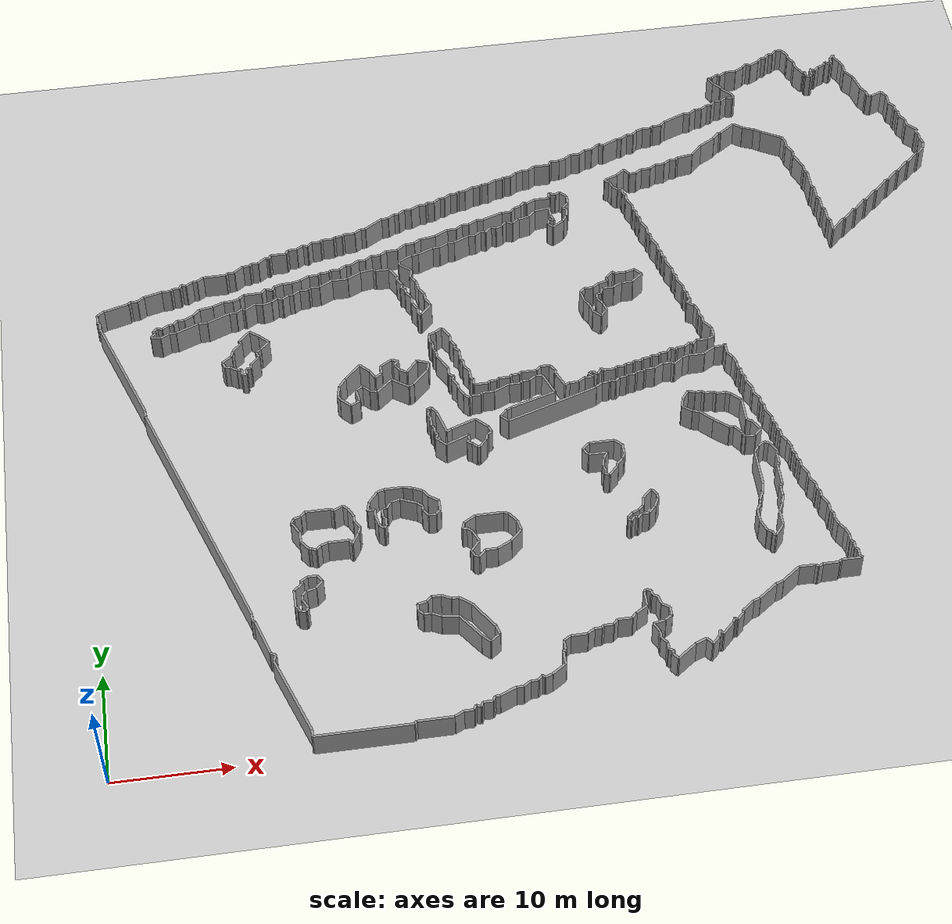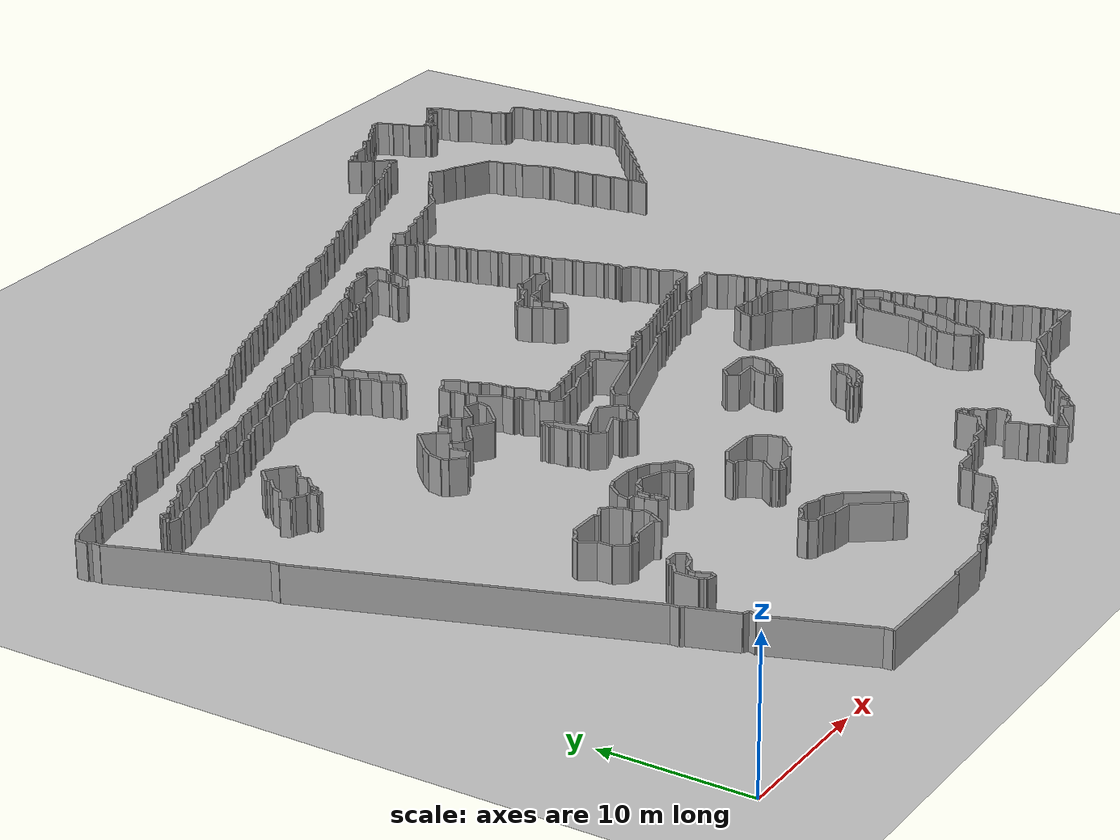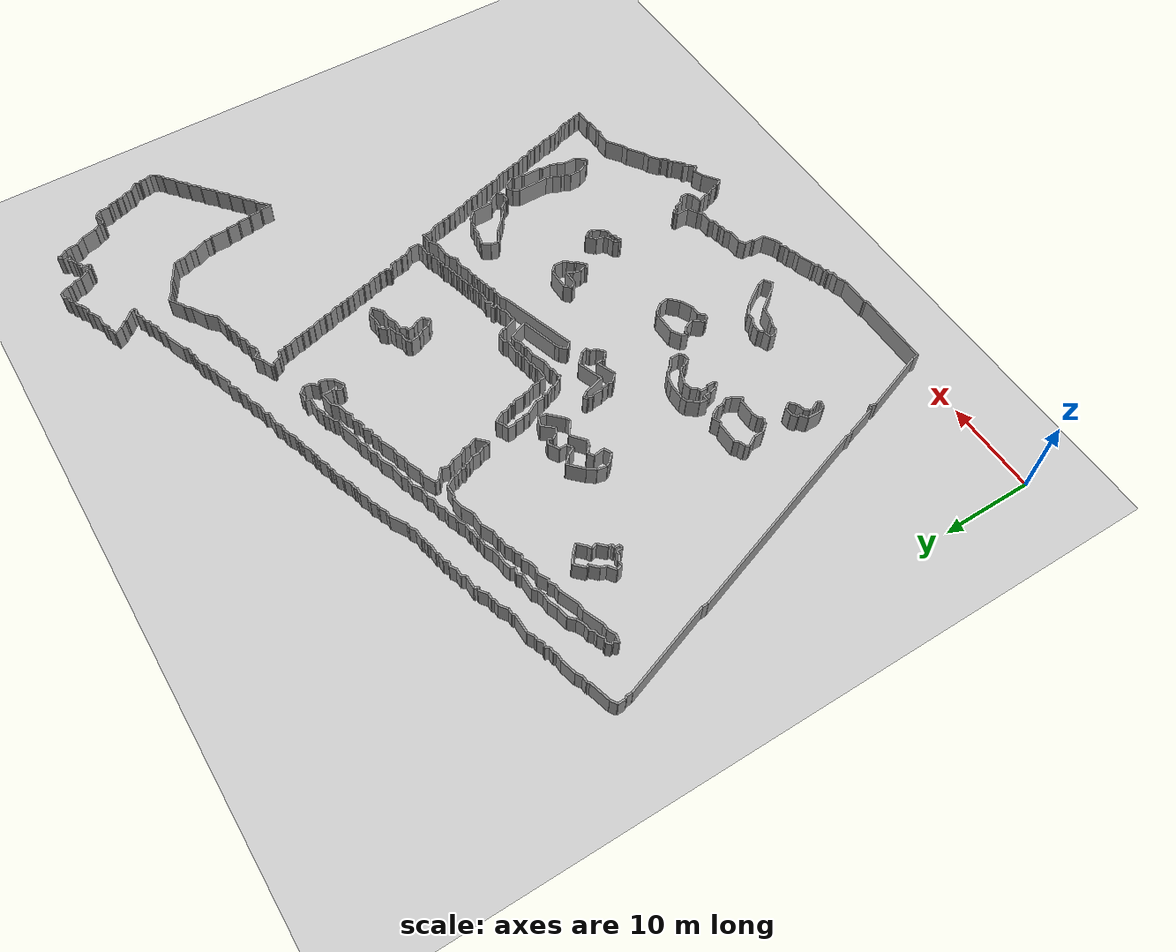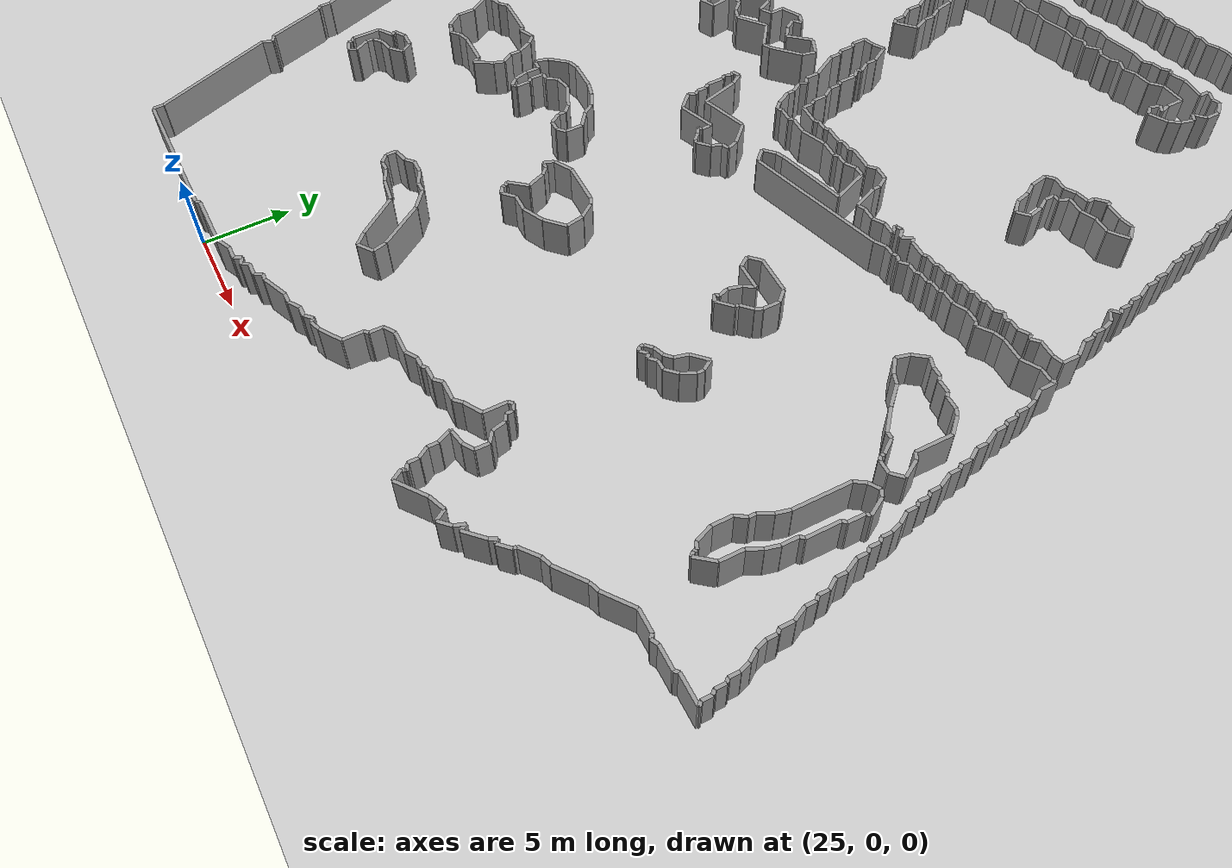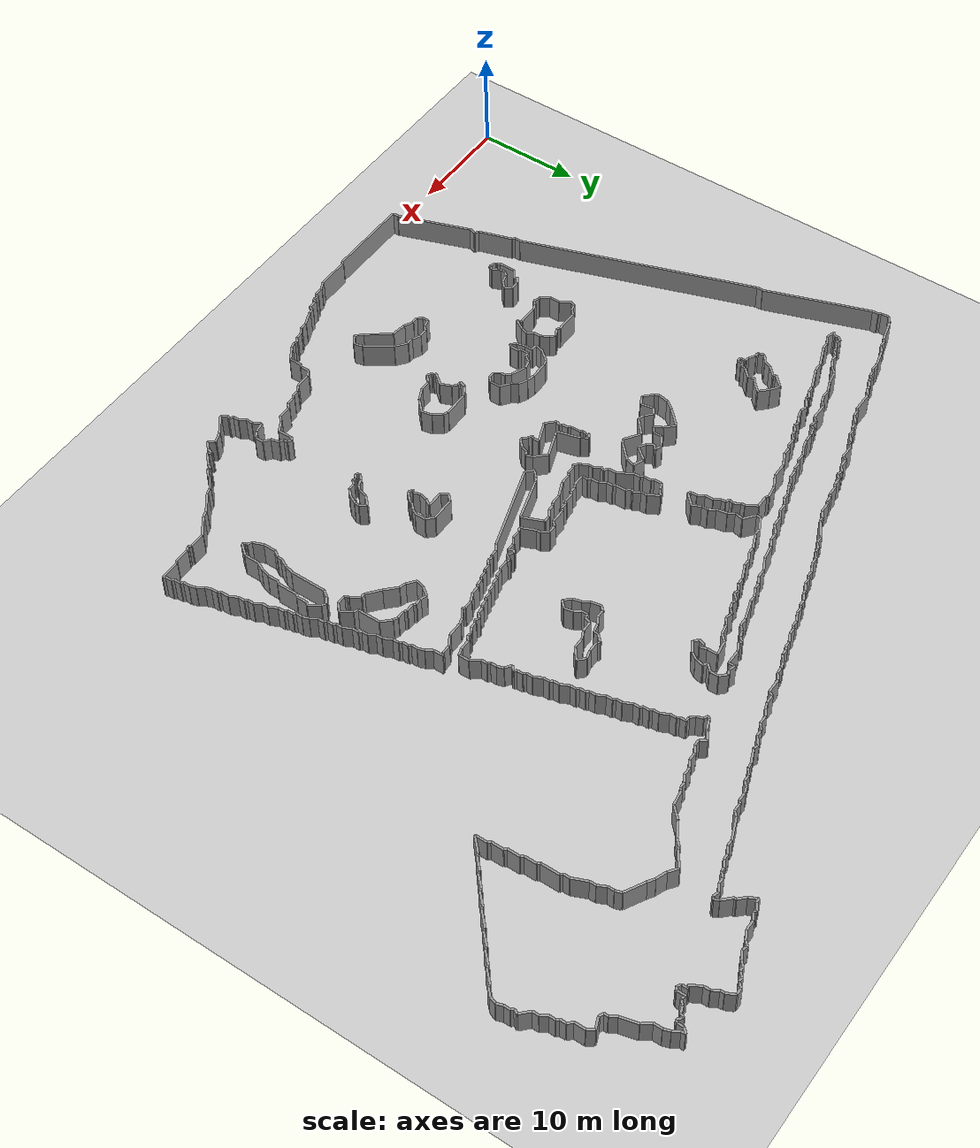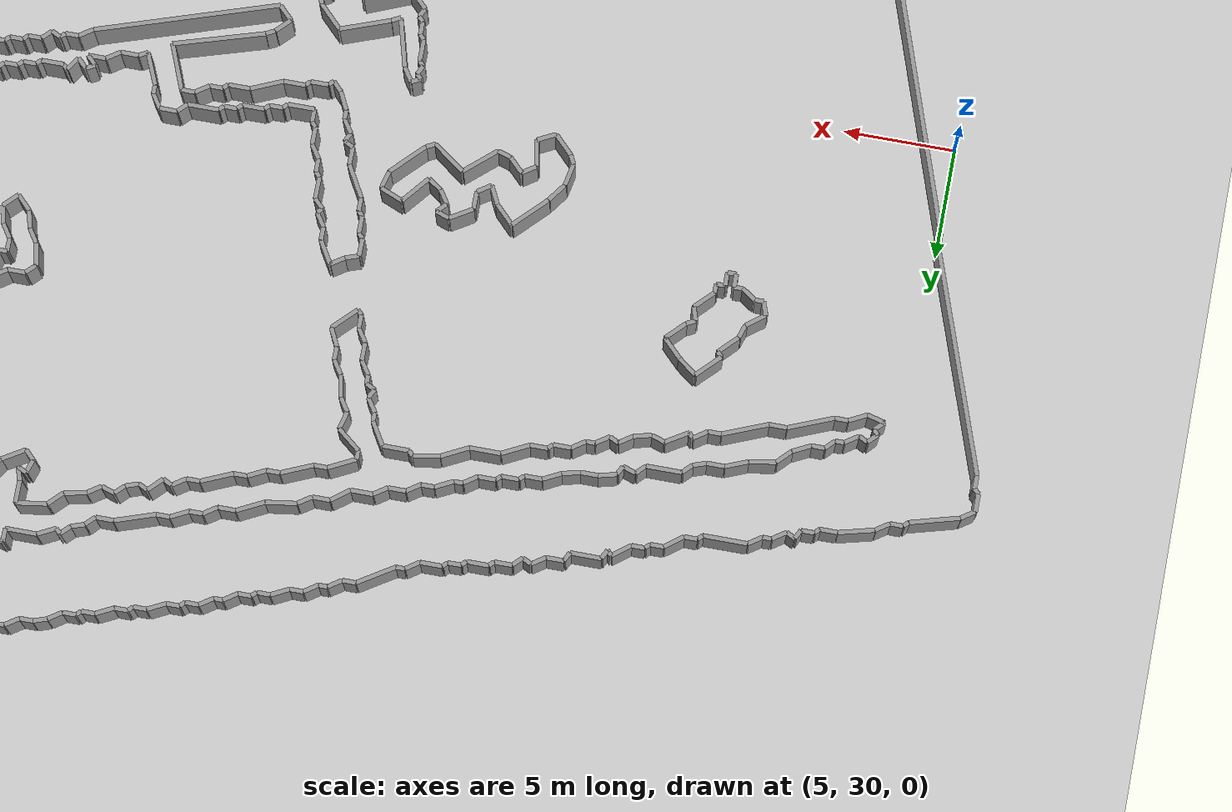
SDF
<?xml version='1.0'?>
        <sdf version='1.4'>
            <world name='1_wall'>
                <light name='sun' type='directional'>
                    <cast_shadows>1</cast_shadows>
                    <pose>0 0 10 0 -0 0</pose>
                    <diffuse>0.8 0.8 0.8 1</diffuse>
                    <specular>0.2 0.2 0.2 1</specular>
                    <attenuation>
                    <range>1000</range>
                    <constant>0.9</constant>
                    <linear>0.01</linear>
                    <quadratic>0.001</quadratic>
                    </attenuation>
                    <direction>-0.5 0.1 -0.9</direction>
                </light>
                <model name='ground_plane'>
                    <static>1</static>
                    <link name='link'>
                        <collision name='collision'>
                        <geometry>
                            <plane>
                                <normal>0 0 1</normal>
                                <size>1000 1000</size>
                            </plane>
                        </geometry>
                        <surface>
                            <friction>
                                <ode>
                                    <mu>100</mu>
                                    <mu2>50</mu2>
                                </ode>
                            </friction>
                            <bounce/>
                                <contact>
                                    <ode/>
                                </contact>
                        </surface>
                        <max_contacts>10</max_contacts>
                        </collision>
                    <visual name='visual'>
                        <cast_shadows>0</cast_shadows>
                        <geometry>
                            <plane>
                                <normal>0 0 1</normal>
                                <size>10000 10000</size>
                            </plane>
                            </geometry>
                                <material>
                                <script>
                                        <uri>file://media/materials/scripts/gazebo.material</uri>
                                        <name>Gazebo/Grey</name>
                                        </script>
                                    </material>
                    </visual>
                    <velocity_decay>
                        <linear>0</linear>
                        <angular>0</angular>
                    </velocity_decay>
                    <self_collide>0</self_collide>
                        <kinematic>0</kinematic>
                        <gravity>1</gravity>
                    </link>
                </model>
                <physics type='ode'>
                    <max_step_size>0.01</max_step_size>
                    <real_time_factor>1</real_time_factor>
                    <real_time_update_rate>100</real_time_update_rate>
                    <gravity>0 0 -9.8</gravity>
                </physics>
            <scene>
                <ambient>0.4 0.4 0.4 1</ambient>
                <background>0.7 0.7 0.7 1</background>
                <shadows>1</shadows>
            </scene>
    <model name='Wall_0'>
     <static>1</static>
    <link name='Wall_0'>
    <collision name='Wall_Collision_0'>
        <geometry>
          <box>
            <size>8.0 0.2 2.5</size>
          </box>
        </geometry>
        <pose>0 0 1.25 0 -0 0</pose>
      </collision>
      <visual name='Wall_Visual_0'>
        <pose>0 0 1.25 0 -0 0</pose>
        <geometry>
          <box>
            <size>8.0 0.2 2.5</size>
          </box>
        </geometry>
        <material>
          <script>
            <uri>file://media/materials/scripts/gazebo.material</uri>
            <name>Gazebo/Grey</name>
          </script>
        </material>
      </visual>
      <velocity_decay>
        <linear>0</linear>
        <angular>0</angular>
      </velocity_decay>
      <pose>20.2 0.4 0 0 0 3.14159265359</pose>
    </link>
     </model><model name='Wall_1'>
     <static>1</static>
    <link name='Wall_1'>
    <collision name='Wall_Collision_1'>
        <geometry>
          <box>
            <size>0.6 0.2 2.5</size>
          </box>
        </geometry>
        <pose>0 0 1.25 0 -0 0</pose>
      </collision>
      <visual name='Wall_Visual_1'>
        <pose>0 0 1.25 0 -0 0</pose>
        <geometry>
          <box>
            <size>0.6 0.2 2.5</size>
          </box>
        </geometry>
        <material>
          <script>
            <uri>file://media/materials/scripts/gazebo.material</uri>
            <name>Gazebo/Grey</name>
          </script>
        </material>
      </visual>
      <velocity_decay>
        <linear>0</linear>
        <angular>0</angular>
      </velocity_decay>
      <pose>16.2 0.7 0 0 0 1.57079632679</pose>
    </link>
     </model><model name='Wall_2'>
     <static>1</static>
    <link name='Wall_2'>
    <collision name='Wall_Collision_2'>
        <geometry>
          <box>
            <size>7.21110255093 0.2 2.5</size>
          </box>
        </geometry>
        <pose>0 0 1.25 0 -0 0</pose>
      </collision>
      <visual name='Wall_Visual_2'>
        <pose>0 0 1.25 0 -0 0</pose>
        <geometry>
          <box>
            <size>7.21110255093 0.2 2.5</size>
          </box>
        </geometry>
        <material>
          <script>
            <uri>file://media/materials/scripts/gazebo.material</uri>
            <name>Gazebo/Grey</name>
          </script>
        </material>
      </visual>
      <velocity_decay>
        <linear>0</linear>
        <angular>0</angular>
      </velocity_decay>
      <pose>15.0 4.4 0 0 0 1.91008894125</pose>
    </link>
     </model><model name='Wall_3'>
     <static>1</static>
    <link name='Wall_3'>
    <collision name='Wall_Collision_3'>
        <geometry>
          <box>
            <size>0.632455532034 0.2 2.5</size>
          </box>
        </geometry>
        <pose>0 0 1.25 0 -0 0</pose>
      </collision>
      <visual name='Wall_Visual_3'>
        <pose>0 0 1.25 0 -0 0</pose>
        <geometry>
          <box>
            <size>0.632455532034 0.2 2.5</size>
          </box>
        </geometry>
        <material>
          <script>
            <uri>file://media/materials/scripts/gazebo.material</uri>
            <name>Gazebo/Grey</name>
          </script>
        </material>
      </visual>
      <velocity_decay>
        <linear>0</linear>
        <angular>0</angular>
      </velocity_decay>
      <pose>13.9 8.1 0 0 0 1.2490457724</pose>
    </link>
     </model><model name='Wall_4'>
     <static>1</static>
    <link name='Wall_4'>
    <collision name='Wall_Collision_4'>
        <geometry>
          <box>
            <size>0.4472135955 0.2 2.5</size>
          </box>
        </geometry>
        <pose>0 0 1.25 0 -0 0</pose>
      </collision>
      <visual name='Wall_Visual_4'>
        <pose>0 0 1.25 0 -0 0</pose>
        <geometry>
          <box>
            <size>0.4472135955 0.2 2.5</size>
          </box>
        </geometry>
        <material>
          <script>
            <uri>file://media/materials/scripts/gazebo.material</uri>
            <name>Gazebo/Grey</name>
          </script>
        </material>
      </visual>
      <velocity_decay>
        <linear>0</linear>
        <angular>0</angular>
      </velocity_decay>
      <pose>13.8 8.5 0 0 0 2.67794504459</pose>
    </link>
     </model><model name='Wall_5'>
     <static>1</static>
    <link name='Wall_5'>
    <collision name='Wall_Collision_5'>
        <geometry>
          <box>
            <size>3.35261092285 0.2 2.5</size>
          </box>
        </geometry>
        <pose>0 0 1.25 0 -0 0</pose>
      </collision>
      <visual name='Wall_Visual_5'>
        <pose>0 0 1.25 0 -0 0</pose>
        <geometry>
          <box>
            <size>3.35261092285 0.2 2.5</size>
          </box>
        </geometry>
        <material>
          <script>
            <uri>file://media/materials/scripts/gazebo.material</uri>
            <name>Gazebo/Grey</name>
          </script>
        </material>
      </visual>
      <velocity_decay>
        <linear>0</linear>
        <angular>0</angular>
      </velocity_decay>
      <pose>13.1 10.2 0 0 0 1.87368119517</pose>
    </link>
     </model><model name='Wall_6'>
     <static>1</static>
    <link name='Wall_6'>
    <collision name='Wall_Collision_6'>
        <geometry>
          <box>
            <size>0.282842712475 0.2 2.5</size>
          </box>
        </geometry>
        <pose>0 0 1.25 0 -0 0</pose>
      </collision>
      <visual name='Wall_Visual_6'>
        <pose>0 0 1.25 0 -0 0</pose>
        <geometry>
          <box>
            <size>0.282842712475 0.2 2.5</size>
          </box>
        </geometry>
        <material>
          <script>
            <uri>file://media/materials/scripts/gazebo.material</uri>
            <name>Gazebo/Grey</name>
          </script>
        </material>
      </visual>
      <velocity_decay>
        <linear>0</linear>
        <angular>0</angular>
      </velocity_decay>
      <pose>12.5 11.9 0 0 0 2.35619449019</pose>
    </link>
     </model><model name='Wall_7'>
     <static>1</static>
    <link name='Wall_7'>
    <collision name='Wall_Collision_7'>
        <geometry>
          <box>
            <size>0.6 0.2 2.5</size>
          </box>
        </geometry>
        <pose>0 0 1.25 0 -0 0</pose>
      </collision>
      <visual name='Wall_Visual_7'>
        <pose>0 0 1.25 0 -0 0</pose>
        <geometry>
          <box>
            <size>0.6 0.2 2.5</size>
          </box>
        </geometry>
        <material>
          <script>
            <uri>file://media/materials/scripts/gazebo.material</uri>
            <name>Gazebo/Grey</name>
          </script>
        </material>
      </visual>
      <velocity_decay>
        <linear>0</linear>
        <angular>0</angular>
      </velocity_decay>
      <pose>12.4 12.3 0 0 0 1.57079632679</pose>
    </link>
     </model><model name='Wall_8'>
     <static>1</static>
    <link name='Wall_8'>
    <collision name='Wall_Collision_8'>
        <geometry>
          <box>
            <size>23.0217288664 0.2 2.5</size>
          </box>
        </geometry>
        <pose>0 0 1.25 0 -0 0</pose>
      </collision>
      <visual name='Wall_Visual_8'>
        <pose>0 0 1.25 0 -0 0</pose>
        <geometry>
          <box>
            <size>23.0217288664 0.2 2.5</size>
          </box>
        </geometry>
        <material>
          <script>
            <uri>file://media/materials/scripts/gazebo.material</uri>
            <name>Gazebo/Grey</name>
          </script>
        </material>
      </visual>
      <velocity_decay>
        <linear>0</linear>
        <angular>0</angular>
      </velocity_decay>
      <pose>8.7 23.5 0 0 0 1.89804133139</pose>
    </link>
     </model><model name='Wall_9'>
     <static>1</static>
    <link name='Wall_9'>
    <collision name='Wall_Collision_9'>
        <geometry>
          <box>
            <size>0.6 0.2 2.5</size>
          </box>
        </geometry>
        <pose>0 0 1.25 0 -0 0</pose>
      </collision>
      <visual name='Wall_Visual_9'>
        <pose>0 0 1.25 0 -0 0</pose>
        <geometry>
          <box>
            <size>0.6 0.2 2.5</size>
          </box>
        </geometry>
        <material>
          <script>
            <uri>file://media/materials/scripts/gazebo.material</uri>
            <name>Gazebo/Grey</name>
          </script>
        </material>
      </visual>
      <velocity_decay>
        <linear>0</linear>
        <angular>0</angular>
      </velocity_decay>
      <pose>5.0 34.7 0 0 0 1.57079632679</pose>
    </link>
     </model><model name='Wall_10'>
     <static>1</static>
    <link name='Wall_10'>
    <collision name='Wall_Collision_10'>
        <geometry>
          <box>
            <size>10.3730419839 0.2 2.5</size>
          </box>
        </geometry>
        <pose>0 0 1.25 0 -0 0</pose>
      </collision>
      <visual name='Wall_Visual_10'>
        <pose>0 0 1.25 0 -0 0</pose>
        <geometry>
          <box>
            <size>10.3730419839 0.2 2.5</size>
          </box>
        </geometry>
        <material>
          <script>
            <uri>file://media/materials/scripts/gazebo.material</uri>
            <name>Gazebo/Grey</name>
          </script>
        </material>
      </visual>
      <velocity_decay>
        <linear>0</linear>
        <angular>0</angular>
      </velocity_decay>
      <pose>3.3 39.9 0 0 0 1.90474139864</pose>
    </link>
     </model><model name='Wall_11'>
     <static>1</static>
    <link name='Wall_11'>
    <collision name='Wall_Collision_11'>
        <geometry>
          <box>
            <size>0.6 0.2 2.5</size>
          </box>
        </geometry>
        <pose>0 0 1.25 0 -0 0</pose>
      </collision>
      <visual name='Wall_Visual_11'>
        <pose>0 0 1.25 0 -0 0</pose>
        <geometry>
          <box>
            <size>0.6 0.2 2.5</size>
          </box>
        </geometry>
        <material>
          <script>
            <uri>file://media/materials/scripts/gazebo.material</uri>
            <name>Gazebo/Grey</name>
          </script>
        </material>
      </visual>
      <velocity_decay>
        <linear>0</linear>
        <angular>0</angular>
      </velocity_decay>
      <pose>1.6 45.1 0 0 0 1.57079632679</pose>
    </link>
     </model><model name='Wall_12'>
     <static>1</static>
    <link name='Wall_12'>
    <collision name='Wall_Collision_12'>
        <geometry>
          <box>
            <size>0.282842712475 0.2 2.5</size>
          </box>
        </geometry>
        <pose>0 0 1.25 0 -0 0</pose>
      </collision>
      <visual name='Wall_Visual_12'>
        <pose>0 0 1.25 0 -0 0</pose>
        <geometry>
          <box>
            <size>0.282842712475 0.2 2.5</size>
          </box>
        </geometry>
        <material>
          <script>
            <uri>file://media/materials/scripts/gazebo.material</uri>
            <name>Gazebo/Grey</name>
          </script>
        </material>
      </visual>
      <velocity_decay>
        <linear>0</linear>
        <angular>0</angular>
      </velocity_decay>
      <pose>1.5 45.5 0 0 0 2.35619449019</pose>
    </link>
     </model><model name='Wall_13'>
     <static>1</static>
    <link name='Wall_13'>
    <collision name='Wall_Collision_13'>
        <geometry>
          <box>
            <size>0.8 0.2 2.5</size>
          </box>
        </geometry>
        <pose>0 0 1.25 0 -0 0</pose>
      </collision>
      <visual name='Wall_Visual_13'>
        <pose>0 0 1.25 0 -0 0</pose>
        <geometry>
          <box>
            <size>0.8 0.2 2.5</size>
          </box>
        </geometry>
        <material>
          <script>
            <uri>file://media/materials/scripts/gazebo.material</uri>
            <name>Gazebo/Grey</name>
          </script>
        </material>
      </visual>
      <velocity_decay>
        <linear>0</linear>
        <angular>0</angular>
      </velocity_decay>
      <pose>1.4 46.0 0 0 0 1.57079632679</pose>
    </link>
     </model><model name='Wall_14'>
     <static>1</static>
    <link name='Wall_14'>
    <collision name='Wall_Collision_14'>
        <geometry>
          <box>
            <size>0.721110255093 0.2 2.5</size>
          </box>
        </geometry>
        <pose>0 0 1.25 0 -0 0</pose>
      </collision>
      <visual name='Wall_Visual_14'>
        <pose>0 0 1.25 0 -0 0</pose>
        <geometry>
          <box>
            <size>0.721110255093 0.2 2.5</size>
          </box>
        </geometry>
        <material>
          <script>
            <uri>file://media/materials/scripts/gazebo.material</uri>
            <name>Gazebo/Grey</name>
          </script>
        </material>
      </visual>
      <velocity_decay>
        <linear>0</linear>
        <angular>0</angular>
      </velocity_decay>
      <pose>1.7 46.6 0 0 0 0.588002603548</pose>
    </link>
     </model><model name='Wall_15'>
     <static>1</static>
    <link name='Wall_15'>
    <collision name='Wall_Collision_15'>
        <geometry>
          <box>
            <size>2.2803508502 0.2 2.5</size>
          </box>
        </geometry>
        <pose>0 0 1.25 0 -0 0</pose>
      </collision>
      <visual name='Wall_Visual_15'>
        <pose>0 0 1.25 0 -0 0</pose>
        <geometry>
          <box>
            <size>2.2803508502 0.2 2.5</size>
          </box>
        </geometry>
        <material>
          <script>
            <uri>file://media/materials/scripts/gazebo.material</uri>
            <name>Gazebo/Grey</name>
          </script>
        </material>
      </visual>
      <velocity_decay>
        <linear>0</linear>
        <angular>0</angular>
      </velocity_decay>
      <pose>3.1 47.1 0 0 0 0.266252049151</pose>
    </link>
     </model><model name='Wall_16'>
     <static>1</static>
    <link name='Wall_16'>
    <collision name='Wall_Collision_16'>
        <geometry>
          <box>
            <size>0.282842712475 0.2 2.5</size>
          </box>
        </geometry>
        <pose>0 0 1.25 0 -0 0</pose>
      </collision>
      <visual name='Wall_Visual_16'>
        <pose>0 0 1.25 0 -0 0</pose>
        <geometry>
          <box>
            <size>0.282842712475 0.2 2.5</size>
          </box>
        </geometry>
        <material>
          <script>
            <uri>file://media/materials/scripts/gazebo.material</uri>
            <name>Gazebo/Grey</name>
          </script>
        </material>
      </visual>
      <velocity_decay>
        <linear>0</linear>
        <angular>0</angular>
      </velocity_decay>
      <pose>4.3 47.5 0 0 0 0.785398163397</pose>
    </link>
     </model><model name='Wall_17'>
     <static>1</static>
    <link name='Wall_17'>
    <collision name='Wall_Collision_17'>
        <geometry>
          <box>
            <size>0.6 0.2 2.5</size>
          </box>
        </geometry>
        <pose>0 0 1.25 0 -0 0</pose>
      </collision>
      <visual name='Wall_Visual_17'>
        <pose>0 0 1.25 0 -0 0</pose>
        <geometry>
          <box>
            <size>0.6 0.2 2.5</size>
          </box>
        </geometry>
        <material>
          <script>
            <uri>file://media/materials/scripts/gazebo.material</uri>
            <name>Gazebo/Grey</name>
          </script>
        </material>
      </visual>
      <velocity_decay>
        <linear>0</linear>
        <angular>0</angular>
      </velocity_decay>
      <pose>4.7 47.6 0 0 0 0.0</pose>
    </link>
     </model><model name='Wall_18'>
     <static>1</static>
    <link name='Wall_18'>
    <collision name='Wall_Collision_18'>
        <geometry>
          <box>
            <size>0.721110255093 0.2 2.5</size>
          </box>
        </geometry>
        <pose>0 0 1.25 0 -0 0</pose>
      </collision>
      <visual name='Wall_Visual_18'>
        <pose>0 0 1.25 0 -0 0</pose>
        <geometry>
          <box>
            <size>0.721110255093 0.2 2.5</size>
          </box>
        </geometry>
        <material>
          <script>
            <uri>file://media/materials/scripts/gazebo.material</uri>
            <name>Gazebo/Grey</name>
          </script>
        </material>
      </visual>
      <velocity_decay>
        <linear>0</linear>
        <angular>0</angular>
      </velocity_decay>
      <pose>5.3 47.8 0 0 0 0.588002603548</pose>
    </link>
     </model><model name='Wall_19'>
     <static>1</static>
    <link name='Wall_19'>
    <collision name='Wall_Collision_19'>
        <geometry>
          <box>
            <size>1.64924225025 0.2 2.5</size>
          </box>
        </geometry>
        <pose>0 0 1.25 0 -0 0</pose>
      </collision>
      <visual name='Wall_Visual_19'>
        <pose>0 0 1.25 0 -0 0</pose>
        <geometry>
          <box>
            <size>1.64924225025 0.2 2.5</size>
          </box>
        </geometry>
        <material>
          <script>
            <uri>file://media/materials/scripts/gazebo.material</uri>
            <name>Gazebo/Grey</name>
          </script>
        </material>
      </visual>
      <velocity_decay>
        <linear>0</linear>
        <angular>0</angular>
      </velocity_decay>
      <pose>6.4 48.2 0 0 0 0.244978663127</pose>
    </link>
     </model><model name='Wall_20'>
     <static>1</static>
    <link name='Wall_20'>
    <collision name='Wall_Collision_20'>
        <geometry>
          <box>
            <size>0.8 0.2 2.5</size>
          </box>
        </geometry>
        <pose>0 0 1.25 0 -0 0</pose>
      </collision>
      <visual name='Wall_Visual_20'>
        <pose>0 0 1.25 0 -0 0</pose>
        <geometry>
          <box>
            <size>0.8 0.2 2.5</size>
          </box>
        </geometry>
        <material>
          <script>
            <uri>file://media/materials/scripts/gazebo.material</uri>
            <name>Gazebo/Grey</name>
          </script>
        </material>
      </visual>
      <velocity_decay>
        <linear>0</linear>
        <angular>0</angular>
      </velocity_decay>
      <pose>7.6 48.4 0 0 0 0.0</pose>
    </link>
     </model><model name='Wall_21'>
     <static>1</static>
    <link name='Wall_21'>
    <collision name='Wall_Collision_21'>
        <geometry>
          <box>
            <size>0.282842712475 0.2 2.5</size>
          </box>
        </geometry>
        <pose>0 0 1.25 0 -0 0</pose>
      </collision>
      <visual name='Wall_Visual_21'>
        <pose>0 0 1.25 0 -0 0</pose>
        <geometry>
          <box>
            <size>0.282842712475 0.2 2.5</size>
          </box>
        </geometry>
        <material>
          <script>
            <uri>file://media/materials/scripts/gazebo.material</uri>
            <name>Gazebo/Grey</name>
          </script>
        </material>
      </visual>
      <velocity_decay>
        <linear>0</linear>
        <angular>0</angular>
      </velocity_decay>
      <pose>8.1 48.5 0 0 0 0.785398163397</pose>
    </link>
     </model><model name='Wall_22'>
     <static>1</static>
    <link name='Wall_22'>
    <collision name='Wall_Collision_22'>
        <geometry>
          <box>
            <size>0.6 0.2 2.5</size>
          </box>
        </geometry>
        <pose>0 0 1.25 0 -0 0</pose>
      </collision>
      <visual name='Wall_Visual_22'>
        <pose>0 0 1.25 0 -0 0</pose>
        <geometry>
          <box>
            <size>0.6 0.2 2.5</size>
          </box>
        </geometry>
        <material>
          <script>
            <uri>file://media/materials/scripts/gazebo.material</uri>
            <name>Gazebo/Grey</name>
          </script>
        </material>
      </visual>
      <velocity_decay>
        <linear>0</linear>
        <angular>0</angular>
      </velocity_decay>
      <pose>8.5 48.6 0 0 0 0.0</pose>
    </link>
     </model><model name='Wall_23'>
     <static>1</static>
    <link name='Wall_23'>
    <collision name='Wall_Collision_23'>
        <geometry>
          <box>
            <size>0.4472135955 0.2 2.5</size>
          </box>
        </geometry>
        <pose>0 0 1.25 0 -0 0</pose>
      </collision>
      <visual name='Wall_Visual_23'>
        <pose>0 0 1.25 0 -0 0</pose>
        <geometry>
          <box>
            <size>0.4472135955 0.2 2.5</size>
          </box>
        </geometry>
        <material>
          <script>
            <uri>file://media/materials/scripts/gazebo.material</uri>
            <name>Gazebo/Grey</name>
          </script>
        </material>
      </visual>
      <velocity_decay>
        <linear>0</linear>
        <angular>0</angular>
      </velocity_decay>
      <pose>8.9 48.8 0 0 0 1.10714871779</pose>
    </link>
     </model><model name='Wall_24'>
     <static>1</static>
    <link name='Wall_24'>
    <collision name='Wall_Collision_24'>
        <geometry>
          <box>
            <size>0.4472135955 0.2 2.5</size>
          </box>
        </geometry>
        <pose>0 0 1.25 0 -0 0</pose>
      </collision>
      <visual name='Wall_Visual_24'>
        <pose>0 0 1.25 0 -0 0</pose>
        <geometry>
          <box>
            <size>0.4472135955 0.2 2.5</size>
          </box>
        </geometry>
        <material>
          <script>
            <uri>file://media/materials/scripts/gazebo.material</uri>
            <name>Gazebo/Grey</name>
          </script>
        </material>
      </visual>
      <velocity_decay>
        <linear>0</linear>
        <angular>0</angular>
      </velocity_decay>
      <pose>9.2 48.9 0 0 0 -0.463647609001</pose>
    </link>
     </model><model name='Wall_25'>
     <static>1</static>
    <link name='Wall_25'>
    <collision name='Wall_Collision_25'>
        <geometry>
          <box>
            <size>0.721110255093 0.2 2.5</size>
          </box>
        </geometry>
        <pose>0 0 1.25 0 -0 0</pose>
      </collision>
      <visual name='Wall_Visual_25'>
        <pose>0 0 1.25 0 -0 0</pose>
        <geometry>
          <box>
            <size>0.721110255093 0.2 2.5</size>
          </box>
        </geometry>
        <material>
          <script>
            <uri>file://media/materials/scripts/gazebo.material</uri>
            <name>Gazebo/Grey</name>
          </script>
        </material>
      </visual>
      <velocity_decay>
        <linear>0</linear>
        <angular>0</angular>
      </velocity_decay>
      <pose>9.7 49.0 0 0 0 0.588002603548</pose>
    </link>
     </model><model name='Wall_26'>
     <static>1</static>
    <link name='Wall_26'>
    <collision name='Wall_Collision_26'>
        <geometry>
          <box>
            <size>0.4 0.2 2.5</size>
          </box>
        </geometry>
        <pose>0 0 1.25 0 -0 0</pose>
      </collision>
      <visual name='Wall_Visual_26'>
        <pose>0 0 1.25 0 -0 0</pose>
        <geometry>
          <box>
            <size>0.4 0.2 2.5</size>
          </box>
        </geometry>
        <material>
          <script>
            <uri>file://media/materials/scripts/gazebo.material</uri>
            <name>Gazebo/Grey</name>
          </script>
        </material>
      </visual>
      <velocity_decay>
        <linear>0</linear>
        <angular>0</angular>
      </velocity_decay>
      <pose>10.2 49.2 0 0 0 0.0</pose>
    </link>
     </model><model name='Wall_27'>
     <static>1</static>
    <link name='Wall_27'>
    <collision name='Wall_Collision_27'>
        <geometry>
          <box>
            <size>0.721110255093 0.2 2.5</size>
          </box>
        </geometry>
        <pose>0 0 1.25 0 -0 0</pose>
      </collision>
      <visual name='Wall_Visual_27'>
        <pose>0 0 1.25 0 -0 0</pose>
        <geometry>
          <box>
            <size>0.721110255093 0.2 2.5</size>
          </box>
        </geometry>
        <material>
          <script>
            <uri>file://media/materials/scripts/gazebo.material</uri>
            <name>Gazebo/Grey</name>
          </script>
        </material>
      </visual>
      <velocity_decay>
        <linear>0</linear>
        <angular>0</angular>
      </velocity_decay>
      <pose>10.7 49.4 0 0 0 0.588002603548</pose>
    </link>
     </model><model name='Wall_28'>
     <static>1</static>
    <link name='Wall_28'>
    <collision name='Wall_Collision_28'>
        <geometry>
          <box>
            <size>2.0 0.2 2.5</size>
          </box>
        </geometry>
        <pose>0 0 1.25 0 -0 0</pose>
      </collision>
      <visual name='Wall_Visual_28'>
        <pose>0 0 1.25 0 -0 0</pose>
        <geometry>
          <box>
            <size>2.0 0.2 2.5</size>
          </box>
        </geometry>
        <material>
          <script>
            <uri>file://media/materials/scripts/gazebo.material</uri>
            <name>Gazebo/Grey</name>
          </script>
        </material>
      </visual>
      <velocity_decay>
        <linear>0</linear>
        <angular>0</angular>
      </velocity_decay>
      <pose>12.0 49.6 0 0 0 0.0</pose>
    </link>
     </model><model name='Wall_29'>
     <static>1</static>
    <link name='Wall_29'>
    <collision name='Wall_Collision_29'>
        <geometry>
          <box>
            <size>0.282842712475 0.2 2.5</size>
          </box>
        </geometry>
        <pose>0 0 1.25 0 -0 0</pose>
      </collision>
      <visual name='Wall_Visual_29'>
        <pose>0 0 1.25 0 -0 0</pose>
        <geometry>
          <box>
            <size>0.282842712475 0.2 2.5</size>
          </box>
        </geometry>
        <material>
          <script>
            <uri>file://media/materials/scripts/gazebo.material</uri>
            <name>Gazebo/Grey</name>
          </script>
        </material>
      </visual>
      <velocity_decay>
        <linear>0</linear>
        <angular>0</angular>
      </velocity_decay>
      <pose>13.1 49.7 0 0 0 0.785398163397</pose>
    </link>
     </model><model name='Wall_30'>
     <static>1</static>
    <link name='Wall_30'>
    <collision name='Wall_Collision_30'>
        <geometry>
          <box>
            <size>0.6 0.2 2.5</size>
          </box>
        </geometry>
        <pose>0 0 1.25 0 -0 0</pose>
      </collision>
      <visual name='Wall_Visual_30'>
        <pose>0 0 1.25 0 -0 0</pose>
        <geometry>
          <box>
            <size>0.6 0.2 2.5</size>
          </box>
        </geometry>
        <material>
          <script>
            <uri>file://media/materials/scripts/gazebo.material</uri>
            <name>Gazebo/Grey</name>
          </script>
        </material>
      </visual>
      <velocity_decay>
        <linear>0</linear>
        <angular>0</angular>
      </velocity_decay>
      <pose>13.5 49.8 0 0 0 0.0</pose>
    </link>
     </model><model name='Wall_31'>
     <static>1</static>
    <link name='Wall_31'>
    <collision name='Wall_Collision_31'>
        <geometry>
          <box>
            <size>1.0 0.2 2.5</size>
          </box>
        </geometry>
        <pose>0 0 1.25 0 -0 0</pose>
      </collision>
      <visual name='Wall_Visual_31'>
        <pose>0 0 1.25 0 -0 0</pose>
        <geometry>
          <box>
            <size>1.0 0.2 2.5</size>
          </box>
        </geometry>
        <material>
          <script>
            <uri>file://media/materials/scripts/gazebo.material</uri>
            <name>Gazebo/Grey</name>
          </script>
        </material>
      </visual>
      <velocity_decay>
        <linear>0</linear>
        <angular>0</angular>
      </velocity_decay>
      <pose>14.2 50.1 0 0 0 0.643501108793</pose>
    </link>
     </model><model name='Wall_32'>
     <static>1</static>
    <link name='Wall_32'>
    <collision name='Wall_Collision_32'>
        <geometry>
          <box>
            <size>0.6 0.2 2.5</size>
          </box>
        </geometry>
        <pose>0 0 1.25 0 -0 0</pose>
      </collision>
      <visual name='Wall_Visual_32'>
        <pose>0 0 1.25 0 -0 0</pose>
        <geometry>
          <box>
            <size>0.6 0.2 2.5</size>
          </box>
        </geometry>
        <material>
          <script>
            <uri>file://media/materials/scripts/gazebo.material</uri>
            <name>Gazebo/Grey</name>
          </script>
        </material>
      </visual>
      <velocity_decay>
        <linear>0</linear>
        <angular>0</angular>
      </velocity_decay>
      <pose>14.9 50.4 0 0 0 0.0</pose>
    </link>
     </model><model name='Wall_33'>
     <static>1</static>
    <link name='Wall_33'>
    <collision name='Wall_Collision_33'>
        <geometry>
          <box>
            <size>0.282842712475 0.2 2.5</size>
          </box>
        </geometry>
        <pose>0 0 1.25 0 -0 0</pose>
      </collision>
      <visual name='Wall_Visual_33'>
        <pose>0 0 1.25 0 -0 0</pose>
        <geometry>
          <box>
            <size>0.282842712475 0.2 2.5</size>
          </box>
        </geometry>
        <material>
          <script>
            <uri>file://media/materials/scripts/gazebo.material</uri>
            <name>Gazebo/Grey</name>
          </script>
        </material>
      </visual>
      <velocity_decay>
        <linear>0</linear>
        <angular>0</angular>
      </velocity_decay>
      <pose>15.3 50.5 0 0 0 0.785398163397</pose>
    </link>
     </model><model name='Wall_34'>
     <static>1</static>
    <link name='Wall_34'>
    <collision name='Wall_Collision_34'>
        <geometry>
          <box>
            <size>0.6 0.2 2.5</size>
          </box>
        </geometry>
        <pose>0 0 1.25 0 -0 0</pose>
      </collision>
      <visual name='Wall_Visual_34'>
        <pose>0 0 1.25 0 -0 0</pose>
        <geometry>
          <box>
            <size>0.6 0.2 2.5</size>
          </box>
        </geometry>
        <material>
          <script>
            <uri>file://media/materials/scripts/gazebo.material</uri>
            <name>Gazebo/Grey</name>
          </script>
        </material>
      </visual>
      <velocity_decay>
        <linear>0</linear>
        <angular>0</angular>
      </velocity_decay>
      <pose>15.7 50.6 0 0 0 0.0</pose>
    </link>
     </model><model name='Wall_35'>
     <static>1</static>
    <link name='Wall_35'>
    <collision name='Wall_Collision_35'>
        <geometry>
          <box>
            <size>1.0 0.2 2.5</size>
          </box>
        </geometry>
        <pose>0 0 1.25 0 -0 0</pose>
      </collision>
      <visual name='Wall_Visual_35'>
        <pose>0 0 1.25 0 -0 0</pose>
        <geometry>
          <box>
            <size>1.0 0.2 2.5</size>
          </box>
        </geometry>
        <material>
          <script>
            <uri>file://media/materials/scripts/gazebo.material</uri>
            <name>Gazebo/Grey</name>
          </script>
        </material>
      </visual>
      <velocity_decay>
        <linear>0</linear>
        <angular>0</angular>
      </velocity_decay>
      <pose>16.4 50.9 0 0 0 0.643501108793</pose>
    </link>
     </model><model name='Wall_36'>
     <static>1</static>
    <link name='Wall_36'>
    <collision name='Wall_Collision_36'>
        <geometry>
          <box>
            <size>0.282842712475 0.2 2.5</size>
          </box>
        </geometry>
        <pose>0 0 1.25 0 -0 0</pose>
      </collision>
      <visual name='Wall_Visual_36'>
        <pose>0 0 1.25 0 -0 0</pose>
        <geometry>
          <box>
            <size>0.282842712475 0.2 2.5</size>
          </box>
        </geometry>
        <material>
          <script>
            <uri>file://media/materials/scripts/gazebo.material</uri>
            <name>Gazebo/Grey</name>
          </script>
        </material>
      </visual>
      <velocity_decay>
        <linear>0</linear>
        <angular>0</angular>
      </velocity_decay>
      <pose>16.9 51.1 0 0 0 -0.785398163397</pose>
    </link>
     </model><model name='Wall_37'>
     <static>1</static>
    <link name='Wall_37'>
    <collision name='Wall_Collision_37'>
        <geometry>
          <box>
            <size>0.4472135955 0.2 2.5</size>
          </box>
        </geometry>
        <pose>0 0 1.25 0 -0 0</pose>
      </collision>
      <visual name='Wall_Visual_37'>
        <pose>0 0 1.25 0 -0 0</pose>
        <geometry>
          <box>
            <size>0.4472135955 0.2 2.5</size>
          </box>
        </geometry>
        <material>
          <script>
            <uri>file://media/materials/scripts/gazebo.material</uri>
            <name>Gazebo/Grey</name>
          </script>
        </material>
      </visual>
      <velocity_decay>
        <linear>0</linear>
        <angular>0</angular>
      </velocity_decay>
      <pose>17.1 51.2 0 0 0 1.10714871779</pose>
    </link>
     </model><model name='Wall_38'>
     <static>1</static>
    <link name='Wall_38'>
    <collision name='Wall_Collision_38'>
        <geometry>
          <box>
            <size>1.4 0.2 2.5</size>
          </box>
        </geometry>
        <pose>0 0 1.25 0 -0 0</pose>
      </collision>
      <visual name='Wall_Visual_38'>
        <pose>0 0 1.25 0 -0 0</pose>
        <geometry>
          <box>
            <size>1.4 0.2 2.5</size>
          </box>
        </geometry>
        <material>
          <script>
            <uri>file://media/materials/scripts/gazebo.material</uri>
            <name>Gazebo/Grey</name>
          </script>
        </material>
      </visual>
      <velocity_decay>
        <linear>0</linear>
        <angular>0</angular>
      </velocity_decay>
      <pose>17.9 51.4 0 0 0 0.0</pose>
    </link>
     </model><model name='Wall_39'>
     <static>1</static>
    <link name='Wall_39'>
    <collision name='Wall_Collision_39'>
        <geometry>
          <box>
            <size>0.4472135955 0.2 2.5</size>
          </box>
        </geometry>
        <pose>0 0 1.25 0 -0 0</pose>
      </collision>
      <visual name='Wall_Visual_39'>
        <pose>0 0 1.25 0 -0 0</pose>
        <geometry>
          <box>
            <size>0.4472135955 0.2 2.5</size>
          </box>
        </geometry>
        <material>
          <script>
            <uri>file://media/materials/scripts/gazebo.material</uri>
            <name>Gazebo/Grey</name>
          </script>
        </material>
      </visual>
      <velocity_decay>
        <linear>0</linear>
        <angular>0</angular>
      </velocity_decay>
      <pose>18.7 51.6 0 0 0 1.10714871779</pose>
    </link>
     </model><model name='Wall_40'>
     <static>1</static>
    <link name='Wall_40'>
    <collision name='Wall_Collision_40'>
        <geometry>
          <box>
            <size>0.8 0.2 2.5</size>
          </box>
        </geometry>
        <pose>0 0 1.25 0 -0 0</pose>
      </collision>
      <visual name='Wall_Visual_40'>
        <pose>0 0 1.25 0 -0 0</pose>
        <geometry>
          <box>
            <size>0.8 0.2 2.5</size>
          </box>
        </geometry>
        <material>
          <script>
            <uri>file://media/materials/scripts/gazebo.material</uri>
            <name>Gazebo/Grey</name>
          </script>
        </material>
      </visual>
      <velocity_decay>
        <linear>0</linear>
        <angular>0</angular>
      </velocity_decay>
      <pose>19.2 51.8 0 0 0 0.0</pose>
    </link>
     </model><model name='Wall_41'>
     <static>1</static>
    <link name='Wall_41'>
    <collision name='Wall_Collision_41'>
        <geometry>
          <box>
            <size>0.721110255093 0.2 2.5</size>
          </box>
        </geometry>
        <pose>0 0 1.25 0 -0 0</pose>
      </collision>
      <visual name='Wall_Visual_41'>
        <pose>0 0 1.25 0 -0 0</pose>
        <geometry>
          <box>
            <size>0.721110255093 0.2 2.5</size>
          </box>
        </geometry>
        <material>
          <script>
            <uri>file://media/materials/scripts/gazebo.material</uri>
            <name>Gazebo/Grey</name>
          </script>
        </material>
      </visual>
      <velocity_decay>
        <linear>0</linear>
        <angular>0</angular>
      </velocity_decay>
      <pose>19.9 52.0 0 0 0 0.588002603548</pose>
    </link>
     </model><model name='Wall_42'>
     <static>1</static>
    <link name='Wall_42'>
    <collision name='Wall_Collision_42'>
        <geometry>
          <box>
            <size>0.4472135955 0.2 2.5</size>
          </box>
        </geometry>
        <pose>0 0 1.25 0 -0 0</pose>
      </collision>
      <visual name='Wall_Visual_42'>
        <pose>0 0 1.25 0 -0 0</pose>
        <geometry>
          <box>
            <size>0.4472135955 0.2 2.5</size>
          </box>
        </geometry>
        <material>
          <script>
            <uri>file://media/materials/scripts/gazebo.material</uri>
            <name>Gazebo/Grey</name>
          </script>
        </material>
      </visual>
      <velocity_decay>
        <linear>0</linear>
        <angular>0</angular>
      </velocity_decay>
      <pose>20.4 52.1 0 0 0 -0.463647609001</pose>
    </link>
     </model><model name='Wall_43'>
     <static>1</static>
    <link name='Wall_43'>
    <collision name='Wall_Collision_43'>
        <geometry>
          <box>
            <size>0.565685424949 0.2 2.5</size>
          </box>
        </geometry>
        <pose>0 0 1.25 0 -0 0</pose>
      </collision>
      <visual name='Wall_Visual_43'>
        <pose>0 0 1.25 0 -0 0</pose>
        <geometry>
          <box>
            <size>0.565685424949 0.2 2.5</size>
          </box>
        </geometry>
        <material>
          <script>
            <uri>file://media/materials/scripts/gazebo.material</uri>
            <name>Gazebo/Grey</name>
          </script>
        </material>
      </visual>
      <velocity_decay>
        <linear>0</linear>
        <angular>0</angular>
      </velocity_decay>
      <pose>20.8 52.2 0 0 0 0.785398163397</pose>
    </link>
     </model><model name='Wall_44'>
     <static>1</static>
    <link name='Wall_44'>
    <collision name='Wall_Collision_44'>
        <geometry>
          <box>
            <size>0.8 0.2 2.5</size>
          </box>
        </geometry>
        <pose>0 0 1.25 0 -0 0</pose>
      </collision>
      <visual name='Wall_Visual_44'>
        <pose>0 0 1.25 0 -0 0</pose>
        <geometry>
          <box>
            <size>0.8 0.2 2.5</size>
          </box>
        </geometry>
        <material>
          <script>
            <uri>file://media/materials/scripts/gazebo.material</uri>
            <name>Gazebo/Grey</name>
          </script>
        </material>
      </visual>
      <velocity_decay>
        <linear>0</linear>
        <angular>0</angular>
      </velocity_decay>
      <pose>21.4 52.4 0 0 0 0.0</pose>
    </link>
     </model><model name='Wall_45'>
     <static>1</static>
    <link name='Wall_45'>
    <collision name='Wall_Collision_45'>
        <geometry>
          <box>
            <size>0.282842712475 0.2 2.5</size>
          </box>
        </geometry>
        <pose>0 0 1.25 0 -0 0</pose>
      </collision>
      <visual name='Wall_Visual_45'>
        <pose>0 0 1.25 0 -0 0</pose>
        <geometry>
          <box>
            <size>0.282842712475 0.2 2.5</size>
          </box>
        </geometry>
        <material>
          <script>
            <uri>file://media/materials/scripts/gazebo.material</uri>
            <name>Gazebo/Grey</name>
          </script>
        </material>
      </visual>
      <velocity_decay>
        <linear>0</linear>
        <angular>0</angular>
      </velocity_decay>
      <pose>21.9 52.5 0 0 0 0.785398163397</pose>
    </link>
     </model><model name='Wall_46'>
     <static>1</static>
    <link name='Wall_46'>
    <collision name='Wall_Collision_46'>
        <geometry>
          <box>
            <size>1.0 0.2 2.5</size>
          </box>
        </geometry>
        <pose>0 0 1.25 0 -0 0</pose>
      </collision>
      <visual name='Wall_Visual_46'>
        <pose>0 0 1.25 0 -0 0</pose>
        <geometry>
          <box>
            <size>1.0 0.2 2.5</size>
          </box>
        </geometry>
        <material>
          <script>
            <uri>file://media/materials/scripts/gazebo.material</uri>
            <name>Gazebo/Grey</name>
          </script>
        </material>
      </visual>
      <velocity_decay>
        <linear>0</linear>
        <angular>0</angular>
      </velocity_decay>
      <pose>22.5 52.6 0 0 0 0.0</pose>
    </link>
     </model><model name='Wall_47'>
     <static>1</static>
    <link name='Wall_47'>
    <collision name='Wall_Collision_47'>
        <geometry>
          <box>
            <size>0.282842712475 0.2 2.5</size>
          </box>
        </geometry>
        <pose>0 0 1.25 0 -0 0</pose>
      </collision>
      <visual name='Wall_Visual_47'>
        <pose>0 0 1.25 0 -0 0</pose>
        <geometry>
          <box>
            <size>0.282842712475 0.2 2.5</size>
          </box>
        </geometry>
        <material>
          <script>
            <uri>file://media/materials/scripts/gazebo.material</uri>
            <name>Gazebo/Grey</name>
          </script>
        </material>
      </visual>
      <velocity_decay>
        <linear>0</linear>
        <angular>0</angular>
      </velocity_decay>
      <pose>23.1 52.7 0 0 0 0.785398163397</pose>
    </link>
     </model><model name='Wall_48'>
     <static>1</static>
    <link name='Wall_48'>
    <collision name='Wall_Collision_48'>
        <geometry>
          <box>
            <size>0.6 0.2 2.5</size>
          </box>
        </geometry>
        <pose>0 0 1.25 0 -0 0</pose>
      </collision>
      <visual name='Wall_Visual_48'>
        <pose>0 0 1.25 0 -0 0</pose>
        <geometry>
          <box>
            <size>0.6 0.2 2.5</size>
          </box>
        </geometry>
        <material>
          <script>
            <uri>file://media/materials/scripts/gazebo.material</uri>
            <name>Gazebo/Grey</name>
          </script>
        </material>
      </visual>
      <velocity_decay>
        <linear>0</linear>
        <angular>0</angular>
      </velocity_decay>
      <pose>23.5 52.8 0 0 0 0.0</pose>
    </link>
     </model><model name='Wall_49'>
     <static>1</static>
    <link name='Wall_49'>
    <collision name='Wall_Collision_49'>
        <geometry>
          <box>
            <size>0.282842712475 0.2 2.5</size>
          </box>
        </geometry>
        <pose>0 0 1.25 0 -0 0</pose>
      </collision>
      <visual name='Wall_Visual_49'>
        <pose>0 0 1.25 0 -0 0</pose>
        <geometry>
          <box>
            <size>0.282842712475 0.2 2.5</size>
          </box>
        </geometry>
        <material>
          <script>
            <uri>file://media/materials/scripts/gazebo.material</uri>
            <name>Gazebo/Grey</name>
          </script>
        </material>
      </visual>
      <velocity_decay>
        <linear>0</linear>
        <angular>0</angular>
      </velocity_decay>
      <pose>23.9 52.9 0 0 0 0.785398163397</pose>
    </link>
     </model><model name='Wall_50'>
     <static>1</static>
    <link name='Wall_50'>
    <collision name='Wall_Collision_50'>
        <geometry>
          <box>
            <size>1.0 0.2 2.5</size>
          </box>
        </geometry>
        <pose>0 0 1.25 0 -0 0</pose>
      </collision>
      <visual name='Wall_Visual_50'>
        <pose>0 0 1.25 0 -0 0</pose>
        <geometry>
          <box>
            <size>1.0 0.2 2.5</size>
          </box>
        </geometry>
        <material>
          <script>
            <uri>file://media/materials/scripts/gazebo.material</uri>
            <name>Gazebo/Grey</name>
          </script>
        </material>
      </visual>
      <velocity_decay>
        <linear>0</linear>
        <angular>0</angular>
      </velocity_decay>
      <pose>24.5 53.0 0 0 0 0.0</pose>
    </link>
     </model><model name='Wall_51'>
     <static>1</static>
    <link name='Wall_51'>
    <collision name='Wall_Collision_51'>
        <geometry>
          <box>
            <size>0.721110255093 0.2 2.5</size>
          </box>
        </geometry>
        <pose>0 0 1.25 0 -0 0</pose>
      </collision>
      <visual name='Wall_Visual_51'>
        <pose>0 0 1.25 0 -0 0</pose>
        <geometry>
          <box>
            <size>0.721110255093 0.2 2.5</size>
          </box>
        </geometry>
        <material>
          <script>
            <uri>file://media/materials/scripts/gazebo.material</uri>
            <name>Gazebo/Grey</name>
          </script>
        </material>
      </visual>
      <velocity_decay>
        <linear>0</linear>
        <angular>0</angular>
      </velocity_decay>
      <pose>25.3 53.2 0 0 0 0.588002603548</pose>
    </link>
     </model><model name='Wall_52'>
     <static>1</static>
    <link name='Wall_52'>
    <collision name='Wall_Collision_52'>
        <geometry>
          <box>
            <size>0.4 0.2 2.5</size>
          </box>
        </geometry>
        <pose>0 0 1.25 0 -0 0</pose>
      </collision>
      <visual name='Wall_Visual_52'>
        <pose>0 0 1.25 0 -0 0</pose>
        <geometry>
          <box>
            <size>0.4 0.2 2.5</size>
          </box>
        </geometry>
        <material>
          <script>
            <uri>file://media/materials/scripts/gazebo.material</uri>
            <name>Gazebo/Grey</name>
          </script>
        </material>
      </visual>
      <velocity_decay>
        <linear>0</linear>
        <angular>0</angular>
      </velocity_decay>
      <pose>25.8 53.4 0 0 0 0.0</pose>
    </link>
     </model><model name='Wall_53'>
     <static>1</static>
    <link name='Wall_53'>
    <collision name='Wall_Collision_53'>
        <geometry>
          <box>
            <size>1.88679622641 0.2 2.5</size>
          </box>
        </geometry>
        <pose>0 0 1.25 0 -0 0</pose>
      </collision>
      <visual name='Wall_Visual_53'>
        <pose>0 0 1.25 0 -0 0</pose>
        <geometry>
          <box>
            <size>1.88679622641 0.2 2.5</size>
          </box>
        </geometry>
        <material>
          <script>
            <uri>file://media/materials/scripts/gazebo.material</uri>
            <name>Gazebo/Grey</name>
          </script>
        </material>
      </visual>
      <velocity_decay>
        <linear>0</linear>
        <angular>0</angular>
      </velocity_decay>
      <pose>26.8 53.9 0 0 0 0.558599315344</pose>
    </link>
     </model><model name='Wall_54'>
     <static>1</static>
    <link name='Wall_54'>
    <collision name='Wall_Collision_54'>
        <geometry>
          <box>
            <size>0.6 0.2 2.5</size>
          </box>
        </geometry>
        <pose>0 0 1.25 0 -0 0</pose>
      </collision>
      <visual name='Wall_Visual_54'>
        <pose>0 0 1.25 0 -0 0</pose>
        <geometry>
          <box>
            <size>0.6 0.2 2.5</size>
          </box>
        </geometry>
        <material>
          <script>
            <uri>file://media/materials/scripts/gazebo.material</uri>
            <name>Gazebo/Grey</name>
          </script>
        </material>
      </visual>
      <velocity_decay>
        <linear>0</linear>
        <angular>0</angular>
      </velocity_decay>
      <pose>27.9 54.4 0 0 0 0.0</pose>
    </link>
     </model><model name='Wall_55'>
     <static>1</static>
    <link name='Wall_55'>
    <collision name='Wall_Collision_55'>
        <geometry>
          <box>
            <size>0.721110255093 0.2 2.5</size>
          </box>
        </geometry>
        <pose>0 0 1.25 0 -0 0</pose>
      </collision>
      <visual name='Wall_Visual_55'>
        <pose>0 0 1.25 0 -0 0</pose>
        <geometry>
          <box>
            <size>0.721110255093 0.2 2.5</size>
          </box>
        </geometry>
        <material>
          <script>
            <uri>file://media/materials/scripts/gazebo.material</uri>
            <name>Gazebo/Grey</name>
          </script>
        </material>
      </visual>
      <velocity_decay>
        <linear>0</linear>
        <angular>0</angular>
      </velocity_decay>
      <pose>28.5 54.6 0 0 0 0.588002603548</pose>
    </link>
     </model><model name='Wall_56'>
     <static>1</static>
    <link name='Wall_56'>
    <collision name='Wall_Collision_56'>
        <geometry>
          <box>
            <size>0.4 0.2 2.5</size>
          </box>
        </geometry>
        <pose>0 0 1.25 0 -0 0</pose>
      </collision>
      <visual name='Wall_Visual_56'>
        <pose>0 0 1.25 0 -0 0</pose>
        <geometry>
          <box>
            <size>0.4 0.2 2.5</size>
          </box>
        </geometry>
        <material>
          <script>
            <uri>file://media/materials/scripts/gazebo.material</uri>
            <name>Gazebo/Grey</name>
          </script>
        </material>
      </visual>
      <velocity_decay>
        <linear>0</linear>
        <angular>0</angular>
      </velocity_decay>
      <pose>29.0 54.8 0 0 0 0.0</pose>
    </link>
     </model><model name='Wall_57'>
     <static>1</static>
    <link name='Wall_57'>
    <collision name='Wall_Collision_57'>
        <geometry>
          <box>
            <size>0.721110255093 0.2 2.5</size>
          </box>
        </geometry>
        <pose>0 0 1.25 0 -0 0</pose>
      </collision>
      <visual name='Wall_Visual_57'>
        <pose>0 0 1.25 0 -0 0</pose>
        <geometry>
          <box>
            <size>0.721110255093 0.2 2.5</size>
          </box>
        </geometry>
        <material>
          <script>
            <uri>file://media/materials/scripts/gazebo.material</uri>
            <name>Gazebo/Grey</name>
          </script>
        </material>
      </visual>
      <velocity_decay>
        <linear>0</linear>
        <angular>0</angular>
      </velocity_decay>
      <pose>29.5 55.0 0 0 0 0.588002603548</pose>
    </link>
     </model><model name='Wall_58'>
     <static>1</static>
    <link name='Wall_58'>
    <collision name='Wall_Collision_58'>
        <geometry>
          <box>
            <size>0.6 0.2 2.5</size>
          </box>
        </geometry>
        <pose>0 0 1.25 0 -0 0</pose>
      </collision>
      <visual name='Wall_Visual_58'>
        <pose>0 0 1.25 0 -0 0</pose>
        <geometry>
          <box>
            <size>0.6 0.2 2.5</size>
          </box>
        </geometry>
        <material>
          <script>
            <uri>file://media/materials/scripts/gazebo.material</uri>
            <name>Gazebo/Grey</name>
          </script>
        </material>
      </visual>
      <velocity_decay>
        <linear>0</linear>
        <angular>0</angular>
      </velocity_decay>
      <pose>30.1 55.2 0 0 0 0.0</pose>
    </link>
     </model><model name='Wall_59'>
     <static>1</static>
    <link name='Wall_59'>
    <collision name='Wall_Collision_59'>
        <geometry>
          <box>
            <size>0.894427191 0.2 2.5</size>
          </box>
        </geometry>
        <pose>0 0 1.25 0 -0 0</pose>
      </collision>
      <visual name='Wall_Visual_59'>
        <pose>0 0 1.25 0 -0 0</pose>
        <geometry>
          <box>
            <size>0.894427191 0.2 2.5</size>
          </box>
        </geometry>
        <material>
          <script>
            <uri>file://media/materials/scripts/gazebo.material</uri>
            <name>Gazebo/Grey</name>
          </script>
        </material>
      </visual>
      <velocity_decay>
        <linear>0</linear>
        <angular>0</angular>
      </velocity_decay>
      <pose>30.8 55.4 0 0 0 0.463647609001</pose>
    </link>
     </model><model name='Wall_60'>
     <static>1</static>
    <link name='Wall_60'>
    <collision name='Wall_Collision_60'>
        <geometry>
          <box>
            <size>0.6 0.2 2.5</size>
          </box>
        </geometry>
        <pose>0 0 1.25 0 -0 0</pose>
      </collision>
      <visual name='Wall_Visual_60'>
        <pose>0 0 1.25 0 -0 0</pose>
        <geometry>
          <box>
            <size>0.6 0.2 2.5</size>
          </box>
        </geometry>
        <material>
          <script>
            <uri>file://media/materials/scripts/gazebo.material</uri>
            <name>Gazebo/Grey</name>
          </script>
        </material>
      </visual>
      <velocity_decay>
        <linear>0</linear>
        <angular>0</angular>
      </velocity_decay>
      <pose>31.5 55.6 0 0 0 0.0</pose>
    </link>
     </model><model name='Wall_61'>
     <static>1</static>
    <link name='Wall_61'>
    <collision name='Wall_Collision_61'>
        <geometry>
          <box>
            <size>0.282842712475 0.2 2.5</size>
          </box>
        </geometry>
        <pose>0 0 1.25 0 -0 0</pose>
      </collision>
      <visual name='Wall_Visual_61'>
        <pose>0 0 1.25 0 -0 0</pose>
        <geometry>
          <box>
            <size>0.282842712475 0.2 2.5</size>
          </box>
        </geometry>
        <material>
          <script>
            <uri>file://media/materials/scripts/gazebo.material</uri>
            <name>Gazebo/Grey</name>
          </script>
        </material>
      </visual>
      <velocity_decay>
        <linear>0</linear>
        <angular>0</angular>
      </velocity_decay>
      <pose>31.9 55.7 0 0 0 0.785398163397</pose>
    </link>
     </model><model name='Wall_62'>
     <static>1</static>
    <link name='Wall_62'>
    <collision name='Wall_Collision_62'>
        <geometry>
          <box>
            <size>0.6 0.2 2.5</size>
          </box>
        </geometry>
        <pose>0 0 1.25 0 -0 0</pose>
      </collision>
      <visual name='Wall_Visual_62'>
        <pose>0 0 1.25 0 -0 0</pose>
        <geometry>
          <box>
            <size>0.6 0.2 2.5</size>
          </box>
        </geometry>
        <material>
          <script>
            <uri>file://media/materials/scripts/gazebo.material</uri>
            <name>Gazebo/Grey</name>
          </script>
        </material>
      </visual>
      <velocity_decay>
        <linear>0</linear>
        <angular>0</angular>
      </velocity_decay>
      <pose>32.3 55.8 0 0 0 0.0</pose>
    </link>
     </model><model name='Wall_63'>
     <static>1</static>
    <link name='Wall_63'>
    <collision name='Wall_Collision_63'>
        <geometry>
          <box>
            <size>0.721110255093 0.2 2.5</size>
          </box>
        </geometry>
        <pose>0 0 1.25 0 -0 0</pose>
      </collision>
      <visual name='Wall_Visual_63'>
        <pose>0 0 1.25 0 -0 0</pose>
        <geometry>
          <box>
            <size>0.721110255093 0.2 2.5</size>
          </box>
        </geometry>
        <material>
          <script>
            <uri>file://media/materials/scripts/gazebo.material</uri>
            <name>Gazebo/Grey</name>
          </script>
        </material>
      </visual>
      <velocity_decay>
        <linear>0</linear>
        <angular>0</angular>
      </velocity_decay>
      <pose>32.9 56.0 0 0 0 0.588002603548</pose>
    </link>
     </model><model name='Wall_64'>
     <static>1</static>
    <link name='Wall_64'>
    <collision name='Wall_Collision_64'>
        <geometry>
          <box>
            <size>0.4 0.2 2.5</size>
          </box>
        </geometry>
        <pose>0 0 1.25 0 -0 0</pose>
      </collision>
      <visual name='Wall_Visual_64'>
        <pose>0 0 1.25 0 -0 0</pose>
        <geometry>
          <box>
            <size>0.4 0.2 2.5</size>
          </box>
        </geometry>
        <material>
          <script>
            <uri>file://media/materials/scripts/gazebo.material</uri>
            <name>Gazebo/Grey</name>
          </script>
        </material>
      </visual>
      <velocity_decay>
        <linear>0</linear>
        <angular>0</angular>
      </velocity_decay>
      <pose>33.4 56.2 0 0 0 0.0</pose>
    </link>
     </model><model name='Wall_65'>
     <static>1</static>
    <link name='Wall_65'>
    <collision name='Wall_Collision_65'>
        <geometry>
          <box>
            <size>0.721110255093 0.2 2.5</size>
          </box>
        </geometry>
        <pose>0 0 1.25 0 -0 0</pose>
      </collision>
      <visual name='Wall_Visual_65'>
        <pose>0 0 1.25 0 -0 0</pose>
        <geometry>
          <box>
            <size>0.721110255093 0.2 2.5</size>
          </box>
        </geometry>
        <material>
          <script>
            <uri>file://media/materials/scripts/gazebo.material</uri>
            <name>Gazebo/Grey</name>
          </script>
        </material>
      </visual>
      <velocity_decay>
        <linear>0</linear>
        <angular>0</angular>
      </velocity_decay>
      <pose>33.9 56.4 0 0 0 0.588002603548</pose>
    </link>
     </model><model name='Wall_66'>
     <static>1</static>
    <link name='Wall_66'>
    <collision name='Wall_Collision_66'>
        <geometry>
          <box>
            <size>0.6 0.2 2.5</size>
          </box>
        </geometry>
        <pose>0 0 1.25 0 -0 0</pose>
      </collision>
      <visual name='Wall_Visual_66'>
        <pose>0 0 1.25 0 -0 0</pose>
        <geometry>
          <box>
            <size>0.6 0.2 2.5</size>
          </box>
        </geometry>
        <material>
          <script>
            <uri>file://media/materials/scripts/gazebo.material</uri>
            <name>Gazebo/Grey</name>
          </script>
        </material>
      </visual>
      <velocity_decay>
        <linear>0</linear>
        <angular>0</angular>
      </velocity_decay>
      <pose>34.5 56.6 0 0 0 0.0</pose>
    </link>
     </model><model name='Wall_67'>
     <static>1</static>
    <link name='Wall_67'>
    <collision name='Wall_Collision_67'>
        <geometry>
          <box>
            <size>0.282842712475 0.2 2.5</size>
          </box>
        </geometry>
        <pose>0 0 1.25 0 -0 0</pose>
      </collision>
      <visual name='Wall_Visual_67'>
        <pose>0 0 1.25 0 -0 0</pose>
        <geometry>
          <box>
            <size>0.282842712475 0.2 2.5</size>
          </box>
        </geometry>
        <material>
          <script>
            <uri>file://media/materials/scripts/gazebo.material</uri>
            <name>Gazebo/Grey</name>
          </script>
        </material>
      </visual>
      <velocity_decay>
        <linear>0</linear>
        <angular>0</angular>
      </velocity_decay>
      <pose>34.9 56.7 0 0 0 0.785398163397</pose>
    </link>
     </model><model name='Wall_68'>
     <static>1</static>
    <link name='Wall_68'>
    <collision name='Wall_Collision_68'>
        <geometry>
          <box>
            <size>0.6 0.2 2.5</size>
          </box>
        </geometry>
        <pose>0 0 1.25 0 -0 0</pose>
      </collision>
      <visual name='Wall_Visual_68'>
        <pose>0 0 1.25 0 -0 0</pose>
        <geometry>
          <box>
            <size>0.6 0.2 2.5</size>
          </box>
        </geometry>
        <material>
          <script>
            <uri>file://media/materials/scripts/gazebo.material</uri>
            <name>Gazebo/Grey</name>
          </script>
        </material>
      </visual>
      <velocity_decay>
        <linear>0</linear>
        <angular>0</angular>
      </velocity_decay>
      <pose>35.3 56.8 0 0 0 0.0</pose>
    </link>
     </model><model name='Wall_69'>
     <static>1</static>
    <link name='Wall_69'>
    <collision name='Wall_Collision_69'>
        <geometry>
          <box>
            <size>0.894427191 0.2 2.5</size>
          </box>
        </geometry>
        <pose>0 0 1.25 0 -0 0</pose>
      </collision>
      <visual name='Wall_Visual_69'>
        <pose>0 0 1.25 0 -0 0</pose>
        <geometry>
          <box>
            <size>0.894427191 0.2 2.5</size>
          </box>
        </geometry>
        <material>
          <script>
            <uri>file://media/materials/scripts/gazebo.material</uri>
            <name>Gazebo/Grey</name>
          </script>
        </material>
      </visual>
      <velocity_decay>
        <linear>0</linear>
        <angular>0</angular>
      </velocity_decay>
      <pose>36.0 57.0 0 0 0 0.463647609001</pose>
    </link>
     </model><model name='Wall_70'>
     <static>1</static>
    <link name='Wall_70'>
    <collision name='Wall_Collision_70'>
        <geometry>
          <box>
            <size>0.6 0.2 2.5</size>
          </box>
        </geometry>
        <pose>0 0 1.25 0 -0 0</pose>
      </collision>
      <visual name='Wall_Visual_70'>
        <pose>0 0 1.25 0 -0 0</pose>
        <geometry>
          <box>
            <size>0.6 0.2 2.5</size>
          </box>
        </geometry>
        <material>
          <script>
            <uri>file://media/materials/scripts/gazebo.material</uri>
            <name>Gazebo/Grey</name>
          </script>
        </material>
      </visual>
      <velocity_decay>
        <linear>0</linear>
        <angular>0</angular>
      </velocity_decay>
      <pose>36.7 57.2 0 0 0 0.0</pose>
    </link>
     </model><model name='Wall_71'>
     <static>1</static>
    <link name='Wall_71'>
    <collision name='Wall_Collision_71'>
        <geometry>
          <box>
            <size>0.282842712475 0.2 2.5</size>
          </box>
        </geometry>
        <pose>0 0 1.25 0 -0 0</pose>
      </collision>
      <visual name='Wall_Visual_71'>
        <pose>0 0 1.25 0 -0 0</pose>
        <geometry>
          <box>
            <size>0.282842712475 0.2 2.5</size>
          </box>
        </geometry>
        <material>
          <script>
            <uri>file://media/materials/scripts/gazebo.material</uri>
            <name>Gazebo/Grey</name>
          </script>
        </material>
      </visual>
      <velocity_decay>
        <linear>0</linear>
        <angular>0</angular>
      </velocity_decay>
      <pose>37.1 57.3 0 0 0 0.785398163397</pose>
    </link>
     </model><model name='Wall_72'>
     <static>1</static>
    <link name='Wall_72'>
    <collision name='Wall_Collision_72'>
        <geometry>
          <box>
            <size>0.6 0.2 2.5</size>
          </box>
        </geometry>
        <pose>0 0 1.25 0 -0 0</pose>
      </collision>
      <visual name='Wall_Visual_72'>
        <pose>0 0 1.25 0 -0 0</pose>
        <geometry>
          <box>
            <size>0.6 0.2 2.5</size>
          </box>
        </geometry>
        <material>
          <script>
            <uri>file://media/materials/scripts/gazebo.material</uri>
            <name>Gazebo/Grey</name>
          </script>
        </material>
      </visual>
      <velocity_decay>
        <linear>0</linear>
        <angular>0</angular>
      </velocity_decay>
      <pose>37.5 57.4 0 0 0 0.0</pose>
    </link>
     </model><model name='Wall_73'>
     <static>1</static>
    <link name='Wall_73'>
    <collision name='Wall_Collision_73'>
        <geometry>
          <box>
            <size>0.894427191 0.2 2.5</size>
          </box>
        </geometry>
        <pose>0 0 1.25 0 -0 0</pose>
      </collision>
      <visual name='Wall_Visual_73'>
        <pose>0 0 1.25 0 -0 0</pose>
        <geometry>
          <box>
            <size>0.894427191 0.2 2.5</size>
          </box>
        </geometry>
        <material>
          <script>
            <uri>file://media/materials/scripts/gazebo.material</uri>
            <name>Gazebo/Grey</name>
          </script>
        </material>
      </visual>
      <velocity_decay>
        <linear>0</linear>
        <angular>0</angular>
      </velocity_decay>
      <pose>38.2 57.6 0 0 0 0.463647609001</pose>
    </link>
     </model><model name='Wall_74'>
     <static>1</static>
    <link name='Wall_74'>
    <collision name='Wall_Collision_74'>
        <geometry>
          <box>
            <size>0.6 0.2 2.5</size>
          </box>
        </geometry>
        <pose>0 0 1.25 0 -0 0</pose>
      </collision>
      <visual name='Wall_Visual_74'>
        <pose>0 0 1.25 0 -0 0</pose>
        <geometry>
          <box>
            <size>0.6 0.2 2.5</size>
          </box>
        </geometry>
        <material>
          <script>
            <uri>file://media/materials/scripts/gazebo.material</uri>
            <name>Gazebo/Grey</name>
          </script>
        </material>
      </visual>
      <velocity_decay>
        <linear>0</linear>
        <angular>0</angular>
      </velocity_decay>
      <pose>38.9 57.8 0 0 0 0.0</pose>
    </link>
     </model><model name='Wall_75'>
     <static>1</static>
    <link name='Wall_75'>
    <collision name='Wall_Collision_75'>
        <geometry>
          <box>
            <size>0.282842712475 0.2 2.5</size>
          </box>
        </geometry>
        <pose>0 0 1.25 0 -0 0</pose>
      </collision>
      <visual name='Wall_Visual_75'>
        <pose>0 0 1.25 0 -0 0</pose>
        <geometry>
          <box>
            <size>0.282842712475 0.2 2.5</size>
          </box>
        </geometry>
        <material>
          <script>
            <uri>file://media/materials/scripts/gazebo.material</uri>
            <name>Gazebo/Grey</name>
          </script>
        </material>
      </visual>
      <velocity_decay>
        <linear>0</linear>
        <angular>0</angular>
      </velocity_decay>
      <pose>39.3 57.9 0 0 0 0.785398163397</pose>
    </link>
     </model><model name='Wall_76'>
     <static>1</static>
    <link name='Wall_76'>
    <collision name='Wall_Collision_76'>
        <geometry>
          <box>
            <size>0.6 0.2 2.5</size>
          </box>
        </geometry>
        <pose>0 0 1.25 0 -0 0</pose>
      </collision>
      <visual name='Wall_Visual_76'>
        <pose>0 0 1.25 0 -0 0</pose>
        <geometry>
          <box>
            <size>0.6 0.2 2.5</size>
          </box>
        </geometry>
        <material>
          <script>
            <uri>file://media/materials/scripts/gazebo.material</uri>
            <name>Gazebo/Grey</name>
          </script>
        </material>
      </visual>
      <velocity_decay>
        <linear>0</linear>
        <angular>0</angular>
      </velocity_decay>
      <pose>39.7 58.0 0 0 0 0.0</pose>
    </link>
     </model><model name='Wall_77'>
     <static>1</static>
    <link name='Wall_77'>
    <collision name='Wall_Collision_77'>
        <geometry>
          <box>
            <size>0.721110255093 0.2 2.5</size>
          </box>
        </geometry>
        <pose>0 0 1.25 0 -0 0</pose>
      </collision>
      <visual name='Wall_Visual_77'>
        <pose>0 0 1.25 0 -0 0</pose>
        <geometry>
          <box>
            <size>0.721110255093 0.2 2.5</size>
          </box>
        </geometry>
        <material>
          <script>
            <uri>file://media/materials/scripts/gazebo.material</uri>
            <name>Gazebo/Grey</name>
          </script>
        </material>
      </visual>
      <velocity_decay>
        <linear>0</linear>
        <angular>0</angular>
      </velocity_decay>
      <pose>40.3 58.2 0 0 0 0.588002603548</pose>
    </link>
     </model><model name='Wall_78'>
     <static>1</static>
    <link name='Wall_78'>
    <collision name='Wall_Collision_78'>
        <geometry>
          <box>
            <size>0.632455532034 0.2 2.5</size>
          </box>
        </geometry>
        <pose>0 0 1.25 0 -0 0</pose>
      </collision>
      <visual name='Wall_Visual_78'>
        <pose>0 0 1.25 0 -0 0</pose>
        <geometry>
          <box>
            <size>0.632455532034 0.2 2.5</size>
          </box>
        </geometry>
        <material>
          <script>
            <uri>file://media/materials/scripts/gazebo.material</uri>
            <name>Gazebo/Grey</name>
          </script>
        </material>
      </visual>
      <velocity_decay>
        <linear>0</linear>
        <angular>0</angular>
      </velocity_decay>
      <pose>40.9 58.5 0 0 0 0.321750554397</pose>
    </link>
     </model><model name='Wall_79'>
     <static>1</static>
    <link name='Wall_79'>
    <collision name='Wall_Collision_79'>
        <geometry>
          <box>
            <size>0.6 0.2 2.5</size>
          </box>
        </geometry>
        <pose>0 0 1.25 0 -0 0</pose>
      </collision>
      <visual name='Wall_Visual_79'>
        <pose>0 0 1.25 0 -0 0</pose>
        <geometry>
          <box>
            <size>0.6 0.2 2.5</size>
          </box>
        </geometry>
        <material>
          <script>
            <uri>file://media/materials/scripts/gazebo.material</uri>
            <name>Gazebo/Grey</name>
          </script>
        </material>
      </visual>
      <velocity_decay>
        <linear>0</linear>
        <angular>0</angular>
      </velocity_decay>
      <pose>41.5 58.6 0 0 0 0.0</pose>
    </link>
     </model><model name='Wall_80'>
     <static>1</static>
    <link name='Wall_80'>
    <collision name='Wall_Collision_80'>
        <geometry>
          <box>
            <size>0.721110255093 0.2 2.5</size>
          </box>
        </geometry>
        <pose>0 0 1.25 0 -0 0</pose>
      </collision>
      <visual name='Wall_Visual_80'>
        <pose>0 0 1.25 0 -0 0</pose>
        <geometry>
          <box>
            <size>0.721110255093 0.2 2.5</size>
          </box>
        </geometry>
        <material>
          <script>
            <uri>file://media/materials/scripts/gazebo.material</uri>
            <name>Gazebo/Grey</name>
          </script>
        </material>
      </visual>
      <velocity_decay>
        <linear>0</linear>
        <angular>0</angular>
      </velocity_decay>
      <pose>42.1 58.8 0 0 0 0.588002603548</pose>
    </link>
     </model><model name='Wall_81'>
     <static>1</static>
    <link name='Wall_81'>
    <collision name='Wall_Collision_81'>
        <geometry>
          <box>
            <size>1.4 0.2 2.5</size>
          </box>
        </geometry>
        <pose>0 0 1.25 0 -0 0</pose>
      </collision>
      <visual name='Wall_Visual_81'>
        <pose>0 0 1.25 0 -0 0</pose>
        <geometry>
          <box>
            <size>1.4 0.2 2.5</size>
          </box>
        </geometry>
        <material>
          <script>
            <uri>file://media/materials/scripts/gazebo.material</uri>
            <name>Gazebo/Grey</name>
          </script>
        </material>
      </visual>
      <velocity_decay>
        <linear>0</linear>
        <angular>0</angular>
      </velocity_decay>
      <pose>43.1 59.0 0 0 0 0.0</pose>
    </link>
     </model><model name='Wall_82'>
     <static>1</static>
    <link name='Wall_82'>
    <collision name='Wall_Collision_82'>
        <geometry>
          <box>
            <size>0.4472135955 0.2 2.5</size>
          </box>
        </geometry>
        <pose>0 0 1.25 0 -0 0</pose>
      </collision>
      <visual name='Wall_Visual_82'>
        <pose>0 0 1.25 0 -0 0</pose>
        <geometry>
          <box>
            <size>0.4472135955 0.2 2.5</size>
          </box>
        </geometry>
        <material>
          <script>
            <uri>file://media/materials/scripts/gazebo.material</uri>
            <name>Gazebo/Grey</name>
          </script>
        </material>
      </visual>
      <velocity_decay>
        <linear>0</linear>
        <angular>0</angular>
      </velocity_decay>
      <pose>43.9 59.2 0 0 0 1.10714871779</pose>
    </link>
     </model><model name='Wall_83'>
     <static>1</static>
    <link name='Wall_83'>
    <collision name='Wall_Collision_83'>
        <geometry>
          <box>
            <size>0.8 0.2 2.5</size>
          </box>
        </geometry>
        <pose>0 0 1.25 0 -0 0</pose>
      </collision>
      <visual name='Wall_Visual_83'>
        <pose>0 0 1.25 0 -0 0</pose>
        <geometry>
          <box>
            <size>0.8 0.2 2.5</size>
          </box>
        </geometry>
        <material>
          <script>
            <uri>file://media/materials/scripts/gazebo.material</uri>
            <name>Gazebo/Grey</name>
          </script>
        </material>
      </visual>
      <velocity_decay>
        <linear>0</linear>
        <angular>0</angular>
      </velocity_decay>
      <pose>44.4 59.4 0 0 0 0.0</pose>
    </link>
     </model><model name='Wall_84'>
     <static>1</static>
    <link name='Wall_84'>
    <collision name='Wall_Collision_84'>
        <geometry>
          <box>
            <size>0.632455532034 0.2 2.5</size>
          </box>
        </geometry>
        <pose>0 0 1.25 0 -0 0</pose>
      </collision>
      <visual name='Wall_Visual_84'>
        <pose>0 0 1.25 0 -0 0</pose>
        <geometry>
          <box>
            <size>0.632455532034 0.2 2.5</size>
          </box>
        </geometry>
        <material>
          <script>
            <uri>file://media/materials/scripts/gazebo.material</uri>
            <name>Gazebo/Grey</name>
          </script>
        </material>
      </visual>
      <velocity_decay>
        <linear>0</linear>
        <angular>0</angular>
      </velocity_decay>
      <pose>45.1 59.5 0 0 0 0.321750554397</pose>
    </link>
     </model><model name='Wall_85'>
     <static>1</static>
    <link name='Wall_85'>
    <collision name='Wall_Collision_85'>
        <geometry>
          <box>
            <size>0.721110255093 0.2 2.5</size>
          </box>
        </geometry>
        <pose>0 0 1.25 0 -0 0</pose>
      </collision>
      <visual name='Wall_Visual_85'>
        <pose>0 0 1.25 0 -0 0</pose>
        <geometry>
          <box>
            <size>0.721110255093 0.2 2.5</size>
          </box>
        </geometry>
        <material>
          <script>
            <uri>file://media/materials/scripts/gazebo.material</uri>
            <name>Gazebo/Grey</name>
          </script>
        </material>
      </visual>
      <velocity_decay>
        <linear>0</linear>
        <angular>0</angular>
      </velocity_decay>
      <pose>45.7 59.8 0 0 0 0.588002603548</pose>
    </link>
     </model><model name='Wall_86'>
     <static>1</static>
    <link name='Wall_86'>
    <collision name='Wall_Collision_86'>
        <geometry>
          <box>
            <size>0.8 0.2 2.5</size>
          </box>
        </geometry>
        <pose>0 0 1.25 0 -0 0</pose>
      </collision>
      <visual name='Wall_Visual_86'>
        <pose>0 0 1.25 0 -0 0</pose>
        <geometry>
          <box>
            <size>0.8 0.2 2.5</size>
          </box>
        </geometry>
        <material>
          <script>
            <uri>file://media/materials/scripts/gazebo.material</uri>
            <name>Gazebo/Grey</name>
          </script>
        </material>
      </visual>
      <velocity_decay>
        <linear>0</linear>
        <angular>0</angular>
      </velocity_decay>
      <pose>46.4 60.0 0 0 0 0.0</pose>
    </link>
     </model><model name='Wall_87'>
     <static>1</static>
    <link name='Wall_87'>
    <collision name='Wall_Collision_87'>
        <geometry>
          <box>
            <size>0.721110255093 0.2 2.5</size>
          </box>
        </geometry>
        <pose>0 0 1.25 0 -0 0</pose>
      </collision>
      <visual name='Wall_Visual_87'>
        <pose>0 0 1.25 0 -0 0</pose>
        <geometry>
          <box>
            <size>0.721110255093 0.2 2.5</size>
          </box>
        </geometry>
        <material>
          <script>
            <uri>file://media/materials/scripts/gazebo.material</uri>
            <name>Gazebo/Grey</name>
          </script>
        </material>
      </visual>
      <velocity_decay>
        <linear>0</linear>
        <angular>0</angular>
      </velocity_decay>
      <pose>47.1 60.2 0 0 0 0.588002603548</pose>
    </link>
     </model><model name='Wall_88'>
     <static>1</static>
    <link name='Wall_88'>
    <collision name='Wall_Collision_88'>
        <geometry>
          <box>
            <size>0.6 0.2 2.5</size>
          </box>
        </geometry>
        <pose>0 0 1.25 0 -0 0</pose>
      </collision>
      <visual name='Wall_Visual_88'>
        <pose>0 0 1.25 0 -0 0</pose>
        <geometry>
          <box>
            <size>0.6 0.2 2.5</size>
          </box>
        </geometry>
        <material>
          <script>
            <uri>file://media/materials/scripts/gazebo.material</uri>
            <name>Gazebo/Grey</name>
          </script>
        </material>
      </visual>
      <velocity_decay>
        <linear>0</linear>
        <angular>0</angular>
      </velocity_decay>
      <pose>47.7 60.4 0 0 0 0.0</pose>
    </link>
     </model><model name='Wall_89'>
     <static>1</static>
    <link name='Wall_89'>
    <collision name='Wall_Collision_89'>
        <geometry>
          <box>
            <size>1.0 0.2 2.5</size>
          </box>
        </geometry>
        <pose>0 0 1.25 0 -0 0</pose>
      </collision>
      <visual name='Wall_Visual_89'>
        <pose>0 0 1.25 0 -0 0</pose>
        <geometry>
          <box>
            <size>1.0 0.2 2.5</size>
          </box>
        </geometry>
        <material>
          <script>
            <uri>file://media/materials/scripts/gazebo.material</uri>
            <name>Gazebo/Grey</name>
          </script>
        </material>
      </visual>
      <velocity_decay>
        <linear>0</linear>
        <angular>0</angular>
      </velocity_decay>
      <pose>48.4 60.7 0 0 0 0.643501108793</pose>
    </link>
     </model><model name='Wall_90'>
     <static>1</static>
    <link name='Wall_90'>
    <collision name='Wall_Collision_90'>
        <geometry>
          <box>
            <size>0.4472135955 0.2 2.5</size>
          </box>
        </geometry>
        <pose>0 0 1.25 0 -0 0</pose>
      </collision>
      <visual name='Wall_Visual_90'>
        <pose>0 0 1.25 0 -0 0</pose>
        <geometry>
          <box>
            <size>0.4472135955 0.2 2.5</size>
          </box>
        </geometry>
        <material>
          <script>
            <uri>file://media/materials/scripts/gazebo.material</uri>
            <name>Gazebo/Grey</name>
          </script>
        </material>
      </visual>
      <velocity_decay>
        <linear>0</linear>
        <angular>0</angular>
      </velocity_decay>
      <pose>49.0 60.9 0 0 0 -0.463647609001</pose>
    </link>
     </model><model name='Wall_91'>
     <static>1</static>
    <link name='Wall_91'>
    <collision name='Wall_Collision_91'>
        <geometry>
          <box>
            <size>1.52315462117 0.2 2.5</size>
          </box>
        </geometry>
        <pose>0 0 1.25 0 -0 0</pose>
      </collision>
      <visual name='Wall_Visual_91'>
        <pose>0 0 1.25 0 -0 0</pose>
        <geometry>
          <box>
            <size>1.52315462117 0.2 2.5</size>
          </box>
        </geometry>
        <material>
          <script>
            <uri>file://media/materials/scripts/gazebo.material</uri>
            <name>Gazebo/Grey</name>
          </script>
        </material>
      </visual>
      <velocity_decay>
        <linear>0</linear>
        <angular>0</angular>
      </velocity_decay>
      <pose>49.9 61.1 0 0 0 0.404891786285</pose>
    </link>
     </model><model name='Wall_92'>
     <static>1</static>
    <link name='Wall_92'>
    <collision name='Wall_Collision_92'>
        <geometry>
          <box>
            <size>0.4 0.2 2.5</size>
          </box>
        </geometry>
        <pose>0 0 1.25 0 -0 0</pose>
      </collision>
      <visual name='Wall_Visual_92'>
        <pose>0 0 1.25 0 -0 0</pose>
        <geometry>
          <box>
            <size>0.4 0.2 2.5</size>
          </box>
        </geometry>
        <material>
          <script>
            <uri>file://media/materials/scripts/gazebo.material</uri>
            <name>Gazebo/Grey</name>
          </script>
        </material>
      </visual>
      <velocity_decay>
        <linear>0</linear>
        <angular>0</angular>
      </velocity_decay>
      <pose>50.8 61.4 0 0 0 0.0</pose>
    </link>
     </model><model name='Wall_93'>
     <static>1</static>
    <link name='Wall_93'>
    <collision name='Wall_Collision_93'>
        <geometry>
          <box>
            <size>0.721110255093 0.2 2.5</size>
          </box>
        </geometry>
        <pose>0 0 1.25 0 -0 0</pose>
      </collision>
      <visual name='Wall_Visual_93'>
        <pose>0 0 1.25 0 -0 0</pose>
        <geometry>
          <box>
            <size>0.721110255093 0.2 2.5</size>
          </box>
        </geometry>
        <material>
          <script>
            <uri>file://media/materials/scripts/gazebo.material</uri>
            <name>Gazebo/Grey</name>
          </script>
        </material>
      </visual>
      <velocity_decay>
        <linear>0</linear>
        <angular>0</angular>
      </velocity_decay>
      <pose>51.3 61.6 0 0 0 0.588002603548</pose>
    </link>
     </model><model name='Wall_94'>
     <static>1</static>
    <link name='Wall_94'>
    <collision name='Wall_Collision_94'>
        <geometry>
          <box>
            <size>0.6 0.2 2.5</size>
          </box>
        </geometry>
        <pose>0 0 1.25 0 -0 0</pose>
      </collision>
      <visual name='Wall_Visual_94'>
        <pose>0 0 1.25 0 -0 0</pose>
        <geometry>
          <box>
            <size>0.6 0.2 2.5</size>
          </box>
        </geometry>
        <material>
          <script>
            <uri>file://media/materials/scripts/gazebo.material</uri>
            <name>Gazebo/Grey</name>
          </script>
        </material>
      </visual>
      <velocity_decay>
        <linear>0</linear>
        <angular>0</angular>
      </velocity_decay>
      <pose>51.9 61.8 0 0 0 0.0</pose>
    </link>
     </model><model name='Wall_95'>
     <static>1</static>
    <link name='Wall_95'>
    <collision name='Wall_Collision_95'>
        <geometry>
          <box>
            <size>0.565685424949 0.2 2.5</size>
          </box>
        </geometry>
        <pose>0 0 1.25 0 -0 0</pose>
      </collision>
      <visual name='Wall_Visual_95'>
        <pose>0 0 1.25 0 -0 0</pose>
        <geometry>
          <box>
            <size>0.565685424949 0.2 2.5</size>
          </box>
        </geometry>
        <material>
          <script>
            <uri>file://media/materials/scripts/gazebo.material</uri>
            <name>Gazebo/Grey</name>
          </script>
        </material>
      </visual>
      <velocity_decay>
        <linear>0</linear>
        <angular>0</angular>
      </velocity_decay>
      <pose>52.4 62.0 0 0 0 0.785398163397</pose>
    </link>
     </model><model name='Wall_96'>
     <static>1</static>
    <link name='Wall_96'>
    <collision name='Wall_Collision_96'>
        <geometry>
          <box>
            <size>0.632455532034 0.2 2.5</size>
          </box>
        </geometry>
        <pose>0 0 1.25 0 -0 0</pose>
      </collision>
      <visual name='Wall_Visual_96'>
        <pose>0 0 1.25 0 -0 0</pose>
        <geometry>
          <box>
            <size>0.632455532034 0.2 2.5</size>
          </box>
        </geometry>
        <material>
          <script>
            <uri>file://media/materials/scripts/gazebo.material</uri>
            <name>Gazebo/Grey</name>
          </script>
        </material>
      </visual>
      <velocity_decay>
        <linear>0</linear>
        <angular>0</angular>
      </velocity_decay>
      <pose>52.9 62.3 0 0 0 0.321750554397</pose>
    </link>
     </model><model name='Wall_97'>
     <static>1</static>
    <link name='Wall_97'>
    <collision name='Wall_Collision_97'>
        <geometry>
          <box>
            <size>0.8 0.2 2.5</size>
          </box>
        </geometry>
        <pose>0 0 1.25 0 -0 0</pose>
      </collision>
      <visual name='Wall_Visual_97'>
        <pose>0 0 1.25 0 -0 0</pose>
        <geometry>
          <box>
            <size>0.8 0.2 2.5</size>
          </box>
        </geometry>
        <material>
          <script>
            <uri>file://media/materials/scripts/gazebo.material</uri>
            <name>Gazebo/Grey</name>
          </script>
        </material>
      </visual>
      <velocity_decay>
        <linear>0</linear>
        <angular>0</angular>
      </velocity_decay>
      <pose>53.6 62.4 0 0 0 0.0</pose>
    </link>
     </model><model name='Wall_98'>
     <static>1</static>
    <link name='Wall_98'>
    <collision name='Wall_Collision_98'>
        <geometry>
          <box>
            <size>0.282842712475 0.2 2.5</size>
          </box>
        </geometry>
        <pose>0 0 1.25 0 -0 0</pose>
      </collision>
      <visual name='Wall_Visual_98'>
        <pose>0 0 1.25 0 -0 0</pose>
        <geometry>
          <box>
            <size>0.282842712475 0.2 2.5</size>
          </box>
        </geometry>
        <material>
          <script>
            <uri>file://media/materials/scripts/gazebo.material</uri>
            <name>Gazebo/Grey</name>
          </script>
        </material>
      </visual>
      <velocity_decay>
        <linear>0</linear>
        <angular>0</angular>
      </velocity_decay>
      <pose>54.1 62.5 0 0 0 0.785398163397</pose>
    </link>
     </model><model name='Wall_99'>
     <static>1</static>
    <link name='Wall_99'>
    <collision name='Wall_Collision_99'>
        <geometry>
          <box>
            <size>0.8 0.2 2.5</size>
          </box>
        </geometry>
        <pose>0 0 1.25 0 -0 0</pose>
      </collision>
      <visual name='Wall_Visual_99'>
        <pose>0 0 1.25 0 -0 0</pose>
        <geometry>
          <box>
            <size>0.8 0.2 2.5</size>
          </box>
        </geometry>
        <material>
          <script>
            <uri>file://media/materials/scripts/gazebo.material</uri>
            <name>Gazebo/Grey</name>
          </script>
        </material>
      </visual>
      <velocity_decay>
        <linear>0</linear>
        <angular>0</angular>
      </velocity_decay>
      <pose>54.6 62.6 0 0 0 0.0</pose>
    </link>
     </model><model name='Wall_100'>
     <static>1</static>
    <link name='Wall_100'>
    <collision name='Wall_Collision_100'>
        <geometry>
          <box>
            <size>0.565685424949 0.2 2.5</size>
          </box>
        </geometry>
        <pose>0 0 1.25 0 -0 0</pose>
      </collision>
      <visual name='Wall_Visual_100'>
        <pose>0 0 1.25 0 -0 0</pose>
        <geometry>
          <box>
            <size>0.565685424949 0.2 2.5</size>
          </box>
        </geometry>
        <material>
          <script>
            <uri>file://media/materials/scripts/gazebo.material</uri>
            <name>Gazebo/Grey</name>
          </script>
        </material>
      </visual>
      <velocity_decay>
        <linear>0</linear>
        <angular>0</angular>
      </velocity_decay>
      <pose>55.2 62.8 0 0 0 0.785398163397</pose>
    </link>
     </model><model name='Wall_101'>
     <static>1</static>
    <link name='Wall_101'>
    <collision name='Wall_Collision_101'>
        <geometry>
          <box>
            <size>2.15406592285 0.2 2.5</size>
          </box>
        </geometry>
        <pose>0 0 1.25 0 -0 0</pose>
      </collision>
      <visual name='Wall_Visual_101'>
        <pose>0 0 1.25 0 -0 0</pose>
        <geometry>
          <box>
            <size>2.15406592285 0.2 2.5</size>
          </box>
        </geometry>
        <material>
          <script>
            <uri>file://media/materials/scripts/gazebo.material</uri>
            <name>Gazebo/Grey</name>
          </script>
        </material>
      </visual>
      <velocity_decay>
        <linear>0</linear>
        <angular>0</angular>
      </velocity_decay>
      <pose>56.4 63.4 0 0 0 0.380506377112</pose>
    </link>
     </model><model name='Wall_102'>
     <static>1</static>
    <link name='Wall_102'>
    <collision name='Wall_Collision_102'>
        <geometry>
          <box>
            <size>0.6 0.2 2.5</size>
          </box>
        </geometry>
        <pose>0 0 1.25 0 -0 0</pose>
      </collision>
      <visual name='Wall_Visual_102'>
        <pose>0 0 1.25 0 -0 0</pose>
        <geometry>
          <box>
            <size>0.6 0.2 2.5</size>
          </box>
        </geometry>
        <material>
          <script>
            <uri>file://media/materials/scripts/gazebo.material</uri>
            <name>Gazebo/Grey</name>
          </script>
        </material>
      </visual>
      <velocity_decay>
        <linear>0</linear>
        <angular>0</angular>
      </velocity_decay>
      <pose>57.7 63.8 0 0 0 0.0</pose>
    </link>
     </model><model name='Wall_103'>
     <static>1</static>
    <link name='Wall_103'>
    <collision name='Wall_Collision_103'>
        <geometry>
          <box>
            <size>0.721110255093 0.2 2.5</size>
          </box>
        </geometry>
        <pose>0 0 1.25 0 -0 0</pose>
      </collision>
      <visual name='Wall_Visual_103'>
        <pose>0 0 1.25 0 -0 0</pose>
        <geometry>
          <box>
            <size>0.721110255093 0.2 2.5</size>
          </box>
        </geometry>
        <material>
          <script>
            <uri>file://media/materials/scripts/gazebo.material</uri>
            <name>Gazebo/Grey</name>
          </script>
        </material>
      </visual>
      <velocity_decay>
        <linear>0</linear>
        <angular>0</angular>
      </velocity_decay>
      <pose>58.3 64.0 0 0 0 0.588002603548</pose>
    </link>
     </model><model name='Wall_104'>
     <static>1</static>
    <link name='Wall_104'>
    <collision name='Wall_Collision_104'>
        <geometry>
          <box>
            <size>0.6 0.2 2.5</size>
          </box>
        </geometry>
        <pose>0 0 1.25 0 -0 0</pose>
      </collision>
      <visual name='Wall_Visual_104'>
        <pose>0 0 1.25 0 -0 0</pose>
        <geometry>
          <box>
            <size>0.6 0.2 2.5</size>
          </box>
        </geometry>
        <material>
          <script>
            <uri>file://media/materials/scripts/gazebo.material</uri>
            <name>Gazebo/Grey</name>
          </script>
        </material>
      </visual>
      <velocity_decay>
        <linear>0</linear>
        <angular>0</angular>
      </velocity_decay>
      <pose>58.9 64.2 0 0 0 0.0</pose>
    </link>
     </model><model name='Wall_105'>
     <static>1</static>
    <link name='Wall_105'>
    <collision name='Wall_Collision_105'>
        <geometry>
          <box>
            <size>0.721110255093 0.2 2.5</size>
          </box>
        </geometry>
        <pose>0 0 1.25 0 -0 0</pose>
      </collision>
      <visual name='Wall_Visual_105'>
        <pose>0 0 1.25 0 -0 0</pose>
        <geometry>
          <box>
            <size>0.721110255093 0.2 2.5</size>
          </box>
        </geometry>
        <material>
          <script>
            <uri>file://media/materials/scripts/gazebo.material</uri>
            <name>Gazebo/Grey</name>
          </script>
        </material>
      </visual>
      <velocity_decay>
        <linear>0</linear>
        <angular>0</angular>
      </velocity_decay>
      <pose>59.5 64.4 0 0 0 0.588002603548</pose>
    </link>
     </model><model name='Wall_106'>
     <static>1</static>
    <link name='Wall_106'>
    <collision name='Wall_Collision_106'>
        <geometry>
          <box>
            <size>0.4 0.2 2.5</size>
          </box>
        </geometry>
        <pose>0 0 1.25 0 -0 0</pose>
      </collision>
      <visual name='Wall_Visual_106'>
        <pose>0 0 1.25 0 -0 0</pose>
        <geometry>
          <box>
            <size>0.4 0.2 2.5</size>
          </box>
        </geometry>
        <material>
          <script>
            <uri>file://media/materials/scripts/gazebo.material</uri>
            <name>Gazebo/Grey</name>
          </script>
        </material>
      </visual>
      <velocity_decay>
        <linear>0</linear>
        <angular>0</angular>
      </velocity_decay>
      <pose>60.0 64.6 0 0 0 0.0</pose>
    </link>
     </model><model name='Wall_107'>
     <static>1</static>
    <link name='Wall_107'>
    <collision name='Wall_Collision_107'>
        <geometry>
          <box>
            <size>0.565685424949 0.2 2.5</size>
          </box>
        </geometry>
        <pose>0 0 1.25 0 -0 0</pose>
      </collision>
      <visual name='Wall_Visual_107'>
        <pose>0 0 1.25 0 -0 0</pose>
        <geometry>
          <box>
            <size>0.565685424949 0.2 2.5</size>
          </box>
        </geometry>
        <material>
          <script>
            <uri>file://media/materials/scripts/gazebo.material</uri>
            <name>Gazebo/Grey</name>
          </script>
        </material>
      </visual>
      <velocity_decay>
        <linear>0</linear>
        <angular>0</angular>
      </velocity_decay>
      <pose>60.4 64.8 0 0 0 0.785398163397</pose>
    </link>
     </model><model name='Wall_108'>
     <static>1</static>
    <link name='Wall_108'>
    <collision name='Wall_Collision_108'>
        <geometry>
          <box>
            <size>0.6 0.2 2.5</size>
          </box>
        </geometry>
        <pose>0 0 1.25 0 -0 0</pose>
      </collision>
      <visual name='Wall_Visual_108'>
        <pose>0 0 1.25 0 -0 0</pose>
        <geometry>
          <box>
            <size>0.6 0.2 2.5</size>
          </box>
        </geometry>
        <material>
          <script>
            <uri>file://media/materials/scripts/gazebo.material</uri>
            <name>Gazebo/Grey</name>
          </script>
        </material>
      </visual>
      <velocity_decay>
        <linear>0</linear>
        <angular>0</angular>
      </velocity_decay>
      <pose>60.9 65.0 0 0 0 0.0</pose>
    </link>
     </model><model name='Wall_109'>
     <static>1</static>
    <link name='Wall_109'>
    <collision name='Wall_Collision_109'>
        <geometry>
          <box>
            <size>0.721110255093 0.2 2.5</size>
          </box>
        </geometry>
        <pose>0 0 1.25 0 -0 0</pose>
      </collision>
      <visual name='Wall_Visual_109'>
        <pose>0 0 1.25 0 -0 0</pose>
        <geometry>
          <box>
            <size>0.721110255093 0.2 2.5</size>
          </box>
        </geometry>
        <material>
          <script>
            <uri>file://media/materials/scripts/gazebo.material</uri>
            <name>Gazebo/Grey</name>
          </script>
        </material>
      </visual>
      <velocity_decay>
        <linear>0</linear>
        <angular>0</angular>
      </velocity_decay>
      <pose>61.5 65.2 0 0 0 0.588002603548</pose>
    </link>
     </model><model name='Wall_110'>
     <static>1</static>
    <link name='Wall_110'>
    <collision name='Wall_Collision_110'>
        <geometry>
          <box>
            <size>0.632455532034 0.2 2.5</size>
          </box>
        </geometry>
        <pose>0 0 1.25 0 -0 0</pose>
      </collision>
      <visual name='Wall_Visual_110'>
        <pose>0 0 1.25 0 -0 0</pose>
        <geometry>
          <box>
            <size>0.632455532034 0.2 2.5</size>
          </box>
        </geometry>
        <material>
          <script>
            <uri>file://media/materials/scripts/gazebo.material</uri>
            <name>Gazebo/Grey</name>
          </script>
        </material>
      </visual>
      <velocity_decay>
        <linear>0</linear>
        <angular>0</angular>
      </velocity_decay>
      <pose>62.1 65.3 0 0 0 -0.321750554397</pose>
    </link>
     </model><model name='Wall_111'>
     <static>1</static>
    <link name='Wall_111'>
    <collision name='Wall_Collision_111'>
        <geometry>
          <box>
            <size>0.282842712475 0.2 2.5</size>
          </box>
        </geometry>
        <pose>0 0 1.25 0 -0 0</pose>
      </collision>
      <visual name='Wall_Visual_111'>
        <pose>0 0 1.25 0 -0 0</pose>
        <geometry>
          <box>
            <size>0.282842712475 0.2 2.5</size>
          </box>
        </geometry>
        <material>
          <script>
            <uri>file://media/materials/scripts/gazebo.material</uri>
            <name>Gazebo/Grey</name>
          </script>
        </material>
      </visual>
      <velocity_decay>
        <linear>0</linear>
        <angular>0</angular>
      </velocity_decay>
      <pose>62.5 65.3 0 0 0 0.785398163397</pose>
    </link>
     </model><model name='Wall_112'>
     <static>1</static>
    <link name='Wall_112'>
    <collision name='Wall_Collision_112'>
        <geometry>
          <box>
            <size>0.4472135955 0.2 2.5</size>
          </box>
        </geometry>
        <pose>0 0 1.25 0 -0 0</pose>
      </collision>
      <visual name='Wall_Visual_112'>
        <pose>0 0 1.25 0 -0 0</pose>
        <geometry>
          <box>
            <size>0.4472135955 0.2 2.5</size>
          </box>
        </geometry>
        <material>
          <script>
            <uri>file://media/materials/scripts/gazebo.material</uri>
            <name>Gazebo/Grey</name>
          </script>
        </material>
      </visual>
      <velocity_decay>
        <linear>0</linear>
        <angular>0</angular>
      </velocity_decay>
      <pose>62.5 65.6 0 0 0 2.0344439358</pose>
    </link>
     </model><model name='Wall_113'>
     <static>1</static>
    <link name='Wall_113'>
    <collision name='Wall_Collision_113'>
        <geometry>
          <box>
            <size>1.1313708499 0.2 2.5</size>
          </box>
        </geometry>
        <pose>0 0 1.25 0 -0 0</pose>
      </collision>
      <visual name='Wall_Visual_113'>
        <pose>0 0 1.25 0 -0 0</pose>
        <geometry>
          <box>
            <size>1.1313708499 0.2 2.5</size>
          </box>
        </geometry>
        <material>
          <script>
            <uri>file://media/materials/scripts/gazebo.material</uri>
            <name>Gazebo/Grey</name>
          </script>
        </material>
      </visual>
      <velocity_decay>
        <linear>0</linear>
        <angular>0</angular>
      </velocity_decay>
      <pose>62.0 66.2 0 0 0 2.35619449019</pose>
    </link>
     </model><model name='Wall_114'>
     <static>1</static>
    <link name='Wall_114'>
    <collision name='Wall_Collision_114'>
        <geometry>
          <box>
            <size>0.2 0.2 2.5</size>
          </box>
        </geometry>
        <pose>0 0 1.25 0 -0 0</pose>
      </collision>
      <visual name='Wall_Visual_114'>
        <pose>0 0 1.25 0 -0 0</pose>
        <geometry>
          <box>
            <size>0.2 0.2 2.5</size>
          </box>
        </geometry>
        <material>
          <script>
            <uri>file://media/materials/scripts/gazebo.material</uri>
            <name>Gazebo/Grey</name>
          </script>
        </material>
      </visual>
      <velocity_decay>
        <linear>0</linear>
        <angular>0</angular>
      </velocity_decay>
      <pose>61.6 66.7 0 0 0 1.57079632679</pose>
    </link>
     </model><model name='Wall_115'>
     <static>1</static>
    <link name='Wall_115'>
    <collision name='Wall_Collision_115'>
        <geometry>
          <box>
            <size>0.848528137424 0.2 2.5</size>
          </box>
        </geometry>
        <pose>0 0 1.25 0 -0 0</pose>
      </collision>
      <visual name='Wall_Visual_115'>
        <pose>0 0 1.25 0 -0 0</pose>
        <geometry>
          <box>
            <size>0.848528137424 0.2 2.5</size>
          </box>
        </geometry>
        <material>
          <script>
            <uri>file://media/materials/scripts/gazebo.material</uri>
            <name>Gazebo/Grey</name>
          </script>
        </material>
      </visual>
      <velocity_decay>
        <linear>0</linear>
        <angular>0</angular>
      </velocity_decay>
      <pose>61.3 67.1 0 0 0 2.35619449019</pose>
    </link>
     </model><model name='Wall_116'>
     <static>1</static>
    <link name='Wall_116'>
    <collision name='Wall_Collision_116'>
        <geometry>
          <box>
            <size>0.894427191 0.2 2.5</size>
          </box>
        </geometry>
        <pose>0 0 1.25 0 -0 0</pose>
      </collision>
      <visual name='Wall_Visual_116'>
        <pose>0 0 1.25 0 -0 0</pose>
        <geometry>
          <box>
            <size>0.894427191 0.2 2.5</size>
          </box>
        </geometry>
        <material>
          <script>
            <uri>file://media/materials/scripts/gazebo.material</uri>
            <name>Gazebo/Grey</name>
          </script>
        </material>
      </visual>
      <velocity_decay>
        <linear>0</linear>
        <angular>0</angular>
      </velocity_decay>
      <pose>60.8 67.8 0 0 0 2.0344439358</pose>
    </link>
     </model><model name='Wall_117'>
     <static>1</static>
    <link name='Wall_117'>
    <collision name='Wall_Collision_117'>
        <geometry>
          <box>
            <size>0.4 0.2 2.5</size>
          </box>
        </geometry>
        <pose>0 0 1.25 0 -0 0</pose>
      </collision>
      <visual name='Wall_Visual_117'>
        <pose>0 0 1.25 0 -0 0</pose>
        <geometry>
          <box>
            <size>0.4 0.2 2.5</size>
          </box>
        </geometry>
        <material>
          <script>
            <uri>file://media/materials/scripts/gazebo.material</uri>
            <name>Gazebo/Grey</name>
          </script>
        </material>
      </visual>
      <velocity_decay>
        <linear>0</linear>
        <angular>0</angular>
      </velocity_decay>
      <pose>60.8 68.2 0 0 0 0.0</pose>
    </link>
     </model><model name='Wall_118'>
     <static>1</static>
    <link name='Wall_118'>
    <collision name='Wall_Collision_118'>
        <geometry>
          <box>
            <size>0.721110255093 0.2 2.5</size>
          </box>
        </geometry>
        <pose>0 0 1.25 0 -0 0</pose>
      </collision>
      <visual name='Wall_Visual_118'>
        <pose>0 0 1.25 0 -0 0</pose>
        <geometry>
          <box>
            <size>0.721110255093 0.2 2.5</size>
          </box>
        </geometry>
        <material>
          <script>
            <uri>file://media/materials/scripts/gazebo.material</uri>
            <name>Gazebo/Grey</name>
          </script>
        </material>
      </visual>
      <velocity_decay>
        <linear>0</linear>
        <angular>0</angular>
      </velocity_decay>
      <pose>61.3 68.4 0 0 0 0.588002603548</pose>
    </link>
     </model><model name='Wall_119'>
     <static>1</static>
    <link name='Wall_119'>
    <collision name='Wall_Collision_119'>
        <geometry>
          <box>
            <size>0.282842712475 0.2 2.5</size>
          </box>
        </geometry>
        <pose>0 0 1.25 0 -0 0</pose>
      </collision>
      <visual name='Wall_Visual_119'>
        <pose>0 0 1.25 0 -0 0</pose>
        <geometry>
          <box>
            <size>0.282842712475 0.2 2.5</size>
          </box>
        </geometry>
        <material>
          <script>
            <uri>file://media/materials/scripts/gazebo.material</uri>
            <name>Gazebo/Grey</name>
          </script>
        </material>
      </visual>
      <velocity_decay>
        <linear>0</linear>
        <angular>0</angular>
      </velocity_decay>
      <pose>61.7 68.5 0 0 0 -0.785398163397</pose>
    </link>
     </model><model name='Wall_120'>
     <static>1</static>
    <link name='Wall_120'>
    <collision name='Wall_Collision_120'>
        <geometry>
          <box>
            <size>0.721110255093 0.2 2.5</size>
          </box>
        </geometry>
        <pose>0 0 1.25 0 -0 0</pose>
      </collision>
      <visual name='Wall_Visual_120'>
        <pose>0 0 1.25 0 -0 0</pose>
        <geometry>
          <box>
            <size>0.721110255093 0.2 2.5</size>
          </box>
        </geometry>
        <material>
          <script>
            <uri>file://media/materials/scripts/gazebo.material</uri>
            <name>Gazebo/Grey</name>
          </script>
        </material>
      </visual>
      <velocity_decay>
        <linear>0</linear>
        <angular>0</angular>
      </velocity_decay>
      <pose>62.1 68.6 0 0 0 0.588002603548</pose>
    </link>
     </model><model name='Wall_121'>
     <static>1</static>
    <link name='Wall_121'>
    <collision name='Wall_Collision_121'>
        <geometry>
          <box>
            <size>1.0 0.2 2.5</size>
          </box>
        </geometry>
        <pose>0 0 1.25 0 -0 0</pose>
      </collision>
      <visual name='Wall_Visual_121'>
        <pose>0 0 1.25 0 -0 0</pose>
        <geometry>
          <box>
            <size>1.0 0.2 2.5</size>
          </box>
        </geometry>
        <material>
          <script>
            <uri>file://media/materials/scripts/gazebo.material</uri>
            <name>Gazebo/Grey</name>
          </script>
        </material>
      </visual>
      <velocity_decay>
        <linear>0</linear>
        <angular>0</angular>
      </velocity_decay>
      <pose>62.9 68.8 0 0 0 0.0</pose>
    </link>
     </model><model name='Wall_122'>
     <static>1</static>
    <link name='Wall_122'>
    <collision name='Wall_Collision_122'>
        <geometry>
          <box>
            <size>0.894427191 0.2 2.5</size>
          </box>
        </geometry>
        <pose>0 0 1.25 0 -0 0</pose>
      </collision>
      <visual name='Wall_Visual_122'>
        <pose>0 0 1.25 0 -0 0</pose>
        <geometry>
          <box>
            <size>0.894427191 0.2 2.5</size>
          </box>
        </geometry>
        <material>
          <script>
            <uri>file://media/materials/scripts/gazebo.material</uri>
            <name>Gazebo/Grey</name>
          </script>
        </material>
      </visual>
      <velocity_decay>
        <linear>0</linear>
        <angular>0</angular>
      </velocity_decay>
      <pose>63.8 69.0 0 0 0 0.463647609001</pose>
    </link>
     </model><model name='Wall_123'>
     <static>1</static>
    <link name='Wall_123'>
    <collision name='Wall_Collision_123'>
        <geometry>
          <box>
            <size>0.565685424949 0.2 2.5</size>
          </box>
        </geometry>
        <pose>0 0 1.25 0 -0 0</pose>
      </collision>
      <visual name='Wall_Visual_123'>
        <pose>0 0 1.25 0 -0 0</pose>
        <geometry>
          <box>
            <size>0.565685424949 0.2 2.5</size>
          </box>
        </geometry>
        <material>
          <script>
            <uri>file://media/materials/scripts/gazebo.material</uri>
            <name>Gazebo/Grey</name>
          </script>
        </material>
      </visual>
      <velocity_decay>
        <linear>0</linear>
        <angular>0</angular>
      </velocity_decay>
      <pose>64.4 69.4 0 0 0 0.785398163397</pose>
    </link>
     </model><model name='Wall_124'>
     <static>1</static>
    <link name='Wall_124'>
    <collision name='Wall_Collision_124'>
        <geometry>
          <box>
            <size>0.4472135955 0.2 2.5</size>
          </box>
        </geometry>
        <pose>0 0 1.25 0 -0 0</pose>
      </collision>
      <visual name='Wall_Visual_124'>
        <pose>0 0 1.25 0 -0 0</pose>
        <geometry>
          <box>
            <size>0.4472135955 0.2 2.5</size>
          </box>
        </geometry>
        <material>
          <script>
            <uri>file://media/materials/scripts/gazebo.material</uri>
            <name>Gazebo/Grey</name>
          </script>
        </material>
      </visual>
      <velocity_decay>
        <linear>0</linear>
        <angular>0</angular>
      </velocity_decay>
      <pose>64.8 69.5 0 0 0 -0.463647609001</pose>
    </link>
     </model><model name='Wall_125'>
     <static>1</static>
    <link name='Wall_125'>
    <collision name='Wall_Collision_125'>
        <geometry>
          <box>
            <size>0.894427191 0.2 2.5</size>
          </box>
        </geometry>
        <pose>0 0 1.25 0 -0 0</pose>
      </collision>
      <visual name='Wall_Visual_125'>
        <pose>0 0 1.25 0 -0 0</pose>
        <geometry>
          <box>
            <size>0.894427191 0.2 2.5</size>
          </box>
        </geometry>
        <material>
          <script>
            <uri>file://media/materials/scripts/gazebo.material</uri>
            <name>Gazebo/Grey</name>
          </script>
        </material>
      </visual>
      <velocity_decay>
        <linear>0</linear>
        <angular>0</angular>
      </velocity_decay>
      <pose>65.4 69.6 0 0 0 0.463647609001</pose>
    </link>
     </model><model name='Wall_126'>
     <static>1</static>
    <link name='Wall_126'>
    <collision name='Wall_Collision_126'>
        <geometry>
          <box>
            <size>0.565685424949 0.2 2.5</size>
          </box>
        </geometry>
        <pose>0 0 1.25 0 -0 0</pose>
      </collision>
      <visual name='Wall_Visual_126'>
        <pose>0 0 1.25 0 -0 0</pose>
        <geometry>
          <box>
            <size>0.565685424949 0.2 2.5</size>
          </box>
        </geometry>
        <material>
          <script>
            <uri>file://media/materials/scripts/gazebo.material</uri>
            <name>Gazebo/Grey</name>
          </script>
        </material>
      </visual>
      <velocity_decay>
        <linear>0</linear>
        <angular>0</angular>
      </velocity_decay>
      <pose>66.0 70.0 0 0 0 0.785398163397</pose>
    </link>
     </model><model name='Wall_127'>
     <static>1</static>
    <link name='Wall_127'>
    <collision name='Wall_Collision_127'>
        <geometry>
          <box>
            <size>0.4 0.2 2.5</size>
          </box>
        </geometry>
        <pose>0 0 1.25 0 -0 0</pose>
      </collision>
      <visual name='Wall_Visual_127'>
        <pose>0 0 1.25 0 -0 0</pose>
        <geometry>
          <box>
            <size>0.4 0.2 2.5</size>
          </box>
        </geometry>
        <material>
          <script>
            <uri>file://media/materials/scripts/gazebo.material</uri>
            <name>Gazebo/Grey</name>
          </script>
        </material>
      </visual>
      <velocity_decay>
        <linear>0</linear>
        <angular>0</angular>
      </velocity_decay>
      <pose>66.4 70.2 0 0 0 0.0</pose>
    </link>
     </model><model name='Wall_128'>
     <static>1</static>
    <link name='Wall_128'>
    <collision name='Wall_Collision_128'>
        <geometry>
          <box>
            <size>0.565685424949 0.2 2.5</size>
          </box>
        </geometry>
        <pose>0 0 1.25 0 -0 0</pose>
      </collision>
      <visual name='Wall_Visual_128'>
        <pose>0 0 1.25 0 -0 0</pose>
        <geometry>
          <box>
            <size>0.565685424949 0.2 2.5</size>
          </box>
        </geometry>
        <material>
          <script>
            <uri>file://media/materials/scripts/gazebo.material</uri>
            <name>Gazebo/Grey</name>
          </script>
        </material>
      </visual>
      <velocity_decay>
        <linear>0</linear>
        <angular>0</angular>
      </velocity_decay>
      <pose>66.8 70.4 0 0 0 0.785398163397</pose>
    </link>
     </model><model name='Wall_129'>
     <static>1</static>
    <link name='Wall_129'>
    <collision name='Wall_Collision_129'>
        <geometry>
          <box>
            <size>0.4 0.2 2.5</size>
          </box>
        </geometry>
        <pose>0 0 1.25 0 -0 0</pose>
      </collision>
      <visual name='Wall_Visual_129'>
        <pose>0 0 1.25 0 -0 0</pose>
        <geometry>
          <box>
            <size>0.4 0.2 2.5</size>
          </box>
        </geometry>
        <material>
          <script>
            <uri>file://media/materials/scripts/gazebo.material</uri>
            <name>Gazebo/Grey</name>
          </script>
        </material>
      </visual>
      <velocity_decay>
        <linear>0</linear>
        <angular>0</angular>
      </velocity_decay>
      <pose>67.2 70.6 0 0 0 0.0</pose>
    </link>
     </model><model name='Wall_130'>
     <static>1</static>
    <link name='Wall_130'>
    <collision name='Wall_Collision_130'>
        <geometry>
          <box>
            <size>0.565685424949 0.2 2.5</size>
          </box>
        </geometry>
        <pose>0 0 1.25 0 -0 0</pose>
      </collision>
      <visual name='Wall_Visual_130'>
        <pose>0 0 1.25 0 -0 0</pose>
        <geometry>
          <box>
            <size>0.565685424949 0.2 2.5</size>
          </box>
        </geometry>
        <material>
          <script>
            <uri>file://media/materials/scripts/gazebo.material</uri>
            <name>Gazebo/Grey</name>
          </script>
        </material>
      </visual>
      <velocity_decay>
        <linear>0</linear>
        <angular>0</angular>
      </velocity_decay>
      <pose>67.6 70.8 0 0 0 0.785398163397</pose>
    </link>
     </model><model name='Wall_131'>
     <static>1</static>
    <link name='Wall_131'>
    <collision name='Wall_Collision_131'>
        <geometry>
          <box>
            <size>0.6 0.2 2.5</size>
          </box>
        </geometry>
        <pose>0 0 1.25 0 -0 0</pose>
      </collision>
      <visual name='Wall_Visual_131'>
        <pose>0 0 1.25 0 -0 0</pose>
        <geometry>
          <box>
            <size>0.6 0.2 2.5</size>
          </box>
        </geometry>
        <material>
          <script>
            <uri>file://media/materials/scripts/gazebo.material</uri>
            <name>Gazebo/Grey</name>
          </script>
        </material>
      </visual>
      <velocity_decay>
        <linear>0</linear>
        <angular>0</angular>
      </velocity_decay>
      <pose>68.1 71.0 0 0 0 0.0</pose>
    </link>
     </model><model name='Wall_132'>
     <static>1</static>
    <link name='Wall_132'>
    <collision name='Wall_Collision_132'>
        <geometry>
          <box>
            <size>0.894427191 0.2 2.5</size>
          </box>
        </geometry>
        <pose>0 0 1.25 0 -0 0</pose>
      </collision>
      <visual name='Wall_Visual_132'>
        <pose>0 0 1.25 0 -0 0</pose>
        <geometry>
          <box>
            <size>0.894427191 0.2 2.5</size>
          </box>
        </geometry>
        <material>
          <script>
            <uri>file://media/materials/scripts/gazebo.material</uri>
            <name>Gazebo/Grey</name>
          </script>
        </material>
      </visual>
      <velocity_decay>
        <linear>0</linear>
        <angular>0</angular>
      </velocity_decay>
      <pose>68.6 70.6 0 0 0 -1.10714871779</pose>
    </link>
     </model><model name='Wall_133'>
     <static>1</static>
    <link name='Wall_133'>
    <collision name='Wall_Collision_133'>
        <geometry>
          <box>
            <size>0.4 0.2 2.5</size>
          </box>
        </geometry>
        <pose>0 0 1.25 0 -0 0</pose>
      </collision>
      <visual name='Wall_Visual_133'>
        <pose>0 0 1.25 0 -0 0</pose>
        <geometry>
          <box>
            <size>0.4 0.2 2.5</size>
          </box>
        </geometry>
        <material>
          <script>
            <uri>file://media/materials/scripts/gazebo.material</uri>
            <name>Gazebo/Grey</name>
          </script>
        </material>
      </visual>
      <velocity_decay>
        <linear>0</linear>
        <angular>0</angular>
      </velocity_decay>
      <pose>68.8 70.0 0 0 0 -1.57079632679</pose>
    </link>
     </model><model name='Wall_134'>
     <static>1</static>
    <link name='Wall_134'>
    <collision name='Wall_Collision_134'>
        <geometry>
          <box>
            <size>0.721110255093 0.2 2.5</size>
          </box>
        </geometry>
        <pose>0 0 1.25 0 -0 0</pose>
      </collision>
      <visual name='Wall_Visual_134'>
        <pose>0 0 1.25 0 -0 0</pose>
        <geometry>
          <box>
            <size>0.721110255093 0.2 2.5</size>
          </box>
        </geometry>
        <material>
          <script>
            <uri>file://media/materials/scripts/gazebo.material</uri>
            <name>Gazebo/Grey</name>
          </script>
        </material>
      </visual>
      <velocity_decay>
        <linear>0</linear>
        <angular>0</angular>
      </velocity_decay>
      <pose>69.0 69.5 0 0 0 -0.982793723247</pose>
    </link>
     </model><model name='Wall_135'>
     <static>1</static>
    <link name='Wall_135'>
    <collision name='Wall_Collision_135'>
        <geometry>
          <box>
            <size>0.6 0.2 2.5</size>
          </box>
        </geometry>
        <pose>0 0 1.25 0 -0 0</pose>
      </collision>
      <visual name='Wall_Visual_135'>
        <pose>0 0 1.25 0 -0 0</pose>
        <geometry>
          <box>
            <size>0.6 0.2 2.5</size>
          </box>
        </geometry>
        <material>
          <script>
            <uri>file://media/materials/scripts/gazebo.material</uri>
            <name>Gazebo/Grey</name>
          </script>
        </material>
      </visual>
      <velocity_decay>
        <linear>0</linear>
        <angular>0</angular>
      </velocity_decay>
      <pose>69.2 68.9 0 0 0 -1.57079632679</pose>
    </link>
     </model><model name='Wall_136'>
     <static>1</static>
    <link name='Wall_136'>
    <collision name='Wall_Collision_136'>
        <geometry>
          <box>
            <size>1.16619037897 0.2 2.5</size>
          </box>
        </geometry>
        <pose>0 0 1.25 0 -0 0</pose>
      </collision>
      <visual name='Wall_Visual_136'>
        <pose>0 0 1.25 0 -0 0</pose>
        <geometry>
          <box>
            <size>1.16619037897 0.2 2.5</size>
          </box>
        </geometry>
        <material>
          <script>
            <uri>file://media/materials/scripts/gazebo.material</uri>
            <name>Gazebo/Grey</name>
          </script>
        </material>
      </visual>
      <velocity_decay>
        <linear>0</linear>
        <angular>0</angular>
      </velocity_decay>
      <pose>69.5 68.1 0 0 0 -1.03037682652</pose>
    </link>
     </model><model name='Wall_137'>
     <static>1</static>
    <link name='Wall_137'>
    <collision name='Wall_Collision_137'>
        <geometry>
          <box>
            <size>0.282842712475 0.2 2.5</size>
          </box>
        </geometry>
        <pose>0 0 1.25 0 -0 0</pose>
      </collision>
      <visual name='Wall_Visual_137'>
        <pose>0 0 1.25 0 -0 0</pose>
        <geometry>
          <box>
            <size>0.282842712475 0.2 2.5</size>
          </box>
        </geometry>
        <material>
          <script>
            <uri>file://media/materials/scripts/gazebo.material</uri>
            <name>Gazebo/Grey</name>
          </script>
        </material>
      </visual>
      <velocity_decay>
        <linear>0</linear>
        <angular>0</angular>
      </velocity_decay>
      <pose>69.9 67.7 0 0 0 0.785398163397</pose>
    </link>
     </model><model name='Wall_138'>
     <static>1</static>
    <link name='Wall_138'>
    <collision name='Wall_Collision_138'>
        <geometry>
          <box>
            <size>0.6 0.2 2.5</size>
          </box>
        </geometry>
        <pose>0 0 1.25 0 -0 0</pose>
      </collision>
      <visual name='Wall_Visual_138'>
        <pose>0 0 1.25 0 -0 0</pose>
        <geometry>
          <box>
            <size>0.6 0.2 2.5</size>
          </box>
        </geometry>
        <material>
          <script>
            <uri>file://media/materials/scripts/gazebo.material</uri>
            <name>Gazebo/Grey</name>
          </script>
        </material>
      </visual>
      <velocity_decay>
        <linear>0</linear>
        <angular>0</angular>
      </velocity_decay>
      <pose>70.0 67.5 0 0 0 -1.57079632679</pose>
    </link>
     </model><model name='Wall_139'>
     <static>1</static>
    <link name='Wall_139'>
    <collision name='Wall_Collision_139'>
        <geometry>
          <box>
            <size>0.4472135955 0.2 2.5</size>
          </box>
        </geometry>
        <pose>0 0 1.25 0 -0 0</pose>
      </collision>
      <visual name='Wall_Visual_139'>
        <pose>0 0 1.25 0 -0 0</pose>
        <geometry>
          <box>
            <size>0.4472135955 0.2 2.5</size>
          </box>
        </geometry>
        <material>
          <script>
            <uri>file://media/materials/scripts/gazebo.material</uri>
            <name>Gazebo/Grey</name>
          </script>
        </material>
      </visual>
      <velocity_decay>
        <linear>0</linear>
        <angular>0</angular>
      </velocity_decay>
      <pose>70.2 67.1 0 0 0 -0.463647609001</pose>
    </link>
     </model><model name='Wall_140'>
     <static>1</static>
    <link name='Wall_140'>
    <collision name='Wall_Collision_140'>
        <geometry>
          <box>
            <size>0.282842712475 0.2 2.5</size>
          </box>
        </geometry>
        <pose>0 0 1.25 0 -0 0</pose>
      </collision>
      <visual name='Wall_Visual_140'>
        <pose>0 0 1.25 0 -0 0</pose>
        <geometry>
          <box>
            <size>0.282842712475 0.2 2.5</size>
          </box>
        </geometry>
        <material>
          <script>
            <uri>file://media/materials/scripts/gazebo.material</uri>
            <name>Gazebo/Grey</name>
          </script>
        </material>
      </visual>
      <velocity_decay>
        <linear>0</linear>
        <angular>0</angular>
      </velocity_decay>
      <pose>70.5 67.1 0 0 0 0.785398163397</pose>
    </link>
     </model><model name='Wall_141'>
     <static>1</static>
    <link name='Wall_141'>
    <collision name='Wall_Collision_141'>
        <geometry>
          <box>
            <size>0.8 0.2 2.5</size>
          </box>
        </geometry>
        <pose>0 0 1.25 0 -0 0</pose>
      </collision>
      <visual name='Wall_Visual_141'>
        <pose>0 0 1.25 0 -0 0</pose>
        <geometry>
          <box>
            <size>0.8 0.2 2.5</size>
          </box>
        </geometry>
        <material>
          <script>
            <uri>file://media/materials/scripts/gazebo.material</uri>
            <name>Gazebo/Grey</name>
          </script>
        </material>
      </visual>
      <velocity_decay>
        <linear>0</linear>
        <angular>0</angular>
      </velocity_decay>
      <pose>70.6 67.6 0 0 0 1.57079632679</pose>
    </link>
     </model><model name='Wall_142'>
     <static>1</static>
    <link name='Wall_142'>
    <collision name='Wall_Collision_142'>
        <geometry>
          <box>
            <size>0.4472135955 0.2 2.5</size>
          </box>
        </geometry>
        <pose>0 0 1.25 0 -0 0</pose>
      </collision>
      <visual name='Wall_Visual_142'>
        <pose>0 0 1.25 0 -0 0</pose>
        <geometry>
          <box>
            <size>0.4472135955 0.2 2.5</size>
          </box>
        </geometry>
        <material>
          <script>
            <uri>file://media/materials/scripts/gazebo.material</uri>
            <name>Gazebo/Grey</name>
          </script>
        </material>
      </visual>
      <velocity_decay>
        <linear>0</linear>
        <angular>0</angular>
      </velocity_decay>
      <pose>70.8 67.9 0 0 0 -0.463647609001</pose>
    </link>
     </model><model name='Wall_143'>
     <static>1</static>
    <link name='Wall_143'>
    <collision name='Wall_Collision_143'>
        <geometry>
          <box>
            <size>0.565685424949 0.2 2.5</size>
          </box>
        </geometry>
        <pose>0 0 1.25 0 -0 0</pose>
      </collision>
      <visual name='Wall_Visual_143'>
        <pose>0 0 1.25 0 -0 0</pose>
        <geometry>
          <box>
            <size>0.565685424949 0.2 2.5</size>
          </box>
        </geometry>
        <material>
          <script>
            <uri>file://media/materials/scripts/gazebo.material</uri>
            <name>Gazebo/Grey</name>
          </script>
        </material>
      </visual>
      <velocity_decay>
        <linear>0</linear>
        <angular>0</angular>
      </velocity_decay>
      <pose>71.2 68.0 0 0 0 0.785398163397</pose>
    </link>
     </model><model name='Wall_144'>
     <static>1</static>
    <link name='Wall_144'>
    <collision name='Wall_Collision_144'>
        <geometry>
          <box>
            <size>0.632455532034 0.2 2.5</size>
          </box>
        </geometry>
        <pose>0 0 1.25 0 -0 0</pose>
      </collision>
      <visual name='Wall_Visual_144'>
        <pose>0 0 1.25 0 -0 0</pose>
        <geometry>
          <box>
            <size>0.632455532034 0.2 2.5</size>
          </box>
        </geometry>
        <material>
          <script>
            <uri>file://media/materials/scripts/gazebo.material</uri>
            <name>Gazebo/Grey</name>
          </script>
        </material>
      </visual>
      <velocity_decay>
        <linear>0</linear>
        <angular>0</angular>
      </velocity_decay>
      <pose>71.7 68.3 0 0 0 0.321750554397</pose>
    </link>
     </model><model name='Wall_145'>
     <static>1</static>
    <link name='Wall_145'>
    <collision name='Wall_Collision_145'>
        <geometry>
          <box>
            <size>0.4472135955 0.2 2.5</size>
          </box>
        </geometry>
        <pose>0 0 1.25 0 -0 0</pose>
      </collision>
      <visual name='Wall_Visual_145'>
        <pose>0 0 1.25 0 -0 0</pose>
        <geometry>
          <box>
            <size>0.4472135955 0.2 2.5</size>
          </box>
        </geometry>
        <material>
          <script>
            <uri>file://media/materials/scripts/gazebo.material</uri>
            <name>Gazebo/Grey</name>
          </script>
        </material>
      </visual>
      <velocity_decay>
        <linear>0</linear>
        <angular>0</angular>
      </velocity_decay>
      <pose>72.1 68.6 0 0 0 1.10714871779</pose>
    </link>
     </model><model name='Wall_146'>
     <static>1</static>
    <link name='Wall_146'>
    <collision name='Wall_Collision_146'>
        <geometry>
          <box>
            <size>0.565685424949 0.2 2.5</size>
          </box>
        </geometry>
        <pose>0 0 1.25 0 -0 0</pose>
      </collision>
      <visual name='Wall_Visual_146'>
        <pose>0 0 1.25 0 -0 0</pose>
        <geometry>
          <box>
            <size>0.565685424949 0.2 2.5</size>
          </box>
        </geometry>
        <material>
          <script>
            <uri>file://media/materials/scripts/gazebo.material</uri>
            <name>Gazebo/Grey</name>
          </script>
        </material>
      </visual>
      <velocity_decay>
        <linear>0</linear>
        <angular>0</angular>
      </velocity_decay>
      <pose>72.4 68.6 0 0 0 -0.785398163397</pose>
    </link>
     </model><model name='Wall_147'>
     <static>1</static>
    <link name='Wall_147'>
    <collision name='Wall_Collision_147'>
        <geometry>
          <box>
            <size>0.282842712475 0.2 2.5</size>
          </box>
        </geometry>
        <pose>0 0 1.25 0 -0 0</pose>
      </collision>
      <visual name='Wall_Visual_147'>
        <pose>0 0 1.25 0 -0 0</pose>
        <geometry>
          <box>
            <size>0.282842712475 0.2 2.5</size>
          </box>
        </geometry>
        <material>
          <script>
            <uri>file://media/materials/scripts/gazebo.material</uri>
            <name>Gazebo/Grey</name>
          </script>
        </material>
      </visual>
      <velocity_decay>
        <linear>0</linear>
        <angular>0</angular>
      </velocity_decay>
      <pose>72.7 68.5 0 0 0 0.785398163397</pose>
    </link>
     </model><model name='Wall_148'>
     <static>1</static>
    <link name='Wall_148'>
    <collision name='Wall_Collision_148'>
        <geometry>
          <box>
            <size>0.6 0.2 2.5</size>
          </box>
        </geometry>
        <pose>0 0 1.25 0 -0 0</pose>
      </collision>
      <visual name='Wall_Visual_148'>
        <pose>0 0 1.25 0 -0 0</pose>
        <geometry>
          <box>
            <size>0.6 0.2 2.5</size>
          </box>
        </geometry>
        <material>
          <script>
            <uri>file://media/materials/scripts/gazebo.material</uri>
            <name>Gazebo/Grey</name>
          </script>
        </material>
      </visual>
      <velocity_decay>
        <linear>0</linear>
        <angular>0</angular>
      </velocity_decay>
      <pose>72.8 68.9 0 0 0 1.57079632679</pose>
    </link>
     </model><model name='Wall_149'>
     <static>1</static>
    <link name='Wall_149'>
    <collision name='Wall_Collision_149'>
        <geometry>
          <box>
            <size>0.565685424949 0.2 2.5</size>
          </box>
        </geometry>
        <pose>0 0 1.25 0 -0 0</pose>
      </collision>
      <visual name='Wall_Visual_149'>
        <pose>0 0 1.25 0 -0 0</pose>
        <geometry>
          <box>
            <size>0.565685424949 0.2 2.5</size>
          </box>
        </geometry>
        <material>
          <script>
            <uri>file://media/materials/scripts/gazebo.material</uri>
            <name>Gazebo/Grey</name>
          </script>
        </material>
      </visual>
      <velocity_decay>
        <linear>0</linear>
        <angular>0</angular>
      </velocity_decay>
      <pose>73.0 69.4 0 0 0 0.785398163397</pose>
    </link>
     </model><model name='Wall_150'>
     <static>1</static>
    <link name='Wall_150'>
    <collision name='Wall_Collision_150'>
        <geometry>
          <box>
            <size>0.4 0.2 2.5</size>
          </box>
        </geometry>
        <pose>0 0 1.25 0 -0 0</pose>
      </collision>
      <visual name='Wall_Visual_150'>
        <pose>0 0 1.25 0 -0 0</pose>
        <geometry>
          <box>
            <size>0.4 0.2 2.5</size>
          </box>
        </geometry>
        <material>
          <script>
            <uri>file://media/materials/scripts/gazebo.material</uri>
            <name>Gazebo/Grey</name>
          </script>
        </material>
      </visual>
      <velocity_decay>
        <linear>0</linear>
        <angular>0</angular>
      </velocity_decay>
      <pose>73.2 69.4 0 0 0 -1.57079632679</pose>
    </link>
     </model><model name='Wall_151'>
     <static>1</static>
    <link name='Wall_151'>
    <collision name='Wall_Collision_151'>
        <geometry>
          <box>
            <size>0.721110255093 0.2 2.5</size>
          </box>
        </geometry>
        <pose>0 0 1.25 0 -0 0</pose>
      </collision>
      <visual name='Wall_Visual_151'>
        <pose>0 0 1.25 0 -0 0</pose>
        <geometry>
          <box>
            <size>0.721110255093 0.2 2.5</size>
          </box>
        </geometry>
        <material>
          <script>
            <uri>file://media/materials/scripts/gazebo.material</uri>
            <name>Gazebo/Grey</name>
          </script>
        </material>
      </visual>
      <velocity_decay>
        <linear>0</linear>
        <angular>0</angular>
      </velocity_decay>
      <pose>73.4 68.9 0 0 0 -0.982793723247</pose>
    </link>
     </model><model name='Wall_152'>
     <static>1</static>
    <link name='Wall_152'>
    <collision name='Wall_Collision_152'>
        <geometry>
          <box>
            <size>0.632455532034 0.2 2.5</size>
          </box>
        </geometry>
        <pose>0 0 1.25 0 -0 0</pose>
      </collision>
      <visual name='Wall_Visual_152'>
        <pose>0 0 1.25 0 -0 0</pose>
        <geometry>
          <box>
            <size>0.632455532034 0.2 2.5</size>
          </box>
        </geometry>
        <material>
          <script>
            <uri>file://media/materials/scripts/gazebo.material</uri>
            <name>Gazebo/Grey</name>
          </script>
        </material>
      </visual>
      <velocity_decay>
        <linear>0</linear>
        <angular>0</angular>
      </velocity_decay>
      <pose>73.7 68.3 0 0 0 -1.2490457724</pose>
    </link>
     </model><model name='Wall_153'>
     <static>1</static>
    <link name='Wall_153'>
    <collision name='Wall_Collision_153'>
        <geometry>
          <box>
            <size>0.8 0.2 2.5</size>
          </box>
        </geometry>
        <pose>0 0 1.25 0 -0 0</pose>
      </collision>
      <visual name='Wall_Visual_153'>
        <pose>0 0 1.25 0 -0 0</pose>
        <geometry>
          <box>
            <size>0.8 0.2 2.5</size>
          </box>
        </geometry>
        <material>
          <script>
            <uri>file://media/materials/scripts/gazebo.material</uri>
            <name>Gazebo/Grey</name>
          </script>
        </material>
      </visual>
      <velocity_decay>
        <linear>0</linear>
        <angular>0</angular>
      </velocity_decay>
      <pose>73.8 67.6 0 0 0 -1.57079632679</pose>
    </link>
     </model><model name='Wall_154'>
     <static>1</static>
    <link name='Wall_154'>
    <collision name='Wall_Collision_154'>
        <geometry>
          <box>
            <size>1.0 0.2 2.5</size>
          </box>
        </geometry>
        <pose>0 0 1.25 0 -0 0</pose>
      </collision>
      <visual name='Wall_Visual_154'>
        <pose>0 0 1.25 0 -0 0</pose>
        <geometry>
          <box>
            <size>1.0 0.2 2.5</size>
          </box>
        </geometry>
        <material>
          <script>
            <uri>file://media/materials/scripts/gazebo.material</uri>
            <name>Gazebo/Grey</name>
          </script>
        </material>
      </visual>
      <velocity_decay>
        <linear>0</linear>
        <angular>0</angular>
      </velocity_decay>
      <pose>74.1 66.8 0 0 0 -0.927295218002</pose>
    </link>
     </model><model name='Wall_155'>
     <static>1</static>
    <link name='Wall_155'>
    <collision name='Wall_Collision_155'>
        <geometry>
          <box>
            <size>1.64924225025 0.2 2.5</size>
          </box>
        </geometry>
        <pose>0 0 1.25 0 -0 0</pose>
      </collision>
      <visual name='Wall_Visual_155'>
        <pose>0 0 1.25 0 -0 0</pose>
        <geometry>
          <box>
            <size>1.64924225025 0.2 2.5</size>
          </box>
        </geometry>
        <material>
          <script>
            <uri>file://media/materials/scripts/gazebo.material</uri>
            <name>Gazebo/Grey</name>
          </script>
        </material>
      </visual>
      <velocity_decay>
        <linear>0</linear>
        <angular>0</angular>
      </velocity_decay>
      <pose>74.6 65.6 0 0 0 -1.32581766367</pose>
    </link>
     </model><model name='Wall_156'>
     <static>1</static>
    <link name='Wall_156'>
    <collision name='Wall_Collision_156'>
        <geometry>
          <box>
            <size>0.721110255093 0.2 2.5</size>
          </box>
        </geometry>
        <pose>0 0 1.25 0 -0 0</pose>
      </collision>
      <visual name='Wall_Visual_156'>
        <pose>0 0 1.25 0 -0 0</pose>
        <geometry>
          <box>
            <size>0.721110255093 0.2 2.5</size>
          </box>
        </geometry>
        <material>
          <script>
            <uri>file://media/materials/scripts/gazebo.material</uri>
            <name>Gazebo/Grey</name>
          </script>
        </material>
      </visual>
      <velocity_decay>
        <linear>0</linear>
        <angular>0</angular>
      </velocity_decay>
      <pose>75.0 64.5 0 0 0 -0.982793723247</pose>
    </link>
     </model><model name='Wall_157'>
     <static>1</static>
    <link name='Wall_157'>
    <collision name='Wall_Collision_157'>
        <geometry>
          <box>
            <size>0.4 0.2 2.5</size>
          </box>
        </geometry>
        <pose>0 0 1.25 0 -0 0</pose>
      </collision>
      <visual name='Wall_Visual_157'>
        <pose>0 0 1.25 0 -0 0</pose>
        <geometry>
          <box>
            <size>0.4 0.2 2.5</size>
          </box>
        </geometry>
        <material>
          <script>
            <uri>file://media/materials/scripts/gazebo.material</uri>
            <name>Gazebo/Grey</name>
          </script>
        </material>
      </visual>
      <velocity_decay>
        <linear>0</linear>
        <angular>0</angular>
      </velocity_decay>
      <pose>75.2 64.0 0 0 0 -1.57079632679</pose>
    </link>
     </model><model name='Wall_158'>
     <static>1</static>
    <link name='Wall_158'>
    <collision name='Wall_Collision_158'>
        <geometry>
          <box>
            <size>0.4472135955 0.2 2.5</size>
          </box>
        </geometry>
        <pose>0 0 1.25 0 -0 0</pose>
      </collision>
      <visual name='Wall_Visual_158'>
        <pose>0 0 1.25 0 -0 0</pose>
        <geometry>
          <box>
            <size>0.4472135955 0.2 2.5</size>
          </box>
        </geometry>
        <material>
          <script>
            <uri>file://media/materials/scripts/gazebo.material</uri>
            <name>Gazebo/Grey</name>
          </script>
        </material>
      </visual>
      <velocity_decay>
        <linear>0</linear>
        <angular>0</angular>
      </velocity_decay>
      <pose>75.4 63.7 0 0 0 -0.463647609001</pose>
    </link>
     </model><model name='Wall_159'>
     <static>1</static>
    <link name='Wall_159'>
    <collision name='Wall_Collision_159'>
        <geometry>
          <box>
            <size>1.07703296143 0.2 2.5</size>
          </box>
        </geometry>
        <pose>0 0 1.25 0 -0 0</pose>
      </collision>
      <visual name='Wall_Visual_159'>
        <pose>0 0 1.25 0 -0 0</pose>
        <geometry>
          <box>
            <size>1.07703296143 0.2 2.5</size>
          </box>
        </geometry>
        <material>
          <script>
            <uri>file://media/materials/scripts/gazebo.material</uri>
            <name>Gazebo/Grey</name>
          </script>
        </material>
      </visual>
      <velocity_decay>
        <linear>0</linear>
        <angular>0</angular>
      </velocity_decay>
      <pose>76.1 63.8 0 0 0 0.380506377112</pose>
    </link>
     </model><model name='Wall_160'>
     <static>1</static>
    <link name='Wall_160'>
    <collision name='Wall_Collision_160'>
        <geometry>
          <box>
            <size>0.721110255093 0.2 2.5</size>
          </box>
        </geometry>
        <pose>0 0 1.25 0 -0 0</pose>
      </collision>
      <visual name='Wall_Visual_160'>
        <pose>0 0 1.25 0 -0 0</pose>
        <geometry>
          <box>
            <size>0.721110255093 0.2 2.5</size>
          </box>
        </geometry>
        <material>
          <script>
            <uri>file://media/materials/scripts/gazebo.material</uri>
            <name>Gazebo/Grey</name>
          </script>
        </material>
      </visual>
      <velocity_decay>
        <linear>0</linear>
        <angular>0</angular>
      </velocity_decay>
      <pose>76.8 63.7 0 0 0 -0.982793723247</pose>
    </link>
     </model><model name='Wall_161'>
     <static>1</static>
    <link name='Wall_161'>
    <collision name='Wall_Collision_161'>
        <geometry>
          <box>
            <size>1.0 0.2 2.5</size>
          </box>
        </geometry>
        <pose>0 0 1.25 0 -0 0</pose>
      </collision>
      <visual name='Wall_Visual_161'>
        <pose>0 0 1.25 0 -0 0</pose>
        <geometry>
          <box>
            <size>1.0 0.2 2.5</size>
          </box>
        </geometry>
        <material>
          <script>
            <uri>file://media/materials/scripts/gazebo.material</uri>
            <name>Gazebo/Grey</name>
          </script>
        </material>
      </visual>
      <velocity_decay>
        <linear>0</linear>
        <angular>0</angular>
      </velocity_decay>
      <pose>77.0 62.9 0 0 0 -1.57079632679</pose>
    </link>
     </model><model name='Wall_162'>
     <static>1</static>
    <link name='Wall_162'>
    <collision name='Wall_Collision_162'>
        <geometry>
          <box>
            <size>0.565685424949 0.2 2.5</size>
          </box>
        </geometry>
        <pose>0 0 1.25 0 -0 0</pose>
      </collision>
      <visual name='Wall_Visual_162'>
        <pose>0 0 1.25 0 -0 0</pose>
        <geometry>
          <box>
            <size>0.565685424949 0.2 2.5</size>
          </box>
        </geometry>
        <material>
          <script>
            <uri>file://media/materials/scripts/gazebo.material</uri>
            <name>Gazebo/Grey</name>
          </script>
        </material>
      </visual>
      <velocity_decay>
        <linear>0</linear>
        <angular>0</angular>
      </velocity_decay>
      <pose>77.2 62.2 0 0 0 -0.785398163397</pose>
    </link>
     </model><model name='Wall_163'>
     <static>1</static>
    <link name='Wall_163'>
    <collision name='Wall_Collision_163'>
        <geometry>
          <box>
            <size>0.6 0.2 2.5</size>
          </box>
        </geometry>
        <pose>0 0 1.25 0 -0 0</pose>
      </collision>
      <visual name='Wall_Visual_163'>
        <pose>0 0 1.25 0 -0 0</pose>
        <geometry>
          <box>
            <size>0.6 0.2 2.5</size>
          </box>
        </geometry>
        <material>
          <script>
            <uri>file://media/materials/scripts/gazebo.material</uri>
            <name>Gazebo/Grey</name>
          </script>
        </material>
      </visual>
      <velocity_decay>
        <linear>0</linear>
        <angular>0</angular>
      </velocity_decay>
      <pose>77.4 61.7 0 0 0 -1.57079632679</pose>
    </link>
     </model><model name='Wall_164'>
     <static>1</static>
    <link name='Wall_164'>
    <collision name='Wall_Collision_164'>
        <geometry>
          <box>
            <size>0.282842712475 0.2 2.5</size>
          </box>
        </geometry>
        <pose>0 0 1.25 0 -0 0</pose>
      </collision>
      <visual name='Wall_Visual_164'>
        <pose>0 0 1.25 0 -0 0</pose>
        <geometry>
          <box>
            <size>0.282842712475 0.2 2.5</size>
          </box>
        </geometry>
        <material>
          <script>
            <uri>file://media/materials/scripts/gazebo.material</uri>
            <name>Gazebo/Grey</name>
          </script>
        </material>
      </visual>
      <velocity_decay>
        <linear>0</linear>
        <angular>0</angular>
      </velocity_decay>
      <pose>77.5 61.3 0 0 0 -0.785398163397</pose>
    </link>
     </model><model name='Wall_165'>
     <static>1</static>
    <link name='Wall_165'>
    <collision name='Wall_Collision_165'>
        <geometry>
          <box>
            <size>0.6 0.2 2.5</size>
          </box>
        </geometry>
        <pose>0 0 1.25 0 -0 0</pose>
      </collision>
      <visual name='Wall_Visual_165'>
        <pose>0 0 1.25 0 -0 0</pose>
        <geometry>
          <box>
            <size>0.6 0.2 2.5</size>
          </box>
        </geometry>
        <material>
          <script>
            <uri>file://media/materials/scripts/gazebo.material</uri>
            <name>Gazebo/Grey</name>
          </script>
        </material>
      </visual>
      <velocity_decay>
        <linear>0</linear>
        <angular>0</angular>
      </velocity_decay>
      <pose>77.6 60.9 0 0 0 -1.57079632679</pose>
    </link>
     </model><model name='Wall_166'>
     <static>1</static>
    <link name='Wall_166'>
    <collision name='Wall_Collision_166'>
        <geometry>
          <box>
            <size>0.721110255093 0.2 2.5</size>
          </box>
        </geometry>
        <pose>0 0 1.25 0 -0 0</pose>
      </collision>
      <visual name='Wall_Visual_166'>
        <pose>0 0 1.25 0 -0 0</pose>
        <geometry>
          <box>
            <size>0.721110255093 0.2 2.5</size>
          </box>
        </geometry>
        <material>
          <script>
            <uri>file://media/materials/scripts/gazebo.material</uri>
            <name>Gazebo/Grey</name>
          </script>
        </material>
      </visual>
      <velocity_decay>
        <linear>0</linear>
        <angular>0</angular>
      </velocity_decay>
      <pose>77.8 60.3 0 0 0 -0.982793723247</pose>
    </link>
     </model><model name='Wall_167'>
     <static>1</static>
    <link name='Wall_167'>
    <collision name='Wall_Collision_167'>
        <geometry>
          <box>
            <size>0.6 0.2 2.5</size>
          </box>
        </geometry>
        <pose>0 0 1.25 0 -0 0</pose>
      </collision>
      <visual name='Wall_Visual_167'>
        <pose>0 0 1.25 0 -0 0</pose>
        <geometry>
          <box>
            <size>0.6 0.2 2.5</size>
          </box>
        </geometry>
        <material>
          <script>
            <uri>file://media/materials/scripts/gazebo.material</uri>
            <name>Gazebo/Grey</name>
          </script>
        </material>
      </visual>
      <velocity_decay>
        <linear>0</linear>
        <angular>0</angular>
      </velocity_decay>
      <pose>78.0 59.7 0 0 0 -1.57079632679</pose>
    </link>
     </model><model name='Wall_168'>
     <static>1</static>
    <link name='Wall_168'>
    <collision name='Wall_Collision_168'>
        <geometry>
          <box>
            <size>1.1313708499 0.2 2.5</size>
          </box>
        </geometry>
        <pose>0 0 1.25 0 -0 0</pose>
      </collision>
      <visual name='Wall_Visual_168'>
        <pose>0 0 1.25 0 -0 0</pose>
        <geometry>
          <box>
            <size>1.1313708499 0.2 2.5</size>
          </box>
        </geometry>
        <material>
          <script>
            <uri>file://media/materials/scripts/gazebo.material</uri>
            <name>Gazebo/Grey</name>
          </script>
        </material>
      </visual>
      <velocity_decay>
        <linear>0</linear>
        <angular>0</angular>
      </velocity_decay>
      <pose>78.4 59.0 0 0 0 -0.785398163397</pose>
    </link>
     </model><model name='Wall_169'>
     <static>1</static>
    <link name='Wall_169'>
    <collision name='Wall_Collision_169'>
        <geometry>
          <box>
            <size>0.4472135955 0.2 2.5</size>
          </box>
        </geometry>
        <pose>0 0 1.25 0 -0 0</pose>
      </collision>
      <visual name='Wall_Visual_169'>
        <pose>0 0 1.25 0 -0 0</pose>
        <geometry>
          <box>
            <size>0.4472135955 0.2 2.5</size>
          </box>
        </geometry>
        <material>
          <script>
            <uri>file://media/materials/scripts/gazebo.material</uri>
            <name>Gazebo/Grey</name>
          </script>
        </material>
      </visual>
      <velocity_decay>
        <linear>0</linear>
        <angular>0</angular>
      </velocity_decay>
      <pose>78.7 58.4 0 0 0 -2.0344439358</pose>
    </link>
     </model><model name='Wall_170'>
     <static>1</static>
    <link name='Wall_170'>
    <collision name='Wall_Collision_170'>
        <geometry>
          <box>
            <size>0.282842712475 0.2 2.5</size>
          </box>
        </geometry>
        <pose>0 0 1.25 0 -0 0</pose>
      </collision>
      <visual name='Wall_Visual_170'>
        <pose>0 0 1.25 0 -0 0</pose>
        <geometry>
          <box>
            <size>0.282842712475 0.2 2.5</size>
          </box>
        </geometry>
        <material>
          <script>
            <uri>file://media/materials/scripts/gazebo.material</uri>
            <name>Gazebo/Grey</name>
          </script>
        </material>
      </visual>
      <velocity_decay>
        <linear>0</linear>
        <angular>0</angular>
      </velocity_decay>
      <pose>78.7 58.1 0 0 0 -0.785398163397</pose>
    </link>
     </model><model name='Wall_171'>
     <static>1</static>
    <link name='Wall_171'>
    <collision name='Wall_Collision_171'>
        <geometry>
          <box>
            <size>0.6 0.2 2.5</size>
          </box>
        </geometry>
        <pose>0 0 1.25 0 -0 0</pose>
      </collision>
      <visual name='Wall_Visual_171'>
        <pose>0 0 1.25 0 -0 0</pose>
        <geometry>
          <box>
            <size>0.6 0.2 2.5</size>
          </box>
        </geometry>
        <material>
          <script>
            <uri>file://media/materials/scripts/gazebo.material</uri>
            <name>Gazebo/Grey</name>
          </script>
        </material>
      </visual>
      <velocity_decay>
        <linear>0</linear>
        <angular>0</angular>
      </velocity_decay>
      <pose>78.8 57.7 0 0 0 -1.57079632679</pose>
    </link>
     </model><model name='Wall_172'>
     <static>1</static>
    <link name='Wall_172'>
    <collision name='Wall_Collision_172'>
        <geometry>
          <box>
            <size>0.632455532034 0.2 2.5</size>
          </box>
        </geometry>
        <pose>0 0 1.25 0 -0 0</pose>
      </collision>
      <visual name='Wall_Visual_172'>
        <pose>0 0 1.25 0 -0 0</pose>
        <geometry>
          <box>
            <size>0.632455532034 0.2 2.5</size>
          </box>
        </geometry>
        <material>
          <script>
            <uri>file://media/materials/scripts/gazebo.material</uri>
            <name>Gazebo/Grey</name>
          </script>
        </material>
      </visual>
      <velocity_decay>
        <linear>0</linear>
        <angular>0</angular>
      </velocity_decay>
      <pose>78.9 57.1 0 0 0 -1.2490457724</pose>
    </link>
     </model><model name='Wall_173'>
     <static>1</static>
    <link name='Wall_173'>
    <collision name='Wall_Collision_173'>
        <geometry>
          <box>
            <size>0.632455532034 0.2 2.5</size>
          </box>
        </geometry>
        <pose>0 0 1.25 0 -0 0</pose>
      </collision>
      <visual name='Wall_Visual_173'>
        <pose>0 0 1.25 0 -0 0</pose>
        <geometry>
          <box>
            <size>0.632455532034 0.2 2.5</size>
          </box>
        </geometry>
        <material>
          <script>
            <uri>file://media/materials/scripts/gazebo.material</uri>
            <name>Gazebo/Grey</name>
          </script>
        </material>
      </visual>
      <velocity_decay>
        <linear>0</linear>
        <angular>0</angular>
      </velocity_decay>
      <pose>78.9 56.5 0 0 0 -1.89254688119</pose>
    </link>
     </model><model name='Wall_174'>
     <static>1</static>
    <link name='Wall_174'>
    <collision name='Wall_Collision_174'>
        <geometry>
          <box>
            <size>0.848528137424 0.2 2.5</size>
          </box>
        </geometry>
        <pose>0 0 1.25 0 -0 0</pose>
      </collision>
      <visual name='Wall_Visual_174'>
        <pose>0 0 1.25 0 -0 0</pose>
        <geometry>
          <box>
            <size>0.848528137424 0.2 2.5</size>
          </box>
        </geometry>
        <material>
          <script>
            <uri>file://media/materials/scripts/gazebo.material</uri>
            <name>Gazebo/Grey</name>
          </script>
        </material>
      </visual>
      <velocity_decay>
        <linear>0</linear>
        <angular>0</angular>
      </velocity_decay>
      <pose>78.5 55.9 0 0 0 -2.35619449019</pose>
    </link>
     </model><model name='Wall_175'>
     <static>1</static>
    <link name='Wall_175'>
    <collision name='Wall_Collision_175'>
        <geometry>
          <box>
            <size>0.2 0.2 2.5</size>
          </box>
        </geometry>
        <pose>0 0 1.25 0 -0 0</pose>
      </collision>
      <visual name='Wall_Visual_175'>
        <pose>0 0 1.25 0 -0 0</pose>
        <geometry>
          <box>
            <size>0.2 0.2 2.5</size>
          </box>
        </geometry>
        <material>
          <script>
            <uri>file://media/materials/scripts/gazebo.material</uri>
            <name>Gazebo/Grey</name>
          </script>
        </material>
      </visual>
      <velocity_decay>
        <linear>0</linear>
        <angular>0</angular>
      </velocity_decay>
      <pose>78.1 55.6 0 0 0 3.14159265359</pose>
    </link>
     </model><model name='Wall_176'>
     <static>1</static>
    <link name='Wall_176'>
    <collision name='Wall_Collision_176'>
        <geometry>
          <box>
            <size>1.41421356237 0.2 2.5</size>
          </box>
        </geometry>
        <pose>0 0 1.25 0 -0 0</pose>
      </collision>
      <visual name='Wall_Visual_176'>
        <pose>0 0 1.25 0 -0 0</pose>
        <geometry>
          <box>
            <size>1.41421356237 0.2 2.5</size>
          </box>
        </geometry>
        <material>
          <script>
            <uri>file://media/materials/scripts/gazebo.material</uri>
            <name>Gazebo/Grey</name>
          </script>
        </material>
      </visual>
      <velocity_decay>
        <linear>0</linear>
        <angular>0</angular>
      </velocity_decay>
      <pose>77.5 55.1 0 0 0 -2.35619449019</pose>
    </link>
     </model><model name='Wall_177'>
     <static>1</static>
    <link name='Wall_177'>
    <collision name='Wall_Collision_177'>
        <geometry>
          <box>
            <size>0.2 0.2 2.5</size>
          </box>
        </geometry>
        <pose>0 0 1.25 0 -0 0</pose>
      </collision>
      <visual name='Wall_Visual_177'>
        <pose>0 0 1.25 0 -0 0</pose>
        <geometry>
          <box>
            <size>0.2 0.2 2.5</size>
          </box>
        </geometry>
        <material>
          <script>
            <uri>file://media/materials/scripts/gazebo.material</uri>
            <name>Gazebo/Grey</name>
          </script>
        </material>
      </visual>
      <velocity_decay>
        <linear>0</linear>
        <angular>0</angular>
      </velocity_decay>
      <pose>76.9 54.6 0 0 0 3.14159265359</pose>
    </link>
     </model><model name='Wall_178'>
     <static>1</static>
    <link name='Wall_178'>
    <collision name='Wall_Collision_178'>
        <geometry>
          <box>
            <size>1.41421356237 0.2 2.5</size>
          </box>
        </geometry>
        <pose>0 0 1.25 0 -0 0</pose>
      </collision>
      <visual name='Wall_Visual_178'>
        <pose>0 0 1.25 0 -0 0</pose>
        <geometry>
          <box>
            <size>1.41421356237 0.2 2.5</size>
          </box>
        </geometry>
        <material>
          <script>
            <uri>file://media/materials/scripts/gazebo.material</uri>
            <name>Gazebo/Grey</name>
          </script>
        </material>
      </visual>
      <velocity_decay>
        <linear>0</linear>
        <angular>0</angular>
      </velocity_decay>
      <pose>76.3 54.1 0 0 0 -2.35619449019</pose>
    </link>
     </model><model name='Wall_179'>
     <static>1</static>
    <link name='Wall_179'>
    <collision name='Wall_Collision_179'>
        <geometry>
          <box>
            <size>0.2 0.2 2.5</size>
          </box>
        </geometry>
        <pose>0 0 1.25 0 -0 0</pose>
      </collision>
      <visual name='Wall_Visual_179'>
        <pose>0 0 1.25 0 -0 0</pose>
        <geometry>
          <box>
            <size>0.2 0.2 2.5</size>
          </box>
        </geometry>
        <material>
          <script>
            <uri>file://media/materials/scripts/gazebo.material</uri>
            <name>Gazebo/Grey</name>
          </script>
        </material>
      </visual>
      <velocity_decay>
        <linear>0</linear>
        <angular>0</angular>
      </velocity_decay>
      <pose>75.7 53.6 0 0 0 3.14159265359</pose>
    </link>
     </model><model name='Wall_180'>
     <static>1</static>
    <link name='Wall_180'>
    <collision name='Wall_Collision_180'>
        <geometry>
          <box>
            <size>1.41421356237 0.2 2.5</size>
          </box>
        </geometry>
        <pose>0 0 1.25 0 -0 0</pose>
      </collision>
      <visual name='Wall_Visual_180'>
        <pose>0 0 1.25 0 -0 0</pose>
        <geometry>
          <box>
            <size>1.41421356237 0.2 2.5</size>
          </box>
        </geometry>
        <material>
          <script>
            <uri>file://media/materials/scripts/gazebo.material</uri>
            <name>Gazebo/Grey</name>
          </script>
        </material>
      </visual>
      <velocity_decay>
        <linear>0</linear>
        <angular>0</angular>
      </velocity_decay>
      <pose>75.1 53.1 0 0 0 -2.35619449019</pose>
    </link>
     </model><model name='Wall_181'>
     <static>1</static>
    <link name='Wall_181'>
    <collision name='Wall_Collision_181'>
        <geometry>
          <box>
            <size>0.2 0.2 2.5</size>
          </box>
        </geometry>
        <pose>0 0 1.25 0 -0 0</pose>
      </collision>
      <visual name='Wall_Visual_181'>
        <pose>0 0 1.25 0 -0 0</pose>
        <geometry>
          <box>
            <size>0.2 0.2 2.5</size>
          </box>
        </geometry>
        <material>
          <script>
            <uri>file://media/materials/scripts/gazebo.material</uri>
            <name>Gazebo/Grey</name>
          </script>
        </material>
      </visual>
      <velocity_decay>
        <linear>0</linear>
        <angular>0</angular>
      </velocity_decay>
      <pose>74.5 52.6 0 0 0 3.14159265359</pose>
    </link>
     </model><model name='Wall_182'>
     <static>1</static>
    <link name='Wall_182'>
    <collision name='Wall_Collision_182'>
        <geometry>
          <box>
            <size>1.69705627485 0.2 2.5</size>
          </box>
        </geometry>
        <pose>0 0 1.25 0 -0 0</pose>
      </collision>
      <visual name='Wall_Visual_182'>
        <pose>0 0 1.25 0 -0 0</pose>
        <geometry>
          <box>
            <size>1.69705627485 0.2 2.5</size>
          </box>
        </geometry>
        <material>
          <script>
            <uri>file://media/materials/scripts/gazebo.material</uri>
            <name>Gazebo/Grey</name>
          </script>
        </material>
      </visual>
      <velocity_decay>
        <linear>0</linear>
        <angular>0</angular>
      </velocity_decay>
      <pose>73.8 52.0 0 0 0 -2.35619449019</pose>
    </link>
     </model><model name='Wall_183'>
     <static>1</static>
    <link name='Wall_183'>
    <collision name='Wall_Collision_183'>
        <geometry>
          <box>
            <size>0.2 0.2 2.5</size>
          </box>
        </geometry>
        <pose>0 0 1.25 0 -0 0</pose>
      </collision>
      <visual name='Wall_Visual_183'>
        <pose>0 0 1.25 0 -0 0</pose>
        <geometry>
          <box>
            <size>0.2 0.2 2.5</size>
          </box>
        </geometry>
        <material>
          <script>
            <uri>file://media/materials/scripts/gazebo.material</uri>
            <name>Gazebo/Grey</name>
          </script>
        </material>
      </visual>
      <velocity_decay>
        <linear>0</linear>
        <angular>0</angular>
      </velocity_decay>
      <pose>73.1 51.4 0 0 0 3.14159265359</pose>
    </link>
     </model><model name='Wall_184'>
     <static>1</static>
    <link name='Wall_184'>
    <collision name='Wall_Collision_184'>
        <geometry>
          <box>
            <size>1.41421356237 0.2 2.5</size>
          </box>
        </geometry>
        <pose>0 0 1.25 0 -0 0</pose>
      </collision>
      <visual name='Wall_Visual_184'>
        <pose>0 0 1.25 0 -0 0</pose>
        <geometry>
          <box>
            <size>1.41421356237 0.2 2.5</size>
          </box>
        </geometry>
        <material>
          <script>
            <uri>file://media/materials/scripts/gazebo.material</uri>
            <name>Gazebo/Grey</name>
          </script>
        </material>
      </visual>
      <velocity_decay>
        <linear>0</linear>
        <angular>0</angular>
      </velocity_decay>
      <pose>72.5 50.9 0 0 0 -2.35619449019</pose>
    </link>
     </model><model name='Wall_185'>
     <static>1</static>
    <link name='Wall_185'>
    <collision name='Wall_Collision_185'>
        <geometry>
          <box>
            <size>0.2 0.2 2.5</size>
          </box>
        </geometry>
        <pose>0 0 1.25 0 -0 0</pose>
      </collision>
      <visual name='Wall_Visual_185'>
        <pose>0 0 1.25 0 -0 0</pose>
        <geometry>
          <box>
            <size>0.2 0.2 2.5</size>
          </box>
        </geometry>
        <material>
          <script>
            <uri>file://media/materials/scripts/gazebo.material</uri>
            <name>Gazebo/Grey</name>
          </script>
        </material>
      </visual>
      <velocity_decay>
        <linear>0</linear>
        <angular>0</angular>
      </velocity_decay>
      <pose>71.9 50.4 0 0 0 3.14159265359</pose>
    </link>
     </model><model name='Wall_186'>
     <static>1</static>
    <link name='Wall_186'>
    <collision name='Wall_Collision_186'>
        <geometry>
          <box>
            <size>1.41421356237 0.2 2.5</size>
          </box>
        </geometry>
        <pose>0 0 1.25 0 -0 0</pose>
      </collision>
      <visual name='Wall_Visual_186'>
        <pose>0 0 1.25 0 -0 0</pose>
        <geometry>
          <box>
            <size>1.41421356237 0.2 2.5</size>
          </box>
        </geometry>
        <material>
          <script>
            <uri>file://media/materials/scripts/gazebo.material</uri>
            <name>Gazebo/Grey</name>
          </script>
        </material>
      </visual>
      <velocity_decay>
        <linear>0</linear>
        <angular>0</angular>
      </velocity_decay>
      <pose>71.3 49.9 0 0 0 -2.35619449019</pose>
    </link>
     </model><model name='Wall_187'>
     <static>1</static>
    <link name='Wall_187'>
    <collision name='Wall_Collision_187'>
        <geometry>
          <box>
            <size>0.2 0.2 2.5</size>
          </box>
        </geometry>
        <pose>0 0 1.25 0 -0 0</pose>
      </collision>
      <visual name='Wall_Visual_187'>
        <pose>0 0 1.25 0 -0 0</pose>
        <geometry>
          <box>
            <size>0.2 0.2 2.5</size>
          </box>
        </geometry>
        <material>
          <script>
            <uri>file://media/materials/scripts/gazebo.material</uri>
            <name>Gazebo/Grey</name>
          </script>
        </material>
      </visual>
      <velocity_decay>
        <linear>0</linear>
        <angular>0</angular>
      </velocity_decay>
      <pose>70.7 49.4 0 0 0 3.14159265359</pose>
    </link>
     </model><model name='Wall_188'>
     <static>1</static>
    <link name='Wall_188'>
    <collision name='Wall_Collision_188'>
        <geometry>
          <box>
            <size>1.41421356237 0.2 2.5</size>
          </box>
        </geometry>
        <pose>0 0 1.25 0 -0 0</pose>
      </collision>
      <visual name='Wall_Visual_188'>
        <pose>0 0 1.25 0 -0 0</pose>
        <geometry>
          <box>
            <size>1.41421356237 0.2 2.5</size>
          </box>
        </geometry>
        <material>
          <script>
            <uri>file://media/materials/scripts/gazebo.material</uri>
            <name>Gazebo/Grey</name>
          </script>
        </material>
      </visual>
      <velocity_decay>
        <linear>0</linear>
        <angular>0</angular>
      </velocity_decay>
      <pose>70.1 48.9 0 0 0 -2.35619449019</pose>
    </link>
     </model><model name='Wall_189'>
     <static>1</static>
    <link name='Wall_189'>
    <collision name='Wall_Collision_189'>
        <geometry>
          <box>
            <size>0.2 0.2 2.5</size>
          </box>
        </geometry>
        <pose>0 0 1.25 0 -0 0</pose>
      </collision>
      <visual name='Wall_Visual_189'>
        <pose>0 0 1.25 0 -0 0</pose>
        <geometry>
          <box>
            <size>0.2 0.2 2.5</size>
          </box>
        </geometry>
        <material>
          <script>
            <uri>file://media/materials/scripts/gazebo.material</uri>
            <name>Gazebo/Grey</name>
          </script>
        </material>
      </visual>
      <velocity_decay>
        <linear>0</linear>
        <angular>0</angular>
      </velocity_decay>
      <pose>69.5 48.4 0 0 0 3.14159265359</pose>
    </link>
     </model><model name='Wall_190'>
     <static>1</static>
    <link name='Wall_190'>
    <collision name='Wall_Collision_190'>
        <geometry>
          <box>
            <size>1.69705627485 0.2 2.5</size>
          </box>
        </geometry>
        <pose>0 0 1.25 0 -0 0</pose>
      </collision>
      <visual name='Wall_Visual_190'>
        <pose>0 0 1.25 0 -0 0</pose>
        <geometry>
          <box>
            <size>1.69705627485 0.2 2.5</size>
          </box>
        </geometry>
        <material>
          <script>
            <uri>file://media/materials/scripts/gazebo.material</uri>
            <name>Gazebo/Grey</name>
          </script>
        </material>
      </visual>
      <velocity_decay>
        <linear>0</linear>
        <angular>0</angular>
      </velocity_decay>
      <pose>68.8 47.8 0 0 0 -2.35619449019</pose>
    </link>
     </model><model name='Wall_191'>
     <static>1</static>
    <link name='Wall_191'>
    <collision name='Wall_Collision_191'>
        <geometry>
          <box>
            <size>1.2 0.2 2.5</size>
          </box>
        </geometry>
        <pose>0 0 1.25 0 -0 0</pose>
      </collision>
      <visual name='Wall_Visual_191'>
        <pose>0 0 1.25 0 -0 0</pose>
        <geometry>
          <box>
            <size>1.2 0.2 2.5</size>
          </box>
        </geometry>
        <material>
          <script>
            <uri>file://media/materials/scripts/gazebo.material</uri>
            <name>Gazebo/Grey</name>
          </script>
        </material>
      </visual>
      <velocity_decay>
        <linear>0</linear>
        <angular>0</angular>
      </velocity_decay>
      <pose>68.2 47.8 0 0 0 1.57079632679</pose>
    </link>
     </model><model name='Wall_192'>
     <static>1</static>
    <link name='Wall_192'>
    <collision name='Wall_Collision_192'>
        <geometry>
          <box>
            <size>0.282842712475 0.2 2.5</size>
          </box>
        </geometry>
        <pose>0 0 1.25 0 -0 0</pose>
      </collision>
      <visual name='Wall_Visual_192'>
        <pose>0 0 1.25 0 -0 0</pose>
        <geometry>
          <box>
            <size>0.282842712475 0.2 2.5</size>
          </box>
        </geometry>
        <material>
          <script>
            <uri>file://media/materials/scripts/gazebo.material</uri>
            <name>Gazebo/Grey</name>
          </script>
        </material>
      </visual>
      <velocity_decay>
        <linear>0</linear>
        <angular>0</angular>
      </velocity_decay>
      <pose>68.1 48.5 0 0 0 2.35619449019</pose>
    </link>
     </model><model name='Wall_193'>
     <static>1</static>
    <link name='Wall_193'>
    <collision name='Wall_Collision_193'>
        <geometry>
          <box>
            <size>1.2 0.2 2.5</size>
          </box>
        </geometry>
        <pose>0 0 1.25 0 -0 0</pose>
      </collision>
      <visual name='Wall_Visual_193'>
        <pose>0 0 1.25 0 -0 0</pose>
        <geometry>
          <box>
            <size>1.2 0.2 2.5</size>
          </box>
        </geometry>
        <material>
          <script>
            <uri>file://media/materials/scripts/gazebo.material</uri>
            <name>Gazebo/Grey</name>
          </script>
        </material>
      </visual>
      <velocity_decay>
        <linear>0</linear>
        <angular>0</angular>
      </velocity_decay>
      <pose>68.0 49.2 0 0 0 1.57079632679</pose>
    </link>
     </model><model name='Wall_194'>
     <static>1</static>
    <link name='Wall_194'>
    <collision name='Wall_Collision_194'>
        <geometry>
          <box>
            <size>0.282842712475 0.2 2.5</size>
          </box>
        </geometry>
        <pose>0 0 1.25 0 -0 0</pose>
      </collision>
      <visual name='Wall_Visual_194'>
        <pose>0 0 1.25 0 -0 0</pose>
        <geometry>
          <box>
            <size>0.282842712475 0.2 2.5</size>
          </box>
        </geometry>
        <material>
          <script>
            <uri>file://media/materials/scripts/gazebo.material</uri>
            <name>Gazebo/Grey</name>
          </script>
        </material>
      </visual>
      <velocity_decay>
        <linear>0</linear>
        <angular>0</angular>
      </velocity_decay>
      <pose>67.9 49.9 0 0 0 2.35619449019</pose>
    </link>
     </model><model name='Wall_195'>
     <static>1</static>
    <link name='Wall_195'>
    <collision name='Wall_Collision_195'>
        <geometry>
          <box>
            <size>1.2 0.2 2.5</size>
          </box>
        </geometry>
        <pose>0 0 1.25 0 -0 0</pose>
      </collision>
      <visual name='Wall_Visual_195'>
        <pose>0 0 1.25 0 -0 0</pose>
        <geometry>
          <box>
            <size>1.2 0.2 2.5</size>
          </box>
        </geometry>
        <material>
          <script>
            <uri>file://media/materials/scripts/gazebo.material</uri>
            <name>Gazebo/Grey</name>
          </script>
        </material>
      </visual>
      <velocity_decay>
        <linear>0</linear>
        <angular>0</angular>
      </velocity_decay>
      <pose>67.8 50.6 0 0 0 1.57079632679</pose>
    </link>
     </model><model name='Wall_196'>
     <static>1</static>
    <link name='Wall_196'>
    <collision name='Wall_Collision_196'>
        <geometry>
          <box>
            <size>0.282842712475 0.2 2.5</size>
          </box>
        </geometry>
        <pose>0 0 1.25 0 -0 0</pose>
      </collision>
      <visual name='Wall_Visual_196'>
        <pose>0 0 1.25 0 -0 0</pose>
        <geometry>
          <box>
            <size>0.282842712475 0.2 2.5</size>
          </box>
        </geometry>
        <material>
          <script>
            <uri>file://media/materials/scripts/gazebo.material</uri>
            <name>Gazebo/Grey</name>
          </script>
        </material>
      </visual>
      <velocity_decay>
        <linear>0</linear>
        <angular>0</angular>
      </velocity_decay>
      <pose>67.7 51.3 0 0 0 2.35619449019</pose>
    </link>
     </model><model name='Wall_197'>
     <static>1</static>
    <link name='Wall_197'>
    <collision name='Wall_Collision_197'>
        <geometry>
          <box>
            <size>1.2 0.2 2.5</size>
          </box>
        </geometry>
        <pose>0 0 1.25 0 -0 0</pose>
      </collision>
      <visual name='Wall_Visual_197'>
        <pose>0 0 1.25 0 -0 0</pose>
        <geometry>
          <box>
            <size>1.2 0.2 2.5</size>
          </box>
        </geometry>
        <material>
          <script>
            <uri>file://media/materials/scripts/gazebo.material</uri>
            <name>Gazebo/Grey</name>
          </script>
        </material>
      </visual>
      <velocity_decay>
        <linear>0</linear>
        <angular>0</angular>
      </velocity_decay>
      <pose>67.6 52.0 0 0 0 1.57079632679</pose>
    </link>
     </model><model name='Wall_198'>
     <static>1</static>
    <link name='Wall_198'>
    <collision name='Wall_Collision_198'>
        <geometry>
          <box>
            <size>0.282842712475 0.2 2.5</size>
          </box>
        </geometry>
        <pose>0 0 1.25 0 -0 0</pose>
      </collision>
      <visual name='Wall_Visual_198'>
        <pose>0 0 1.25 0 -0 0</pose>
        <geometry>
          <box>
            <size>0.282842712475 0.2 2.5</size>
          </box>
        </geometry>
        <material>
          <script>
            <uri>file://media/materials/scripts/gazebo.material</uri>
            <name>Gazebo/Grey</name>
          </script>
        </material>
      </visual>
      <velocity_decay>
        <linear>0</linear>
        <angular>0</angular>
      </velocity_decay>
      <pose>67.5 52.7 0 0 0 2.35619449019</pose>
    </link>
     </model><model name='Wall_199'>
     <static>1</static>
    <link name='Wall_199'>
    <collision name='Wall_Collision_199'>
        <geometry>
          <box>
            <size>1.8 0.2 2.5</size>
          </box>
        </geometry>
        <pose>0 0 1.25 0 -0 0</pose>
      </collision>
      <visual name='Wall_Visual_199'>
        <pose>0 0 1.25 0 -0 0</pose>
        <geometry>
          <box>
            <size>1.8 0.2 2.5</size>
          </box>
        </geometry>
        <material>
          <script>
            <uri>file://media/materials/scripts/gazebo.material</uri>
            <name>Gazebo/Grey</name>
          </script>
        </material>
      </visual>
      <velocity_decay>
        <linear>0</linear>
        <angular>0</angular>
      </velocity_decay>
      <pose>67.4 53.7 0 0 0 1.57079632679</pose>
    </link>
     </model><model name='Wall_200'>
     <static>1</static>
    <link name='Wall_200'>
    <collision name='Wall_Collision_200'>
        <geometry>
          <box>
            <size>0.282842712475 0.2 2.5</size>
          </box>
        </geometry>
        <pose>0 0 1.25 0 -0 0</pose>
      </collision>
      <visual name='Wall_Visual_200'>
        <pose>0 0 1.25 0 -0 0</pose>
        <geometry>
          <box>
            <size>0.282842712475 0.2 2.5</size>
          </box>
        </geometry>
        <material>
          <script>
            <uri>file://media/materials/scripts/gazebo.material</uri>
            <name>Gazebo/Grey</name>
          </script>
        </material>
      </visual>
      <velocity_decay>
        <linear>0</linear>
        <angular>0</angular>
      </velocity_decay>
      <pose>67.3 54.7 0 0 0 2.35619449019</pose>
    </link>
     </model><model name='Wall_201'>
     <static>1</static>
    <link name='Wall_201'>
    <collision name='Wall_Collision_201'>
        <geometry>
          <box>
            <size>0.6 0.2 2.5</size>
          </box>
        </geometry>
        <pose>0 0 1.25 0 -0 0</pose>
      </collision>
      <visual name='Wall_Visual_201'>
        <pose>0 0 1.25 0 -0 0</pose>
        <geometry>
          <box>
            <size>0.6 0.2 2.5</size>
          </box>
        </geometry>
        <material>
          <script>
            <uri>file://media/materials/scripts/gazebo.material</uri>
            <name>Gazebo/Grey</name>
          </script>
        </material>
      </visual>
      <velocity_decay>
        <linear>0</linear>
        <angular>0</angular>
      </velocity_decay>
      <pose>67.2 55.1 0 0 0 1.57079632679</pose>
    </link>
     </model><model name='Wall_202'>
     <static>1</static>
    <link name='Wall_202'>
    <collision name='Wall_Collision_202'>
        <geometry>
          <box>
            <size>1.52315462117 0.2 2.5</size>
          </box>
        </geometry>
        <pose>0 0 1.25 0 -0 0</pose>
      </collision>
      <visual name='Wall_Visual_202'>
        <pose>0 0 1.25 0 -0 0</pose>
        <geometry>
          <box>
            <size>1.52315462117 0.2 2.5</size>
          </box>
        </geometry>
        <material>
          <script>
            <uri>file://media/materials/scripts/gazebo.material</uri>
            <name>Gazebo/Grey</name>
          </script>
        </material>
      </visual>
      <velocity_decay>
        <linear>0</linear>
        <angular>0</angular>
      </velocity_decay>
      <pose>66.9 56.1 0 0 0 1.97568811308</pose>
    </link>
     </model><model name='Wall_203'>
     <static>1</static>
    <link name='Wall_203'>
    <collision name='Wall_Collision_203'>
        <geometry>
          <box>
            <size>0.6 0.2 2.5</size>
          </box>
        </geometry>
        <pose>0 0 1.25 0 -0 0</pose>
      </collision>
      <visual name='Wall_Visual_203'>
        <pose>0 0 1.25 0 -0 0</pose>
        <geometry>
          <box>
            <size>0.6 0.2 2.5</size>
          </box>
        </geometry>
        <material>
          <script>
            <uri>file://media/materials/scripts/gazebo.material</uri>
            <name>Gazebo/Grey</name>
          </script>
        </material>
      </visual>
      <velocity_decay>
        <linear>0</linear>
        <angular>0</angular>
      </velocity_decay>
      <pose>66.6 57.1 0 0 0 1.57079632679</pose>
    </link>
     </model><model name='Wall_204'>
     <static>1</static>
    <link name='Wall_204'>
    <collision name='Wall_Collision_204'>
        <geometry>
          <box>
            <size>0.894427191 0.2 2.5</size>
          </box>
        </geometry>
        <pose>0 0 1.25 0 -0 0</pose>
      </collision>
      <visual name='Wall_Visual_204'>
        <pose>0 0 1.25 0 -0 0</pose>
        <geometry>
          <box>
            <size>0.894427191 0.2 2.5</size>
          </box>
        </geometry>
        <material>
          <script>
            <uri>file://media/materials/scripts/gazebo.material</uri>
            <name>Gazebo/Grey</name>
          </script>
        </material>
      </visual>
      <velocity_decay>
        <linear>0</linear>
        <angular>0</angular>
      </velocity_decay>
      <pose>66.4 57.8 0 0 0 2.0344439358</pose>
    </link>
     </model><model name='Wall_205'>
     <static>1</static>
    <link name='Wall_205'>
    <collision name='Wall_Collision_205'>
        <geometry>
          <box>
            <size>0.6 0.2 2.5</size>
          </box>
        </geometry>
        <pose>0 0 1.25 0 -0 0</pose>
      </collision>
      <visual name='Wall_Visual_205'>
        <pose>0 0 1.25 0 -0 0</pose>
        <geometry>
          <box>
            <size>0.6 0.2 2.5</size>
          </box>
        </geometry>
        <material>
          <script>
            <uri>file://media/materials/scripts/gazebo.material</uri>
            <name>Gazebo/Grey</name>
          </script>
        </material>
      </visual>
      <velocity_decay>
        <linear>0</linear>
        <angular>0</angular>
      </velocity_decay>
      <pose>66.2 58.5 0 0 0 1.57079632679</pose>
    </link>
     </model><model name='Wall_206'>
     <static>1</static>
    <link name='Wall_206'>
    <collision name='Wall_Collision_206'>
        <geometry>
          <box>
            <size>0.632455532034 0.2 2.5</size>
          </box>
        </geometry>
        <pose>0 0 1.25 0 -0 0</pose>
      </collision>
      <visual name='Wall_Visual_206'>
        <pose>0 0 1.25 0 -0 0</pose>
        <geometry>
          <box>
            <size>0.632455532034 0.2 2.5</size>
          </box>
        </geometry>
        <material>
          <script>
            <uri>file://media/materials/scripts/gazebo.material</uri>
            <name>Gazebo/Grey</name>
          </script>
        </material>
      </visual>
      <velocity_decay>
        <linear>0</linear>
        <angular>0</angular>
      </velocity_decay>
      <pose>66.1 59.1 0 0 0 1.89254688119</pose>
    </link>
     </model><model name='Wall_207'>
     <static>1</static>
    <link name='Wall_207'>
    <collision name='Wall_Collision_207'>
        <geometry>
          <box>
            <size>2.0591260282 0.2 2.5</size>
          </box>
        </geometry>
        <pose>0 0 1.25 0 -0 0</pose>
      </collision>
      <visual name='Wall_Visual_207'>
        <pose>0 0 1.25 0 -0 0</pose>
        <geometry>
          <box>
            <size>2.0591260282 0.2 2.5</size>
          </box>
        </geometry>
        <material>
          <script>
            <uri>file://media/materials/scripts/gazebo.material</uri>
            <name>Gazebo/Grey</name>
          </script>
        </material>
      </visual>
      <velocity_decay>
        <linear>0</linear>
        <angular>0</angular>
      </velocity_decay>
      <pose>65.1 59.9 0 0 0 2.6344941492</pose>
    </link>
     </model><model name='Wall_208'>
     <static>1</static>
    <link name='Wall_208'>
    <collision name='Wall_Collision_208'>
        <geometry>
          <box>
            <size>0.721110255093 0.2 2.5</size>
          </box>
        </geometry>
        <pose>0 0 1.25 0 -0 0</pose>
      </collision>
      <visual name='Wall_Visual_208'>
        <pose>0 0 1.25 0 -0 0</pose>
        <geometry>
          <box>
            <size>0.721110255093 0.2 2.5</size>
          </box>
        </geometry>
        <material>
          <script>
            <uri>file://media/materials/scripts/gazebo.material</uri>
            <name>Gazebo/Grey</name>
          </script>
        </material>
      </visual>
      <velocity_decay>
        <linear>0</linear>
        <angular>0</angular>
      </velocity_decay>
      <pose>63.9 60.6 0 0 0 2.55359005004</pose>
    </link>
     </model><model name='Wall_209'>
     <static>1</static>
    <link name='Wall_209'>
    <collision name='Wall_Collision_209'>
        <geometry>
          <box>
            <size>1.07703296143 0.2 2.5</size>
          </box>
        </geometry>
        <pose>0 0 1.25 0 -0 0</pose>
      </collision>
      <visual name='Wall_Visual_209'>
        <pose>0 0 1.25 0 -0 0</pose>
        <geometry>
          <box>
            <size>1.07703296143 0.2 2.5</size>
          </box>
        </geometry>
        <material>
          <script>
            <uri>file://media/materials/scripts/gazebo.material</uri>
            <name>Gazebo/Grey</name>
          </script>
        </material>
      </visual>
      <velocity_decay>
        <linear>0</linear>
        <angular>0</angular>
      </velocity_decay>
      <pose>63.1 61.0 0 0 0 2.76108627648</pose>
    </link>
     </model><model name='Wall_210'>
     <static>1</static>
    <link name='Wall_210'>
    <collision name='Wall_Collision_210'>
        <geometry>
          <box>
            <size>1.0 0.2 2.5</size>
          </box>
        </geometry>
        <pose>0 0 1.25 0 -0 0</pose>
      </collision>
      <visual name='Wall_Visual_210'>
        <pose>0 0 1.25 0 -0 0</pose>
        <geometry>
          <box>
            <size>1.0 0.2 2.5</size>
          </box>
        </geometry>
        <material>
          <script>
            <uri>file://media/materials/scripts/gazebo.material</uri>
            <name>Gazebo/Grey</name>
          </script>
        </material>
      </visual>
      <velocity_decay>
        <linear>0</linear>
        <angular>0</angular>
      </velocity_decay>
      <pose>62.2 61.5 0 0 0 2.4980915448</pose>
    </link>
     </model><model name='Wall_211'>
     <static>1</static>
    <link name='Wall_211'>
    <collision name='Wall_Collision_211'>
        <geometry>
          <box>
            <size>1.72046505341 0.2 2.5</size>
          </box>
        </geometry>
        <pose>0 0 1.25 0 -0 0</pose>
      </collision>
      <visual name='Wall_Visual_211'>
        <pose>0 0 1.25 0 -0 0</pose>
        <geometry>
          <box>
            <size>1.72046505341 0.2 2.5</size>
          </box>
        </geometry>
        <material>
          <script>
            <uri>file://media/materials/scripts/gazebo.material</uri>
            <name>Gazebo/Grey</name>
          </script>
        </material>
      </visual>
      <velocity_decay>
        <linear>0</linear>
        <angular>0</angular>
      </velocity_decay>
      <pose>61.1 61.3 0 0 0 -2.52134316761</pose>
    </link>
     </model><model name='Wall_212'>
     <static>1</static>
    <link name='Wall_212'>
    <collision name='Wall_Collision_212'>
        <geometry>
          <box>
            <size>0.2 0.2 2.5</size>
          </box>
        </geometry>
        <pose>0 0 1.25 0 -0 0</pose>
      </collision>
      <visual name='Wall_Visual_212'>
        <pose>0 0 1.25 0 -0 0</pose>
        <geometry>
          <box>
            <size>0.2 0.2 2.5</size>
          </box>
        </geometry>
        <material>
          <script>
            <uri>file://media/materials/scripts/gazebo.material</uri>
            <name>Gazebo/Grey</name>
          </script>
        </material>
      </visual>
      <velocity_decay>
        <linear>0</linear>
        <angular>0</angular>
      </velocity_decay>
      <pose>60.3 60.8 0 0 0 3.14159265359</pose>
    </link>
     </model><model name='Wall_213'>
     <static>1</static>
    <link name='Wall_213'>
    <collision name='Wall_Collision_213'>
        <geometry>
          <box>
            <size>0.848528137424 0.2 2.5</size>
          </box>
        </geometry>
        <pose>0 0 1.25 0 -0 0</pose>
      </collision>
      <visual name='Wall_Visual_213'>
        <pose>0 0 1.25 0 -0 0</pose>
        <geometry>
          <box>
            <size>0.848528137424 0.2 2.5</size>
          </box>
        </geometry>
        <material>
          <script>
            <uri>file://media/materials/scripts/gazebo.material</uri>
            <name>Gazebo/Grey</name>
          </script>
        </material>
      </visual>
      <velocity_decay>
        <linear>0</linear>
        <angular>0</angular>
      </velocity_decay>
      <pose>59.9 60.5 0 0 0 -2.35619449019</pose>
    </link>
     </model><model name='Wall_214'>
     <static>1</static>
    <link name='Wall_214'>
    <collision name='Wall_Collision_214'>
        <geometry>
          <box>
            <size>1.61245154966 0.2 2.5</size>
          </box>
        </geometry>
        <pose>0 0 1.25 0 -0 0</pose>
      </collision>
      <visual name='Wall_Visual_214'>
        <pose>0 0 1.25 0 -0 0</pose>
        <geometry>
          <box>
            <size>1.61245154966 0.2 2.5</size>
          </box>
        </geometry>
        <material>
          <script>
            <uri>file://media/materials/scripts/gazebo.material</uri>
            <name>Gazebo/Grey</name>
          </script>
        </material>
      </visual>
      <velocity_decay>
        <linear>0</linear>
        <angular>0</angular>
      </velocity_decay>
      <pose>58.9 59.8 0 0 0 -2.62244653934</pose>
    </link>
     </model><model name='Wall_215'>
     <static>1</static>
    <link name='Wall_215'>
    <collision name='Wall_Collision_215'>
        <geometry>
          <box>
            <size>1.41421356237 0.2 2.5</size>
          </box>
        </geometry>
        <pose>0 0 1.25 0 -0 0</pose>
      </collision>
      <visual name='Wall_Visual_215'>
        <pose>0 0 1.25 0 -0 0</pose>
        <geometry>
          <box>
            <size>1.41421356237 0.2 2.5</size>
          </box>
        </geometry>
        <material>
          <script>
            <uri>file://media/materials/scripts/gazebo.material</uri>
            <name>Gazebo/Grey</name>
          </script>
        </material>
      </visual>
      <velocity_decay>
        <linear>0</linear>
        <angular>0</angular>
      </velocity_decay>
      <pose>57.7 58.9 0 0 0 -2.35619449019</pose>
    </link>
     </model><model name='Wall_216'>
     <static>1</static>
    <link name='Wall_216'>
    <collision name='Wall_Collision_216'>
        <geometry>
          <box>
            <size>1.41421356237 0.2 2.5</size>
          </box>
        </geometry>
        <pose>0 0 1.25 0 -0 0</pose>
      </collision>
      <visual name='Wall_Visual_216'>
        <pose>0 0 1.25 0 -0 0</pose>
        <geometry>
          <box>
            <size>1.41421356237 0.2 2.5</size>
          </box>
        </geometry>
        <material>
          <script>
            <uri>file://media/materials/scripts/gazebo.material</uri>
            <name>Gazebo/Grey</name>
          </script>
        </material>
      </visual>
      <velocity_decay>
        <linear>0</linear>
        <angular>0</angular>
      </velocity_decay>
      <pose>56.5 58.3 0 0 0 -2.99969559899</pose>
    </link>
     </model><model name='Wall_217'>
     <static>1</static>
    <link name='Wall_217'>
    <collision name='Wall_Collision_217'>
        <geometry>
          <box>
            <size>0.282842712475 0.2 2.5</size>
          </box>
        </geometry>
        <pose>0 0 1.25 0 -0 0</pose>
      </collision>
      <visual name='Wall_Visual_217'>
        <pose>0 0 1.25 0 -0 0</pose>
        <geometry>
          <box>
            <size>0.282842712475 0.2 2.5</size>
          </box>
        </geometry>
        <material>
          <script>
            <uri>file://media/materials/scripts/gazebo.material</uri>
            <name>Gazebo/Grey</name>
          </script>
        </material>
      </visual>
      <velocity_decay>
        <linear>0</linear>
        <angular>0</angular>
      </velocity_decay>
      <pose>55.7 58.1 0 0 0 -2.35619449019</pose>
    </link>
     </model><model name='Wall_218'>
     <static>1</static>
    <link name='Wall_218'>
    <collision name='Wall_Collision_218'>
        <geometry>
          <box>
            <size>0.6 0.2 2.5</size>
          </box>
        </geometry>
        <pose>0 0 1.25 0 -0 0</pose>
      </collision>
      <visual name='Wall_Visual_218'>
        <pose>0 0 1.25 0 -0 0</pose>
        <geometry>
          <box>
            <size>0.6 0.2 2.5</size>
          </box>
        </geometry>
        <material>
          <script>
            <uri>file://media/materials/scripts/gazebo.material</uri>
            <name>Gazebo/Grey</name>
          </script>
        </material>
      </visual>
      <velocity_decay>
        <linear>0</linear>
        <angular>0</angular>
      </velocity_decay>
      <pose>55.3 58.0 0 0 0 3.14159265359</pose>
    </link>
     </model><model name='Wall_219'>
     <static>1</static>
    <link name='Wall_219'>
    <collision name='Wall_Collision_219'>
        <geometry>
          <box>
            <size>0.721110255093 0.2 2.5</size>
          </box>
        </geometry>
        <pose>0 0 1.25 0 -0 0</pose>
      </collision>
      <visual name='Wall_Visual_219'>
        <pose>0 0 1.25 0 -0 0</pose>
        <geometry>
          <box>
            <size>0.721110255093 0.2 2.5</size>
          </box>
        </geometry>
        <material>
          <script>
            <uri>file://media/materials/scripts/gazebo.material</uri>
            <name>Gazebo/Grey</name>
          </script>
        </material>
      </visual>
      <velocity_decay>
        <linear>0</linear>
        <angular>0</angular>
      </velocity_decay>
      <pose>54.7 57.8 0 0 0 -2.55359005004</pose>
    </link>
     </model><model name='Wall_220'>
     <static>1</static>
    <link name='Wall_220'>
    <collision name='Wall_Collision_220'>
        <geometry>
          <box>
            <size>0.8 0.2 2.5</size>
          </box>
        </geometry>
        <pose>0 0 1.25 0 -0 0</pose>
      </collision>
      <visual name='Wall_Visual_220'>
        <pose>0 0 1.25 0 -0 0</pose>
        <geometry>
          <box>
            <size>0.8 0.2 2.5</size>
          </box>
        </geometry>
        <material>
          <script>
            <uri>file://media/materials/scripts/gazebo.material</uri>
            <name>Gazebo/Grey</name>
          </script>
        </material>
      </visual>
      <velocity_decay>
        <linear>0</linear>
        <angular>0</angular>
      </velocity_decay>
      <pose>54.0 57.6 0 0 0 3.14159265359</pose>
    </link>
     </model><model name='Wall_221'>
     <static>1</static>
    <link name='Wall_221'>
    <collision name='Wall_Collision_221'>
        <geometry>
          <box>
            <size>0.721110255093 0.2 2.5</size>
          </box>
        </geometry>
        <pose>0 0 1.25 0 -0 0</pose>
      </collision>
      <visual name='Wall_Visual_221'>
        <pose>0 0 1.25 0 -0 0</pose>
        <geometry>
          <box>
            <size>0.721110255093 0.2 2.5</size>
          </box>
        </geometry>
        <material>
          <script>
            <uri>file://media/materials/scripts/gazebo.material</uri>
            <name>Gazebo/Grey</name>
          </script>
        </material>
      </visual>
      <velocity_decay>
        <linear>0</linear>
        <angular>0</angular>
      </velocity_decay>
      <pose>53.3 57.4 0 0 0 -2.55359005004</pose>
    </link>
     </model><model name='Wall_222'>
     <static>1</static>
    <link name='Wall_222'>
    <collision name='Wall_Collision_222'>
        <geometry>
          <box>
            <size>0.8 0.2 2.5</size>
          </box>
        </geometry>
        <pose>0 0 1.25 0 -0 0</pose>
      </collision>
      <visual name='Wall_Visual_222'>
        <pose>0 0 1.25 0 -0 0</pose>
        <geometry>
          <box>
            <size>0.8 0.2 2.5</size>
          </box>
        </geometry>
        <material>
          <script>
            <uri>file://media/materials/scripts/gazebo.material</uri>
            <name>Gazebo/Grey</name>
          </script>
        </material>
      </visual>
      <velocity_decay>
        <linear>0</linear>
        <angular>0</angular>
      </velocity_decay>
      <pose>52.6 57.2 0 0 0 3.14159265359</pose>
    </link>
     </model><model name='Wall_223'>
     <static>1</static>
    <link name='Wall_223'>
    <collision name='Wall_Collision_223'>
        <geometry>
          <box>
            <size>0.721110255093 0.2 2.5</size>
          </box>
        </geometry>
        <pose>0 0 1.25 0 -0 0</pose>
      </collision>
      <visual name='Wall_Visual_223'>
        <pose>0 0 1.25 0 -0 0</pose>
        <geometry>
          <box>
            <size>0.721110255093 0.2 2.5</size>
          </box>
        </geometry>
        <material>
          <script>
            <uri>file://media/materials/scripts/gazebo.material</uri>
            <name>Gazebo/Grey</name>
          </script>
        </material>
      </visual>
      <velocity_decay>
        <linear>0</linear>
        <angular>0</angular>
      </velocity_decay>
      <pose>51.9 57.0 0 0 0 -2.55359005004</pose>
    </link>
     </model><model name='Wall_224'>
     <static>1</static>
    <link name='Wall_224'>
    <collision name='Wall_Collision_224'>
        <geometry>
          <box>
            <size>0.6 0.2 2.5</size>
          </box>
        </geometry>
        <pose>0 0 1.25 0 -0 0</pose>
      </collision>
      <visual name='Wall_Visual_224'>
        <pose>0 0 1.25 0 -0 0</pose>
        <geometry>
          <box>
            <size>0.6 0.2 2.5</size>
          </box>
        </geometry>
        <material>
          <script>
            <uri>file://media/materials/scripts/gazebo.material</uri>
            <name>Gazebo/Grey</name>
          </script>
        </material>
      </visual>
      <velocity_decay>
        <linear>0</linear>
        <angular>0</angular>
      </velocity_decay>
      <pose>51.3 56.8 0 0 0 3.14159265359</pose>
    </link>
     </model><model name='Wall_225'>
     <static>1</static>
    <link name='Wall_225'>
    <collision name='Wall_Collision_225'>
        <geometry>
          <box>
            <size>0.721110255093 0.2 2.5</size>
          </box>
        </geometry>
        <pose>0 0 1.25 0 -0 0</pose>
      </collision>
      <visual name='Wall_Visual_225'>
        <pose>0 0 1.25 0 -0 0</pose>
        <geometry>
          <box>
            <size>0.721110255093 0.2 2.5</size>
          </box>
        </geometry>
        <material>
          <script>
            <uri>file://media/materials/scripts/gazebo.material</uri>
            <name>Gazebo/Grey</name>
          </script>
        </material>
      </visual>
      <velocity_decay>
        <linear>0</linear>
        <angular>0</angular>
      </velocity_decay>
      <pose>50.8 57.1 0 0 0 2.15879893034</pose>
    </link>
     </model><model name='Wall_226'>
     <static>1</static>
    <link name='Wall_226'>
    <collision name='Wall_Collision_226'>
        <geometry>
          <box>
            <size>1.0 0.2 2.5</size>
          </box>
        </geometry>
        <pose>0 0 1.25 0 -0 0</pose>
      </collision>
      <visual name='Wall_Visual_226'>
        <pose>0 0 1.25 0 -0 0</pose>
        <geometry>
          <box>
            <size>1.0 0.2 2.5</size>
          </box>
        </geometry>
        <material>
          <script>
            <uri>file://media/materials/scripts/gazebo.material</uri>
            <name>Gazebo/Grey</name>
          </script>
        </material>
      </visual>
      <velocity_decay>
        <linear>0</linear>
        <angular>0</angular>
      </velocity_decay>
      <pose>50.2 57.1 0 0 0 -2.4980915448</pose>
    </link>
     </model><model name='Wall_227'>
     <static>1</static>
    <link name='Wall_227'>
    <collision name='Wall_Collision_227'>
        <geometry>
          <box>
            <size>1.07703296143 0.2 2.5</size>
          </box>
        </geometry>
        <pose>0 0 1.25 0 -0 0</pose>
      </collision>
      <visual name='Wall_Visual_227'>
        <pose>0 0 1.25 0 -0 0</pose>
        <geometry>
          <box>
            <size>1.07703296143 0.2 2.5</size>
          </box>
        </geometry>
        <material>
          <script>
            <uri>file://media/materials/scripts/gazebo.material</uri>
            <name>Gazebo/Grey</name>
          </script>
        </material>
      </visual>
      <velocity_decay>
        <linear>0</linear>
        <angular>0</angular>
      </velocity_decay>
      <pose>49.3 56.6 0 0 0 -2.76108627648</pose>
    </link>
     </model><model name='Wall_228'>
     <static>1</static>
    <link name='Wall_228'>
    <collision name='Wall_Collision_228'>
        <geometry>
          <box>
            <size>0.282842712475 0.2 2.5</size>
          </box>
        </geometry>
        <pose>0 0 1.25 0 -0 0</pose>
      </collision>
      <visual name='Wall_Visual_228'>
        <pose>0 0 1.25 0 -0 0</pose>
        <geometry>
          <box>
            <size>0.282842712475 0.2 2.5</size>
          </box>
        </geometry>
        <material>
          <script>
            <uri>file://media/materials/scripts/gazebo.material</uri>
            <name>Gazebo/Grey</name>
          </script>
        </material>
      </visual>
      <velocity_decay>
        <linear>0</linear>
        <angular>0</angular>
      </velocity_decay>
      <pose>48.7 56.3 0 0 0 -2.35619449019</pose>
    </link>
     </model><model name='Wall_229'>
     <static>1</static>
    <link name='Wall_229'>
    <collision name='Wall_Collision_229'>
        <geometry>
          <box>
            <size>0.4472135955 0.2 2.5</size>
          </box>
        </geometry>
        <pose>0 0 1.25 0 -0 0</pose>
      </collision>
      <visual name='Wall_Visual_229'>
        <pose>0 0 1.25 0 -0 0</pose>
        <geometry>
          <box>
            <size>0.4472135955 0.2 2.5</size>
          </box>
        </geometry>
        <material>
          <script>
            <uri>file://media/materials/scripts/gazebo.material</uri>
            <name>Gazebo/Grey</name>
          </script>
        </material>
      </visual>
      <velocity_decay>
        <linear>0</linear>
        <angular>0</angular>
      </velocity_decay>
      <pose>48.8 56.1 0 0 0 -0.463647609001</pose>
    </link>
     </model><model name='Wall_230'>
     <static>1</static>
    <link name='Wall_230'>
    <collision name='Wall_Collision_230'>
        <geometry>
          <box>
            <size>0.632455532034 0.2 2.5</size>
          </box>
        </geometry>
        <pose>0 0 1.25 0 -0 0</pose>
      </collision>
      <visual name='Wall_Visual_230'>
        <pose>0 0 1.25 0 -0 0</pose>
        <geometry>
          <box>
            <size>0.632455532034 0.2 2.5</size>
          </box>
        </geometry>
        <material>
          <script>
            <uri>file://media/materials/scripts/gazebo.material</uri>
            <name>Gazebo/Grey</name>
          </script>
        </material>
      </visual>
      <velocity_decay>
        <linear>0</linear>
        <angular>0</angular>
      </velocity_decay>
      <pose>49.1 55.7 0 0 0 -1.2490457724</pose>
    </link>
     </model><model name='Wall_231'>
     <static>1</static>
    <link name='Wall_231'>
    <collision name='Wall_Collision_231'>
        <geometry>
          <box>
            <size>0.565685424949 0.2 2.5</size>
          </box>
        </geometry>
        <pose>0 0 1.25 0 -0 0</pose>
      </collision>
      <visual name='Wall_Visual_231'>
        <pose>0 0 1.25 0 -0 0</pose>
        <geometry>
          <box>
            <size>0.565685424949 0.2 2.5</size>
          </box>
        </geometry>
        <material>
          <script>
            <uri>file://media/materials/scripts/gazebo.material</uri>
            <name>Gazebo/Grey</name>
          </script>
        </material>
      </visual>
      <velocity_decay>
        <linear>0</linear>
        <angular>0</angular>
      </velocity_decay>
      <pose>49.4 55.2 0 0 0 -0.785398163397</pose>
    </link>
     </model><model name='Wall_232'>
     <static>1</static>
    <link name='Wall_232'>
    <collision name='Wall_Collision_232'>
        <geometry>
          <box>
            <size>0.4 0.2 2.5</size>
          </box>
        </geometry>
        <pose>0 0 1.25 0 -0 0</pose>
      </collision>
      <visual name='Wall_Visual_232'>
        <pose>0 0 1.25 0 -0 0</pose>
        <geometry>
          <box>
            <size>0.4 0.2 2.5</size>
          </box>
        </geometry>
        <material>
          <script>
            <uri>file://media/materials/scripts/gazebo.material</uri>
            <name>Gazebo/Grey</name>
          </script>
        </material>
      </visual>
      <velocity_decay>
        <linear>0</linear>
        <angular>0</angular>
      </velocity_decay>
      <pose>49.8 55.0 0 0 0 0.0</pose>
    </link>
     </model><model name='Wall_233'>
     <static>1</static>
    <link name='Wall_233'>
    <collision name='Wall_Collision_233'>
        <geometry>
          <box>
            <size>0.6 0.2 2.5</size>
          </box>
        </geometry>
        <pose>0 0 1.25 0 -0 0</pose>
      </collision>
      <visual name='Wall_Visual_233'>
        <pose>0 0 1.25 0 -0 0</pose>
        <geometry>
          <box>
            <size>0.6 0.2 2.5</size>
          </box>
        </geometry>
        <material>
          <script>
            <uri>file://media/materials/scripts/gazebo.material</uri>
            <name>Gazebo/Grey</name>
          </script>
        </material>
      </visual>
      <velocity_decay>
        <linear>0</linear>
        <angular>0</angular>
      </velocity_decay>
      <pose>50.0 54.7 0 0 0 -1.57079632679</pose>
    </link>
     </model><model name='Wall_234'>
     <static>1</static>
    <link name='Wall_234'>
    <collision name='Wall_Collision_234'>
        <geometry>
          <box>
            <size>0.282842712475 0.2 2.5</size>
          </box>
        </geometry>
        <pose>0 0 1.25 0 -0 0</pose>
      </collision>
      <visual name='Wall_Visual_234'>
        <pose>0 0 1.25 0 -0 0</pose>
        <geometry>
          <box>
            <size>0.282842712475 0.2 2.5</size>
          </box>
        </geometry>
        <material>
          <script>
            <uri>file://media/materials/scripts/gazebo.material</uri>
            <name>Gazebo/Grey</name>
          </script>
        </material>
      </visual>
      <velocity_decay>
        <linear>0</linear>
        <angular>0</angular>
      </velocity_decay>
      <pose>50.1 54.3 0 0 0 -0.785398163397</pose>
    </link>
     </model><model name='Wall_235'>
     <static>1</static>
    <link name='Wall_235'>
    <collision name='Wall_Collision_235'>
        <geometry>
          <box>
            <size>0.6 0.2 2.5</size>
          </box>
        </geometry>
        <pose>0 0 1.25 0 -0 0</pose>
      </collision>
      <visual name='Wall_Visual_235'>
        <pose>0 0 1.25 0 -0 0</pose>
        <geometry>
          <box>
            <size>0.6 0.2 2.5</size>
          </box>
        </geometry>
        <material>
          <script>
            <uri>file://media/materials/scripts/gazebo.material</uri>
            <name>Gazebo/Grey</name>
          </script>
        </material>
      </visual>
      <velocity_decay>
        <linear>0</linear>
        <angular>0</angular>
      </velocity_decay>
      <pose>50.2 53.9 0 0 0 -1.57079632679</pose>
    </link>
     </model><model name='Wall_236'>
     <static>1</static>
    <link name='Wall_236'>
    <collision name='Wall_Collision_236'>
        <geometry>
          <box>
            <size>0.894427191 0.2 2.5</size>
          </box>
        </geometry>
        <pose>0 0 1.25 0 -0 0</pose>
      </collision>
      <visual name='Wall_Visual_236'>
        <pose>0 0 1.25 0 -0 0</pose>
        <geometry>
          <box>
            <size>0.894427191 0.2 2.5</size>
          </box>
        </geometry>
        <material>
          <script>
            <uri>file://media/materials/scripts/gazebo.material</uri>
            <name>Gazebo/Grey</name>
          </script>
        </material>
      </visual>
      <velocity_decay>
        <linear>0</linear>
        <angular>0</angular>
      </velocity_decay>
      <pose>50.4 53.2 0 0 0 -1.10714871779</pose>
    </link>
     </model><model name='Wall_237'>
     <static>1</static>
    <link name='Wall_237'>
    <collision name='Wall_Collision_237'>
        <geometry>
          <box>
            <size>0.6 0.2 2.5</size>
          </box>
        </geometry>
        <pose>0 0 1.25 0 -0 0</pose>
      </collision>
      <visual name='Wall_Visual_237'>
        <pose>0 0 1.25 0 -0 0</pose>
        <geometry>
          <box>
            <size>0.6 0.2 2.5</size>
          </box>
        </geometry>
        <material>
          <script>
            <uri>file://media/materials/scripts/gazebo.material</uri>
            <name>Gazebo/Grey</name>
          </script>
        </material>
      </visual>
      <velocity_decay>
        <linear>0</linear>
        <angular>0</angular>
      </velocity_decay>
      <pose>50.6 52.5 0 0 0 -1.57079632679</pose>
    </link>
     </model><model name='Wall_238'>
     <static>1</static>
    <link name='Wall_238'>
    <collision name='Wall_Collision_238'>
        <geometry>
          <box>
            <size>0.282842712475 0.2 2.5</size>
          </box>
        </geometry>
        <pose>0 0 1.25 0 -0 0</pose>
      </collision>
      <visual name='Wall_Visual_238'>
        <pose>0 0 1.25 0 -0 0</pose>
        <geometry>
          <box>
            <size>0.282842712475 0.2 2.5</size>
          </box>
        </geometry>
        <material>
          <script>
            <uri>file://media/materials/scripts/gazebo.material</uri>
            <name>Gazebo/Grey</name>
          </script>
        </material>
      </visual>
      <velocity_decay>
        <linear>0</linear>
        <angular>0</angular>
      </velocity_decay>
      <pose>50.7 52.1 0 0 0 -0.785398163397</pose>
    </link>
     </model><model name='Wall_239'>
     <static>1</static>
    <link name='Wall_239'>
    <collision name='Wall_Collision_239'>
        <geometry>
          <box>
            <size>0.6 0.2 2.5</size>
          </box>
        </geometry>
        <pose>0 0 1.25 0 -0 0</pose>
      </collision>
      <visual name='Wall_Visual_239'>
        <pose>0 0 1.25 0 -0 0</pose>
        <geometry>
          <box>
            <size>0.6 0.2 2.5</size>
          </box>
        </geometry>
        <material>
          <script>
            <uri>file://media/materials/scripts/gazebo.material</uri>
            <name>Gazebo/Grey</name>
          </script>
        </material>
      </visual>
      <velocity_decay>
        <linear>0</linear>
        <angular>0</angular>
      </velocity_decay>
      <pose>50.8 51.7 0 0 0 -1.57079632679</pose>
    </link>
     </model><model name='Wall_240'>
     <static>1</static>
    <link name='Wall_240'>
    <collision name='Wall_Collision_240'>
        <geometry>
          <box>
            <size>0.282842712475 0.2 2.5</size>
          </box>
        </geometry>
        <pose>0 0 1.25 0 -0 0</pose>
      </collision>
      <visual name='Wall_Visual_240'>
        <pose>0 0 1.25 0 -0 0</pose>
        <geometry>
          <box>
            <size>0.282842712475 0.2 2.5</size>
          </box>
        </geometry>
        <material>
          <script>
            <uri>file://media/materials/scripts/gazebo.material</uri>
            <name>Gazebo/Grey</name>
          </script>
        </material>
      </visual>
      <velocity_decay>
        <linear>0</linear>
        <angular>0</angular>
      </velocity_decay>
      <pose>50.9 51.3 0 0 0 -0.785398163397</pose>
    </link>
     </model><model name='Wall_241'>
     <static>1</static>
    <link name='Wall_241'>
    <collision name='Wall_Collision_241'>
        <geometry>
          <box>
            <size>0.6 0.2 2.5</size>
          </box>
        </geometry>
        <pose>0 0 1.25 0 -0 0</pose>
      </collision>
      <visual name='Wall_Visual_241'>
        <pose>0 0 1.25 0 -0 0</pose>
        <geometry>
          <box>
            <size>0.6 0.2 2.5</size>
          </box>
        </geometry>
        <material>
          <script>
            <uri>file://media/materials/scripts/gazebo.material</uri>
            <name>Gazebo/Grey</name>
          </script>
        </material>
      </visual>
      <velocity_decay>
        <linear>0</linear>
        <angular>0</angular>
      </velocity_decay>
      <pose>51.0 50.9 0 0 0 -1.57079632679</pose>
    </link>
     </model><model name='Wall_242'>
     <static>1</static>
    <link name='Wall_242'>
    <collision name='Wall_Collision_242'>
        <geometry>
          <box>
            <size>0.894427191 0.2 2.5</size>
          </box>
        </geometry>
        <pose>0 0 1.25 0 -0 0</pose>
      </collision>
      <visual name='Wall_Visual_242'>
        <pose>0 0 1.25 0 -0 0</pose>
        <geometry>
          <box>
            <size>0.894427191 0.2 2.5</size>
          </box>
        </geometry>
        <material>
          <script>
            <uri>file://media/materials/scripts/gazebo.material</uri>
            <name>Gazebo/Grey</name>
          </script>
        </material>
      </visual>
      <velocity_decay>
        <linear>0</linear>
        <angular>0</angular>
      </velocity_decay>
      <pose>51.2 50.2 0 0 0 -1.10714871779</pose>
    </link>
     </model><model name='Wall_243'>
     <static>1</static>
    <link name='Wall_243'>
    <collision name='Wall_Collision_243'>
        <geometry>
          <box>
            <size>0.6 0.2 2.5</size>
          </box>
        </geometry>
        <pose>0 0 1.25 0 -0 0</pose>
      </collision>
      <visual name='Wall_Visual_243'>
        <pose>0 0 1.25 0 -0 0</pose>
        <geometry>
          <box>
            <size>0.6 0.2 2.5</size>
          </box>
        </geometry>
        <material>
          <script>
            <uri>file://media/materials/scripts/gazebo.material</uri>
            <name>Gazebo/Grey</name>
          </script>
        </material>
      </visual>
      <velocity_decay>
        <linear>0</linear>
        <angular>0</angular>
      </velocity_decay>
      <pose>51.4 49.5 0 0 0 -1.57079632679</pose>
    </link>
     </model><model name='Wall_244'>
     <static>1</static>
    <link name='Wall_244'>
    <collision name='Wall_Collision_244'>
        <geometry>
          <box>
            <size>0.282842712475 0.2 2.5</size>
          </box>
        </geometry>
        <pose>0 0 1.25 0 -0 0</pose>
      </collision>
      <visual name='Wall_Visual_244'>
        <pose>0 0 1.25 0 -0 0</pose>
        <geometry>
          <box>
            <size>0.282842712475 0.2 2.5</size>
          </box>
        </geometry>
        <material>
          <script>
            <uri>file://media/materials/scripts/gazebo.material</uri>
            <name>Gazebo/Grey</name>
          </script>
        </material>
      </visual>
      <velocity_decay>
        <linear>0</linear>
        <angular>0</angular>
      </velocity_decay>
      <pose>51.5 49.1 0 0 0 -0.785398163397</pose>
    </link>
     </model><model name='Wall_245'>
     <static>1</static>
    <link name='Wall_245'>
    <collision name='Wall_Collision_245'>
        <geometry>
          <box>
            <size>0.6 0.2 2.5</size>
          </box>
        </geometry>
        <pose>0 0 1.25 0 -0 0</pose>
      </collision>
      <visual name='Wall_Visual_245'>
        <pose>0 0 1.25 0 -0 0</pose>
        <geometry>
          <box>
            <size>0.6 0.2 2.5</size>
          </box>
        </geometry>
        <material>
          <script>
            <uri>file://media/materials/scripts/gazebo.material</uri>
            <name>Gazebo/Grey</name>
          </script>
        </material>
      </visual>
      <velocity_decay>
        <linear>0</linear>
        <angular>0</angular>
      </velocity_decay>
      <pose>51.6 48.7 0 0 0 -1.57079632679</pose>
    </link>
     </model><model name='Wall_246'>
     <static>1</static>
    <link name='Wall_246'>
    <collision name='Wall_Collision_246'>
        <geometry>
          <box>
            <size>0.894427191 0.2 2.5</size>
          </box>
        </geometry>
        <pose>0 0 1.25 0 -0 0</pose>
      </collision>
      <visual name='Wall_Visual_246'>
        <pose>0 0 1.25 0 -0 0</pose>
        <geometry>
          <box>
            <size>0.894427191 0.2 2.5</size>
          </box>
        </geometry>
        <material>
          <script>
            <uri>file://media/materials/scripts/gazebo.material</uri>
            <name>Gazebo/Grey</name>
          </script>
        </material>
      </visual>
      <velocity_decay>
        <linear>0</linear>
        <angular>0</angular>
      </velocity_decay>
      <pose>51.8 48.0 0 0 0 -1.10714871779</pose>
    </link>
     </model><model name='Wall_247'>
     <static>1</static>
    <link name='Wall_247'>
    <collision name='Wall_Collision_247'>
        <geometry>
          <box>
            <size>0.6 0.2 2.5</size>
          </box>
        </geometry>
        <pose>0 0 1.25 0 -0 0</pose>
      </collision>
      <visual name='Wall_Visual_247'>
        <pose>0 0 1.25 0 -0 0</pose>
        <geometry>
          <box>
            <size>0.6 0.2 2.5</size>
          </box>
        </geometry>
        <material>
          <script>
            <uri>file://media/materials/scripts/gazebo.material</uri>
            <name>Gazebo/Grey</name>
          </script>
        </material>
      </visual>
      <velocity_decay>
        <linear>0</linear>
        <angular>0</angular>
      </velocity_decay>
      <pose>52.0 47.3 0 0 0 -1.57079632679</pose>
    </link>
     </model><model name='Wall_248'>
     <static>1</static>
    <link name='Wall_248'>
    <collision name='Wall_Collision_248'>
        <geometry>
          <box>
            <size>0.282842712475 0.2 2.5</size>
          </box>
        </geometry>
        <pose>0 0 1.25 0 -0 0</pose>
      </collision>
      <visual name='Wall_Visual_248'>
        <pose>0 0 1.25 0 -0 0</pose>
        <geometry>
          <box>
            <size>0.282842712475 0.2 2.5</size>
          </box>
        </geometry>
        <material>
          <script>
            <uri>file://media/materials/scripts/gazebo.material</uri>
            <name>Gazebo/Grey</name>
          </script>
        </material>
      </visual>
      <velocity_decay>
        <linear>0</linear>
        <angular>0</angular>
      </velocity_decay>
      <pose>52.1 46.9 0 0 0 -0.785398163397</pose>
    </link>
     </model><model name='Wall_249'>
     <static>1</static>
    <link name='Wall_249'>
    <collision name='Wall_Collision_249'>
        <geometry>
          <box>
            <size>0.6 0.2 2.5</size>
          </box>
        </geometry>
        <pose>0 0 1.25 0 -0 0</pose>
      </collision>
      <visual name='Wall_Visual_249'>
        <pose>0 0 1.25 0 -0 0</pose>
        <geometry>
          <box>
            <size>0.6 0.2 2.5</size>
          </box>
        </geometry>
        <material>
          <script>
            <uri>file://media/materials/scripts/gazebo.material</uri>
            <name>Gazebo/Grey</name>
          </script>
        </material>
      </visual>
      <velocity_decay>
        <linear>0</linear>
        <angular>0</angular>
      </velocity_decay>
      <pose>52.2 46.5 0 0 0 -1.57079632679</pose>
    </link>
     </model><model name='Wall_250'>
     <static>1</static>
    <link name='Wall_250'>
    <collision name='Wall_Collision_250'>
        <geometry>
          <box>
            <size>0.282842712475 0.2 2.5</size>
          </box>
        </geometry>
        <pose>0 0 1.25 0 -0 0</pose>
      </collision>
      <visual name='Wall_Visual_250'>
        <pose>0 0 1.25 0 -0 0</pose>
        <geometry>
          <box>
            <size>0.282842712475 0.2 2.5</size>
          </box>
        </geometry>
        <material>
          <script>
            <uri>file://media/materials/scripts/gazebo.material</uri>
            <name>Gazebo/Grey</name>
          </script>
        </material>
      </visual>
      <velocity_decay>
        <linear>0</linear>
        <angular>0</angular>
      </velocity_decay>
      <pose>52.3 46.1 0 0 0 -0.785398163397</pose>
    </link>
     </model><model name='Wall_251'>
     <static>1</static>
    <link name='Wall_251'>
    <collision name='Wall_Collision_251'>
        <geometry>
          <box>
            <size>0.6 0.2 2.5</size>
          </box>
        </geometry>
        <pose>0 0 1.25 0 -0 0</pose>
      </collision>
      <visual name='Wall_Visual_251'>
        <pose>0 0 1.25 0 -0 0</pose>
        <geometry>
          <box>
            <size>0.6 0.2 2.5</size>
          </box>
        </geometry>
        <material>
          <script>
            <uri>file://media/materials/scripts/gazebo.material</uri>
            <name>Gazebo/Grey</name>
          </script>
        </material>
      </visual>
      <velocity_decay>
        <linear>0</linear>
        <angular>0</angular>
      </velocity_decay>
      <pose>52.4 45.7 0 0 0 -1.57079632679</pose>
    </link>
     </model><model name='Wall_252'>
     <static>1</static>
    <link name='Wall_252'>
    <collision name='Wall_Collision_252'>
        <geometry>
          <box>
            <size>0.894427191 0.2 2.5</size>
          </box>
        </geometry>
        <pose>0 0 1.25 0 -0 0</pose>
      </collision>
      <visual name='Wall_Visual_252'>
        <pose>0 0 1.25 0 -0 0</pose>
        <geometry>
          <box>
            <size>0.894427191 0.2 2.5</size>
          </box>
        </geometry>
        <material>
          <script>
            <uri>file://media/materials/scripts/gazebo.material</uri>
            <name>Gazebo/Grey</name>
          </script>
        </material>
      </visual>
      <velocity_decay>
        <linear>0</linear>
        <angular>0</angular>
      </velocity_decay>
      <pose>52.6 45.0 0 0 0 -1.10714871779</pose>
    </link>
     </model><model name='Wall_253'>
     <static>1</static>
    <link name='Wall_253'>
    <collision name='Wall_Collision_253'>
        <geometry>
          <box>
            <size>0.6 0.2 2.5</size>
          </box>
        </geometry>
        <pose>0 0 1.25 0 -0 0</pose>
      </collision>
      <visual name='Wall_Visual_253'>
        <pose>0 0 1.25 0 -0 0</pose>
        <geometry>
          <box>
            <size>0.6 0.2 2.5</size>
          </box>
        </geometry>
        <material>
          <script>
            <uri>file://media/materials/scripts/gazebo.material</uri>
            <name>Gazebo/Grey</name>
          </script>
        </material>
      </visual>
      <velocity_decay>
        <linear>0</linear>
        <angular>0</angular>
      </velocity_decay>
      <pose>52.8 44.3 0 0 0 -1.57079632679</pose>
    </link>
     </model><model name='Wall_254'>
     <static>1</static>
    <link name='Wall_254'>
    <collision name='Wall_Collision_254'>
        <geometry>
          <box>
            <size>0.282842712475 0.2 2.5</size>
          </box>
        </geometry>
        <pose>0 0 1.25 0 -0 0</pose>
      </collision>
      <visual name='Wall_Visual_254'>
        <pose>0 0 1.25 0 -0 0</pose>
        <geometry>
          <box>
            <size>0.282842712475 0.2 2.5</size>
          </box>
        </geometry>
        <material>
          <script>
            <uri>file://media/materials/scripts/gazebo.material</uri>
            <name>Gazebo/Grey</name>
          </script>
        </material>
      </visual>
      <velocity_decay>
        <linear>0</linear>
        <angular>0</angular>
      </velocity_decay>
      <pose>52.9 43.9 0 0 0 -0.785398163397</pose>
    </link>
     </model><model name='Wall_255'>
     <static>1</static>
    <link name='Wall_255'>
    <collision name='Wall_Collision_255'>
        <geometry>
          <box>
            <size>0.6 0.2 2.5</size>
          </box>
        </geometry>
        <pose>0 0 1.25 0 -0 0</pose>
      </collision>
      <visual name='Wall_Visual_255'>
        <pose>0 0 1.25 0 -0 0</pose>
        <geometry>
          <box>
            <size>0.6 0.2 2.5</size>
          </box>
        </geometry>
        <material>
          <script>
            <uri>file://media/materials/scripts/gazebo.material</uri>
            <name>Gazebo/Grey</name>
          </script>
        </material>
      </visual>
      <velocity_decay>
        <linear>0</linear>
        <angular>0</angular>
      </velocity_decay>
      <pose>53.0 43.5 0 0 0 -1.57079632679</pose>
    </link>
     </model><model name='Wall_256'>
     <static>1</static>
    <link name='Wall_256'>
    <collision name='Wall_Collision_256'>
        <geometry>
          <box>
            <size>0.894427191 0.2 2.5</size>
          </box>
        </geometry>
        <pose>0 0 1.25 0 -0 0</pose>
      </collision>
      <visual name='Wall_Visual_256'>
        <pose>0 0 1.25 0 -0 0</pose>
        <geometry>
          <box>
            <size>0.894427191 0.2 2.5</size>
          </box>
        </geometry>
        <material>
          <script>
            <uri>file://media/materials/scripts/gazebo.material</uri>
            <name>Gazebo/Grey</name>
          </script>
        </material>
      </visual>
      <velocity_decay>
        <linear>0</linear>
        <angular>0</angular>
      </velocity_decay>
      <pose>53.2 42.8 0 0 0 -1.10714871779</pose>
    </link>
     </model><model name='Wall_257'>
     <static>1</static>
    <link name='Wall_257'>
    <collision name='Wall_Collision_257'>
        <geometry>
          <box>
            <size>0.6 0.2 2.5</size>
          </box>
        </geometry>
        <pose>0 0 1.25 0 -0 0</pose>
      </collision>
      <visual name='Wall_Visual_257'>
        <pose>0 0 1.25 0 -0 0</pose>
        <geometry>
          <box>
            <size>0.6 0.2 2.5</size>
          </box>
        </geometry>
        <material>
          <script>
            <uri>file://media/materials/scripts/gazebo.material</uri>
            <name>Gazebo/Grey</name>
          </script>
        </material>
      </visual>
      <velocity_decay>
        <linear>0</linear>
        <angular>0</angular>
      </velocity_decay>
      <pose>53.4 42.1 0 0 0 -1.57079632679</pose>
    </link>
     </model><model name='Wall_258'>
     <static>1</static>
    <link name='Wall_258'>
    <collision name='Wall_Collision_258'>
        <geometry>
          <box>
            <size>0.282842712475 0.2 2.5</size>
          </box>
        </geometry>
        <pose>0 0 1.25 0 -0 0</pose>
      </collision>
      <visual name='Wall_Visual_258'>
        <pose>0 0 1.25 0 -0 0</pose>
        <geometry>
          <box>
            <size>0.282842712475 0.2 2.5</size>
          </box>
        </geometry>
        <material>
          <script>
            <uri>file://media/materials/scripts/gazebo.material</uri>
            <name>Gazebo/Grey</name>
          </script>
        </material>
      </visual>
      <velocity_decay>
        <linear>0</linear>
        <angular>0</angular>
      </velocity_decay>
      <pose>53.5 41.7 0 0 0 -0.785398163397</pose>
    </link>
     </model><model name='Wall_259'>
     <static>1</static>
    <link name='Wall_259'>
    <collision name='Wall_Collision_259'>
        <geometry>
          <box>
            <size>0.6 0.2 2.5</size>
          </box>
        </geometry>
        <pose>0 0 1.25 0 -0 0</pose>
      </collision>
      <visual name='Wall_Visual_259'>
        <pose>0 0 1.25 0 -0 0</pose>
        <geometry>
          <box>
            <size>0.6 0.2 2.5</size>
          </box>
        </geometry>
        <material>
          <script>
            <uri>file://media/materials/scripts/gazebo.material</uri>
            <name>Gazebo/Grey</name>
          </script>
        </material>
      </visual>
      <velocity_decay>
        <linear>0</linear>
        <angular>0</angular>
      </velocity_decay>
      <pose>53.6 41.3 0 0 0 -1.57079632679</pose>
    </link>
     </model><model name='Wall_260'>
     <static>1</static>
    <link name='Wall_260'>
    <collision name='Wall_Collision_260'>
        <geometry>
          <box>
            <size>0.282842712475 0.2 2.5</size>
          </box>
        </geometry>
        <pose>0 0 1.25 0 -0 0</pose>
      </collision>
      <visual name='Wall_Visual_260'>
        <pose>0 0 1.25 0 -0 0</pose>
        <geometry>
          <box>
            <size>0.282842712475 0.2 2.5</size>
          </box>
        </geometry>
        <material>
          <script>
            <uri>file://media/materials/scripts/gazebo.material</uri>
            <name>Gazebo/Grey</name>
          </script>
        </material>
      </visual>
      <velocity_decay>
        <linear>0</linear>
        <angular>0</angular>
      </velocity_decay>
      <pose>53.7 40.9 0 0 0 -0.785398163397</pose>
    </link>
     </model><model name='Wall_261'>
     <static>1</static>
    <link name='Wall_261'>
    <collision name='Wall_Collision_261'>
        <geometry>
          <box>
            <size>0.565685424949 0.2 2.5</size>
          </box>
        </geometry>
        <pose>0 0 1.25 0 -0 0</pose>
      </collision>
      <visual name='Wall_Visual_261'>
        <pose>0 0 1.25 0 -0 0</pose>
        <geometry>
          <box>
            <size>0.565685424949 0.2 2.5</size>
          </box>
        </geometry>
        <material>
          <script>
            <uri>file://media/materials/scripts/gazebo.material</uri>
            <name>Gazebo/Grey</name>
          </script>
        </material>
      </visual>
      <velocity_decay>
        <linear>0</linear>
        <angular>0</angular>
      </velocity_decay>
      <pose>53.6 40.6 0 0 0 -2.35619449019</pose>
    </link>
     </model><model name='Wall_262'>
     <static>1</static>
    <link name='Wall_262'>
    <collision name='Wall_Collision_262'>
        <geometry>
          <box>
            <size>0.721110255093 0.2 2.5</size>
          </box>
        </geometry>
        <pose>0 0 1.25 0 -0 0</pose>
      </collision>
      <visual name='Wall_Visual_262'>
        <pose>0 0 1.25 0 -0 0</pose>
        <geometry>
          <box>
            <size>0.721110255093 0.2 2.5</size>
          </box>
        </geometry>
        <material>
          <script>
            <uri>file://media/materials/scripts/gazebo.material</uri>
            <name>Gazebo/Grey</name>
          </script>
        </material>
      </visual>
      <velocity_decay>
        <linear>0</linear>
        <angular>0</angular>
      </velocity_decay>
      <pose>53.7 40.2 0 0 0 -0.588002603548</pose>
    </link>
     </model><model name='Wall_263'>
     <static>1</static>
    <link name='Wall_263'>
    <collision name='Wall_Collision_263'>
        <geometry>
          <box>
            <size>0.632455532034 0.2 2.5</size>
          </box>
        </geometry>
        <pose>0 0 1.25 0 -0 0</pose>
      </collision>
      <visual name='Wall_Visual_263'>
        <pose>0 0 1.25 0 -0 0</pose>
        <geometry>
          <box>
            <size>0.632455532034 0.2 2.5</size>
          </box>
        </geometry>
        <material>
          <script>
            <uri>file://media/materials/scripts/gazebo.material</uri>
            <name>Gazebo/Grey</name>
          </script>
        </material>
      </visual>
      <velocity_decay>
        <linear>0</linear>
        <angular>0</angular>
      </velocity_decay>
      <pose>54.1 39.7 0 0 0 -1.2490457724</pose>
    </link>
     </model><model name='Wall_264'>
     <static>1</static>
    <link name='Wall_264'>
    <collision name='Wall_Collision_264'>
        <geometry>
          <box>
            <size>0.6 0.2 2.5</size>
          </box>
        </geometry>
        <pose>0 0 1.25 0 -0 0</pose>
      </collision>
      <visual name='Wall_Visual_264'>
        <pose>0 0 1.25 0 -0 0</pose>
        <geometry>
          <box>
            <size>0.6 0.2 2.5</size>
          </box>
        </geometry>
        <material>
          <script>
            <uri>file://media/materials/scripts/gazebo.material</uri>
            <name>Gazebo/Grey</name>
          </script>
        </material>
      </visual>
      <velocity_decay>
        <linear>0</linear>
        <angular>0</angular>
      </velocity_decay>
      <pose>54.2 39.1 0 0 0 -1.57079632679</pose>
    </link>
     </model><model name='Wall_265'>
     <static>1</static>
    <link name='Wall_265'>
    <collision name='Wall_Collision_265'>
        <geometry>
          <box>
            <size>0.282842712475 0.2 2.5</size>
          </box>
        </geometry>
        <pose>0 0 1.25 0 -0 0</pose>
      </collision>
      <visual name='Wall_Visual_265'>
        <pose>0 0 1.25 0 -0 0</pose>
        <geometry>
          <box>
            <size>0.282842712475 0.2 2.5</size>
          </box>
        </geometry>
        <material>
          <script>
            <uri>file://media/materials/scripts/gazebo.material</uri>
            <name>Gazebo/Grey</name>
          </script>
        </material>
      </visual>
      <velocity_decay>
        <linear>0</linear>
        <angular>0</angular>
      </velocity_decay>
      <pose>54.3 38.7 0 0 0 -0.785398163397</pose>
    </link>
     </model><model name='Wall_266'>
     <static>1</static>
    <link name='Wall_266'>
    <collision name='Wall_Collision_266'>
        <geometry>
          <box>
            <size>0.6 0.2 2.5</size>
          </box>
        </geometry>
        <pose>0 0 1.25 0 -0 0</pose>
      </collision>
      <visual name='Wall_Visual_266'>
        <pose>0 0 1.25 0 -0 0</pose>
        <geometry>
          <box>
            <size>0.6 0.2 2.5</size>
          </box>
        </geometry>
        <material>
          <script>
            <uri>file://media/materials/scripts/gazebo.material</uri>
            <name>Gazebo/Grey</name>
          </script>
        </material>
      </visual>
      <velocity_decay>
        <linear>0</linear>
        <angular>0</angular>
      </velocity_decay>
      <pose>54.4 38.3 0 0 0 -1.57079632679</pose>
    </link>
     </model><model name='Wall_267'>
     <static>1</static>
    <link name='Wall_267'>
    <collision name='Wall_Collision_267'>
        <geometry>
          <box>
            <size>1.0 0.2 2.5</size>
          </box>
        </geometry>
        <pose>0 0 1.25 0 -0 0</pose>
      </collision>
      <visual name='Wall_Visual_267'>
        <pose>0 0 1.25 0 -0 0</pose>
        <geometry>
          <box>
            <size>1.0 0.2 2.5</size>
          </box>
        </geometry>
        <material>
          <script>
            <uri>file://media/materials/scripts/gazebo.material</uri>
            <name>Gazebo/Grey</name>
          </script>
        </material>
      </visual>
      <velocity_decay>
        <linear>0</linear>
        <angular>0</angular>
      </velocity_decay>
      <pose>54.7 37.6 0 0 0 -0.927295218002</pose>
    </link>
     </model><model name='Wall_268'>
     <static>1</static>
    <link name='Wall_268'>
    <collision name='Wall_Collision_268'>
        <geometry>
          <box>
            <size>1.0 0.2 2.5</size>
          </box>
        </geometry>
        <pose>0 0 1.25 0 -0 0</pose>
      </collision>
      <visual name='Wall_Visual_268'>
        <pose>0 0 1.25 0 -0 0</pose>
        <geometry>
          <box>
            <size>1.0 0.2 2.5</size>
          </box>
        </geometry>
        <material>
          <script>
            <uri>file://media/materials/scripts/gazebo.material</uri>
            <name>Gazebo/Grey</name>
          </script>
        </material>
      </visual>
      <velocity_decay>
        <linear>0</linear>
        <angular>0</angular>
      </velocity_decay>
      <pose>55.0 36.7 0 0 0 -1.57079632679</pose>
    </link>
     </model><model name='Wall_269'>
     <static>1</static>
    <link name='Wall_269'>
    <collision name='Wall_Collision_269'>
        <geometry>
          <box>
            <size>0.632455532034 0.2 2.5</size>
          </box>
        </geometry>
        <pose>0 0 1.25 0 -0 0</pose>
      </collision>
      <visual name='Wall_Visual_269'>
        <pose>0 0 1.25 0 -0 0</pose>
        <geometry>
          <box>
            <size>0.632455532034 0.2 2.5</size>
          </box>
        </geometry>
        <material>
          <script>
            <uri>file://media/materials/scripts/gazebo.material</uri>
            <name>Gazebo/Grey</name>
          </script>
        </material>
      </visual>
      <velocity_decay>
        <linear>0</linear>
        <angular>0</angular>
      </velocity_decay>
      <pose>54.7 36.1 0 0 0 -2.81984209919</pose>
    </link>
     </model><model name='Wall_270'>
     <static>1</static>
    <link name='Wall_270'>
    <collision name='Wall_Collision_270'>
        <geometry>
          <box>
            <size>1.0 0.2 2.5</size>
          </box>
        </geometry>
        <pose>0 0 1.25 0 -0 0</pose>
      </collision>
      <visual name='Wall_Visual_270'>
        <pose>0 0 1.25 0 -0 0</pose>
        <geometry>
          <box>
            <size>1.0 0.2 2.5</size>
          </box>
        </geometry>
        <material>
          <script>
            <uri>file://media/materials/scripts/gazebo.material</uri>
            <name>Gazebo/Grey</name>
          </script>
        </material>
      </visual>
      <velocity_decay>
        <linear>0</linear>
        <angular>0</angular>
      </velocity_decay>
      <pose>53.9 36.0 0 0 0 3.14159265359</pose>
    </link>
     </model><model name='Wall_271'>
     <static>1</static>
    <link name='Wall_271'>
    <collision name='Wall_Collision_271'>
        <geometry>
          <box>
            <size>0.565685424949 0.2 2.5</size>
          </box>
        </geometry>
        <pose>0 0 1.25 0 -0 0</pose>
      </collision>
      <visual name='Wall_Visual_271'>
        <pose>0 0 1.25 0 -0 0</pose>
        <geometry>
          <box>
            <size>0.565685424949 0.2 2.5</size>
          </box>
        </geometry>
        <material>
          <script>
            <uri>file://media/materials/scripts/gazebo.material</uri>
            <name>Gazebo/Grey</name>
          </script>
        </material>
      </visual>
      <velocity_decay>
        <linear>0</linear>
        <angular>0</angular>
      </velocity_decay>
      <pose>53.2 35.8 0 0 0 -2.35619449019</pose>
    </link>
     </model><model name='Wall_272'>
     <static>1</static>
    <link name='Wall_272'>
    <collision name='Wall_Collision_272'>
        <geometry>
          <box>
            <size>0.282842712475 0.2 2.5</size>
          </box>
        </geometry>
        <pose>0 0 1.25 0 -0 0</pose>
      </collision>
      <visual name='Wall_Visual_272'>
        <pose>0 0 1.25 0 -0 0</pose>
        <geometry>
          <box>
            <size>0.282842712475 0.2 2.5</size>
          </box>
        </geometry>
        <material>
          <script>
            <uri>file://media/materials/scripts/gazebo.material</uri>
            <name>Gazebo/Grey</name>
          </script>
        </material>
      </visual>
      <velocity_decay>
        <linear>0</linear>
        <angular>0</angular>
      </velocity_decay>
      <pose>52.9 35.7 0 0 0 2.35619449019</pose>
    </link>
     </model><model name='Wall_273'>
     <static>1</static>
    <link name='Wall_273'>
    <collision name='Wall_Collision_273'>
        <geometry>
          <box>
            <size>0.721110255093 0.2 2.5</size>
          </box>
        </geometry>
        <pose>0 0 1.25 0 -0 0</pose>
      </collision>
      <visual name='Wall_Visual_273'>
        <pose>0 0 1.25 0 -0 0</pose>
        <geometry>
          <box>
            <size>0.721110255093 0.2 2.5</size>
          </box>
        </geometry>
        <material>
          <script>
            <uri>file://media/materials/scripts/gazebo.material</uri>
            <name>Gazebo/Grey</name>
          </script>
        </material>
      </visual>
      <velocity_decay>
        <linear>0</linear>
        <angular>0</angular>
      </velocity_decay>
      <pose>52.5 35.6 0 0 0 -2.55359005004</pose>
    </link>
     </model><model name='Wall_274'>
     <static>1</static>
    <link name='Wall_274'>
    <collision name='Wall_Collision_274'>
        <geometry>
          <box>
            <size>0.6 0.2 2.5</size>
          </box>
        </geometry>
        <pose>0 0 1.25 0 -0 0</pose>
      </collision>
      <visual name='Wall_Visual_274'>
        <pose>0 0 1.25 0 -0 0</pose>
        <geometry>
          <box>
            <size>0.6 0.2 2.5</size>
          </box>
        </geometry>
        <material>
          <script>
            <uri>file://media/materials/scripts/gazebo.material</uri>
            <name>Gazebo/Grey</name>
          </script>
        </material>
      </visual>
      <velocity_decay>
        <linear>0</linear>
        <angular>0</angular>
      </velocity_decay>
      <pose>51.9 35.4 0 0 0 3.14159265359</pose>
    </link>
     </model><model name='Wall_275'>
     <static>1</static>
    <link name='Wall_275'>
    <collision name='Wall_Collision_275'>
        <geometry>
          <box>
            <size>0.282842712475 0.2 2.5</size>
          </box>
        </geometry>
        <pose>0 0 1.25 0 -0 0</pose>
      </collision>
      <visual name='Wall_Visual_275'>
        <pose>0 0 1.25 0 -0 0</pose>
        <geometry>
          <box>
            <size>0.282842712475 0.2 2.5</size>
          </box>
        </geometry>
        <material>
          <script>
            <uri>file://media/materials/scripts/gazebo.material</uri>
            <name>Gazebo/Grey</name>
          </script>
        </material>
      </visual>
      <velocity_decay>
        <linear>0</linear>
        <angular>0</angular>
      </velocity_decay>
      <pose>51.5 35.3 0 0 0 -2.35619449019</pose>
    </link>
     </model><model name='Wall_276'>
     <static>1</static>
    <link name='Wall_276'>
    <collision name='Wall_Collision_276'>
        <geometry>
          <box>
            <size>0.4472135955 0.2 2.5</size>
          </box>
        </geometry>
        <pose>0 0 1.25 0 -0 0</pose>
      </collision>
      <visual name='Wall_Visual_276'>
        <pose>0 0 1.25 0 -0 0</pose>
        <geometry>
          <box>
            <size>0.4472135955 0.2 2.5</size>
          </box>
        </geometry>
        <material>
          <script>
            <uri>file://media/materials/scripts/gazebo.material</uri>
            <name>Gazebo/Grey</name>
          </script>
        </material>
      </visual>
      <velocity_decay>
        <linear>0</linear>
        <angular>0</angular>
      </velocity_decay>
      <pose>51.2 35.3 0 0 0 2.67794504459</pose>
    </link>
     </model><model name='Wall_277'>
     <static>1</static>
    <link name='Wall_277'>
    <collision name='Wall_Collision_277'>
        <geometry>
          <box>
            <size>0.565685424949 0.2 2.5</size>
          </box>
        </geometry>
        <pose>0 0 1.25 0 -0 0</pose>
      </collision>
      <visual name='Wall_Visual_277'>
        <pose>0 0 1.25 0 -0 0</pose>
        <geometry>
          <box>
            <size>0.565685424949 0.2 2.5</size>
          </box>
        </geometry>
        <material>
          <script>
            <uri>file://media/materials/scripts/gazebo.material</uri>
            <name>Gazebo/Grey</name>
          </script>
        </material>
      </visual>
      <velocity_decay>
        <linear>0</linear>
        <angular>0</angular>
      </velocity_decay>
      <pose>50.8 35.2 0 0 0 -2.35619449019</pose>
    </link>
     </model><model name='Wall_278'>
     <static>1</static>
    <link name='Wall_278'>
    <collision name='Wall_Collision_278'>
        <geometry>
          <box>
            <size>0.6 0.2 2.5</size>
          </box>
        </geometry>
        <pose>0 0 1.25 0 -0 0</pose>
      </collision>
      <visual name='Wall_Visual_278'>
        <pose>0 0 1.25 0 -0 0</pose>
        <geometry>
          <box>
            <size>0.6 0.2 2.5</size>
          </box>
        </geometry>
        <material>
          <script>
            <uri>file://media/materials/scripts/gazebo.material</uri>
            <name>Gazebo/Grey</name>
          </script>
        </material>
      </visual>
      <velocity_decay>
        <linear>0</linear>
        <angular>0</angular>
      </velocity_decay>
      <pose>50.3 35.0 0 0 0 3.14159265359</pose>
    </link>
     </model><model name='Wall_279'>
     <static>1</static>
    <link name='Wall_279'>
    <collision name='Wall_Collision_279'>
        <geometry>
          <box>
            <size>0.282842712475 0.2 2.5</size>
          </box>
        </geometry>
        <pose>0 0 1.25 0 -0 0</pose>
      </collision>
      <visual name='Wall_Visual_279'>
        <pose>0 0 1.25 0 -0 0</pose>
        <geometry>
          <box>
            <size>0.282842712475 0.2 2.5</size>
          </box>
        </geometry>
        <material>
          <script>
            <uri>file://media/materials/scripts/gazebo.material</uri>
            <name>Gazebo/Grey</name>
          </script>
        </material>
      </visual>
      <velocity_decay>
        <linear>0</linear>
        <angular>0</angular>
      </velocity_decay>
      <pose>49.9 34.9 0 0 0 -2.35619449019</pose>
    </link>
     </model><model name='Wall_280'>
     <static>1</static>
    <link name='Wall_280'>
    <collision name='Wall_Collision_280'>
        <geometry>
          <box>
            <size>0.6 0.2 2.5</size>
          </box>
        </geometry>
        <pose>0 0 1.25 0 -0 0</pose>
      </collision>
      <visual name='Wall_Visual_280'>
        <pose>0 0 1.25 0 -0 0</pose>
        <geometry>
          <box>
            <size>0.6 0.2 2.5</size>
          </box>
        </geometry>
        <material>
          <script>
            <uri>file://media/materials/scripts/gazebo.material</uri>
            <name>Gazebo/Grey</name>
          </script>
        </material>
      </visual>
      <velocity_decay>
        <linear>0</linear>
        <angular>0</angular>
      </velocity_decay>
      <pose>49.5 34.8 0 0 0 3.14159265359</pose>
    </link>
     </model><model name='Wall_281'>
     <static>1</static>
    <link name='Wall_281'>
    <collision name='Wall_Collision_281'>
        <geometry>
          <box>
            <size>0.282842712475 0.2 2.5</size>
          </box>
        </geometry>
        <pose>0 0 1.25 0 -0 0</pose>
      </collision>
      <visual name='Wall_Visual_281'>
        <pose>0 0 1.25 0 -0 0</pose>
        <geometry>
          <box>
            <size>0.282842712475 0.2 2.5</size>
          </box>
        </geometry>
        <material>
          <script>
            <uri>file://media/materials/scripts/gazebo.material</uri>
            <name>Gazebo/Grey</name>
          </script>
        </material>
      </visual>
      <velocity_decay>
        <linear>0</linear>
        <angular>0</angular>
      </velocity_decay>
      <pose>49.1 34.7 0 0 0 -2.35619449019</pose>
    </link>
     </model><model name='Wall_282'>
     <static>1</static>
    <link name='Wall_282'>
    <collision name='Wall_Collision_282'>
        <geometry>
          <box>
            <size>0.6 0.2 2.5</size>
          </box>
        </geometry>
        <pose>0 0 1.25 0 -0 0</pose>
      </collision>
      <visual name='Wall_Visual_282'>
        <pose>0 0 1.25 0 -0 0</pose>
        <geometry>
          <box>
            <size>0.6 0.2 2.5</size>
          </box>
        </geometry>
        <material>
          <script>
            <uri>file://media/materials/scripts/gazebo.material</uri>
            <name>Gazebo/Grey</name>
          </script>
        </material>
      </visual>
      <velocity_decay>
        <linear>0</linear>
        <angular>0</angular>
      </velocity_decay>
      <pose>48.7 34.6 0 0 0 3.14159265359</pose>
    </link>
     </model><model name='Wall_283'>
     <static>1</static>
    <link name='Wall_283'>
    <collision name='Wall_Collision_283'>
        <geometry>
          <box>
            <size>0.282842712475 0.2 2.5</size>
          </box>
        </geometry>
        <pose>0 0 1.25 0 -0 0</pose>
      </collision>
      <visual name='Wall_Visual_283'>
        <pose>0 0 1.25 0 -0 0</pose>
        <geometry>
          <box>
            <size>0.282842712475 0.2 2.5</size>
          </box>
        </geometry>
        <material>
          <script>
            <uri>file://media/materials/scripts/gazebo.material</uri>
            <name>Gazebo/Grey</name>
          </script>
        </material>
      </visual>
      <velocity_decay>
        <linear>0</linear>
        <angular>0</angular>
      </velocity_decay>
      <pose>48.3 34.5 0 0 0 -2.35619449019</pose>
    </link>
     </model><model name='Wall_284'>
     <static>1</static>
    <link name='Wall_284'>
    <collision name='Wall_Collision_284'>
        <geometry>
          <box>
            <size>0.6 0.2 2.5</size>
          </box>
        </geometry>
        <pose>0 0 1.25 0 -0 0</pose>
      </collision>
      <visual name='Wall_Visual_284'>
        <pose>0 0 1.25 0 -0 0</pose>
        <geometry>
          <box>
            <size>0.6 0.2 2.5</size>
          </box>
        </geometry>
        <material>
          <script>
            <uri>file://media/materials/scripts/gazebo.material</uri>
            <name>Gazebo/Grey</name>
          </script>
        </material>
      </visual>
      <velocity_decay>
        <linear>0</linear>
        <angular>0</angular>
      </velocity_decay>
      <pose>47.9 34.4 0 0 0 3.14159265359</pose>
    </link>
     </model><model name='Wall_285'>
     <static>1</static>
    <link name='Wall_285'>
    <collision name='Wall_Collision_285'>
        <geometry>
          <box>
            <size>0.282842712475 0.2 2.5</size>
          </box>
        </geometry>
        <pose>0 0 1.25 0 -0 0</pose>
      </collision>
      <visual name='Wall_Visual_285'>
        <pose>0 0 1.25 0 -0 0</pose>
        <geometry>
          <box>
            <size>0.282842712475 0.2 2.5</size>
          </box>
        </geometry>
        <material>
          <script>
            <uri>file://media/materials/scripts/gazebo.material</uri>
            <name>Gazebo/Grey</name>
          </script>
        </material>
      </visual>
      <velocity_decay>
        <linear>0</linear>
        <angular>0</angular>
      </velocity_decay>
      <pose>47.5 34.3 0 0 0 -2.35619449019</pose>
    </link>
     </model><model name='Wall_286'>
     <static>1</static>
    <link name='Wall_286'>
    <collision name='Wall_Collision_286'>
        <geometry>
          <box>
            <size>0.6 0.2 2.5</size>
          </box>
        </geometry>
        <pose>0 0 1.25 0 -0 0</pose>
      </collision>
      <visual name='Wall_Visual_286'>
        <pose>0 0 1.25 0 -0 0</pose>
        <geometry>
          <box>
            <size>0.6 0.2 2.5</size>
          </box>
        </geometry>
        <material>
          <script>
            <uri>file://media/materials/scripts/gazebo.material</uri>
            <name>Gazebo/Grey</name>
          </script>
        </material>
      </visual>
      <velocity_decay>
        <linear>0</linear>
        <angular>0</angular>
      </velocity_decay>
      <pose>47.1 34.2 0 0 0 3.14159265359</pose>
    </link>
     </model><model name='Wall_287'>
     <static>1</static>
    <link name='Wall_287'>
    <collision name='Wall_Collision_287'>
        <geometry>
          <box>
            <size>0.282842712475 0.2 2.5</size>
          </box>
        </geometry>
        <pose>0 0 1.25 0 -0 0</pose>
      </collision>
      <visual name='Wall_Visual_287'>
        <pose>0 0 1.25 0 -0 0</pose>
        <geometry>
          <box>
            <size>0.282842712475 0.2 2.5</size>
          </box>
        </geometry>
        <material>
          <script>
            <uri>file://media/materials/scripts/gazebo.material</uri>
            <name>Gazebo/Grey</name>
          </script>
        </material>
      </visual>
      <velocity_decay>
        <linear>0</linear>
        <angular>0</angular>
      </velocity_decay>
      <pose>46.7 34.1 0 0 0 -2.35619449019</pose>
    </link>
     </model><model name='Wall_288'>
     <static>1</static>
    <link name='Wall_288'>
    <collision name='Wall_Collision_288'>
        <geometry>
          <box>
            <size>0.6 0.2 2.5</size>
          </box>
        </geometry>
        <pose>0 0 1.25 0 -0 0</pose>
      </collision>
      <visual name='Wall_Visual_288'>
        <pose>0 0 1.25 0 -0 0</pose>
        <geometry>
          <box>
            <size>0.6 0.2 2.5</size>
          </box>
        </geometry>
        <material>
          <script>
            <uri>file://media/materials/scripts/gazebo.material</uri>
            <name>Gazebo/Grey</name>
          </script>
        </material>
      </visual>
      <velocity_decay>
        <linear>0</linear>
        <angular>0</angular>
      </velocity_decay>
      <pose>46.3 34.0 0 0 0 3.14159265359</pose>
    </link>
     </model><model name='Wall_289'>
     <static>1</static>
    <link name='Wall_289'>
    <collision name='Wall_Collision_289'>
        <geometry>
          <box>
            <size>0.282842712475 0.2 2.5</size>
          </box>
        </geometry>
        <pose>0 0 1.25 0 -0 0</pose>
      </collision>
      <visual name='Wall_Visual_289'>
        <pose>0 0 1.25 0 -0 0</pose>
        <geometry>
          <box>
            <size>0.282842712475 0.2 2.5</size>
          </box>
        </geometry>
        <material>
          <script>
            <uri>file://media/materials/scripts/gazebo.material</uri>
            <name>Gazebo/Grey</name>
          </script>
        </material>
      </visual>
      <velocity_decay>
        <linear>0</linear>
        <angular>0</angular>
      </velocity_decay>
      <pose>45.9 33.9 0 0 0 -2.35619449019</pose>
    </link>
     </model><model name='Wall_290'>
     <static>1</static>
    <link name='Wall_290'>
    <collision name='Wall_Collision_290'>
        <geometry>
          <box>
            <size>1.0 0.2 2.5</size>
          </box>
        </geometry>
        <pose>0 0 1.25 0 -0 0</pose>
      </collision>
      <visual name='Wall_Visual_290'>
        <pose>0 0 1.25 0 -0 0</pose>
        <geometry>
          <box>
            <size>1.0 0.2 2.5</size>
          </box>
        </geometry>
        <material>
          <script>
            <uri>file://media/materials/scripts/gazebo.material</uri>
            <name>Gazebo/Grey</name>
          </script>
        </material>
      </visual>
      <velocity_decay>
        <linear>0</linear>
        <angular>0</angular>
      </velocity_decay>
      <pose>45.3 33.8 0 0 0 3.14159265359</pose>
    </link>
     </model><model name='Wall_291'>
     <static>1</static>
    <link name='Wall_291'>
    <collision name='Wall_Collision_291'>
        <geometry>
          <box>
            <size>0.282842712475 0.2 2.5</size>
          </box>
        </geometry>
        <pose>0 0 1.25 0 -0 0</pose>
      </collision>
      <visual name='Wall_Visual_291'>
        <pose>0 0 1.25 0 -0 0</pose>
        <geometry>
          <box>
            <size>0.282842712475 0.2 2.5</size>
          </box>
        </geometry>
        <material>
          <script>
            <uri>file://media/materials/scripts/gazebo.material</uri>
            <name>Gazebo/Grey</name>
          </script>
        </material>
      </visual>
      <velocity_decay>
        <linear>0</linear>
        <angular>0</angular>
      </velocity_decay>
      <pose>44.7 33.9 0 0 0 2.35619449019</pose>
    </link>
     </model><model name='Wall_292'>
     <static>1</static>
    <link name='Wall_292'>
    <collision name='Wall_Collision_292'>
        <geometry>
          <box>
            <size>0.721110255093 0.2 2.5</size>
          </box>
        </geometry>
        <pose>0 0 1.25 0 -0 0</pose>
      </collision>
      <visual name='Wall_Visual_292'>
        <pose>0 0 1.25 0 -0 0</pose>
        <geometry>
          <box>
            <size>0.721110255093 0.2 2.5</size>
          </box>
        </geometry>
        <material>
          <script>
            <uri>file://media/materials/scripts/gazebo.material</uri>
            <name>Gazebo/Grey</name>
          </script>
        </material>
      </visual>
      <velocity_decay>
        <linear>0</linear>
        <angular>0</angular>
      </velocity_decay>
      <pose>44.4 33.7 0 0 0 -2.15879893034</pose>
    </link>
     </model><model name='Wall_293'>
     <static>1</static>
    <link name='Wall_293'>
    <collision name='Wall_Collision_293'>
        <geometry>
          <box>
            <size>0.565685424949 0.2 2.5</size>
          </box>
        </geometry>
        <pose>0 0 1.25 0 -0 0</pose>
      </collision>
      <visual name='Wall_Visual_293'>
        <pose>0 0 1.25 0 -0 0</pose>
        <geometry>
          <box>
            <size>0.565685424949 0.2 2.5</size>
          </box>
        </geometry>
        <material>
          <script>
            <uri>file://media/materials/scripts/gazebo.material</uri>
            <name>Gazebo/Grey</name>
          </script>
        </material>
      </visual>
      <velocity_decay>
        <linear>0</linear>
        <angular>0</angular>
      </velocity_decay>
      <pose>44.0 33.6 0 0 0 2.35619449019</pose>
    </link>
     </model><model name='Wall_294'>
     <static>1</static>
    <link name='Wall_294'>
    <collision name='Wall_Collision_294'>
        <geometry>
          <box>
            <size>0.4472135955 0.2 2.5</size>
          </box>
        </geometry>
        <pose>0 0 1.25 0 -0 0</pose>
      </collision>
      <visual name='Wall_Visual_294'>
        <pose>0 0 1.25 0 -0 0</pose>
        <geometry>
          <box>
            <size>0.4472135955 0.2 2.5</size>
          </box>
        </geometry>
        <material>
          <script>
            <uri>file://media/materials/scripts/gazebo.material</uri>
            <name>Gazebo/Grey</name>
          </script>
        </material>
      </visual>
      <velocity_decay>
        <linear>0</linear>
        <angular>0</angular>
      </velocity_decay>
      <pose>43.6 33.7 0 0 0 -2.67794504459</pose>
    </link>
     </model><model name='Wall_295'>
     <static>1</static>
    <link name='Wall_295'>
    <collision name='Wall_Collision_295'>
        <geometry>
          <box>
            <size>0.565685424949 0.2 2.5</size>
          </box>
        </geometry>
        <pose>0 0 1.25 0 -0 0</pose>
      </collision>
      <visual name='Wall_Visual_295'>
        <pose>0 0 1.25 0 -0 0</pose>
        <geometry>
          <box>
            <size>0.565685424949 0.2 2.5</size>
          </box>
        </geometry>
        <material>
          <script>
            <uri>file://media/materials/scripts/gazebo.material</uri>
            <name>Gazebo/Grey</name>
          </script>
        </material>
      </visual>
      <velocity_decay>
        <linear>0</linear>
        <angular>0</angular>
      </velocity_decay>
      <pose>43.6 33.4 0 0 0 -0.785398163397</pose>
    </link>
     </model><model name='Wall_296'>
     <static>1</static>
    <link name='Wall_296'>
    <collision name='Wall_Collision_296'>
        <geometry>
          <box>
            <size>0.8 0.2 2.5</size>
          </box>
        </geometry>
        <pose>0 0 1.25 0 -0 0</pose>
      </collision>
      <visual name='Wall_Visual_296'>
        <pose>0 0 1.25 0 -0 0</pose>
        <geometry>
          <box>
            <size>0.8 0.2 2.5</size>
          </box>
        </geometry>
        <material>
          <script>
            <uri>file://media/materials/scripts/gazebo.material</uri>
            <name>Gazebo/Grey</name>
          </script>
        </material>
      </visual>
      <velocity_decay>
        <linear>0</linear>
        <angular>0</angular>
      </velocity_decay>
      <pose>43.4 33.2 0 0 0 3.14159265359</pose>
    </link>
     </model><model name='Wall_297'>
     <static>1</static>
    <link name='Wall_297'>
    <collision name='Wall_Collision_297'>
        <geometry>
          <box>
            <size>0.721110255093 0.2 2.5</size>
          </box>
        </geometry>
        <pose>0 0 1.25 0 -0 0</pose>
      </collision>
      <visual name='Wall_Visual_297'>
        <pose>0 0 1.25 0 -0 0</pose>
        <geometry>
          <box>
            <size>0.721110255093 0.2 2.5</size>
          </box>
        </geometry>
        <material>
          <script>
            <uri>file://media/materials/scripts/gazebo.material</uri>
            <name>Gazebo/Grey</name>
          </script>
        </material>
      </visual>
      <velocity_decay>
        <linear>0</linear>
        <angular>0</angular>
      </velocity_decay>
      <pose>42.7 33.0 0 0 0 -2.55359005004</pose>
    </link>
     </model><model name='Wall_298'>
     <static>1</static>
    <link name='Wall_298'>
    <collision name='Wall_Collision_298'>
        <geometry>
          <box>
            <size>0.8 0.2 2.5</size>
          </box>
        </geometry>
        <pose>0 0 1.25 0 -0 0</pose>
      </collision>
      <visual name='Wall_Visual_298'>
        <pose>0 0 1.25 0 -0 0</pose>
        <geometry>
          <box>
            <size>0.8 0.2 2.5</size>
          </box>
        </geometry>
        <material>
          <script>
            <uri>file://media/materials/scripts/gazebo.material</uri>
            <name>Gazebo/Grey</name>
          </script>
        </material>
      </visual>
      <velocity_decay>
        <linear>0</linear>
        <angular>0</angular>
      </velocity_decay>
      <pose>42.0 32.8 0 0 0 3.14159265359</pose>
    </link>
     </model><model name='Wall_299'>
     <static>1</static>
    <link name='Wall_299'>
    <collision name='Wall_Collision_299'>
        <geometry>
          <box>
            <size>0.4472135955 0.2 2.5</size>
          </box>
        </geometry>
        <pose>0 0 1.25 0 -0 0</pose>
      </collision>
      <visual name='Wall_Visual_299'>
        <pose>0 0 1.25 0 -0 0</pose>
        <geometry>
          <box>
            <size>0.4472135955 0.2 2.5</size>
          </box>
        </geometry>
        <material>
          <script>
            <uri>file://media/materials/scripts/gazebo.material</uri>
            <name>Gazebo/Grey</name>
          </script>
        </material>
      </visual>
      <velocity_decay>
        <linear>0</linear>
        <angular>0</angular>
      </velocity_decay>
      <pose>41.4 32.7 0 0 0 -2.67794504459</pose>
    </link>
     </model><model name='Wall_300'>
     <static>1</static>
    <link name='Wall_300'>
    <collision name='Wall_Collision_300'>
        <geometry>
          <box>
            <size>1.52315462117 0.2 2.5</size>
          </box>
        </geometry>
        <pose>0 0 1.25 0 -0 0</pose>
      </collision>
      <visual name='Wall_Visual_300'>
        <pose>0 0 1.25 0 -0 0</pose>
        <geometry>
          <box>
            <size>1.52315462117 0.2 2.5</size>
          </box>
        </geometry>
        <material>
          <script>
            <uri>file://media/materials/scripts/gazebo.material</uri>
            <name>Gazebo/Grey</name>
          </script>
        </material>
      </visual>
      <velocity_decay>
        <linear>0</linear>
        <angular>0</angular>
      </velocity_decay>
      <pose>40.9 33.3 0 0 0 1.97568811308</pose>
    </link>
     </model><model name='Wall_301'>
     <static>1</static>
    <link name='Wall_301'>
    <collision name='Wall_Collision_301'>
        <geometry>
          <box>
            <size>0.4 0.2 2.5</size>
          </box>
        </geometry>
        <pose>0 0 1.25 0 -0 0</pose>
      </collision>
      <visual name='Wall_Visual_301'>
        <pose>0 0 1.25 0 -0 0</pose>
        <geometry>
          <box>
            <size>0.4 0.2 2.5</size>
          </box>
        </geometry>
        <material>
          <script>
            <uri>file://media/materials/scripts/gazebo.material</uri>
            <name>Gazebo/Grey</name>
          </script>
        </material>
      </visual>
      <velocity_decay>
        <linear>0</linear>
        <angular>0</angular>
      </velocity_decay>
      <pose>40.6 34.2 0 0 0 1.57079632679</pose>
    </link>
     </model><model name='Wall_302'>
     <static>1</static>
    <link name='Wall_302'>
    <collision name='Wall_Collision_302'>
        <geometry>
          <box>
            <size>0.721110255093 0.2 2.5</size>
          </box>
        </geometry>
        <pose>0 0 1.25 0 -0 0</pose>
      </collision>
      <visual name='Wall_Visual_302'>
        <pose>0 0 1.25 0 -0 0</pose>
        <geometry>
          <box>
            <size>0.721110255093 0.2 2.5</size>
          </box>
        </geometry>
        <material>
          <script>
            <uri>file://media/materials/scripts/gazebo.material</uri>
            <name>Gazebo/Grey</name>
          </script>
        </material>
      </visual>
      <velocity_decay>
        <linear>0</linear>
        <angular>0</angular>
      </velocity_decay>
      <pose>40.4 34.7 0 0 0 2.15879893034</pose>
    </link>
     </model><model name='Wall_303'>
     <static>1</static>
    <link name='Wall_303'>
    <collision name='Wall_Collision_303'>
        <geometry>
          <box>
            <size>0.8 0.2 2.5</size>
          </box>
        </geometry>
        <pose>0 0 1.25 0 -0 0</pose>
      </collision>
      <visual name='Wall_Visual_303'>
        <pose>0 0 1.25 0 -0 0</pose>
        <geometry>
          <box>
            <size>0.8 0.2 2.5</size>
          </box>
        </geometry>
        <material>
          <script>
            <uri>file://media/materials/scripts/gazebo.material</uri>
            <name>Gazebo/Grey</name>
          </script>
        </material>
      </visual>
      <velocity_decay>
        <linear>0</linear>
        <angular>0</angular>
      </velocity_decay>
      <pose>39.8 35.0 0 0 0 3.14159265359</pose>
    </link>
     </model><model name='Wall_304'>
     <static>1</static>
    <link name='Wall_304'>
    <collision name='Wall_Collision_304'>
        <geometry>
          <box>
            <size>0.565685424949 0.2 2.5</size>
          </box>
        </geometry>
        <pose>0 0 1.25 0 -0 0</pose>
      </collision>
      <visual name='Wall_Visual_304'>
        <pose>0 0 1.25 0 -0 0</pose>
        <geometry>
          <box>
            <size>0.565685424949 0.2 2.5</size>
          </box>
        </geometry>
        <material>
          <script>
            <uri>file://media/materials/scripts/gazebo.material</uri>
            <name>Gazebo/Grey</name>
          </script>
        </material>
      </visual>
      <velocity_decay>
        <linear>0</linear>
        <angular>0</angular>
      </velocity_decay>
      <pose>39.2 34.8 0 0 0 -2.35619449019</pose>
    </link>
     </model><model name='Wall_305'>
     <static>1</static>
    <link name='Wall_305'>
    <collision name='Wall_Collision_305'>
        <geometry>
          <box>
            <size>1.4 0.2 2.5</size>
          </box>
        </geometry>
        <pose>0 0 1.25 0 -0 0</pose>
      </collision>
      <visual name='Wall_Visual_305'>
        <pose>0 0 1.25 0 -0 0</pose>
        <geometry>
          <box>
            <size>1.4 0.2 2.5</size>
          </box>
        </geometry>
        <material>
          <script>
            <uri>file://media/materials/scripts/gazebo.material</uri>
            <name>Gazebo/Grey</name>
          </script>
        </material>
      </visual>
      <velocity_decay>
        <linear>0</linear>
        <angular>0</angular>
      </velocity_decay>
      <pose>38.3 34.6 0 0 0 3.14159265359</pose>
    </link>
     </model><model name='Wall_306'>
     <static>1</static>
    <link name='Wall_306'>
    <collision name='Wall_Collision_306'>
        <geometry>
          <box>
            <size>0.282842712475 0.2 2.5</size>
          </box>
        </geometry>
        <pose>0 0 1.25 0 -0 0</pose>
      </collision>
      <visual name='Wall_Visual_306'>
        <pose>0 0 1.25 0 -0 0</pose>
        <geometry>
          <box>
            <size>0.282842712475 0.2 2.5</size>
          </box>
        </geometry>
        <material>
          <script>
            <uri>file://media/materials/scripts/gazebo.material</uri>
            <name>Gazebo/Grey</name>
          </script>
        </material>
      </visual>
      <velocity_decay>
        <linear>0</linear>
        <angular>0</angular>
      </velocity_decay>
      <pose>37.5 34.5 0 0 0 -2.35619449019</pose>
    </link>
     </model><model name='Wall_307'>
     <static>1</static>
    <link name='Wall_307'>
    <collision name='Wall_Collision_307'>
        <geometry>
          <box>
            <size>0.6 0.2 2.5</size>
          </box>
        </geometry>
        <pose>0 0 1.25 0 -0 0</pose>
      </collision>
      <visual name='Wall_Visual_307'>
        <pose>0 0 1.25 0 -0 0</pose>
        <geometry>
          <box>
            <size>0.6 0.2 2.5</size>
          </box>
        </geometry>
        <material>
          <script>
            <uri>file://media/materials/scripts/gazebo.material</uri>
            <name>Gazebo/Grey</name>
          </script>
        </material>
      </visual>
      <velocity_decay>
        <linear>0</linear>
        <angular>0</angular>
      </velocity_decay>
      <pose>37.1 34.4 0 0 0 3.14159265359</pose>
    </link>
     </model><model name='Wall_308'>
     <static>1</static>
    <link name='Wall_308'>
    <collision name='Wall_Collision_308'>
        <geometry>
          <box>
            <size>0.282842712475 0.2 2.5</size>
          </box>
        </geometry>
        <pose>0 0 1.25 0 -0 0</pose>
      </collision>
      <visual name='Wall_Visual_308'>
        <pose>0 0 1.25 0 -0 0</pose>
        <geometry>
          <box>
            <size>0.282842712475 0.2 2.5</size>
          </box>
        </geometry>
        <material>
          <script>
            <uri>file://media/materials/scripts/gazebo.material</uri>
            <name>Gazebo/Grey</name>
          </script>
        </material>
      </visual>
      <velocity_decay>
        <linear>0</linear>
        <angular>0</angular>
      </velocity_decay>
      <pose>36.7 34.3 0 0 0 -2.35619449019</pose>
    </link>
     </model><model name='Wall_309'>
     <static>1</static>
    <link name='Wall_309'>
    <collision name='Wall_Collision_309'>
        <geometry>
          <box>
            <size>1.0 0.2 2.5</size>
          </box>
        </geometry>
        <pose>0 0 1.25 0 -0 0</pose>
      </collision>
      <visual name='Wall_Visual_309'>
        <pose>0 0 1.25 0 -0 0</pose>
        <geometry>
          <box>
            <size>1.0 0.2 2.5</size>
          </box>
        </geometry>
        <material>
          <script>
            <uri>file://media/materials/scripts/gazebo.material</uri>
            <name>Gazebo/Grey</name>
          </script>
        </material>
      </visual>
      <velocity_decay>
        <linear>0</linear>
        <angular>0</angular>
      </velocity_decay>
      <pose>36.1 34.2 0 0 0 3.14159265359</pose>
    </link>
     </model><model name='Wall_310'>
     <static>1</static>
    <link name='Wall_310'>
    <collision name='Wall_Collision_310'>
        <geometry>
          <box>
            <size>0.282842712475 0.2 2.5</size>
          </box>
        </geometry>
        <pose>0 0 1.25 0 -0 0</pose>
      </collision>
      <visual name='Wall_Visual_310'>
        <pose>0 0 1.25 0 -0 0</pose>
        <geometry>
          <box>
            <size>0.282842712475 0.2 2.5</size>
          </box>
        </geometry>
        <material>
          <script>
            <uri>file://media/materials/scripts/gazebo.material</uri>
            <name>Gazebo/Grey</name>
          </script>
        </material>
      </visual>
      <velocity_decay>
        <linear>0</linear>
        <angular>0</angular>
      </velocity_decay>
      <pose>35.5 34.1 0 0 0 -2.35619449019</pose>
    </link>
     </model><model name='Wall_311'>
     <static>1</static>
    <link name='Wall_311'>
    <collision name='Wall_Collision_311'>
        <geometry>
          <box>
            <size>0.6 0.2 2.5</size>
          </box>
        </geometry>
        <pose>0 0 1.25 0 -0 0</pose>
      </collision>
      <visual name='Wall_Visual_311'>
        <pose>0 0 1.25 0 -0 0</pose>
        <geometry>
          <box>
            <size>0.6 0.2 2.5</size>
          </box>
        </geometry>
        <material>
          <script>
            <uri>file://media/materials/scripts/gazebo.material</uri>
            <name>Gazebo/Grey</name>
          </script>
        </material>
      </visual>
      <velocity_decay>
        <linear>0</linear>
        <angular>0</angular>
      </velocity_decay>
      <pose>35.1 34.0 0 0 0 3.14159265359</pose>
    </link>
     </model><model name='Wall_312'>
     <static>1</static>
    <link name='Wall_312'>
    <collision name='Wall_Collision_312'>
        <geometry>
          <box>
            <size>0.282842712475 0.2 2.5</size>
          </box>
        </geometry>
        <pose>0 0 1.25 0 -0 0</pose>
      </collision>
      <visual name='Wall_Visual_312'>
        <pose>0 0 1.25 0 -0 0</pose>
        <geometry>
          <box>
            <size>0.282842712475 0.2 2.5</size>
          </box>
        </geometry>
        <material>
          <script>
            <uri>file://media/materials/scripts/gazebo.material</uri>
            <name>Gazebo/Grey</name>
          </script>
        </material>
      </visual>
      <velocity_decay>
        <linear>0</linear>
        <angular>0</angular>
      </velocity_decay>
      <pose>34.7 33.9 0 0 0 -2.35619449019</pose>
    </link>
     </model><model name='Wall_313'>
     <static>1</static>
    <link name='Wall_313'>
    <collision name='Wall_Collision_313'>
        <geometry>
          <box>
            <size>1.2 0.2 2.5</size>
          </box>
        </geometry>
        <pose>0 0 1.25 0 -0 0</pose>
      </collision>
      <visual name='Wall_Visual_313'>
        <pose>0 0 1.25 0 -0 0</pose>
        <geometry>
          <box>
            <size>1.2 0.2 2.5</size>
          </box>
        </geometry>
        <material>
          <script>
            <uri>file://media/materials/scripts/gazebo.material</uri>
            <name>Gazebo/Grey</name>
          </script>
        </material>
      </visual>
      <velocity_decay>
        <linear>0</linear>
        <angular>0</angular>
      </velocity_decay>
      <pose>34.0 33.8 0 0 0 3.14159265359</pose>
    </link>
     </model><model name='Wall_314'>
     <static>1</static>
    <link name='Wall_314'>
    <collision name='Wall_Collision_314'>
        <geometry>
          <box>
            <size>0.6 0.2 2.5</size>
          </box>
        </geometry>
        <pose>0 0 1.25 0 -0 0</pose>
      </collision>
      <visual name='Wall_Visual_314'>
        <pose>0 0 1.25 0 -0 0</pose>
        <geometry>
          <box>
            <size>0.6 0.2 2.5</size>
          </box>
        </geometry>
        <material>
          <script>
            <uri>file://media/materials/scripts/gazebo.material</uri>
            <name>Gazebo/Grey</name>
          </script>
        </material>
      </visual>
      <velocity_decay>
        <linear>0</linear>
        <angular>0</angular>
      </velocity_decay>
      <pose>33.4 34.1 0 0 0 1.57079632679</pose>
    </link>
     </model><model name='Wall_315'>
     <static>1</static>
    <link name='Wall_315'>
    <collision name='Wall_Collision_315'>
        <geometry>
          <box>
            <size>0.282842712475 0.2 2.5</size>
          </box>
        </geometry>
        <pose>0 0 1.25 0 -0 0</pose>
      </collision>
      <visual name='Wall_Visual_315'>
        <pose>0 0 1.25 0 -0 0</pose>
        <geometry>
          <box>
            <size>0.282842712475 0.2 2.5</size>
          </box>
        </geometry>
        <material>
          <script>
            <uri>file://media/materials/scripts/gazebo.material</uri>
            <name>Gazebo/Grey</name>
          </script>
        </material>
      </visual>
      <velocity_decay>
        <linear>0</linear>
        <angular>0</angular>
      </velocity_decay>
      <pose>33.3 34.5 0 0 0 2.35619449019</pose>
    </link>
     </model><model name='Wall_316'>
     <static>1</static>
    <link name='Wall_316'>
    <collision name='Wall_Collision_316'>
        <geometry>
          <box>
            <size>0.8 0.2 2.5</size>
          </box>
        </geometry>
        <pose>0 0 1.25 0 -0 0</pose>
      </collision>
      <visual name='Wall_Visual_316'>
        <pose>0 0 1.25 0 -0 0</pose>
        <geometry>
          <box>
            <size>0.8 0.2 2.5</size>
          </box>
        </geometry>
        <material>
          <script>
            <uri>file://media/materials/scripts/gazebo.material</uri>
            <name>Gazebo/Grey</name>
          </script>
        </material>
      </visual>
      <velocity_decay>
        <linear>0</linear>
        <angular>0</angular>
      </velocity_decay>
      <pose>33.2 35.0 0 0 0 1.57079632679</pose>
    </link>
     </model><model name='Wall_317'>
     <static>1</static>
    <link name='Wall_317'>
    <collision name='Wall_Collision_317'>
        <geometry>
          <box>
            <size>0.721110255093 0.2 2.5</size>
          </box>
        </geometry>
        <pose>0 0 1.25 0 -0 0</pose>
      </collision>
      <visual name='Wall_Visual_317'>
        <pose>0 0 1.25 0 -0 0</pose>
        <geometry>
          <box>
            <size>0.721110255093 0.2 2.5</size>
          </box>
        </geometry>
        <material>
          <script>
            <uri>file://media/materials/scripts/gazebo.material</uri>
            <name>Gazebo/Grey</name>
          </script>
        </material>
      </visual>
      <velocity_decay>
        <linear>0</linear>
        <angular>0</angular>
      </velocity_decay>
      <pose>33.0 35.7 0 0 0 2.15879893034</pose>
    </link>
     </model><model name='Wall_318'>
     <static>1</static>
    <link name='Wall_318'>
    <collision name='Wall_Collision_318'>
        <geometry>
          <box>
            <size>0.6 0.2 2.5</size>
          </box>
        </geometry>
        <pose>0 0 1.25 0 -0 0</pose>
      </collision>
      <visual name='Wall_Visual_318'>
        <pose>0 0 1.25 0 -0 0</pose>
        <geometry>
          <box>
            <size>0.6 0.2 2.5</size>
          </box>
        </geometry>
        <material>
          <script>
            <uri>file://media/materials/scripts/gazebo.material</uri>
            <name>Gazebo/Grey</name>
          </script>
        </material>
      </visual>
      <velocity_decay>
        <linear>0</linear>
        <angular>0</angular>
      </velocity_decay>
      <pose>32.8 36.3 0 0 0 1.57079632679</pose>
    </link>
     </model><model name='Wall_319'>
     <static>1</static>
    <link name='Wall_319'>
    <collision name='Wall_Collision_319'>
        <geometry>
          <box>
            <size>0.282842712475 0.2 2.5</size>
          </box>
        </geometry>
        <pose>0 0 1.25 0 -0 0</pose>
      </collision>
      <visual name='Wall_Visual_319'>
        <pose>0 0 1.25 0 -0 0</pose>
        <geometry>
          <box>
            <size>0.282842712475 0.2 2.5</size>
          </box>
        </geometry>
        <material>
          <script>
            <uri>file://media/materials/scripts/gazebo.material</uri>
            <name>Gazebo/Grey</name>
          </script>
        </material>
      </visual>
      <velocity_decay>
        <linear>0</linear>
        <angular>0</angular>
      </velocity_decay>
      <pose>32.7 36.7 0 0 0 2.35619449019</pose>
    </link>
     </model><model name='Wall_320'>
     <static>1</static>
    <link name='Wall_320'>
    <collision name='Wall_Collision_320'>
        <geometry>
          <box>
            <size>1.0 0.2 2.5</size>
          </box>
        </geometry>
        <pose>0 0 1.25 0 -0 0</pose>
      </collision>
      <visual name='Wall_Visual_320'>
        <pose>0 0 1.25 0 -0 0</pose>
        <geometry>
          <box>
            <size>1.0 0.2 2.5</size>
          </box>
        </geometry>
        <material>
          <script>
            <uri>file://media/materials/scripts/gazebo.material</uri>
            <name>Gazebo/Grey</name>
          </script>
        </material>
      </visual>
      <velocity_decay>
        <linear>0</linear>
        <angular>0</angular>
      </velocity_decay>
      <pose>32.6 37.3 0 0 0 1.57079632679</pose>
    </link>
     </model><model name='Wall_321'>
     <static>1</static>
    <link name='Wall_321'>
    <collision name='Wall_Collision_321'>
        <geometry>
          <box>
            <size>0.565685424949 0.2 2.5</size>
          </box>
        </geometry>
        <pose>0 0 1.25 0 -0 0</pose>
      </collision>
      <visual name='Wall_Visual_321'>
        <pose>0 0 1.25 0 -0 0</pose>
        <geometry>
          <box>
            <size>0.565685424949 0.2 2.5</size>
          </box>
        </geometry>
        <material>
          <script>
            <uri>file://media/materials/scripts/gazebo.material</uri>
            <name>Gazebo/Grey</name>
          </script>
        </material>
      </visual>
      <velocity_decay>
        <linear>0</linear>
        <angular>0</angular>
      </velocity_decay>
      <pose>32.4 38.0 0 0 0 2.35619449019</pose>
    </link>
     </model><model name='Wall_322'>
     <static>1</static>
    <link name='Wall_322'>
    <collision name='Wall_Collision_322'>
        <geometry>
          <box>
            <size>0.282842712475 0.2 2.5</size>
          </box>
        </geometry>
        <pose>0 0 1.25 0 -0 0</pose>
      </collision>
      <visual name='Wall_Visual_322'>
        <pose>0 0 1.25 0 -0 0</pose>
        <geometry>
          <box>
            <size>0.282842712475 0.2 2.5</size>
          </box>
        </geometry>
        <material>
          <script>
            <uri>file://media/materials/scripts/gazebo.material</uri>
            <name>Gazebo/Grey</name>
          </script>
        </material>
      </visual>
      <velocity_decay>
        <linear>0</linear>
        <angular>0</angular>
      </velocity_decay>
      <pose>32.3 38.3 0 0 0 0.785398163397</pose>
    </link>
     </model><model name='Wall_323'>
     <static>1</static>
    <link name='Wall_323'>
    <collision name='Wall_Collision_323'>
        <geometry>
          <box>
            <size>0.721110255093 0.2 2.5</size>
          </box>
        </geometry>
        <pose>0 0 1.25 0 -0 0</pose>
      </collision>
      <visual name='Wall_Visual_323'>
        <pose>0 0 1.25 0 -0 0</pose>
        <geometry>
          <box>
            <size>0.721110255093 0.2 2.5</size>
          </box>
        </geometry>
        <material>
          <script>
            <uri>file://media/materials/scripts/gazebo.material</uri>
            <name>Gazebo/Grey</name>
          </script>
        </material>
      </visual>
      <velocity_decay>
        <linear>0</linear>
        <angular>0</angular>
      </velocity_decay>
      <pose>32.2 38.7 0 0 0 2.15879893034</pose>
    </link>
     </model><model name='Wall_324'>
     <static>1</static>
    <link name='Wall_324'>
    <collision name='Wall_Collision_324'>
        <geometry>
          <box>
            <size>0.6 0.2 2.5</size>
          </box>
        </geometry>
        <pose>0 0 1.25 0 -0 0</pose>
      </collision>
      <visual name='Wall_Visual_324'>
        <pose>0 0 1.25 0 -0 0</pose>
        <geometry>
          <box>
            <size>0.6 0.2 2.5</size>
          </box>
        </geometry>
        <material>
          <script>
            <uri>file://media/materials/scripts/gazebo.material</uri>
            <name>Gazebo/Grey</name>
          </script>
        </material>
      </visual>
      <velocity_decay>
        <linear>0</linear>
        <angular>0</angular>
      </velocity_decay>
      <pose>32.0 39.3 0 0 0 1.57079632679</pose>
    </link>
     </model><model name='Wall_325'>
     <static>1</static>
    <link name='Wall_325'>
    <collision name='Wall_Collision_325'>
        <geometry>
          <box>
            <size>1.16619037897 0.2 2.5</size>
          </box>
        </geometry>
        <pose>0 0 1.25 0 -0 0</pose>
      </collision>
      <visual name='Wall_Visual_325'>
        <pose>0 0 1.25 0 -0 0</pose>
        <geometry>
          <box>
            <size>1.16619037897 0.2 2.5</size>
          </box>
        </geometry>
        <material>
          <script>
            <uri>file://media/materials/scripts/gazebo.material</uri>
            <name>Gazebo/Grey</name>
          </script>
        </material>
      </visual>
      <velocity_decay>
        <linear>0</linear>
        <angular>0</angular>
      </velocity_decay>
      <pose>31.7 40.1 0 0 0 2.11121582707</pose>
    </link>
     </model><model name='Wall_326'>
     <static>1</static>
    <link name='Wall_326'>
    <collision name='Wall_Collision_326'>
        <geometry>
          <box>
            <size>0.721110255093 0.2 2.5</size>
          </box>
        </geometry>
        <pose>0 0 1.25 0 -0 0</pose>
      </collision>
      <visual name='Wall_Visual_326'>
        <pose>0 0 1.25 0 -0 0</pose>
        <geometry>
          <box>
            <size>0.721110255093 0.2 2.5</size>
          </box>
        </geometry>
        <material>
          <script>
            <uri>file://media/materials/scripts/gazebo.material</uri>
            <name>Gazebo/Grey</name>
          </script>
        </material>
      </visual>
      <velocity_decay>
        <linear>0</linear>
        <angular>0</angular>
      </velocity_decay>
      <pose>31.1 40.4 0 0 0 -2.55359005004</pose>
    </link>
     </model><model name='Wall_327'>
     <static>1</static>
    <link name='Wall_327'>
    <collision name='Wall_Collision_327'>
        <geometry>
          <box>
            <size>0.632455532034 0.2 2.5</size>
          </box>
        </geometry>
        <pose>0 0 1.25 0 -0 0</pose>
      </collision>
      <visual name='Wall_Visual_327'>
        <pose>0 0 1.25 0 -0 0</pose>
        <geometry>
          <box>
            <size>0.632455532034 0.2 2.5</size>
          </box>
        </geometry>
        <material>
          <script>
            <uri>file://media/materials/scripts/gazebo.material</uri>
            <name>Gazebo/Grey</name>
          </script>
        </material>
      </visual>
      <velocity_decay>
        <linear>0</linear>
        <angular>0</angular>
      </velocity_decay>
      <pose>30.5 40.1 0 0 0 -2.81984209919</pose>
    </link>
     </model><model name='Wall_328'>
     <static>1</static>
    <link name='Wall_328'>
    <collision name='Wall_Collision_328'>
        <geometry>
          <box>
            <size>0.8 0.2 2.5</size>
          </box>
        </geometry>
        <pose>0 0 1.25 0 -0 0</pose>
      </collision>
      <visual name='Wall_Visual_328'>
        <pose>0 0 1.25 0 -0 0</pose>
        <geometry>
          <box>
            <size>0.8 0.2 2.5</size>
          </box>
        </geometry>
        <material>
          <script>
            <uri>file://media/materials/scripts/gazebo.material</uri>
            <name>Gazebo/Grey</name>
          </script>
        </material>
      </visual>
      <velocity_decay>
        <linear>0</linear>
        <angular>0</angular>
      </velocity_decay>
      <pose>30.2 39.6 0 0 0 -1.57079632679</pose>
    </link>
     </model><model name='Wall_329'>
     <static>1</static>
    <link name='Wall_329'>
    <collision name='Wall_Collision_329'>
        <geometry>
          <box>
            <size>0.282842712475 0.2 2.5</size>
          </box>
        </geometry>
        <pose>0 0 1.25 0 -0 0</pose>
      </collision>
      <visual name='Wall_Visual_329'>
        <pose>0 0 1.25 0 -0 0</pose>
        <geometry>
          <box>
            <size>0.282842712475 0.2 2.5</size>
          </box>
        </geometry>
        <material>
          <script>
            <uri>file://media/materials/scripts/gazebo.material</uri>
            <name>Gazebo/Grey</name>
          </script>
        </material>
      </visual>
      <velocity_decay>
        <linear>0</linear>
        <angular>0</angular>
      </velocity_decay>
      <pose>30.3 39.1 0 0 0 -0.785398163397</pose>
    </link>
     </model><model name='Wall_330'>
     <static>1</static>
    <link name='Wall_330'>
    <collision name='Wall_Collision_330'>
        <geometry>
          <box>
            <size>0.8 0.2 2.5</size>
          </box>
        </geometry>
        <pose>0 0 1.25 0 -0 0</pose>
      </collision>
      <visual name='Wall_Visual_330'>
        <pose>0 0 1.25 0 -0 0</pose>
        <geometry>
          <box>
            <size>0.8 0.2 2.5</size>
          </box>
        </geometry>
        <material>
          <script>
            <uri>file://media/materials/scripts/gazebo.material</uri>
            <name>Gazebo/Grey</name>
          </script>
        </material>
      </visual>
      <velocity_decay>
        <linear>0</linear>
        <angular>0</angular>
      </velocity_decay>
      <pose>30.4 38.6 0 0 0 -1.57079632679</pose>
    </link>
     </model><model name='Wall_331'>
     <static>1</static>
    <link name='Wall_331'>
    <collision name='Wall_Collision_331'>
        <geometry>
          <box>
            <size>0.282842712475 0.2 2.5</size>
          </box>
        </geometry>
        <pose>0 0 1.25 0 -0 0</pose>
      </collision>
      <visual name='Wall_Visual_331'>
        <pose>0 0 1.25 0 -0 0</pose>
        <geometry>
          <box>
            <size>0.282842712475 0.2 2.5</size>
          </box>
        </geometry>
        <material>
          <script>
            <uri>file://media/materials/scripts/gazebo.material</uri>
            <name>Gazebo/Grey</name>
          </script>
        </material>
      </visual>
      <velocity_decay>
        <linear>0</linear>
        <angular>0</angular>
      </velocity_decay>
      <pose>30.5 38.1 0 0 0 -0.785398163397</pose>
    </link>
     </model><model name='Wall_332'>
     <static>1</static>
    <link name='Wall_332'>
    <collision name='Wall_Collision_332'>
        <geometry>
          <box>
            <size>0.6 0.2 2.5</size>
          </box>
        </geometry>
        <pose>0 0 1.25 0 -0 0</pose>
      </collision>
      <visual name='Wall_Visual_332'>
        <pose>0 0 1.25 0 -0 0</pose>
        <geometry>
          <box>
            <size>0.6 0.2 2.5</size>
          </box>
        </geometry>
        <material>
          <script>
            <uri>file://media/materials/scripts/gazebo.material</uri>
            <name>Gazebo/Grey</name>
          </script>
        </material>
      </visual>
      <velocity_decay>
        <linear>0</linear>
        <angular>0</angular>
      </velocity_decay>
      <pose>30.6 37.7 0 0 0 -1.57079632679</pose>
    </link>
     </model><model name='Wall_333'>
     <static>1</static>
    <link name='Wall_333'>
    <collision name='Wall_Collision_333'>
        <geometry>
          <box>
            <size>1.61245154966 0.2 2.5</size>
          </box>
        </geometry>
        <pose>0 0 1.25 0 -0 0</pose>
      </collision>
      <visual name='Wall_Visual_333'>
        <pose>0 0 1.25 0 -0 0</pose>
        <geometry>
          <box>
            <size>1.61245154966 0.2 2.5</size>
          </box>
        </geometry>
        <material>
          <script>
            <uri>file://media/materials/scripts/gazebo.material</uri>
            <name>Gazebo/Grey</name>
          </script>
        </material>
      </visual>
      <velocity_decay>
        <linear>0</linear>
        <angular>0</angular>
      </velocity_decay>
      <pose>31.0 36.7 0 0 0 -1.05165021255</pose>
    </link>
     </model><model name='Wall_334'>
     <static>1</static>
    <link name='Wall_334'>
    <collision name='Wall_Collision_334'>
        <geometry>
          <box>
            <size>0.8 0.2 2.5</size>
          </box>
        </geometry>
        <pose>0 0 1.25 0 -0 0</pose>
      </collision>
      <visual name='Wall_Visual_334'>
        <pose>0 0 1.25 0 -0 0</pose>
        <geometry>
          <box>
            <size>0.8 0.2 2.5</size>
          </box>
        </geometry>
        <material>
          <script>
            <uri>file://media/materials/scripts/gazebo.material</uri>
            <name>Gazebo/Grey</name>
          </script>
        </material>
      </visual>
      <velocity_decay>
        <linear>0</linear>
        <angular>0</angular>
      </velocity_decay>
      <pose>31.4 35.6 0 0 0 -1.57079632679</pose>
    </link>
     </model><model name='Wall_335'>
     <static>1</static>
    <link name='Wall_335'>
    <collision name='Wall_Collision_335'>
        <geometry>
          <box>
            <size>0.4472135955 0.2 2.5</size>
          </box>
        </geometry>
        <pose>0 0 1.25 0 -0 0</pose>
      </collision>
      <visual name='Wall_Visual_335'>
        <pose>0 0 1.25 0 -0 0</pose>
        <geometry>
          <box>
            <size>0.4472135955 0.2 2.5</size>
          </box>
        </geometry>
        <material>
          <script>
            <uri>file://media/materials/scripts/gazebo.material</uri>
            <name>Gazebo/Grey</name>
          </script>
        </material>
      </visual>
      <velocity_decay>
        <linear>0</linear>
        <angular>0</angular>
      </velocity_decay>
      <pose>31.6 35.1 0 0 0 -0.463647609001</pose>
    </link>
     </model><model name='Wall_336'>
     <static>1</static>
    <link name='Wall_336'>
    <collision name='Wall_Collision_336'>
        <geometry>
          <box>
            <size>0.4472135955 0.2 2.5</size>
          </box>
        </geometry>
        <pose>0 0 1.25 0 -0 0</pose>
      </collision>
      <visual name='Wall_Visual_336'>
        <pose>0 0 1.25 0 -0 0</pose>
        <geometry>
          <box>
            <size>0.4472135955 0.2 2.5</size>
          </box>
        </geometry>
        <material>
          <script>
            <uri>file://media/materials/scripts/gazebo.material</uri>
            <name>Gazebo/Grey</name>
          </script>
        </material>
      </visual>
      <velocity_decay>
        <linear>0</linear>
        <angular>0</angular>
      </velocity_decay>
      <pose>31.7 34.8 0 0 0 -2.0344439358</pose>
    </link>
     </model><model name='Wall_337'>
     <static>1</static>
    <link name='Wall_337'>
    <collision name='Wall_Collision_337'>
        <geometry>
          <box>
            <size>0.721110255093 0.2 2.5</size>
          </box>
        </geometry>
        <pose>0 0 1.25 0 -0 0</pose>
      </collision>
      <visual name='Wall_Visual_337'>
        <pose>0 0 1.25 0 -0 0</pose>
        <geometry>
          <box>
            <size>0.721110255093 0.2 2.5</size>
          </box>
        </geometry>
        <material>
          <script>
            <uri>file://media/materials/scripts/gazebo.material</uri>
            <name>Gazebo/Grey</name>
          </script>
        </material>
      </visual>
      <velocity_decay>
        <linear>0</linear>
        <angular>0</angular>
      </velocity_decay>
      <pose>31.8 34.3 0 0 0 -0.982793723247</pose>
    </link>
     </model><model name='Wall_338'>
     <static>1</static>
    <link name='Wall_338'>
    <collision name='Wall_Collision_338'>
        <geometry>
          <box>
            <size>0.4 0.2 2.5</size>
          </box>
        </geometry>
        <pose>0 0 1.25 0 -0 0</pose>
      </collision>
      <visual name='Wall_Visual_338'>
        <pose>0 0 1.25 0 -0 0</pose>
        <geometry>
          <box>
            <size>0.4 0.2 2.5</size>
          </box>
        </geometry>
        <material>
          <script>
            <uri>file://media/materials/scripts/gazebo.material</uri>
            <name>Gazebo/Grey</name>
          </script>
        </material>
      </visual>
      <velocity_decay>
        <linear>0</linear>
        <angular>0</angular>
      </velocity_decay>
      <pose>32.0 33.8 0 0 0 -1.57079632679</pose>
    </link>
     </model><model name='Wall_339'>
     <static>1</static>
    <link name='Wall_339'>
    <collision name='Wall_Collision_339'>
        <geometry>
          <box>
            <size>0.894427191 0.2 2.5</size>
          </box>
        </geometry>
        <pose>0 0 1.25 0 -0 0</pose>
      </collision>
      <visual name='Wall_Visual_339'>
        <pose>0 0 1.25 0 -0 0</pose>
        <geometry>
          <box>
            <size>0.894427191 0.2 2.5</size>
          </box>
        </geometry>
        <material>
          <script>
            <uri>file://media/materials/scripts/gazebo.material</uri>
            <name>Gazebo/Grey</name>
          </script>
        </material>
      </visual>
      <velocity_decay>
        <linear>0</linear>
        <angular>0</angular>
      </velocity_decay>
      <pose>32.2 33.2 0 0 0 -1.10714871779</pose>
    </link>
     </model><model name='Wall_340'>
     <static>1</static>
    <link name='Wall_340'>
    <collision name='Wall_Collision_340'>
        <geometry>
          <box>
            <size>0.565685424949 0.2 2.5</size>
          </box>
        </geometry>
        <pose>0 0 1.25 0 -0 0</pose>
      </collision>
      <visual name='Wall_Visual_340'>
        <pose>0 0 1.25 0 -0 0</pose>
        <geometry>
          <box>
            <size>0.565685424949 0.2 2.5</size>
          </box>
        </geometry>
        <material>
          <script>
            <uri>file://media/materials/scripts/gazebo.material</uri>
            <name>Gazebo/Grey</name>
          </script>
        </material>
      </visual>
      <velocity_decay>
        <linear>0</linear>
        <angular>0</angular>
      </velocity_decay>
      <pose>32.6 32.6 0 0 0 -0.785398163397</pose>
    </link>
     </model><model name='Wall_341'>
     <static>1</static>
    <link name='Wall_341'>
    <collision name='Wall_Collision_341'>
        <geometry>
          <box>
            <size>0.282842712475 0.2 2.5</size>
          </box>
        </geometry>
        <pose>0 0 1.25 0 -0 0</pose>
      </collision>
      <visual name='Wall_Visual_341'>
        <pose>0 0 1.25 0 -0 0</pose>
        <geometry>
          <box>
            <size>0.282842712475 0.2 2.5</size>
          </box>
        </geometry>
        <material>
          <script>
            <uri>file://media/materials/scripts/gazebo.material</uri>
            <name>Gazebo/Grey</name>
          </script>
        </material>
      </visual>
      <velocity_decay>
        <linear>0</linear>
        <angular>0</angular>
      </velocity_decay>
      <pose>32.9 32.5 0 0 0 0.785398163397</pose>
    </link>
     </model><model name='Wall_342'>
     <static>1</static>
    <link name='Wall_342'>
    <collision name='Wall_Collision_342'>
        <geometry>
          <box>
            <size>0.8 0.2 2.5</size>
          </box>
        </geometry>
        <pose>0 0 1.25 0 -0 0</pose>
      </collision>
      <visual name='Wall_Visual_342'>
        <pose>0 0 1.25 0 -0 0</pose>
        <geometry>
          <box>
            <size>0.8 0.2 2.5</size>
          </box>
        </geometry>
        <material>
          <script>
            <uri>file://media/materials/scripts/gazebo.material</uri>
            <name>Gazebo/Grey</name>
          </script>
        </material>
      </visual>
      <velocity_decay>
        <linear>0</linear>
        <angular>0</angular>
      </velocity_decay>
      <pose>33.4 32.6 0 0 0 0.0</pose>
    </link>
     </model><model name='Wall_343'>
     <static>1</static>
    <link name='Wall_343'>
    <collision name='Wall_Collision_343'>
        <geometry>
          <box>
            <size>0.282842712475 0.2 2.5</size>
          </box>
        </geometry>
        <pose>0 0 1.25 0 -0 0</pose>
      </collision>
      <visual name='Wall_Visual_343'>
        <pose>0 0 1.25 0 -0 0</pose>
        <geometry>
          <box>
            <size>0.282842712475 0.2 2.5</size>
          </box>
        </geometry>
        <material>
          <script>
            <uri>file://media/materials/scripts/gazebo.material</uri>
            <name>Gazebo/Grey</name>
          </script>
        </material>
      </visual>
      <velocity_decay>
        <linear>0</linear>
        <angular>0</angular>
      </velocity_decay>
      <pose>33.9 32.7 0 0 0 0.785398163397</pose>
    </link>
     </model><model name='Wall_344'>
     <static>1</static>
    <link name='Wall_344'>
    <collision name='Wall_Collision_344'>
        <geometry>
          <box>
            <size>1.0 0.2 2.5</size>
          </box>
        </geometry>
        <pose>0 0 1.25 0 -0 0</pose>
      </collision>
      <visual name='Wall_Visual_344'>
        <pose>0 0 1.25 0 -0 0</pose>
        <geometry>
          <box>
            <size>1.0 0.2 2.5</size>
          </box>
        </geometry>
        <material>
          <script>
            <uri>file://media/materials/scripts/gazebo.material</uri>
            <name>Gazebo/Grey</name>
          </script>
        </material>
      </visual>
      <velocity_decay>
        <linear>0</linear>
        <angular>0</angular>
      </velocity_decay>
      <pose>34.5 32.8 0 0 0 0.0</pose>
    </link>
     </model><model name='Wall_345'>
     <static>1</static>
    <link name='Wall_345'>
    <collision name='Wall_Collision_345'>
        <geometry>
          <box>
            <size>1.52315462117 0.2 2.5</size>
          </box>
        </geometry>
        <pose>0 0 1.25 0 -0 0</pose>
      </collision>
      <visual name='Wall_Visual_345'>
        <pose>0 0 1.25 0 -0 0</pose>
        <geometry>
          <box>
            <size>1.52315462117 0.2 2.5</size>
          </box>
        </geometry>
        <material>
          <script>
            <uri>file://media/materials/scripts/gazebo.material</uri>
            <name>Gazebo/Grey</name>
          </script>
        </material>
      </visual>
      <velocity_decay>
        <linear>0</linear>
        <angular>0</angular>
      </velocity_decay>
      <pose>35.7 33.1 0 0 0 0.404891786285</pose>
    </link>
     </model><model name='Wall_346'>
     <static>1</static>
    <link name='Wall_346'>
    <collision name='Wall_Collision_346'>
        <geometry>
          <box>
            <size>1.0 0.2 2.5</size>
          </box>
        </geometry>
        <pose>0 0 1.25 0 -0 0</pose>
      </collision>
      <visual name='Wall_Visual_346'>
        <pose>0 0 1.25 0 -0 0</pose>
        <geometry>
          <box>
            <size>1.0 0.2 2.5</size>
          </box>
        </geometry>
        <material>
          <script>
            <uri>file://media/materials/scripts/gazebo.material</uri>
            <name>Gazebo/Grey</name>
          </script>
        </material>
      </visual>
      <velocity_decay>
        <linear>0</linear>
        <angular>0</angular>
      </velocity_decay>
      <pose>36.9 33.4 0 0 0 0.0</pose>
    </link>
     </model><model name='Wall_347'>
     <static>1</static>
    <link name='Wall_347'>
    <collision name='Wall_Collision_347'>
        <geometry>
          <box>
            <size>0.282842712475 0.2 2.5</size>
          </box>
        </geometry>
        <pose>0 0 1.25 0 -0 0</pose>
      </collision>
      <visual name='Wall_Visual_347'>
        <pose>0 0 1.25 0 -0 0</pose>
        <geometry>
          <box>
            <size>0.282842712475 0.2 2.5</size>
          </box>
        </geometry>
        <material>
          <script>
            <uri>file://media/materials/scripts/gazebo.material</uri>
            <name>Gazebo/Grey</name>
          </script>
        </material>
      </visual>
      <velocity_decay>
        <linear>0</linear>
        <angular>0</angular>
      </velocity_decay>
      <pose>37.5 33.5 0 0 0 0.785398163397</pose>
    </link>
     </model><model name='Wall_348'>
     <static>1</static>
    <link name='Wall_348'>
    <collision name='Wall_Collision_348'>
        <geometry>
          <box>
            <size>0.6 0.2 2.5</size>
          </box>
        </geometry>
        <pose>0 0 1.25 0 -0 0</pose>
      </collision>
      <visual name='Wall_Visual_348'>
        <pose>0 0 1.25 0 -0 0</pose>
        <geometry>
          <box>
            <size>0.6 0.2 2.5</size>
          </box>
        </geometry>
        <material>
          <script>
            <uri>file://media/materials/scripts/gazebo.material</uri>
            <name>Gazebo/Grey</name>
          </script>
        </material>
      </visual>
      <velocity_decay>
        <linear>0</linear>
        <angular>0</angular>
      </velocity_decay>
      <pose>37.9 33.6 0 0 0 0.0</pose>
    </link>
     </model><model name='Wall_349'>
     <static>1</static>
    <link name='Wall_349'>
    <collision name='Wall_Collision_349'>
        <geometry>
          <box>
            <size>0.721110255093 0.2 2.5</size>
          </box>
        </geometry>
        <pose>0 0 1.25 0 -0 0</pose>
      </collision>
      <visual name='Wall_Visual_349'>
        <pose>0 0 1.25 0 -0 0</pose>
        <geometry>
          <box>
            <size>0.721110255093 0.2 2.5</size>
          </box>
        </geometry>
        <material>
          <script>
            <uri>file://media/materials/scripts/gazebo.material</uri>
            <name>Gazebo/Grey</name>
          </script>
        </material>
      </visual>
      <velocity_decay>
        <linear>0</linear>
        <angular>0</angular>
      </velocity_decay>
      <pose>38.5 33.8 0 0 0 0.588002603548</pose>
    </link>
     </model><model name='Wall_350'>
     <static>1</static>
    <link name='Wall_350'>
    <collision name='Wall_Collision_350'>
        <geometry>
          <box>
            <size>0.6 0.2 2.5</size>
          </box>
        </geometry>
        <pose>0 0 1.25 0 -0 0</pose>
      </collision>
      <visual name='Wall_Visual_350'>
        <pose>0 0 1.25 0 -0 0</pose>
        <geometry>
          <box>
            <size>0.6 0.2 2.5</size>
          </box>
        </geometry>
        <material>
          <script>
            <uri>file://media/materials/scripts/gazebo.material</uri>
            <name>Gazebo/Grey</name>
          </script>
        </material>
      </visual>
      <velocity_decay>
        <linear>0</linear>
        <angular>0</angular>
      </velocity_decay>
      <pose>39.1 34.0 0 0 0 0.0</pose>
    </link>
     </model><model name='Wall_351'>
     <static>1</static>
    <link name='Wall_351'>
    <collision name='Wall_Collision_351'>
        <geometry>
          <box>
            <size>2.15406592285 0.2 2.5</size>
          </box>
        </geometry>
        <pose>0 0 1.25 0 -0 0</pose>
      </collision>
      <visual name='Wall_Visual_351'>
        <pose>0 0 1.25 0 -0 0</pose>
        <geometry>
          <box>
            <size>2.15406592285 0.2 2.5</size>
          </box>
        </geometry>
        <material>
          <script>
            <uri>file://media/materials/scripts/gazebo.material</uri>
            <name>Gazebo/Grey</name>
          </script>
        </material>
      </visual>
      <velocity_decay>
        <linear>0</linear>
        <angular>0</angular>
      </velocity_decay>
      <pose>39.8 33.0 0 0 0 -1.19028994968</pose>
    </link>
     </model><model name='Wall_352'>
     <static>1</static>
    <link name='Wall_352'>
    <collision name='Wall_Collision_352'>
        <geometry>
          <box>
            <size>4.17612260356 0.2 2.5</size>
          </box>
        </geometry>
        <pose>0 0 1.25 0 -0 0</pose>
      </collision>
      <visual name='Wall_Visual_352'>
        <pose>0 0 1.25 0 -0 0</pose>
        <geometry>
          <box>
            <size>4.17612260356 0.2 2.5</size>
          </box>
        </geometry>
        <material>
          <script>
            <uri>file://media/materials/scripts/gazebo.material</uri>
            <name>Gazebo/Grey</name>
          </script>
        </material>
      </visual>
      <velocity_decay>
        <linear>0</linear>
        <angular>0</angular>
      </velocity_decay>
      <pose>38.2 31.4 0 0 0 -2.85013585911</pose>
    </link>
     </model><model name='Wall_353'>
     <static>1</static>
    <link name='Wall_353'>
    <collision name='Wall_Collision_353'>
        <geometry>
          <box>
            <size>0.4472135955 0.2 2.5</size>
          </box>
        </geometry>
        <pose>0 0 1.25 0 -0 0</pose>
      </collision>
      <visual name='Wall_Visual_353'>
        <pose>0 0 1.25 0 -0 0</pose>
        <geometry>
          <box>
            <size>0.4472135955 0.2 2.5</size>
          </box>
        </geometry>
        <material>
          <script>
            <uri>file://media/materials/scripts/gazebo.material</uri>
            <name>Gazebo/Grey</name>
          </script>
        </material>
      </visual>
      <velocity_decay>
        <linear>0</linear>
        <angular>0</angular>
      </velocity_decay>
      <pose>36.0 30.7 0 0 0 -2.67794504459</pose>
    </link>
     </model><model name='Wall_354'>
     <static>1</static>
    <link name='Wall_354'>
    <collision name='Wall_Collision_354'>
        <geometry>
          <box>
            <size>0.848528137424 0.2 2.5</size>
          </box>
        </geometry>
        <pose>0 0 1.25 0 -0 0</pose>
      </collision>
      <visual name='Wall_Visual_354'>
        <pose>0 0 1.25 0 -0 0</pose>
        <geometry>
          <box>
            <size>0.848528137424 0.2 2.5</size>
          </box>
        </geometry>
        <material>
          <script>
            <uri>file://media/materials/scripts/gazebo.material</uri>
            <name>Gazebo/Grey</name>
          </script>
        </material>
      </visual>
      <velocity_decay>
        <linear>0</linear>
        <angular>0</angular>
      </velocity_decay>
      <pose>35.5 30.3 0 0 0 -2.35619449019</pose>
    </link>
     </model><model name='Wall_355'>
     <static>1</static>
    <link name='Wall_355'>
    <collision name='Wall_Collision_355'>
        <geometry>
          <box>
            <size>0.848528137424 0.2 2.5</size>
          </box>
        </geometry>
        <pose>0 0 1.25 0 -0 0</pose>
      </collision>
      <visual name='Wall_Visual_355'>
        <pose>0 0 1.25 0 -0 0</pose>
        <geometry>
          <box>
            <size>0.848528137424 0.2 2.5</size>
          </box>
        </geometry>
        <material>
          <script>
            <uri>file://media/materials/scripts/gazebo.material</uri>
            <name>Gazebo/Grey</name>
          </script>
        </material>
      </visual>
      <velocity_decay>
        <linear>0</linear>
        <angular>0</angular>
      </velocity_decay>
      <pose>35.5 29.7 0 0 0 -0.785398163397</pose>
    </link>
     </model><model name='Wall_356'>
     <static>1</static>
    <link name='Wall_356'>
    <collision name='Wall_Collision_356'>
        <geometry>
          <box>
            <size>8.41189633793 0.2 2.5</size>
          </box>
        </geometry>
        <pose>0 0 1.25 0 -0 0</pose>
      </collision>
      <visual name='Wall_Visual_356'>
        <pose>0 0 1.25 0 -0 0</pose>
        <geometry>
          <box>
            <size>8.41189633793 0.2 2.5</size>
          </box>
        </geometry>
        <material>
          <script>
            <uri>file://media/materials/scripts/gazebo.material</uri>
            <name>Gazebo/Grey</name>
          </script>
        </material>
      </visual>
      <velocity_decay>
        <linear>0</linear>
        <angular>0</angular>
      </velocity_decay>
      <pose>39.8 30.7 0 0 0 0.314231899084</pose>
    </link>
     </model><model name='Wall_357'>
     <static>1</static>
    <link name='Wall_357'>
    <collision name='Wall_Collision_357'>
        <geometry>
          <box>
            <size>0.721110255093 0.2 2.5</size>
          </box>
        </geometry>
        <pose>0 0 1.25 0 -0 0</pose>
      </collision>
      <visual name='Wall_Visual_357'>
        <pose>0 0 1.25 0 -0 0</pose>
        <geometry>
          <box>
            <size>0.721110255093 0.2 2.5</size>
          </box>
        </geometry>
        <material>
          <script>
            <uri>file://media/materials/scripts/gazebo.material</uri>
            <name>Gazebo/Grey</name>
          </script>
        </material>
      </visual>
      <velocity_decay>
        <linear>0</linear>
        <angular>0</angular>
      </velocity_decay>
      <pose>44.1 32.2 0 0 0 0.588002603548</pose>
    </link>
     </model><model name='Wall_358'>
     <static>1</static>
    <link name='Wall_358'>
    <collision name='Wall_Collision_358'>
        <geometry>
          <box>
            <size>0.6 0.2 2.5</size>
          </box>
        </geometry>
        <pose>0 0 1.25 0 -0 0</pose>
      </collision>
      <visual name='Wall_Visual_358'>
        <pose>0 0 1.25 0 -0 0</pose>
        <geometry>
          <box>
            <size>0.6 0.2 2.5</size>
          </box>
        </geometry>
        <material>
          <script>
            <uri>file://media/materials/scripts/gazebo.material</uri>
            <name>Gazebo/Grey</name>
          </script>
        </material>
      </visual>
      <velocity_decay>
        <linear>0</linear>
        <angular>0</angular>
      </velocity_decay>
      <pose>44.7 32.4 0 0 0 0.0</pose>
    </link>
     </model><model name='Wall_359'>
     <static>1</static>
    <link name='Wall_359'>
    <collision name='Wall_Collision_359'>
        <geometry>
          <box>
            <size>0.282842712475 0.2 2.5</size>
          </box>
        </geometry>
        <pose>0 0 1.25 0 -0 0</pose>
      </collision>
      <visual name='Wall_Visual_359'>
        <pose>0 0 1.25 0 -0 0</pose>
        <geometry>
          <box>
            <size>0.282842712475 0.2 2.5</size>
          </box>
        </geometry>
        <material>
          <script>
            <uri>file://media/materials/scripts/gazebo.material</uri>
            <name>Gazebo/Grey</name>
          </script>
        </material>
      </visual>
      <velocity_decay>
        <linear>0</linear>
        <angular>0</angular>
      </velocity_decay>
      <pose>45.1 32.5 0 0 0 0.785398163397</pose>
    </link>
     </model><model name='Wall_360'>
     <static>1</static>
    <link name='Wall_360'>
    <collision name='Wall_Collision_360'>
        <geometry>
          <box>
            <size>0.4472135955 0.2 2.5</size>
          </box>
        </geometry>
        <pose>0 0 1.25 0 -0 0</pose>
      </collision>
      <visual name='Wall_Visual_360'>
        <pose>0 0 1.25 0 -0 0</pose>
        <geometry>
          <box>
            <size>0.4472135955 0.2 2.5</size>
          </box>
        </geometry>
        <material>
          <script>
            <uri>file://media/materials/scripts/gazebo.material</uri>
            <name>Gazebo/Grey</name>
          </script>
        </material>
      </visual>
      <velocity_decay>
        <linear>0</linear>
        <angular>0</angular>
      </velocity_decay>
      <pose>45.4 32.5 0 0 0 -0.463647609001</pose>
    </link>
     </model><model name='Wall_361'>
     <static>1</static>
    <link name='Wall_361'>
    <collision name='Wall_Collision_361'>
        <geometry>
          <box>
            <size>0.565685424949 0.2 2.5</size>
          </box>
        </geometry>
        <pose>0 0 1.25 0 -0 0</pose>
      </collision>
      <visual name='Wall_Visual_361'>
        <pose>0 0 1.25 0 -0 0</pose>
        <geometry>
          <box>
            <size>0.565685424949 0.2 2.5</size>
          </box>
        </geometry>
        <material>
          <script>
            <uri>file://media/materials/scripts/gazebo.material</uri>
            <name>Gazebo/Grey</name>
          </script>
        </material>
      </visual>
      <velocity_decay>
        <linear>0</linear>
        <angular>0</angular>
      </velocity_decay>
      <pose>45.8 32.6 0 0 0 0.785398163397</pose>
    </link>
     </model><model name='Wall_362'>
     <static>1</static>
    <link name='Wall_362'>
    <collision name='Wall_Collision_362'>
        <geometry>
          <box>
            <size>0.6 0.2 2.5</size>
          </box>
        </geometry>
        <pose>0 0 1.25 0 -0 0</pose>
      </collision>
      <visual name='Wall_Visual_362'>
        <pose>0 0 1.25 0 -0 0</pose>
        <geometry>
          <box>
            <size>0.6 0.2 2.5</size>
          </box>
        </geometry>
        <material>
          <script>
            <uri>file://media/materials/scripts/gazebo.material</uri>
            <name>Gazebo/Grey</name>
          </script>
        </material>
      </visual>
      <velocity_decay>
        <linear>0</linear>
        <angular>0</angular>
      </velocity_decay>
      <pose>46.3 32.8 0 0 0 0.0</pose>
    </link>
     </model><model name='Wall_363'>
     <static>1</static>
    <link name='Wall_363'>
    <collision name='Wall_Collision_363'>
        <geometry>
          <box>
            <size>0.282842712475 0.2 2.5</size>
          </box>
        </geometry>
        <pose>0 0 1.25 0 -0 0</pose>
      </collision>
      <visual name='Wall_Visual_363'>
        <pose>0 0 1.25 0 -0 0</pose>
        <geometry>
          <box>
            <size>0.282842712475 0.2 2.5</size>
          </box>
        </geometry>
        <material>
          <script>
            <uri>file://media/materials/scripts/gazebo.material</uri>
            <name>Gazebo/Grey</name>
          </script>
        </material>
      </visual>
      <velocity_decay>
        <linear>0</linear>
        <angular>0</angular>
      </velocity_decay>
      <pose>46.7 32.9 0 0 0 0.785398163397</pose>
    </link>
     </model><model name='Wall_364'>
     <static>1</static>
    <link name='Wall_364'>
    <collision name='Wall_Collision_364'>
        <geometry>
          <box>
            <size>0.6 0.2 2.5</size>
          </box>
        </geometry>
        <pose>0 0 1.25 0 -0 0</pose>
      </collision>
      <visual name='Wall_Visual_364'>
        <pose>0 0 1.25 0 -0 0</pose>
        <geometry>
          <box>
            <size>0.6 0.2 2.5</size>
          </box>
        </geometry>
        <material>
          <script>
            <uri>file://media/materials/scripts/gazebo.material</uri>
            <name>Gazebo/Grey</name>
          </script>
        </material>
      </visual>
      <velocity_decay>
        <linear>0</linear>
        <angular>0</angular>
      </velocity_decay>
      <pose>47.1 33.0 0 0 0 0.0</pose>
    </link>
     </model><model name='Wall_365'>
     <static>1</static>
    <link name='Wall_365'>
    <collision name='Wall_Collision_365'>
        <geometry>
          <box>
            <size>0.282842712475 0.2 2.5</size>
          </box>
        </geometry>
        <pose>0 0 1.25 0 -0 0</pose>
      </collision>
      <visual name='Wall_Visual_365'>
        <pose>0 0 1.25 0 -0 0</pose>
        <geometry>
          <box>
            <size>0.282842712475 0.2 2.5</size>
          </box>
        </geometry>
        <material>
          <script>
            <uri>file://media/materials/scripts/gazebo.material</uri>
            <name>Gazebo/Grey</name>
          </script>
        </material>
      </visual>
      <velocity_decay>
        <linear>0</linear>
        <angular>0</angular>
      </velocity_decay>
      <pose>47.5 33.1 0 0 0 0.785398163397</pose>
    </link>
     </model><model name='Wall_366'>
     <static>1</static>
    <link name='Wall_366'>
    <collision name='Wall_Collision_366'>
        <geometry>
          <box>
            <size>0.6 0.2 2.5</size>
          </box>
        </geometry>
        <pose>0 0 1.25 0 -0 0</pose>
      </collision>
      <visual name='Wall_Visual_366'>
        <pose>0 0 1.25 0 -0 0</pose>
        <geometry>
          <box>
            <size>0.6 0.2 2.5</size>
          </box>
        </geometry>
        <material>
          <script>
            <uri>file://media/materials/scripts/gazebo.material</uri>
            <name>Gazebo/Grey</name>
          </script>
        </material>
      </visual>
      <velocity_decay>
        <linear>0</linear>
        <angular>0</angular>
      </velocity_decay>
      <pose>47.9 33.2 0 0 0 0.0</pose>
    </link>
     </model><model name='Wall_367'>
     <static>1</static>
    <link name='Wall_367'>
    <collision name='Wall_Collision_367'>
        <geometry>
          <box>
            <size>0.282842712475 0.2 2.5</size>
          </box>
        </geometry>
        <pose>0 0 1.25 0 -0 0</pose>
      </collision>
      <visual name='Wall_Visual_367'>
        <pose>0 0 1.25 0 -0 0</pose>
        <geometry>
          <box>
            <size>0.282842712475 0.2 2.5</size>
          </box>
        </geometry>
        <material>
          <script>
            <uri>file://media/materials/scripts/gazebo.material</uri>
            <name>Gazebo/Grey</name>
          </script>
        </material>
      </visual>
      <velocity_decay>
        <linear>0</linear>
        <angular>0</angular>
      </velocity_decay>
      <pose>48.3 33.3 0 0 0 0.785398163397</pose>
    </link>
     </model><model name='Wall_368'>
     <static>1</static>
    <link name='Wall_368'>
    <collision name='Wall_Collision_368'>
        <geometry>
          <box>
            <size>0.8 0.2 2.5</size>
          </box>
        </geometry>
        <pose>0 0 1.25 0 -0 0</pose>
      </collision>
      <visual name='Wall_Visual_368'>
        <pose>0 0 1.25 0 -0 0</pose>
        <geometry>
          <box>
            <size>0.8 0.2 2.5</size>
          </box>
        </geometry>
        <material>
          <script>
            <uri>file://media/materials/scripts/gazebo.material</uri>
            <name>Gazebo/Grey</name>
          </script>
        </material>
      </visual>
      <velocity_decay>
        <linear>0</linear>
        <angular>0</angular>
      </velocity_decay>
      <pose>48.8 33.4 0 0 0 0.0</pose>
    </link>
     </model><model name='Wall_369'>
     <static>1</static>
    <link name='Wall_369'>
    <collision name='Wall_Collision_369'>
        <geometry>
          <box>
            <size>0.894427191 0.2 2.5</size>
          </box>
        </geometry>
        <pose>0 0 1.25 0 -0 0</pose>
      </collision>
      <visual name='Wall_Visual_369'>
        <pose>0 0 1.25 0 -0 0</pose>
        <geometry>
          <box>
            <size>0.894427191 0.2 2.5</size>
          </box>
        </geometry>
        <material>
          <script>
            <uri>file://media/materials/scripts/gazebo.material</uri>
            <name>Gazebo/Grey</name>
          </script>
        </material>
      </visual>
      <velocity_decay>
        <linear>0</linear>
        <angular>0</angular>
      </velocity_decay>
      <pose>49.6 33.6 0 0 0 0.463647609001</pose>
    </link>
     </model><model name='Wall_370'>
     <static>1</static>
    <link name='Wall_370'>
    <collision name='Wall_Collision_370'>
        <geometry>
          <box>
            <size>0.8 0.2 2.5</size>
          </box>
        </geometry>
        <pose>0 0 1.25 0 -0 0</pose>
      </collision>
      <visual name='Wall_Visual_370'>
        <pose>0 0 1.25 0 -0 0</pose>
        <geometry>
          <box>
            <size>0.8 0.2 2.5</size>
          </box>
        </geometry>
        <material>
          <script>
            <uri>file://media/materials/scripts/gazebo.material</uri>
            <name>Gazebo/Grey</name>
          </script>
        </material>
      </visual>
      <velocity_decay>
        <linear>0</linear>
        <angular>0</angular>
      </velocity_decay>
      <pose>50.4 33.8 0 0 0 0.0</pose>
    </link>
     </model><model name='Wall_371'>
     <static>1</static>
    <link name='Wall_371'>
    <collision name='Wall_Collision_371'>
        <geometry>
          <box>
            <size>0.282842712475 0.2 2.5</size>
          </box>
        </geometry>
        <pose>0 0 1.25 0 -0 0</pose>
      </collision>
      <visual name='Wall_Visual_371'>
        <pose>0 0 1.25 0 -0 0</pose>
        <geometry>
          <box>
            <size>0.282842712475 0.2 2.5</size>
          </box>
        </geometry>
        <material>
          <script>
            <uri>file://media/materials/scripts/gazebo.material</uri>
            <name>Gazebo/Grey</name>
          </script>
        </material>
      </visual>
      <velocity_decay>
        <linear>0</linear>
        <angular>0</angular>
      </velocity_decay>
      <pose>50.9 33.7 0 0 0 -0.785398163397</pose>
    </link>
     </model><model name='Wall_372'>
     <static>1</static>
    <link name='Wall_372'>
    <collision name='Wall_Collision_372'>
        <geometry>
          <box>
            <size>1.0 0.2 2.5</size>
          </box>
        </geometry>
        <pose>0 0 1.25 0 -0 0</pose>
      </collision>
      <visual name='Wall_Visual_372'>
        <pose>0 0 1.25 0 -0 0</pose>
        <geometry>
          <box>
            <size>1.0 0.2 2.5</size>
          </box>
        </geometry>
        <material>
          <script>
            <uri>file://media/materials/scripts/gazebo.material</uri>
            <name>Gazebo/Grey</name>
          </script>
        </material>
      </visual>
      <velocity_decay>
        <linear>0</linear>
        <angular>0</angular>
      </velocity_decay>
      <pose>51.4 33.9 0 0 0 0.643501108793</pose>
    </link>
     </model><model name='Wall_373'>
     <static>1</static>
    <link name='Wall_373'>
    <collision name='Wall_Collision_373'>
        <geometry>
          <box>
            <size>0.632455532034 0.2 2.5</size>
          </box>
        </geometry>
        <pose>0 0 1.25 0 -0 0</pose>
      </collision>
      <visual name='Wall_Visual_373'>
        <pose>0 0 1.25 0 -0 0</pose>
        <geometry>
          <box>
            <size>0.632455532034 0.2 2.5</size>
          </box>
        </geometry>
        <material>
          <script>
            <uri>file://media/materials/scripts/gazebo.material</uri>
            <name>Gazebo/Grey</name>
          </script>
        </material>
      </visual>
      <velocity_decay>
        <linear>0</linear>
        <angular>0</angular>
      </velocity_decay>
      <pose>52.1 34.3 0 0 0 0.321750554397</pose>
    </link>
     </model><model name='Wall_374'>
     <static>1</static>
    <link name='Wall_374'>
    <collision name='Wall_Collision_374'>
        <geometry>
          <box>
            <size>1.4 0.2 2.5</size>
          </box>
        </geometry>
        <pose>0 0 1.25 0 -0 0</pose>
      </collision>
      <visual name='Wall_Visual_374'>
        <pose>0 0 1.25 0 -0 0</pose>
        <geometry>
          <box>
            <size>1.4 0.2 2.5</size>
          </box>
        </geometry>
        <material>
          <script>
            <uri>file://media/materials/scripts/gazebo.material</uri>
            <name>Gazebo/Grey</name>
          </script>
        </material>
      </visual>
      <velocity_decay>
        <linear>0</linear>
        <angular>0</angular>
      </velocity_decay>
      <pose>53.1 34.4 0 0 0 0.0</pose>
    </link>
     </model><model name='Wall_375'>
     <static>1</static>
    <link name='Wall_375'>
    <collision name='Wall_Collision_375'>
        <geometry>
          <box>
            <size>1.16619037897 0.2 2.5</size>
          </box>
        </geometry>
        <pose>0 0 1.25 0 -0 0</pose>
      </collision>
      <visual name='Wall_Visual_375'>
        <pose>0 0 1.25 0 -0 0</pose>
        <geometry>
          <box>
            <size>1.16619037897 0.2 2.5</size>
          </box>
        </geometry>
        <material>
          <script>
            <uri>file://media/materials/scripts/gazebo.material</uri>
            <name>Gazebo/Grey</name>
          </script>
        </material>
      </visual>
      <velocity_decay>
        <linear>0</linear>
        <angular>0</angular>
      </velocity_decay>
      <pose>54.3 34.7 0 0 0 0.540419500271</pose>
    </link>
     </model><model name='Wall_376'>
     <static>1</static>
    <link name='Wall_376'>
    <collision name='Wall_Collision_376'>
        <geometry>
          <box>
            <size>0.8 0.2 2.5</size>
          </box>
        </geometry>
        <pose>0 0 1.25 0 -0 0</pose>
      </collision>
      <visual name='Wall_Visual_376'>
        <pose>0 0 1.25 0 -0 0</pose>
        <geometry>
          <box>
            <size>0.8 0.2 2.5</size>
          </box>
        </geometry>
        <material>
          <script>
            <uri>file://media/materials/scripts/gazebo.material</uri>
            <name>Gazebo/Grey</name>
          </script>
        </material>
      </visual>
      <velocity_decay>
        <linear>0</linear>
        <angular>0</angular>
      </velocity_decay>
      <pose>55.2 35.0 0 0 0 0.0</pose>
    </link>
     </model><model name='Wall_377'>
     <static>1</static>
    <link name='Wall_377'>
    <collision name='Wall_Collision_377'>
        <geometry>
          <box>
            <size>0.282842712475 0.2 2.5</size>
          </box>
        </geometry>
        <pose>0 0 1.25 0 -0 0</pose>
      </collision>
      <visual name='Wall_Visual_377'>
        <pose>0 0 1.25 0 -0 0</pose>
        <geometry>
          <box>
            <size>0.282842712475 0.2 2.5</size>
          </box>
        </geometry>
        <material>
          <script>
            <uri>file://media/materials/scripts/gazebo.material</uri>
            <name>Gazebo/Grey</name>
          </script>
        </material>
      </visual>
      <velocity_decay>
        <linear>0</linear>
        <angular>0</angular>
      </velocity_decay>
      <pose>55.7 35.1 0 0 0 0.785398163397</pose>
    </link>
     </model><model name='Wall_378'>
     <static>1</static>
    <link name='Wall_378'>
    <collision name='Wall_Collision_378'>
        <geometry>
          <box>
            <size>1.0 0.2 2.5</size>
          </box>
        </geometry>
        <pose>0 0 1.25 0 -0 0</pose>
      </collision>
      <visual name='Wall_Visual_378'>
        <pose>0 0 1.25 0 -0 0</pose>
        <geometry>
          <box>
            <size>1.0 0.2 2.5</size>
          </box>
        </geometry>
        <material>
          <script>
            <uri>file://media/materials/scripts/gazebo.material</uri>
            <name>Gazebo/Grey</name>
          </script>
        </material>
      </visual>
      <velocity_decay>
        <linear>0</linear>
        <angular>0</angular>
      </velocity_decay>
      <pose>55.8 34.7 0 0 0 -1.57079632679</pose>
    </link>
     </model><model name='Wall_379'>
     <static>1</static>
    <link name='Wall_379'>
    <collision name='Wall_Collision_379'>
        <geometry>
          <box>
            <size>0.721110255093 0.2 2.5</size>
          </box>
        </geometry>
        <pose>0 0 1.25 0 -0 0</pose>
      </collision>
      <visual name='Wall_Visual_379'>
        <pose>0 0 1.25 0 -0 0</pose>
        <geometry>
          <box>
            <size>0.721110255093 0.2 2.5</size>
          </box>
        </geometry>
        <material>
          <script>
            <uri>file://media/materials/scripts/gazebo.material</uri>
            <name>Gazebo/Grey</name>
          </script>
        </material>
      </visual>
      <velocity_decay>
        <linear>0</linear>
        <angular>0</angular>
      </velocity_decay>
      <pose>56.0 33.9 0 0 0 -0.982793723247</pose>
    </link>
     </model><model name='Wall_380'>
     <static>1</static>
    <link name='Wall_380'>
    <collision name='Wall_Collision_380'>
        <geometry>
          <box>
            <size>0.632455532034 0.2 2.5</size>
          </box>
        </geometry>
        <pose>0 0 1.25 0 -0 0</pose>
      </collision>
      <visual name='Wall_Visual_380'>
        <pose>0 0 1.25 0 -0 0</pose>
        <geometry>
          <box>
            <size>0.632455532034 0.2 2.5</size>
          </box>
        </geometry>
        <material>
          <script>
            <uri>file://media/materials/scripts/gazebo.material</uri>
            <name>Gazebo/Grey</name>
          </script>
        </material>
      </visual>
      <velocity_decay>
        <linear>0</linear>
        <angular>0</angular>
      </velocity_decay>
      <pose>56.3 33.3 0 0 0 -1.2490457724</pose>
    </link>
     </model><model name='Wall_381'>
     <static>1</static>
    <link name='Wall_381'>
    <collision name='Wall_Collision_381'>
        <geometry>
          <box>
            <size>0.6 0.2 2.5</size>
          </box>
        </geometry>
        <pose>0 0 1.25 0 -0 0</pose>
      </collision>
      <visual name='Wall_Visual_381'>
        <pose>0 0 1.25 0 -0 0</pose>
        <geometry>
          <box>
            <size>0.6 0.2 2.5</size>
          </box>
        </geometry>
        <material>
          <script>
            <uri>file://media/materials/scripts/gazebo.material</uri>
            <name>Gazebo/Grey</name>
          </script>
        </material>
      </visual>
      <velocity_decay>
        <linear>0</linear>
        <angular>0</angular>
      </velocity_decay>
      <pose>56.4 32.7 0 0 0 -1.57079632679</pose>
    </link>
     </model><model name='Wall_382'>
     <static>1</static>
    <link name='Wall_382'>
    <collision name='Wall_Collision_382'>
        <geometry>
          <box>
            <size>0.282842712475 0.2 2.5</size>
          </box>
        </geometry>
        <pose>0 0 1.25 0 -0 0</pose>
      </collision>
      <visual name='Wall_Visual_382'>
        <pose>0 0 1.25 0 -0 0</pose>
        <geometry>
          <box>
            <size>0.282842712475 0.2 2.5</size>
          </box>
        </geometry>
        <material>
          <script>
            <uri>file://media/materials/scripts/gazebo.material</uri>
            <name>Gazebo/Grey</name>
          </script>
        </material>
      </visual>
      <velocity_decay>
        <linear>0</linear>
        <angular>0</angular>
      </velocity_decay>
      <pose>56.5 32.3 0 0 0 -0.785398163397</pose>
    </link>
     </model><model name='Wall_383'>
     <static>1</static>
    <link name='Wall_383'>
    <collision name='Wall_Collision_383'>
        <geometry>
          <box>
            <size>0.6 0.2 2.5</size>
          </box>
        </geometry>
        <pose>0 0 1.25 0 -0 0</pose>
      </collision>
      <visual name='Wall_Visual_383'>
        <pose>0 0 1.25 0 -0 0</pose>
        <geometry>
          <box>
            <size>0.6 0.2 2.5</size>
          </box>
        </geometry>
        <material>
          <script>
            <uri>file://media/materials/scripts/gazebo.material</uri>
            <name>Gazebo/Grey</name>
          </script>
        </material>
      </visual>
      <velocity_decay>
        <linear>0</linear>
        <angular>0</angular>
      </velocity_decay>
      <pose>56.6 31.9 0 0 0 -1.57079632679</pose>
    </link>
     </model><model name='Wall_384'>
     <static>1</static>
    <link name='Wall_384'>
    <collision name='Wall_Collision_384'>
        <geometry>
          <box>
            <size>0.282842712475 0.2 2.5</size>
          </box>
        </geometry>
        <pose>0 0 1.25 0 -0 0</pose>
      </collision>
      <visual name='Wall_Visual_384'>
        <pose>0 0 1.25 0 -0 0</pose>
        <geometry>
          <box>
            <size>0.282842712475 0.2 2.5</size>
          </box>
        </geometry>
        <material>
          <script>
            <uri>file://media/materials/scripts/gazebo.material</uri>
            <name>Gazebo/Grey</name>
          </script>
        </material>
      </visual>
      <velocity_decay>
        <linear>0</linear>
        <angular>0</angular>
      </velocity_decay>
      <pose>56.7 31.5 0 0 0 -0.785398163397</pose>
    </link>
     </model><model name='Wall_385'>
     <static>1</static>
    <link name='Wall_385'>
    <collision name='Wall_Collision_385'>
        <geometry>
          <box>
            <size>0.6 0.2 2.5</size>
          </box>
        </geometry>
        <pose>0 0 1.25 0 -0 0</pose>
      </collision>
      <visual name='Wall_Visual_385'>
        <pose>0 0 1.25 0 -0 0</pose>
        <geometry>
          <box>
            <size>0.6 0.2 2.5</size>
          </box>
        </geometry>
        <material>
          <script>
            <uri>file://media/materials/scripts/gazebo.material</uri>
            <name>Gazebo/Grey</name>
          </script>
        </material>
      </visual>
      <velocity_decay>
        <linear>0</linear>
        <angular>0</angular>
      </velocity_decay>
      <pose>56.8 31.1 0 0 0 -1.57079632679</pose>
    </link>
     </model><model name='Wall_386'>
     <static>1</static>
    <link name='Wall_386'>
    <collision name='Wall_Collision_386'>
        <geometry>
          <box>
            <size>0.894427191 0.2 2.5</size>
          </box>
        </geometry>
        <pose>0 0 1.25 0 -0 0</pose>
      </collision>
      <visual name='Wall_Visual_386'>
        <pose>0 0 1.25 0 -0 0</pose>
        <geometry>
          <box>
            <size>0.894427191 0.2 2.5</size>
          </box>
        </geometry>
        <material>
          <script>
            <uri>file://media/materials/scripts/gazebo.material</uri>
            <name>Gazebo/Grey</name>
          </script>
        </material>
      </visual>
      <velocity_decay>
        <linear>0</linear>
        <angular>0</angular>
      </velocity_decay>
      <pose>57.0 30.4 0 0 0 -1.10714871779</pose>
    </link>
     </model><model name='Wall_387'>
     <static>1</static>
    <link name='Wall_387'>
    <collision name='Wall_Collision_387'>
        <geometry>
          <box>
            <size>0.6 0.2 2.5</size>
          </box>
        </geometry>
        <pose>0 0 1.25 0 -0 0</pose>
      </collision>
      <visual name='Wall_Visual_387'>
        <pose>0 0 1.25 0 -0 0</pose>
        <geometry>
          <box>
            <size>0.6 0.2 2.5</size>
          </box>
        </geometry>
        <material>
          <script>
            <uri>file://media/materials/scripts/gazebo.material</uri>
            <name>Gazebo/Grey</name>
          </script>
        </material>
      </visual>
      <velocity_decay>
        <linear>0</linear>
        <angular>0</angular>
      </velocity_decay>
      <pose>57.2 29.7 0 0 0 -1.57079632679</pose>
    </link>
     </model><model name='Wall_388'>
     <static>1</static>
    <link name='Wall_388'>
    <collision name='Wall_Collision_388'>
        <geometry>
          <box>
            <size>0.721110255093 0.2 2.5</size>
          </box>
        </geometry>
        <pose>0 0 1.25 0 -0 0</pose>
      </collision>
      <visual name='Wall_Visual_388'>
        <pose>0 0 1.25 0 -0 0</pose>
        <geometry>
          <box>
            <size>0.721110255093 0.2 2.5</size>
          </box>
        </geometry>
        <material>
          <script>
            <uri>file://media/materials/scripts/gazebo.material</uri>
            <name>Gazebo/Grey</name>
          </script>
        </material>
      </visual>
      <velocity_decay>
        <linear>0</linear>
        <angular>0</angular>
      </velocity_decay>
      <pose>57.4 29.1 0 0 0 -0.982793723247</pose>
    </link>
     </model><model name='Wall_389'>
     <static>1</static>
    <link name='Wall_389'>
    <collision name='Wall_Collision_389'>
        <geometry>
          <box>
            <size>0.6 0.2 2.5</size>
          </box>
        </geometry>
        <pose>0 0 1.25 0 -0 0</pose>
      </collision>
      <visual name='Wall_Visual_389'>
        <pose>0 0 1.25 0 -0 0</pose>
        <geometry>
          <box>
            <size>0.6 0.2 2.5</size>
          </box>
        </geometry>
        <material>
          <script>
            <uri>file://media/materials/scripts/gazebo.material</uri>
            <name>Gazebo/Grey</name>
          </script>
        </material>
      </visual>
      <velocity_decay>
        <linear>0</linear>
        <angular>0</angular>
      </velocity_decay>
      <pose>57.6 28.5 0 0 0 -1.57079632679</pose>
    </link>
     </model><model name='Wall_390'>
     <static>1</static>
    <link name='Wall_390'>
    <collision name='Wall_Collision_390'>
        <geometry>
          <box>
            <size>0.282842712475 0.2 2.5</size>
          </box>
        </geometry>
        <pose>0 0 1.25 0 -0 0</pose>
      </collision>
      <visual name='Wall_Visual_390'>
        <pose>0 0 1.25 0 -0 0</pose>
        <geometry>
          <box>
            <size>0.282842712475 0.2 2.5</size>
          </box>
        </geometry>
        <material>
          <script>
            <uri>file://media/materials/scripts/gazebo.material</uri>
            <name>Gazebo/Grey</name>
          </script>
        </material>
      </visual>
      <velocity_decay>
        <linear>0</linear>
        <angular>0</angular>
      </velocity_decay>
      <pose>57.7 28.1 0 0 0 -0.785398163397</pose>
    </link>
     </model><model name='Wall_391'>
     <static>1</static>
    <link name='Wall_391'>
    <collision name='Wall_Collision_391'>
        <geometry>
          <box>
            <size>0.6 0.2 2.5</size>
          </box>
        </geometry>
        <pose>0 0 1.25 0 -0 0</pose>
      </collision>
      <visual name='Wall_Visual_391'>
        <pose>0 0 1.25 0 -0 0</pose>
        <geometry>
          <box>
            <size>0.6 0.2 2.5</size>
          </box>
        </geometry>
        <material>
          <script>
            <uri>file://media/materials/scripts/gazebo.material</uri>
            <name>Gazebo/Grey</name>
          </script>
        </material>
      </visual>
      <velocity_decay>
        <linear>0</linear>
        <angular>0</angular>
      </velocity_decay>
      <pose>57.8 27.7 0 0 0 -1.57079632679</pose>
    </link>
     </model><model name='Wall_392'>
     <static>1</static>
    <link name='Wall_392'>
    <collision name='Wall_Collision_392'>
        <geometry>
          <box>
            <size>0.894427191 0.2 2.5</size>
          </box>
        </geometry>
        <pose>0 0 1.25 0 -0 0</pose>
      </collision>
      <visual name='Wall_Visual_392'>
        <pose>0 0 1.25 0 -0 0</pose>
        <geometry>
          <box>
            <size>0.894427191 0.2 2.5</size>
          </box>
        </geometry>
        <material>
          <script>
            <uri>file://media/materials/scripts/gazebo.material</uri>
            <name>Gazebo/Grey</name>
          </script>
        </material>
      </visual>
      <velocity_decay>
        <linear>0</linear>
        <angular>0</angular>
      </velocity_decay>
      <pose>58.0 27.0 0 0 0 -1.10714871779</pose>
    </link>
     </model><model name='Wall_393'>
     <static>1</static>
    <link name='Wall_393'>
    <collision name='Wall_Collision_393'>
        <geometry>
          <box>
            <size>0.6 0.2 2.5</size>
          </box>
        </geometry>
        <pose>0 0 1.25 0 -0 0</pose>
      </collision>
      <visual name='Wall_Visual_393'>
        <pose>0 0 1.25 0 -0 0</pose>
        <geometry>
          <box>
            <size>0.6 0.2 2.5</size>
          </box>
        </geometry>
        <material>
          <script>
            <uri>file://media/materials/scripts/gazebo.material</uri>
            <name>Gazebo/Grey</name>
          </script>
        </material>
      </visual>
      <velocity_decay>
        <linear>0</linear>
        <angular>0</angular>
      </velocity_decay>
      <pose>58.2 26.3 0 0 0 -1.57079632679</pose>
    </link>
     </model><model name='Wall_394'>
     <static>1</static>
    <link name='Wall_394'>
    <collision name='Wall_Collision_394'>
        <geometry>
          <box>
            <size>0.282842712475 0.2 2.5</size>
          </box>
        </geometry>
        <pose>0 0 1.25 0 -0 0</pose>
      </collision>
      <visual name='Wall_Visual_394'>
        <pose>0 0 1.25 0 -0 0</pose>
        <geometry>
          <box>
            <size>0.282842712475 0.2 2.5</size>
          </box>
        </geometry>
        <material>
          <script>
            <uri>file://media/materials/scripts/gazebo.material</uri>
            <name>Gazebo/Grey</name>
          </script>
        </material>
      </visual>
      <velocity_decay>
        <linear>0</linear>
        <angular>0</angular>
      </velocity_decay>
      <pose>58.3 25.9 0 0 0 -0.785398163397</pose>
    </link>
     </model><model name='Wall_395'>
     <static>1</static>
    <link name='Wall_395'>
    <collision name='Wall_Collision_395'>
        <geometry>
          <box>
            <size>0.6 0.2 2.5</size>
          </box>
        </geometry>
        <pose>0 0 1.25 0 -0 0</pose>
      </collision>
      <visual name='Wall_Visual_395'>
        <pose>0 0 1.25 0 -0 0</pose>
        <geometry>
          <box>
            <size>0.6 0.2 2.5</size>
          </box>
        </geometry>
        <material>
          <script>
            <uri>file://media/materials/scripts/gazebo.material</uri>
            <name>Gazebo/Grey</name>
          </script>
        </material>
      </visual>
      <velocity_decay>
        <linear>0</linear>
        <angular>0</angular>
      </velocity_decay>
      <pose>58.4 25.5 0 0 0 -1.57079632679</pose>
    </link>
     </model><model name='Wall_396'>
     <static>1</static>
    <link name='Wall_396'>
    <collision name='Wall_Collision_396'>
        <geometry>
          <box>
            <size>0.282842712475 0.2 2.5</size>
          </box>
        </geometry>
        <pose>0 0 1.25 0 -0 0</pose>
      </collision>
      <visual name='Wall_Visual_396'>
        <pose>0 0 1.25 0 -0 0</pose>
        <geometry>
          <box>
            <size>0.282842712475 0.2 2.5</size>
          </box>
        </geometry>
        <material>
          <script>
            <uri>file://media/materials/scripts/gazebo.material</uri>
            <name>Gazebo/Grey</name>
          </script>
        </material>
      </visual>
      <velocity_decay>
        <linear>0</linear>
        <angular>0</angular>
      </velocity_decay>
      <pose>58.5 25.1 0 0 0 -0.785398163397</pose>
    </link>
     </model><model name='Wall_397'>
     <static>1</static>
    <link name='Wall_397'>
    <collision name='Wall_Collision_397'>
        <geometry>
          <box>
            <size>0.6 0.2 2.5</size>
          </box>
        </geometry>
        <pose>0 0 1.25 0 -0 0</pose>
      </collision>
      <visual name='Wall_Visual_397'>
        <pose>0 0 1.25 0 -0 0</pose>
        <geometry>
          <box>
            <size>0.6 0.2 2.5</size>
          </box>
        </geometry>
        <material>
          <script>
            <uri>file://media/materials/scripts/gazebo.material</uri>
            <name>Gazebo/Grey</name>
          </script>
        </material>
      </visual>
      <velocity_decay>
        <linear>0</linear>
        <angular>0</angular>
      </velocity_decay>
      <pose>58.6 24.7 0 0 0 -1.57079632679</pose>
    </link>
     </model><model name='Wall_398'>
     <static>1</static>
    <link name='Wall_398'>
    <collision name='Wall_Collision_398'>
        <geometry>
          <box>
            <size>0.721110255093 0.2 2.5</size>
          </box>
        </geometry>
        <pose>0 0 1.25 0 -0 0</pose>
      </collision>
      <visual name='Wall_Visual_398'>
        <pose>0 0 1.25 0 -0 0</pose>
        <geometry>
          <box>
            <size>0.721110255093 0.2 2.5</size>
          </box>
        </geometry>
        <material>
          <script>
            <uri>file://media/materials/scripts/gazebo.material</uri>
            <name>Gazebo/Grey</name>
          </script>
        </material>
      </visual>
      <velocity_decay>
        <linear>0</linear>
        <angular>0</angular>
      </velocity_decay>
      <pose>58.8 24.1 0 0 0 -0.982793723247</pose>
    </link>
     </model><model name='Wall_399'>
     <static>1</static>
    <link name='Wall_399'>
    <collision name='Wall_Collision_399'>
        <geometry>
          <box>
            <size>0.632455532034 0.2 2.5</size>
          </box>
        </geometry>
        <pose>0 0 1.25 0 -0 0</pose>
      </collision>
      <visual name='Wall_Visual_399'>
        <pose>0 0 1.25 0 -0 0</pose>
        <geometry>
          <box>
            <size>0.632455532034 0.2 2.5</size>
          </box>
        </geometry>
        <material>
          <script>
            <uri>file://media/materials/scripts/gazebo.material</uri>
            <name>Gazebo/Grey</name>
          </script>
        </material>
      </visual>
      <velocity_decay>
        <linear>0</linear>
        <angular>0</angular>
      </velocity_decay>
      <pose>59.1 23.5 0 0 0 -1.2490457724</pose>
    </link>
     </model><model name='Wall_400'>
     <static>1</static>
    <link name='Wall_400'>
    <collision name='Wall_Collision_400'>
        <geometry>
          <box>
            <size>0.6 0.2 2.5</size>
          </box>
        </geometry>
        <pose>0 0 1.25 0 -0 0</pose>
      </collision>
      <visual name='Wall_Visual_400'>
        <pose>0 0 1.25 0 -0 0</pose>
        <geometry>
          <box>
            <size>0.6 0.2 2.5</size>
          </box>
        </geometry>
        <material>
          <script>
            <uri>file://media/materials/scripts/gazebo.material</uri>
            <name>Gazebo/Grey</name>
          </script>
        </material>
      </visual>
      <velocity_decay>
        <linear>0</linear>
        <angular>0</angular>
      </velocity_decay>
      <pose>59.2 22.9 0 0 0 -1.57079632679</pose>
    </link>
     </model><model name='Wall_401'>
     <static>1</static>
    <link name='Wall_401'>
    <collision name='Wall_Collision_401'>
        <geometry>
          <box>
            <size>0.282842712475 0.2 2.5</size>
          </box>
        </geometry>
        <pose>0 0 1.25 0 -0 0</pose>
      </collision>
      <visual name='Wall_Visual_401'>
        <pose>0 0 1.25 0 -0 0</pose>
        <geometry>
          <box>
            <size>0.282842712475 0.2 2.5</size>
          </box>
        </geometry>
        <material>
          <script>
            <uri>file://media/materials/scripts/gazebo.material</uri>
            <name>Gazebo/Grey</name>
          </script>
        </material>
      </visual>
      <velocity_decay>
        <linear>0</linear>
        <angular>0</angular>
      </velocity_decay>
      <pose>59.3 22.5 0 0 0 -0.785398163397</pose>
    </link>
     </model><model name='Wall_402'>
     <static>1</static>
    <link name='Wall_402'>
    <collision name='Wall_Collision_402'>
        <geometry>
          <box>
            <size>0.6 0.2 2.5</size>
          </box>
        </geometry>
        <pose>0 0 1.25 0 -0 0</pose>
      </collision>
      <visual name='Wall_Visual_402'>
        <pose>0 0 1.25 0 -0 0</pose>
        <geometry>
          <box>
            <size>0.6 0.2 2.5</size>
          </box>
        </geometry>
        <material>
          <script>
            <uri>file://media/materials/scripts/gazebo.material</uri>
            <name>Gazebo/Grey</name>
          </script>
        </material>
      </visual>
      <velocity_decay>
        <linear>0</linear>
        <angular>0</angular>
      </velocity_decay>
      <pose>59.4 22.1 0 0 0 -1.57079632679</pose>
    </link>
     </model><model name='Wall_403'>
     <static>1</static>
    <link name='Wall_403'>
    <collision name='Wall_Collision_403'>
        <geometry>
          <box>
            <size>0.282842712475 0.2 2.5</size>
          </box>
        </geometry>
        <pose>0 0 1.25 0 -0 0</pose>
      </collision>
      <visual name='Wall_Visual_403'>
        <pose>0 0 1.25 0 -0 0</pose>
        <geometry>
          <box>
            <size>0.282842712475 0.2 2.5</size>
          </box>
        </geometry>
        <material>
          <script>
            <uri>file://media/materials/scripts/gazebo.material</uri>
            <name>Gazebo/Grey</name>
          </script>
        </material>
      </visual>
      <velocity_decay>
        <linear>0</linear>
        <angular>0</angular>
      </velocity_decay>
      <pose>59.5 21.7 0 0 0 -0.785398163397</pose>
    </link>
     </model><model name='Wall_404'>
     <static>1</static>
    <link name='Wall_404'>
    <collision name='Wall_Collision_404'>
        <geometry>
          <box>
            <size>0.6 0.2 2.5</size>
          </box>
        </geometry>
        <pose>0 0 1.25 0 -0 0</pose>
      </collision>
      <visual name='Wall_Visual_404'>
        <pose>0 0 1.25 0 -0 0</pose>
        <geometry>
          <box>
            <size>0.6 0.2 2.5</size>
          </box>
        </geometry>
        <material>
          <script>
            <uri>file://media/materials/scripts/gazebo.material</uri>
            <name>Gazebo/Grey</name>
          </script>
        </material>
      </visual>
      <velocity_decay>
        <linear>0</linear>
        <angular>0</angular>
      </velocity_decay>
      <pose>59.6 21.3 0 0 0 -1.57079632679</pose>
    </link>
     </model><model name='Wall_405'>
     <static>1</static>
    <link name='Wall_405'>
    <collision name='Wall_Collision_405'>
        <geometry>
          <box>
            <size>0.894427191 0.2 2.5</size>
          </box>
        </geometry>
        <pose>0 0 1.25 0 -0 0</pose>
      </collision>
      <visual name='Wall_Visual_405'>
        <pose>0 0 1.25 0 -0 0</pose>
        <geometry>
          <box>
            <size>0.894427191 0.2 2.5</size>
          </box>
        </geometry>
        <material>
          <script>
            <uri>file://media/materials/scripts/gazebo.material</uri>
            <name>Gazebo/Grey</name>
          </script>
        </material>
      </visual>
      <velocity_decay>
        <linear>0</linear>
        <angular>0</angular>
      </velocity_decay>
      <pose>59.8 20.6 0 0 0 -1.10714871779</pose>
    </link>
     </model><model name='Wall_406'>
     <static>1</static>
    <link name='Wall_406'>
    <collision name='Wall_Collision_406'>
        <geometry>
          <box>
            <size>0.6 0.2 2.5</size>
          </box>
        </geometry>
        <pose>0 0 1.25 0 -0 0</pose>
      </collision>
      <visual name='Wall_Visual_406'>
        <pose>0 0 1.25 0 -0 0</pose>
        <geometry>
          <box>
            <size>0.6 0.2 2.5</size>
          </box>
        </geometry>
        <material>
          <script>
            <uri>file://media/materials/scripts/gazebo.material</uri>
            <name>Gazebo/Grey</name>
          </script>
        </material>
      </visual>
      <velocity_decay>
        <linear>0</linear>
        <angular>0</angular>
      </velocity_decay>
      <pose>60.0 19.9 0 0 0 -1.57079632679</pose>
    </link>
     </model><model name='Wall_407'>
     <static>1</static>
    <link name='Wall_407'>
    <collision name='Wall_Collision_407'>
        <geometry>
          <box>
            <size>0.721110255093 0.2 2.5</size>
          </box>
        </geometry>
        <pose>0 0 1.25 0 -0 0</pose>
      </collision>
      <visual name='Wall_Visual_407'>
        <pose>0 0 1.25 0 -0 0</pose>
        <geometry>
          <box>
            <size>0.721110255093 0.2 2.5</size>
          </box>
        </geometry>
        <material>
          <script>
            <uri>file://media/materials/scripts/gazebo.material</uri>
            <name>Gazebo/Grey</name>
          </script>
        </material>
      </visual>
      <velocity_decay>
        <linear>0</linear>
        <angular>0</angular>
      </velocity_decay>
      <pose>60.2 19.3 0 0 0 -0.982793723247</pose>
    </link>
     </model><model name='Wall_408'>
     <static>1</static>
    <link name='Wall_408'>
    <collision name='Wall_Collision_408'>
        <geometry>
          <box>
            <size>0.6 0.2 2.5</size>
          </box>
        </geometry>
        <pose>0 0 1.25 0 -0 0</pose>
      </collision>
      <visual name='Wall_Visual_408'>
        <pose>0 0 1.25 0 -0 0</pose>
        <geometry>
          <box>
            <size>0.6 0.2 2.5</size>
          </box>
        </geometry>
        <material>
          <script>
            <uri>file://media/materials/scripts/gazebo.material</uri>
            <name>Gazebo/Grey</name>
          </script>
        </material>
      </visual>
      <velocity_decay>
        <linear>0</linear>
        <angular>0</angular>
      </velocity_decay>
      <pose>60.4 18.7 0 0 0 -1.57079632679</pose>
    </link>
     </model><model name='Wall_409'>
     <static>1</static>
    <link name='Wall_409'>
    <collision name='Wall_Collision_409'>
        <geometry>
          <box>
            <size>0.282842712475 0.2 2.5</size>
          </box>
        </geometry>
        <pose>0 0 1.25 0 -0 0</pose>
      </collision>
      <visual name='Wall_Visual_409'>
        <pose>0 0 1.25 0 -0 0</pose>
        <geometry>
          <box>
            <size>0.282842712475 0.2 2.5</size>
          </box>
        </geometry>
        <material>
          <script>
            <uri>file://media/materials/scripts/gazebo.material</uri>
            <name>Gazebo/Grey</name>
          </script>
        </material>
      </visual>
      <velocity_decay>
        <linear>0</linear>
        <angular>0</angular>
      </velocity_decay>
      <pose>60.5 18.3 0 0 0 -0.785398163397</pose>
    </link>
     </model><model name='Wall_410'>
     <static>1</static>
    <link name='Wall_410'>
    <collision name='Wall_Collision_410'>
        <geometry>
          <box>
            <size>0.6 0.2 2.5</size>
          </box>
        </geometry>
        <pose>0 0 1.25 0 -0 0</pose>
      </collision>
      <visual name='Wall_Visual_410'>
        <pose>0 0 1.25 0 -0 0</pose>
        <geometry>
          <box>
            <size>0.6 0.2 2.5</size>
          </box>
        </geometry>
        <material>
          <script>
            <uri>file://media/materials/scripts/gazebo.material</uri>
            <name>Gazebo/Grey</name>
          </script>
        </material>
      </visual>
      <velocity_decay>
        <linear>0</linear>
        <angular>0</angular>
      </velocity_decay>
      <pose>60.6 17.9 0 0 0 -1.57079632679</pose>
    </link>
     </model><model name='Wall_411'>
     <static>1</static>
    <link name='Wall_411'>
    <collision name='Wall_Collision_411'>
        <geometry>
          <box>
            <size>0.894427191 0.2 2.5</size>
          </box>
        </geometry>
        <pose>0 0 1.25 0 -0 0</pose>
      </collision>
      <visual name='Wall_Visual_411'>
        <pose>0 0 1.25 0 -0 0</pose>
        <geometry>
          <box>
            <size>0.894427191 0.2 2.5</size>
          </box>
        </geometry>
        <material>
          <script>
            <uri>file://media/materials/scripts/gazebo.material</uri>
            <name>Gazebo/Grey</name>
          </script>
        </material>
      </visual>
      <velocity_decay>
        <linear>0</linear>
        <angular>0</angular>
      </velocity_decay>
      <pose>60.8 17.2 0 0 0 -1.10714871779</pose>
    </link>
     </model><model name='Wall_412'>
     <static>1</static>
    <link name='Wall_412'>
    <collision name='Wall_Collision_412'>
        <geometry>
          <box>
            <size>0.8 0.2 2.5</size>
          </box>
        </geometry>
        <pose>0 0 1.25 0 -0 0</pose>
      </collision>
      <visual name='Wall_Visual_412'>
        <pose>0 0 1.25 0 -0 0</pose>
        <geometry>
          <box>
            <size>0.8 0.2 2.5</size>
          </box>
        </geometry>
        <material>
          <script>
            <uri>file://media/materials/scripts/gazebo.material</uri>
            <name>Gazebo/Grey</name>
          </script>
        </material>
      </visual>
      <velocity_decay>
        <linear>0</linear>
        <angular>0</angular>
      </velocity_decay>
      <pose>61.0 16.4 0 0 0 -1.57079632679</pose>
    </link>
     </model><model name='Wall_413'>
     <static>1</static>
    <link name='Wall_413'>
    <collision name='Wall_Collision_413'>
        <geometry>
          <box>
            <size>0.282842712475 0.2 2.5</size>
          </box>
        </geometry>
        <pose>0 0 1.25 0 -0 0</pose>
      </collision>
      <visual name='Wall_Visual_413'>
        <pose>0 0 1.25 0 -0 0</pose>
        <geometry>
          <box>
            <size>0.282842712475 0.2 2.5</size>
          </box>
        </geometry>
        <material>
          <script>
            <uri>file://media/materials/scripts/gazebo.material</uri>
            <name>Gazebo/Grey</name>
          </script>
        </material>
      </visual>
      <velocity_decay>
        <linear>0</linear>
        <angular>0</angular>
      </velocity_decay>
      <pose>61.1 15.9 0 0 0 -0.785398163397</pose>
    </link>
     </model><model name='Wall_414'>
     <static>1</static>
    <link name='Wall_414'>
    <collision name='Wall_Collision_414'>
        <geometry>
          <box>
            <size>0.6 0.2 2.5</size>
          </box>
        </geometry>
        <pose>0 0 1.25 0 -0 0</pose>
      </collision>
      <visual name='Wall_Visual_414'>
        <pose>0 0 1.25 0 -0 0</pose>
        <geometry>
          <box>
            <size>0.6 0.2 2.5</size>
          </box>
        </geometry>
        <material>
          <script>
            <uri>file://media/materials/scripts/gazebo.material</uri>
            <name>Gazebo/Grey</name>
          </script>
        </material>
      </visual>
      <velocity_decay>
        <linear>0</linear>
        <angular>0</angular>
      </velocity_decay>
      <pose>61.2 15.5 0 0 0 -1.57079632679</pose>
    </link>
     </model><model name='Wall_415'>
     <static>1</static>
    <link name='Wall_415'>
    <collision name='Wall_Collision_415'>
        <geometry>
          <box>
            <size>0.632455532034 0.2 2.5</size>
          </box>
        </geometry>
        <pose>0 0 1.25 0 -0 0</pose>
      </collision>
      <visual name='Wall_Visual_415'>
        <pose>0 0 1.25 0 -0 0</pose>
        <geometry>
          <box>
            <size>0.632455532034 0.2 2.5</size>
          </box>
        </geometry>
        <material>
          <script>
            <uri>file://media/materials/scripts/gazebo.material</uri>
            <name>Gazebo/Grey</name>
          </script>
        </material>
      </visual>
      <velocity_decay>
        <linear>0</linear>
        <angular>0</angular>
      </velocity_decay>
      <pose>61.3 14.9 0 0 0 -1.2490457724</pose>
    </link>
     </model><model name='Wall_416'>
     <static>1</static>
    <link name='Wall_416'>
    <collision name='Wall_Collision_416'>
        <geometry>
          <box>
            <size>0.721110255093 0.2 2.5</size>
          </box>
        </geometry>
        <pose>0 0 1.25 0 -0 0</pose>
      </collision>
      <visual name='Wall_Visual_416'>
        <pose>0 0 1.25 0 -0 0</pose>
        <geometry>
          <box>
            <size>0.721110255093 0.2 2.5</size>
          </box>
        </geometry>
        <material>
          <script>
            <uri>file://media/materials/scripts/gazebo.material</uri>
            <name>Gazebo/Grey</name>
          </script>
        </material>
      </visual>
      <velocity_decay>
        <linear>0</linear>
        <angular>0</angular>
      </velocity_decay>
      <pose>61.6 14.3 0 0 0 -0.982793723247</pose>
    </link>
     </model><model name='Wall_417'>
     <static>1</static>
    <link name='Wall_417'>
    <collision name='Wall_Collision_417'>
        <geometry>
          <box>
            <size>0.632455532034 0.2 2.5</size>
          </box>
        </geometry>
        <pose>0 0 1.25 0 -0 0</pose>
      </collision>
      <visual name='Wall_Visual_417'>
        <pose>0 0 1.25 0 -0 0</pose>
        <geometry>
          <box>
            <size>0.632455532034 0.2 2.5</size>
          </box>
        </geometry>
        <material>
          <script>
            <uri>file://media/materials/scripts/gazebo.material</uri>
            <name>Gazebo/Grey</name>
          </script>
        </material>
      </visual>
      <velocity_decay>
        <linear>0</linear>
        <angular>0</angular>
      </velocity_decay>
      <pose>61.9 13.7 0 0 0 -1.2490457724</pose>
    </link>
     </model><model name='Wall_418'>
     <static>1</static>
    <link name='Wall_418'>
    <collision name='Wall_Collision_418'>
        <geometry>
          <box>
            <size>0.6 0.2 2.5</size>
          </box>
        </geometry>
        <pose>0 0 1.25 0 -0 0</pose>
      </collision>
      <visual name='Wall_Visual_418'>
        <pose>0 0 1.25 0 -0 0</pose>
        <geometry>
          <box>
            <size>0.6 0.2 2.5</size>
          </box>
        </geometry>
        <material>
          <script>
            <uri>file://media/materials/scripts/gazebo.material</uri>
            <name>Gazebo/Grey</name>
          </script>
        </material>
      </visual>
      <velocity_decay>
        <linear>0</linear>
        <angular>0</angular>
      </velocity_decay>
      <pose>62.0 13.1 0 0 0 -1.57079632679</pose>
    </link>
     </model><model name='Wall_419'>
     <static>1</static>
    <link name='Wall_419'>
    <collision name='Wall_Collision_419'>
        <geometry>
          <box>
            <size>0.282842712475 0.2 2.5</size>
          </box>
        </geometry>
        <pose>0 0 1.25 0 -0 0</pose>
      </collision>
      <visual name='Wall_Visual_419'>
        <pose>0 0 1.25 0 -0 0</pose>
        <geometry>
          <box>
            <size>0.282842712475 0.2 2.5</size>
          </box>
        </geometry>
        <material>
          <script>
            <uri>file://media/materials/scripts/gazebo.material</uri>
            <name>Gazebo/Grey</name>
          </script>
        </material>
      </visual>
      <velocity_decay>
        <linear>0</linear>
        <angular>0</angular>
      </velocity_decay>
      <pose>62.1 12.7 0 0 0 -0.785398163397</pose>
    </link>
     </model><model name='Wall_420'>
     <static>1</static>
    <link name='Wall_420'>
    <collision name='Wall_Collision_420'>
        <geometry>
          <box>
            <size>0.6 0.2 2.5</size>
          </box>
        </geometry>
        <pose>0 0 1.25 0 -0 0</pose>
      </collision>
      <visual name='Wall_Visual_420'>
        <pose>0 0 1.25 0 -0 0</pose>
        <geometry>
          <box>
            <size>0.6 0.2 2.5</size>
          </box>
        </geometry>
        <material>
          <script>
            <uri>file://media/materials/scripts/gazebo.material</uri>
            <name>Gazebo/Grey</name>
          </script>
        </material>
      </visual>
      <velocity_decay>
        <linear>0</linear>
        <angular>0</angular>
      </velocity_decay>
      <pose>62.2 12.3 0 0 0 -1.57079632679</pose>
    </link>
     </model><model name='Wall_421'>
     <static>1</static>
    <link name='Wall_421'>
    <collision name='Wall_Collision_421'>
        <geometry>
          <box>
            <size>0.282842712475 0.2 2.5</size>
          </box>
        </geometry>
        <pose>0 0 1.25 0 -0 0</pose>
      </collision>
      <visual name='Wall_Visual_421'>
        <pose>0 0 1.25 0 -0 0</pose>
        <geometry>
          <box>
            <size>0.282842712475 0.2 2.5</size>
          </box>
        </geometry>
        <material>
          <script>
            <uri>file://media/materials/scripts/gazebo.material</uri>
            <name>Gazebo/Grey</name>
          </script>
        </material>
      </visual>
      <velocity_decay>
        <linear>0</linear>
        <angular>0</angular>
      </velocity_decay>
      <pose>62.3 11.9 0 0 0 -0.785398163397</pose>
    </link>
     </model><model name='Wall_422'>
     <static>1</static>
    <link name='Wall_422'>
    <collision name='Wall_Collision_422'>
        <geometry>
          <box>
            <size>0.6 0.2 2.5</size>
          </box>
        </geometry>
        <pose>0 0 1.25 0 -0 0</pose>
      </collision>
      <visual name='Wall_Visual_422'>
        <pose>0 0 1.25 0 -0 0</pose>
        <geometry>
          <box>
            <size>0.6 0.2 2.5</size>
          </box>
        </geometry>
        <material>
          <script>
            <uri>file://media/materials/scripts/gazebo.material</uri>
            <name>Gazebo/Grey</name>
          </script>
        </material>
      </visual>
      <velocity_decay>
        <linear>0</linear>
        <angular>0</angular>
      </velocity_decay>
      <pose>62.4 11.5 0 0 0 -1.57079632679</pose>
    </link>
     </model><model name='Wall_423'>
     <static>1</static>
    <link name='Wall_423'>
    <collision name='Wall_Collision_423'>
        <geometry>
          <box>
            <size>0.282842712475 0.2 2.5</size>
          </box>
        </geometry>
        <pose>0 0 1.25 0 -0 0</pose>
      </collision>
      <visual name='Wall_Visual_423'>
        <pose>0 0 1.25 0 -0 0</pose>
        <geometry>
          <box>
            <size>0.282842712475 0.2 2.5</size>
          </box>
        </geometry>
        <material>
          <script>
            <uri>file://media/materials/scripts/gazebo.material</uri>
            <name>Gazebo/Grey</name>
          </script>
        </material>
      </visual>
      <velocity_decay>
        <linear>0</linear>
        <angular>0</angular>
      </velocity_decay>
      <pose>62.5 11.1 0 0 0 -0.785398163397</pose>
    </link>
     </model><model name='Wall_424'>
     <static>1</static>
    <link name='Wall_424'>
    <collision name='Wall_Collision_424'>
        <geometry>
          <box>
            <size>1.8 0.2 2.5</size>
          </box>
        </geometry>
        <pose>0 0 1.25 0 -0 0</pose>
      </collision>
      <visual name='Wall_Visual_424'>
        <pose>0 0 1.25 0 -0 0</pose>
        <geometry>
          <box>
            <size>1.8 0.2 2.5</size>
          </box>
        </geometry>
        <material>
          <script>
            <uri>file://media/materials/scripts/gazebo.material</uri>
            <name>Gazebo/Grey</name>
          </script>
        </material>
      </visual>
      <velocity_decay>
        <linear>0</linear>
        <angular>0</angular>
      </velocity_decay>
      <pose>61.7 11.0 0 0 0 3.14159265359</pose>
    </link>
     </model><model name='Wall_425'>
     <static>1</static>
    <link name='Wall_425'>
    <collision name='Wall_Collision_425'>
        <geometry>
          <box>
            <size>0.282842712475 0.2 2.5</size>
          </box>
        </geometry>
        <pose>0 0 1.25 0 -0 0</pose>
      </collision>
      <visual name='Wall_Visual_425'>
        <pose>0 0 1.25 0 -0 0</pose>
        <geometry>
          <box>
            <size>0.282842712475 0.2 2.5</size>
          </box>
        </geometry>
        <material>
          <script>
            <uri>file://media/materials/scripts/gazebo.material</uri>
            <name>Gazebo/Grey</name>
          </script>
        </material>
      </visual>
      <velocity_decay>
        <linear>0</linear>
        <angular>0</angular>
      </velocity_decay>
      <pose>60.7 10.9 0 0 0 -2.35619449019</pose>
    </link>
     </model><model name='Wall_426'>
     <static>1</static>
    <link name='Wall_426'>
    <collision name='Wall_Collision_426'>
        <geometry>
          <box>
            <size>1.4 0.2 2.5</size>
          </box>
        </geometry>
        <pose>0 0 1.25 0 -0 0</pose>
      </collision>
      <visual name='Wall_Visual_426'>
        <pose>0 0 1.25 0 -0 0</pose>
        <geometry>
          <box>
            <size>1.4 0.2 2.5</size>
          </box>
        </geometry>
        <material>
          <script>
            <uri>file://media/materials/scripts/gazebo.material</uri>
            <name>Gazebo/Grey</name>
          </script>
        </material>
      </visual>
      <velocity_decay>
        <linear>0</linear>
        <angular>0</angular>
      </velocity_decay>
      <pose>59.9 10.8 0 0 0 3.14159265359</pose>
    </link>
     </model><model name='Wall_427'>
     <static>1</static>
    <link name='Wall_427'>
    <collision name='Wall_Collision_427'>
        <geometry>
          <box>
            <size>0.4472135955 0.2 2.5</size>
          </box>
        </geometry>
        <pose>0 0 1.25 0 -0 0</pose>
      </collision>
      <visual name='Wall_Visual_427'>
        <pose>0 0 1.25 0 -0 0</pose>
        <geometry>
          <box>
            <size>0.4472135955 0.2 2.5</size>
          </box>
        </geometry>
        <material>
          <script>
            <uri>file://media/materials/scripts/gazebo.material</uri>
            <name>Gazebo/Grey</name>
          </script>
        </material>
      </visual>
      <velocity_decay>
        <linear>0</linear>
        <angular>0</angular>
      </velocity_decay>
      <pose>59.0 10.7 0 0 0 -2.67794504459</pose>
    </link>
     </model><model name='Wall_428'>
     <static>1</static>
    <link name='Wall_428'>
    <collision name='Wall_Collision_428'>
        <geometry>
          <box>
            <size>0.282842712475 0.2 2.5</size>
          </box>
        </geometry>
        <pose>0 0 1.25 0 -0 0</pose>
      </collision>
      <visual name='Wall_Visual_428'>
        <pose>0 0 1.25 0 -0 0</pose>
        <geometry>
          <box>
            <size>0.282842712475 0.2 2.5</size>
          </box>
        </geometry>
        <material>
          <script>
            <uri>file://media/materials/scripts/gazebo.material</uri>
            <name>Gazebo/Grey</name>
          </script>
        </material>
      </visual>
      <velocity_decay>
        <linear>0</linear>
        <angular>0</angular>
      </velocity_decay>
      <pose>58.7 10.7 0 0 0 2.35619449019</pose>
    </link>
     </model><model name='Wall_429'>
     <static>1</static>
    <link name='Wall_429'>
    <collision name='Wall_Collision_429'>
        <geometry>
          <box>
            <size>1.4 0.2 2.5</size>
          </box>
        </geometry>
        <pose>0 0 1.25 0 -0 0</pose>
      </collision>
      <visual name='Wall_Visual_429'>
        <pose>0 0 1.25 0 -0 0</pose>
        <geometry>
          <box>
            <size>1.4 0.2 2.5</size>
          </box>
        </geometry>
        <material>
          <script>
            <uri>file://media/materials/scripts/gazebo.material</uri>
            <name>Gazebo/Grey</name>
          </script>
        </material>
      </visual>
      <velocity_decay>
        <linear>0</linear>
        <angular>0</angular>
      </velocity_decay>
      <pose>57.9 10.8 0 0 0 3.14159265359</pose>
    </link>
     </model><model name='Wall_430'>
     <static>1</static>
    <link name='Wall_430'>
    <collision name='Wall_Collision_430'>
        <geometry>
          <box>
            <size>2.0 0.2 2.5</size>
          </box>
        </geometry>
        <pose>0 0 1.25 0 -0 0</pose>
      </collision>
      <visual name='Wall_Visual_430'>
        <pose>0 0 1.25 0 -0 0</pose>
        <geometry>
          <box>
            <size>2.0 0.2 2.5</size>
          </box>
        </geometry>
        <material>
          <script>
            <uri>file://media/materials/scripts/gazebo.material</uri>
            <name>Gazebo/Grey</name>
          </script>
        </material>
      </visual>
      <velocity_decay>
        <linear>0</linear>
        <angular>0</angular>
      </velocity_decay>
      <pose>56.4 10.2 0 0 0 -2.4980915448</pose>
    </link>
     </model><model name='Wall_431'>
     <static>1</static>
    <link name='Wall_431'>
    <collision name='Wall_Collision_431'>
        <geometry>
          <box>
            <size>0.632455532034 0.2 2.5</size>
          </box>
        </geometry>
        <pose>0 0 1.25 0 -0 0</pose>
      </collision>
      <visual name='Wall_Visual_431'>
        <pose>0 0 1.25 0 -0 0</pose>
        <geometry>
          <box>
            <size>0.632455532034 0.2 2.5</size>
          </box>
        </geometry>
        <material>
          <script>
            <uri>file://media/materials/scripts/gazebo.material</uri>
            <name>Gazebo/Grey</name>
          </script>
        </material>
      </visual>
      <velocity_decay>
        <linear>0</linear>
        <angular>0</angular>
      </velocity_decay>
      <pose>55.3 9.5 0 0 0 -2.81984209919</pose>
    </link>
     </model><model name='Wall_432'>
     <static>1</static>
    <link name='Wall_432'>
    <collision name='Wall_Collision_432'>
        <geometry>
          <box>
            <size>2.0 0.2 2.5</size>
          </box>
        </geometry>
        <pose>0 0 1.25 0 -0 0</pose>
      </collision>
      <visual name='Wall_Visual_432'>
        <pose>0 0 1.25 0 -0 0</pose>
        <geometry>
          <box>
            <size>2.0 0.2 2.5</size>
          </box>
        </geometry>
        <material>
          <script>
            <uri>file://media/materials/scripts/gazebo.material</uri>
            <name>Gazebo/Grey</name>
          </script>
        </material>
      </visual>
      <velocity_decay>
        <linear>0</linear>
        <angular>0</angular>
      </velocity_decay>
      <pose>54.2 8.8 0 0 0 -2.4980915448</pose>
    </link>
     </model><model name='Wall_433'>
     <static>1</static>
    <link name='Wall_433'>
    <collision name='Wall_Collision_433'>
        <geometry>
          <box>
            <size>0.632455532034 0.2 2.5</size>
          </box>
        </geometry>
        <pose>0 0 1.25 0 -0 0</pose>
      </collision>
      <visual name='Wall_Visual_433'>
        <pose>0 0 1.25 0 -0 0</pose>
        <geometry>
          <box>
            <size>0.632455532034 0.2 2.5</size>
          </box>
        </geometry>
        <material>
          <script>
            <uri>file://media/materials/scripts/gazebo.material</uri>
            <name>Gazebo/Grey</name>
          </script>
        </material>
      </visual>
      <velocity_decay>
        <linear>0</linear>
        <angular>0</angular>
      </velocity_decay>
      <pose>53.1 8.1 0 0 0 -2.81984209919</pose>
    </link>
     </model><model name='Wall_434'>
     <static>1</static>
    <link name='Wall_434'>
    <collision name='Wall_Collision_434'>
        <geometry>
          <box>
            <size>1.28062484749 0.2 2.5</size>
          </box>
        </geometry>
        <pose>0 0 1.25 0 -0 0</pose>
      </collision>
      <visual name='Wall_Visual_434'>
        <pose>0 0 1.25 0 -0 0</pose>
        <geometry>
          <box>
            <size>1.28062484749 0.2 2.5</size>
          </box>
        </geometry>
        <material>
          <script>
            <uri>file://media/materials/scripts/gazebo.material</uri>
            <name>Gazebo/Grey</name>
          </script>
        </material>
      </visual>
      <velocity_decay>
        <linear>0</linear>
        <angular>0</angular>
      </velocity_decay>
      <pose>52.3 7.6 0 0 0 -2.46685171137</pose>
    </link>
     </model><model name='Wall_435'>
     <static>1</static>
    <link name='Wall_435'>
    <collision name='Wall_Collision_435'>
        <geometry>
          <box>
            <size>0.2 0.2 2.5</size>
          </box>
        </geometry>
        <pose>0 0 1.25 0 -0 0</pose>
      </collision>
      <visual name='Wall_Visual_435'>
        <pose>0 0 1.25 0 -0 0</pose>
        <geometry>
          <box>
            <size>0.2 0.2 2.5</size>
          </box>
        </geometry>
        <material>
          <script>
            <uri>file://media/materials/scripts/gazebo.material</uri>
            <name>Gazebo/Grey</name>
          </script>
        </material>
      </visual>
      <velocity_decay>
        <linear>0</linear>
        <angular>0</angular>
      </velocity_decay>
      <pose>51.8 7.1 0 0 0 -1.57079632679</pose>
    </link>
     </model><model name='Wall_436'>
     <static>1</static>
    <link name='Wall_436'>
    <collision name='Wall_Collision_436'>
        <geometry>
          <box>
            <size>0.848528137424 0.2 2.5</size>
          </box>
        </geometry>
        <pose>0 0 1.25 0 -0 0</pose>
      </collision>
      <visual name='Wall_Visual_436'>
        <pose>0 0 1.25 0 -0 0</pose>
        <geometry>
          <box>
            <size>0.848528137424 0.2 2.5</size>
          </box>
        </geometry>
        <material>
          <script>
            <uri>file://media/materials/scripts/gazebo.material</uri>
            <name>Gazebo/Grey</name>
          </script>
        </material>
      </visual>
      <velocity_decay>
        <linear>0</linear>
        <angular>0</angular>
      </velocity_decay>
      <pose>51.5 6.7 0 0 0 -2.35619449019</pose>
    </link>
     </model><model name='Wall_437'>
     <static>1</static>
    <link name='Wall_437'>
    <collision name='Wall_Collision_437'>
        <geometry>
          <box>
            <size>0.282842712475 0.2 2.5</size>
          </box>
        </geometry>
        <pose>0 0 1.25 0 -0 0</pose>
      </collision>
      <visual name='Wall_Visual_437'>
        <pose>0 0 1.25 0 -0 0</pose>
        <geometry>
          <box>
            <size>0.282842712475 0.2 2.5</size>
          </box>
        </geometry>
        <material>
          <script>
            <uri>file://media/materials/scripts/gazebo.material</uri>
            <name>Gazebo/Grey</name>
          </script>
        </material>
      </visual>
      <velocity_decay>
        <linear>0</linear>
        <angular>0</angular>
      </velocity_decay>
      <pose>51.1 6.5 0 0 0 2.35619449019</pose>
    </link>
     </model><model name='Wall_438'>
     <static>1</static>
    <link name='Wall_438'>
    <collision name='Wall_Collision_438'>
        <geometry>
          <box>
            <size>0.4472135955 0.2 2.5</size>
          </box>
        </geometry>
        <pose>0 0 1.25 0 -0 0</pose>
      </collision>
      <visual name='Wall_Visual_438'>
        <pose>0 0 1.25 0 -0 0</pose>
        <geometry>
          <box>
            <size>0.4472135955 0.2 2.5</size>
          </box>
        </geometry>
        <material>
          <script>
            <uri>file://media/materials/scripts/gazebo.material</uri>
            <name>Gazebo/Grey</name>
          </script>
        </material>
      </visual>
      <velocity_decay>
        <linear>0</linear>
        <angular>0</angular>
      </velocity_decay>
      <pose>50.9 6.4 0 0 0 -2.0344439358</pose>
    </link>
     </model><model name='Wall_439'>
     <static>1</static>
    <link name='Wall_439'>
    <collision name='Wall_Collision_439'>
        <geometry>
          <box>
            <size>1.41421356237 0.2 2.5</size>
          </box>
        </geometry>
        <pose>0 0 1.25 0 -0 0</pose>
      </collision>
      <visual name='Wall_Visual_439'>
        <pose>0 0 1.25 0 -0 0</pose>
        <geometry>
          <box>
            <size>1.41421356237 0.2 2.5</size>
          </box>
        </geometry>
        <material>
          <script>
            <uri>file://media/materials/scripts/gazebo.material</uri>
            <name>Gazebo/Grey</name>
          </script>
        </material>
      </visual>
      <velocity_decay>
        <linear>0</linear>
        <angular>0</angular>
      </velocity_decay>
      <pose>50.3 5.7 0 0 0 -2.35619449019</pose>
    </link>
     </model><model name='Wall_440'>
     <static>1</static>
    <link name='Wall_440'>
    <collision name='Wall_Collision_440'>
        <geometry>
          <box>
            <size>0.4472135955 0.2 2.5</size>
          </box>
        </geometry>
        <pose>0 0 1.25 0 -0 0</pose>
      </collision>
      <visual name='Wall_Visual_440'>
        <pose>0 0 1.25 0 -0 0</pose>
        <geometry>
          <box>
            <size>0.4472135955 0.2 2.5</size>
          </box>
        </geometry>
        <material>
          <script>
            <uri>file://media/materials/scripts/gazebo.material</uri>
            <name>Gazebo/Grey</name>
          </script>
        </material>
      </visual>
      <velocity_decay>
        <linear>0</linear>
        <angular>0</angular>
      </velocity_decay>
      <pose>49.7 5.4 0 0 0 2.0344439358</pose>
    </link>
     </model><model name='Wall_441'>
     <static>1</static>
    <link name='Wall_441'>
    <collision name='Wall_Collision_441'>
        <geometry>
          <box>
            <size>0.632455532034 0.2 2.5</size>
          </box>
        </geometry>
        <pose>0 0 1.25 0 -0 0</pose>
      </collision>
      <visual name='Wall_Visual_441'>
        <pose>0 0 1.25 0 -0 0</pose>
        <geometry>
          <box>
            <size>0.632455532034 0.2 2.5</size>
          </box>
        </geometry>
        <material>
          <script>
            <uri>file://media/materials/scripts/gazebo.material</uri>
            <name>Gazebo/Grey</name>
          </script>
        </material>
      </visual>
      <velocity_decay>
        <linear>0</linear>
        <angular>0</angular>
      </velocity_decay>
      <pose>49.5 5.3 0 0 0 -1.89254688119</pose>
    </link>
     </model><model name='Wall_442'>
     <static>1</static>
    <link name='Wall_442'>
    <collision name='Wall_Collision_442'>
        <geometry>
          <box>
            <size>0.848528137424 0.2 2.5</size>
          </box>
        </geometry>
        <pose>0 0 1.25 0 -0 0</pose>
      </collision>
      <visual name='Wall_Visual_442'>
        <pose>0 0 1.25 0 -0 0</pose>
        <geometry>
          <box>
            <size>0.848528137424 0.2 2.5</size>
          </box>
        </geometry>
        <material>
          <script>
            <uri>file://media/materials/scripts/gazebo.material</uri>
            <name>Gazebo/Grey</name>
          </script>
        </material>
      </visual>
      <velocity_decay>
        <linear>0</linear>
        <angular>0</angular>
      </velocity_decay>
      <pose>49.1 4.7 0 0 0 -2.35619449019</pose>
    </link>
     </model><model name='Wall_443'>
     <static>1</static>
    <link name='Wall_443'>
    <collision name='Wall_Collision_443'>
        <geometry>
          <box>
            <size>0.721110255093 0.2 2.5</size>
          </box>
        </geometry>
        <pose>0 0 1.25 0 -0 0</pose>
      </collision>
      <visual name='Wall_Visual_443'>
        <pose>0 0 1.25 0 -0 0</pose>
        <geometry>
          <box>
            <size>0.721110255093 0.2 2.5</size>
          </box>
        </geometry>
        <material>
          <script>
            <uri>file://media/materials/scripts/gazebo.material</uri>
            <name>Gazebo/Grey</name>
          </script>
        </material>
      </visual>
      <velocity_decay>
        <linear>0</linear>
        <angular>0</angular>
      </velocity_decay>
      <pose>48.6 4.7 0 0 0 2.15879893034</pose>
    </link>
     </model><model name='Wall_444'>
     <static>1</static>
    <link name='Wall_444'>
    <collision name='Wall_Collision_444'>
        <geometry>
          <box>
            <size>1.07703296143 0.2 2.5</size>
          </box>
        </geometry>
        <pose>0 0 1.25 0 -0 0</pose>
      </collision>
      <visual name='Wall_Visual_444'>
        <pose>0 0 1.25 0 -0 0</pose>
        <geometry>
          <box>
            <size>1.07703296143 0.2 2.5</size>
          </box>
        </geometry>
        <material>
          <script>
            <uri>file://media/materials/scripts/gazebo.material</uri>
            <name>Gazebo/Grey</name>
          </script>
        </material>
      </visual>
      <velocity_decay>
        <linear>0</linear>
        <angular>0</angular>
      </velocity_decay>
      <pose>47.9 4.8 0 0 0 -2.76108627648</pose>
    </link>
     </model><model name='Wall_445'>
     <static>1</static>
    <link name='Wall_445'>
    <collision name='Wall_Collision_445'>
        <geometry>
          <box>
            <size>2.0 0.2 2.5</size>
          </box>
        </geometry>
        <pose>0 0 1.25 0 -0 0</pose>
      </collision>
      <visual name='Wall_Visual_445'>
        <pose>0 0 1.25 0 -0 0</pose>
        <geometry>
          <box>
            <size>2.0 0.2 2.5</size>
          </box>
        </geometry>
        <material>
          <script>
            <uri>file://media/materials/scripts/gazebo.material</uri>
            <name>Gazebo/Grey</name>
          </script>
        </material>
      </visual>
      <velocity_decay>
        <linear>0</linear>
        <angular>0</angular>
      </velocity_decay>
      <pose>46.6 4.0 0 0 0 -2.4980915448</pose>
    </link>
     </model><model name='Wall_446'>
     <static>1</static>
    <link name='Wall_446'>
    <collision name='Wall_Collision_446'>
        <geometry>
          <box>
            <size>0.721110255093 0.2 2.5</size>
          </box>
        </geometry>
        <pose>0 0 1.25 0 -0 0</pose>
      </collision>
      <visual name='Wall_Visual_446'>
        <pose>0 0 1.25 0 -0 0</pose>
        <geometry>
          <box>
            <size>0.721110255093 0.2 2.5</size>
          </box>
        </geometry>
        <material>
          <script>
            <uri>file://media/materials/scripts/gazebo.material</uri>
            <name>Gazebo/Grey</name>
          </script>
        </material>
      </visual>
      <velocity_decay>
        <linear>0</linear>
        <angular>0</angular>
      </velocity_decay>
      <pose>45.6 3.7 0 0 0 2.15879893034</pose>
    </link>
     </model><model name='Wall_447'>
     <static>1</static>
    <link name='Wall_447'>
    <collision name='Wall_Collision_447'>
        <geometry>
          <box>
            <size>0.282842712475 0.2 2.5</size>
          </box>
        </geometry>
        <pose>0 0 1.25 0 -0 0</pose>
      </collision>
      <visual name='Wall_Visual_447'>
        <pose>0 0 1.25 0 -0 0</pose>
        <geometry>
          <box>
            <size>0.282842712475 0.2 2.5</size>
          </box>
        </geometry>
        <material>
          <script>
            <uri>file://media/materials/scripts/gazebo.material</uri>
            <name>Gazebo/Grey</name>
          </script>
        </material>
      </visual>
      <velocity_decay>
        <linear>0</linear>
        <angular>0</angular>
      </velocity_decay>
      <pose>45.5 4.1 0 0 0 0.785398163397</pose>
    </link>
     </model><model name='Wall_448'>
     <static>1</static>
    <link name='Wall_448'>
    <collision name='Wall_Collision_448'>
        <geometry>
          <box>
            <size>0.4472135955 0.2 2.5</size>
          </box>
        </geometry>
        <pose>0 0 1.25 0 -0 0</pose>
      </collision>
      <visual name='Wall_Visual_448'>
        <pose>0 0 1.25 0 -0 0</pose>
        <geometry>
          <box>
            <size>0.4472135955 0.2 2.5</size>
          </box>
        </geometry>
        <material>
          <script>
            <uri>file://media/materials/scripts/gazebo.material</uri>
            <name>Gazebo/Grey</name>
          </script>
        </material>
      </visual>
      <velocity_decay>
        <linear>0</linear>
        <angular>0</angular>
      </velocity_decay>
      <pose>45.4 4.3 0 0 0 2.67794504459</pose>
    </link>
     </model><model name='Wall_449'>
     <static>1</static>
    <link name='Wall_449'>
    <collision name='Wall_Collision_449'>
        <geometry>
          <box>
            <size>0.6 0.2 2.5</size>
          </box>
        </geometry>
        <pose>0 0 1.25 0 -0 0</pose>
      </collision>
      <visual name='Wall_Visual_449'>
        <pose>0 0 1.25 0 -0 0</pose>
        <geometry>
          <box>
            <size>0.6 0.2 2.5</size>
          </box>
        </geometry>
        <material>
          <script>
            <uri>file://media/materials/scripts/gazebo.material</uri>
            <name>Gazebo/Grey</name>
          </script>
        </material>
      </visual>
      <velocity_decay>
        <linear>0</linear>
        <angular>0</angular>
      </velocity_decay>
      <pose>45.2 4.7 0 0 0 1.57079632679</pose>
    </link>
     </model><model name='Wall_450'>
     <static>1</static>
    <link name='Wall_450'>
    <collision name='Wall_Collision_450'>
        <geometry>
          <box>
            <size>0.721110255093 0.2 2.5</size>
          </box>
        </geometry>
        <pose>0 0 1.25 0 -0 0</pose>
      </collision>
      <visual name='Wall_Visual_450'>
        <pose>0 0 1.25 0 -0 0</pose>
        <geometry>
          <box>
            <size>0.721110255093 0.2 2.5</size>
          </box>
        </geometry>
        <material>
          <script>
            <uri>file://media/materials/scripts/gazebo.material</uri>
            <name>Gazebo/Grey</name>
          </script>
        </material>
      </visual>
      <velocity_decay>
        <linear>0</linear>
        <angular>0</angular>
      </velocity_decay>
      <pose>45.0 5.3 0 0 0 2.15879893034</pose>
    </link>
     </model><model name='Wall_451'>
     <static>1</static>
    <link name='Wall_451'>
    <collision name='Wall_Collision_451'>
        <geometry>
          <box>
            <size>0.6 0.2 2.5</size>
          </box>
        </geometry>
        <pose>0 0 1.25 0 -0 0</pose>
      </collision>
      <visual name='Wall_Visual_451'>
        <pose>0 0 1.25 0 -0 0</pose>
        <geometry>
          <box>
            <size>0.6 0.2 2.5</size>
          </box>
        </geometry>
        <material>
          <script>
            <uri>file://media/materials/scripts/gazebo.material</uri>
            <name>Gazebo/Grey</name>
          </script>
        </material>
      </visual>
      <velocity_decay>
        <linear>0</linear>
        <angular>0</angular>
      </velocity_decay>
      <pose>44.8 5.9 0 0 0 1.57079632679</pose>
    </link>
     </model><model name='Wall_452'>
     <static>1</static>
    <link name='Wall_452'>
    <collision name='Wall_Collision_452'>
        <geometry>
          <box>
            <size>0.894427191 0.2 2.5</size>
          </box>
        </geometry>
        <pose>0 0 1.25 0 -0 0</pose>
      </collision>
      <visual name='Wall_Visual_452'>
        <pose>0 0 1.25 0 -0 0</pose>
        <geometry>
          <box>
            <size>0.894427191 0.2 2.5</size>
          </box>
        </geometry>
        <material>
          <script>
            <uri>file://media/materials/scripts/gazebo.material</uri>
            <name>Gazebo/Grey</name>
          </script>
        </material>
      </visual>
      <velocity_decay>
        <linear>0</linear>
        <angular>0</angular>
      </velocity_decay>
      <pose>44.6 6.6 0 0 0 2.0344439358</pose>
    </link>
     </model><model name='Wall_453'>
     <static>1</static>
    <link name='Wall_453'>
    <collision name='Wall_Collision_453'>
        <geometry>
          <box>
            <size>1.01980390272 0.2 2.5</size>
          </box>
        </geometry>
        <pose>0 0 1.25 0 -0 0</pose>
      </collision>
      <visual name='Wall_Visual_453'>
        <pose>0 0 1.25 0 -0 0</pose>
        <geometry>
          <box>
            <size>1.01980390272 0.2 2.5</size>
          </box>
        </geometry>
        <material>
          <script>
            <uri>file://media/materials/scripts/gazebo.material</uri>
            <name>Gazebo/Grey</name>
          </script>
        </material>
      </visual>
      <velocity_decay>
        <linear>0</linear>
        <angular>0</angular>
      </velocity_decay>
      <pose>44.9 7.1 0 0 0 0.19739555985</pose>
    </link>
     </model><model name='Wall_454'>
     <static>1</static>
    <link name='Wall_454'>
    <collision name='Wall_Collision_454'>
        <geometry>
          <box>
            <size>0.721110255093 0.2 2.5</size>
          </box>
        </geometry>
        <pose>0 0 1.25 0 -0 0</pose>
      </collision>
      <visual name='Wall_Visual_454'>
        <pose>0 0 1.25 0 -0 0</pose>
        <geometry>
          <box>
            <size>0.721110255093 0.2 2.5</size>
          </box>
        </geometry>
        <material>
          <script>
            <uri>file://media/materials/scripts/gazebo.material</uri>
            <name>Gazebo/Grey</name>
          </script>
        </material>
      </visual>
      <velocity_decay>
        <linear>0</linear>
        <angular>0</angular>
      </velocity_decay>
      <pose>45.7 7.4 0 0 0 0.588002603548</pose>
    </link>
     </model><model name='Wall_455'>
     <static>1</static>
    <link name='Wall_455'>
    <collision name='Wall_Collision_455'>
        <geometry>
          <box>
            <size>0.8 0.2 2.5</size>
          </box>
        </geometry>
        <pose>0 0 1.25 0 -0 0</pose>
      </collision>
      <visual name='Wall_Visual_455'>
        <pose>0 0 1.25 0 -0 0</pose>
        <geometry>
          <box>
            <size>0.8 0.2 2.5</size>
          </box>
        </geometry>
        <material>
          <script>
            <uri>file://media/materials/scripts/gazebo.material</uri>
            <name>Gazebo/Grey</name>
          </script>
        </material>
      </visual>
      <velocity_decay>
        <linear>0</linear>
        <angular>0</angular>
      </velocity_decay>
      <pose>46.0 8.0 0 0 0 1.57079632679</pose>
    </link>
     </model><model name='Wall_456'>
     <static>1</static>
    <link name='Wall_456'>
    <collision name='Wall_Collision_456'>
        <geometry>
          <box>
            <size>0.721110255093 0.2 2.5</size>
          </box>
        </geometry>
        <pose>0 0 1.25 0 -0 0</pose>
      </collision>
      <visual name='Wall_Visual_456'>
        <pose>0 0 1.25 0 -0 0</pose>
        <geometry>
          <box>
            <size>0.721110255093 0.2 2.5</size>
          </box>
        </geometry>
        <material>
          <script>
            <uri>file://media/materials/scripts/gazebo.material</uri>
            <name>Gazebo/Grey</name>
          </script>
        </material>
      </visual>
      <velocity_decay>
        <linear>0</linear>
        <angular>0</angular>
      </velocity_decay>
      <pose>45.7 8.6 0 0 0 2.55359005004</pose>
    </link>
     </model><model name='Wall_457'>
     <static>1</static>
    <link name='Wall_457'>
    <collision name='Wall_Collision_457'>
        <geometry>
          <box>
            <size>0.824621125124 0.2 2.5</size>
          </box>
        </geometry>
        <pose>0 0 1.25 0 -0 0</pose>
      </collision>
      <visual name='Wall_Visual_457'>
        <pose>0 0 1.25 0 -0 0</pose>
        <geometry>
          <box>
            <size>0.824621125124 0.2 2.5</size>
          </box>
        </geometry>
        <material>
          <script>
            <uri>file://media/materials/scripts/gazebo.material</uri>
            <name>Gazebo/Grey</name>
          </script>
        </material>
      </visual>
      <velocity_decay>
        <linear>0</linear>
        <angular>0</angular>
      </velocity_decay>
      <pose>45.3 9.2 0 0 0 1.81577498992</pose>
    </link>
     </model><model name='Wall_458'>
     <static>1</static>
    <link name='Wall_458'>
    <collision name='Wall_Collision_458'>
        <geometry>
          <box>
            <size>0.4472135955 0.2 2.5</size>
          </box>
        </geometry>
        <pose>0 0 1.25 0 -0 0</pose>
      </collision>
      <visual name='Wall_Visual_458'>
        <pose>0 0 1.25 0 -0 0</pose>
        <geometry>
          <box>
            <size>0.4472135955 0.2 2.5</size>
          </box>
        </geometry>
        <material>
          <script>
            <uri>file://media/materials/scripts/gazebo.material</uri>
            <name>Gazebo/Grey</name>
          </script>
        </material>
      </visual>
      <velocity_decay>
        <linear>0</linear>
        <angular>0</angular>
      </velocity_decay>
      <pose>45.0 9.7 0 0 0 2.67794504459</pose>
    </link>
     </model><model name='Wall_459'>
     <static>1</static>
    <link name='Wall_459'>
    <collision name='Wall_Collision_459'>
        <geometry>
          <box>
            <size>0.4 0.2 2.5</size>
          </box>
        </geometry>
        <pose>0 0 1.25 0 -0 0</pose>
      </collision>
      <visual name='Wall_Visual_459'>
        <pose>0 0 1.25 0 -0 0</pose>
        <geometry>
          <box>
            <size>0.4 0.2 2.5</size>
          </box>
        </geometry>
        <material>
          <script>
            <uri>file://media/materials/scripts/gazebo.material</uri>
            <name>Gazebo/Grey</name>
          </script>
        </material>
      </visual>
      <velocity_decay>
        <linear>0</linear>
        <angular>0</angular>
      </velocity_decay>
      <pose>44.8 10.0 0 0 0 1.57079632679</pose>
    </link>
     </model><model name='Wall_460'>
     <static>1</static>
    <link name='Wall_460'>
    <collision name='Wall_Collision_460'>
        <geometry>
          <box>
            <size>0.4472135955 0.2 2.5</size>
          </box>
        </geometry>
        <pose>0 0 1.25 0 -0 0</pose>
      </collision>
      <visual name='Wall_Visual_460'>
        <pose>0 0 1.25 0 -0 0</pose>
        <geometry>
          <box>
            <size>0.4472135955 0.2 2.5</size>
          </box>
        </geometry>
        <material>
          <script>
            <uri>file://media/materials/scripts/gazebo.material</uri>
            <name>Gazebo/Grey</name>
          </script>
        </material>
      </visual>
      <velocity_decay>
        <linear>0</linear>
        <angular>0</angular>
      </velocity_decay>
      <pose>44.6 10.3 0 0 0 2.67794504459</pose>
    </link>
     </model><model name='Wall_461'>
     <static>1</static>
    <link name='Wall_461'>
    <collision name='Wall_Collision_461'>
        <geometry>
          <box>
            <size>0.282842712475 0.2 2.5</size>
          </box>
        </geometry>
        <pose>0 0 1.25 0 -0 0</pose>
      </collision>
      <visual name='Wall_Visual_461'>
        <pose>0 0 1.25 0 -0 0</pose>
        <geometry>
          <box>
            <size>0.282842712475 0.2 2.5</size>
          </box>
        </geometry>
        <material>
          <script>
            <uri>file://media/materials/scripts/gazebo.material</uri>
            <name>Gazebo/Grey</name>
          </script>
        </material>
      </visual>
      <velocity_decay>
        <linear>0</linear>
        <angular>0</angular>
      </velocity_decay>
      <pose>44.3 10.3 0 0 0 -2.35619449019</pose>
    </link>
     </model><model name='Wall_462'>
     <static>1</static>
    <link name='Wall_462'>
    <collision name='Wall_Collision_462'>
        <geometry>
          <box>
            <size>1.4 0.2 2.5</size>
          </box>
        </geometry>
        <pose>0 0 1.25 0 -0 0</pose>
      </collision>
      <visual name='Wall_Visual_462'>
        <pose>0 0 1.25 0 -0 0</pose>
        <geometry>
          <box>
            <size>1.4 0.2 2.5</size>
          </box>
        </geometry>
        <material>
          <script>
            <uri>file://media/materials/scripts/gazebo.material</uri>
            <name>Gazebo/Grey</name>
          </script>
        </material>
      </visual>
      <velocity_decay>
        <linear>0</linear>
        <angular>0</angular>
      </velocity_decay>
      <pose>44.2 9.5 0 0 0 -1.57079632679</pose>
    </link>
     </model><model name='Wall_463'>
     <static>1</static>
    <link name='Wall_463'>
    <collision name='Wall_Collision_463'>
        <geometry>
          <box>
            <size>1.16619037897 0.2 2.5</size>
          </box>
        </geometry>
        <pose>0 0 1.25 0 -0 0</pose>
      </collision>
      <visual name='Wall_Visual_463'>
        <pose>0 0 1.25 0 -0 0</pose>
        <geometry>
          <box>
            <size>1.16619037897 0.2 2.5</size>
          </box>
        </geometry>
        <material>
          <script>
            <uri>file://media/materials/scripts/gazebo.material</uri>
            <name>Gazebo/Grey</name>
          </script>
        </material>
      </visual>
      <velocity_decay>
        <linear>0</linear>
        <angular>0</angular>
      </velocity_decay>
      <pose>43.7 8.5 0 0 0 -2.60117315332</pose>
    </link>
     </model><model name='Wall_464'>
     <static>1</static>
    <link name='Wall_464'>
    <collision name='Wall_Collision_464'>
        <geometry>
          <box>
            <size>0.565685424949 0.2 2.5</size>
          </box>
        </geometry>
        <pose>0 0 1.25 0 -0 0</pose>
      </collision>
      <visual name='Wall_Visual_464'>
        <pose>0 0 1.25 0 -0 0</pose>
        <geometry>
          <box>
            <size>0.565685424949 0.2 2.5</size>
          </box>
        </geometry>
        <material>
          <script>
            <uri>file://media/materials/scripts/gazebo.material</uri>
            <name>Gazebo/Grey</name>
          </script>
        </material>
      </visual>
      <velocity_decay>
        <linear>0</linear>
        <angular>0</angular>
      </velocity_decay>
      <pose>43.0 8.0 0 0 0 -2.35619449019</pose>
    </link>
     </model><model name='Wall_465'>
     <static>1</static>
    <link name='Wall_465'>
    <collision name='Wall_Collision_465'>
        <geometry>
          <box>
            <size>1.2 0.2 2.5</size>
          </box>
        </geometry>
        <pose>0 0 1.25 0 -0 0</pose>
      </collision>
      <visual name='Wall_Visual_465'>
        <pose>0 0 1.25 0 -0 0</pose>
        <geometry>
          <box>
            <size>1.2 0.2 2.5</size>
          </box>
        </geometry>
        <material>
          <script>
            <uri>file://media/materials/scripts/gazebo.material</uri>
            <name>Gazebo/Grey</name>
          </script>
        </material>
      </visual>
      <velocity_decay>
        <linear>0</linear>
        <angular>0</angular>
      </velocity_decay>
      <pose>42.2 7.8 0 0 0 3.14159265359</pose>
    </link>
     </model><model name='Wall_466'>
     <static>1</static>
    <link name='Wall_466'>
    <collision name='Wall_Collision_466'>
        <geometry>
          <box>
            <size>0.565685424949 0.2 2.5</size>
          </box>
        </geometry>
        <pose>0 0 1.25 0 -0 0</pose>
      </collision>
      <visual name='Wall_Visual_466'>
        <pose>0 0 1.25 0 -0 0</pose>
        <geometry>
          <box>
            <size>0.565685424949 0.2 2.5</size>
          </box>
        </geometry>
        <material>
          <script>
            <uri>file://media/materials/scripts/gazebo.material</uri>
            <name>Gazebo/Grey</name>
          </script>
        </material>
      </visual>
      <velocity_decay>
        <linear>0</linear>
        <angular>0</angular>
      </velocity_decay>
      <pose>41.4 7.6 0 0 0 -2.35619449019</pose>
    </link>
     </model><model name='Wall_467'>
     <static>1</static>
    <link name='Wall_467'>
    <collision name='Wall_Collision_467'>
        <geometry>
          <box>
            <size>0.8 0.2 2.5</size>
          </box>
        </geometry>
        <pose>0 0 1.25 0 -0 0</pose>
      </collision>
      <visual name='Wall_Visual_467'>
        <pose>0 0 1.25 0 -0 0</pose>
        <geometry>
          <box>
            <size>0.8 0.2 2.5</size>
          </box>
        </geometry>
        <material>
          <script>
            <uri>file://media/materials/scripts/gazebo.material</uri>
            <name>Gazebo/Grey</name>
          </script>
        </material>
      </visual>
      <velocity_decay>
        <linear>0</linear>
        <angular>0</angular>
      </velocity_decay>
      <pose>40.8 7.4 0 0 0 3.14159265359</pose>
    </link>
     </model><model name='Wall_468'>
     <static>1</static>
    <link name='Wall_468'>
    <collision name='Wall_Collision_468'>
        <geometry>
          <box>
            <size>0.282842712475 0.2 2.5</size>
          </box>
        </geometry>
        <pose>0 0 1.25 0 -0 0</pose>
      </collision>
      <visual name='Wall_Visual_468'>
        <pose>0 0 1.25 0 -0 0</pose>
        <geometry>
          <box>
            <size>0.282842712475 0.2 2.5</size>
          </box>
        </geometry>
        <material>
          <script>
            <uri>file://media/materials/scripts/gazebo.material</uri>
            <name>Gazebo/Grey</name>
          </script>
        </material>
      </visual>
      <velocity_decay>
        <linear>0</linear>
        <angular>0</angular>
      </velocity_decay>
      <pose>40.3 7.3 0 0 0 -2.35619449019</pose>
    </link>
     </model><model name='Wall_469'>
     <static>1</static>
    <link name='Wall_469'>
    <collision name='Wall_Collision_469'>
        <geometry>
          <box>
            <size>0.6 0.2 2.5</size>
          </box>
        </geometry>
        <pose>0 0 1.25 0 -0 0</pose>
      </collision>
      <visual name='Wall_Visual_469'>
        <pose>0 0 1.25 0 -0 0</pose>
        <geometry>
          <box>
            <size>0.6 0.2 2.5</size>
          </box>
        </geometry>
        <material>
          <script>
            <uri>file://media/materials/scripts/gazebo.material</uri>
            <name>Gazebo/Grey</name>
          </script>
        </material>
      </visual>
      <velocity_decay>
        <linear>0</linear>
        <angular>0</angular>
      </velocity_decay>
      <pose>39.9 7.2 0 0 0 3.14159265359</pose>
    </link>
     </model><model name='Wall_470'>
     <static>1</static>
    <link name='Wall_470'>
    <collision name='Wall_Collision_470'>
        <geometry>
          <box>
            <size>0.721110255093 0.2 2.5</size>
          </box>
        </geometry>
        <pose>0 0 1.25 0 -0 0</pose>
      </collision>
      <visual name='Wall_Visual_470'>
        <pose>0 0 1.25 0 -0 0</pose>
        <geometry>
          <box>
            <size>0.721110255093 0.2 2.5</size>
          </box>
        </geometry>
        <material>
          <script>
            <uri>file://media/materials/scripts/gazebo.material</uri>
            <name>Gazebo/Grey</name>
          </script>
        </material>
      </visual>
      <velocity_decay>
        <linear>0</linear>
        <angular>0</angular>
      </velocity_decay>
      <pose>39.3 7.0 0 0 0 -2.55359005004</pose>
    </link>
     </model><model name='Wall_471'>
     <static>1</static>
    <link name='Wall_471'>
    <collision name='Wall_Collision_471'>
        <geometry>
          <box>
            <size>1.4 0.2 2.5</size>
          </box>
        </geometry>
        <pose>0 0 1.25 0 -0 0</pose>
      </collision>
      <visual name='Wall_Visual_471'>
        <pose>0 0 1.25 0 -0 0</pose>
        <geometry>
          <box>
            <size>1.4 0.2 2.5</size>
          </box>
        </geometry>
        <material>
          <script>
            <uri>file://media/materials/scripts/gazebo.material</uri>
            <name>Gazebo/Grey</name>
          </script>
        </material>
      </visual>
      <velocity_decay>
        <linear>0</linear>
        <angular>0</angular>
      </velocity_decay>
      <pose>38.3 6.8 0 0 0 3.14159265359</pose>
    </link>
     </model><model name='Wall_472'>
     <static>1</static>
    <link name='Wall_472'>
    <collision name='Wall_Collision_472'>
        <geometry>
          <box>
            <size>0.721110255093 0.2 2.5</size>
          </box>
        </geometry>
        <pose>0 0 1.25 0 -0 0</pose>
      </collision>
      <visual name='Wall_Visual_472'>
        <pose>0 0 1.25 0 -0 0</pose>
        <geometry>
          <box>
            <size>0.721110255093 0.2 2.5</size>
          </box>
        </geometry>
        <material>
          <script>
            <uri>file://media/materials/scripts/gazebo.material</uri>
            <name>Gazebo/Grey</name>
          </script>
        </material>
      </visual>
      <velocity_decay>
        <linear>0</linear>
        <angular>0</angular>
      </velocity_decay>
      <pose>37.3 6.6 0 0 0 -2.55359005004</pose>
    </link>
     </model><model name='Wall_473'>
     <static>1</static>
    <link name='Wall_473'>
    <collision name='Wall_Collision_473'>
        <geometry>
          <box>
            <size>0.8 0.2 2.5</size>
          </box>
        </geometry>
        <pose>0 0 1.25 0 -0 0</pose>
      </collision>
      <visual name='Wall_Visual_473'>
        <pose>0 0 1.25 0 -0 0</pose>
        <geometry>
          <box>
            <size>0.8 0.2 2.5</size>
          </box>
        </geometry>
        <material>
          <script>
            <uri>file://media/materials/scripts/gazebo.material</uri>
            <name>Gazebo/Grey</name>
          </script>
        </material>
      </visual>
      <velocity_decay>
        <linear>0</linear>
        <angular>0</angular>
      </velocity_decay>
      <pose>37.0 6.0 0 0 0 -1.57079632679</pose>
    </link>
     </model><model name='Wall_474'>
     <static>1</static>
    <link name='Wall_474'>
    <collision name='Wall_Collision_474'>
        <geometry>
          <box>
            <size>0.282842712475 0.2 2.5</size>
          </box>
        </geometry>
        <pose>0 0 1.25 0 -0 0</pose>
      </collision>
      <visual name='Wall_Visual_474'>
        <pose>0 0 1.25 0 -0 0</pose>
        <geometry>
          <box>
            <size>0.282842712475 0.2 2.5</size>
          </box>
        </geometry>
        <material>
          <script>
            <uri>file://media/materials/scripts/gazebo.material</uri>
            <name>Gazebo/Grey</name>
          </script>
        </material>
      </visual>
      <velocity_decay>
        <linear>0</linear>
        <angular>0</angular>
      </velocity_decay>
      <pose>36.9 5.5 0 0 0 -2.35619449019</pose>
    </link>
     </model><model name='Wall_475'>
     <static>1</static>
    <link name='Wall_475'>
    <collision name='Wall_Collision_475'>
        <geometry>
          <box>
            <size>1.2 0.2 2.5</size>
          </box>
        </geometry>
        <pose>0 0 1.25 0 -0 0</pose>
      </collision>
      <visual name='Wall_Visual_475'>
        <pose>0 0 1.25 0 -0 0</pose>
        <geometry>
          <box>
            <size>1.2 0.2 2.5</size>
          </box>
        </geometry>
        <material>
          <script>
            <uri>file://media/materials/scripts/gazebo.material</uri>
            <name>Gazebo/Grey</name>
          </script>
        </material>
      </visual>
      <velocity_decay>
        <linear>0</linear>
        <angular>0</angular>
      </velocity_decay>
      <pose>36.8 4.8 0 0 0 -1.57079632679</pose>
    </link>
     </model><model name='Wall_476'>
     <static>1</static>
    <link name='Wall_476'>
    <collision name='Wall_Collision_476'>
        <geometry>
          <box>
            <size>1.44222051019 0.2 2.5</size>
          </box>
        </geometry>
        <pose>0 0 1.25 0 -0 0</pose>
      </collision>
      <visual name='Wall_Visual_476'>
        <pose>0 0 1.25 0 -0 0</pose>
        <geometry>
          <box>
            <size>1.44222051019 0.2 2.5</size>
          </box>
        </geometry>
        <material>
          <script>
            <uri>file://media/materials/scripts/gazebo.material</uri>
            <name>Gazebo/Grey</name>
          </script>
        </material>
      </visual>
      <velocity_decay>
        <linear>0</linear>
        <angular>0</angular>
      </velocity_decay>
      <pose>36.2 3.8 0 0 0 -2.55359005004</pose>
    </link>
     </model><model name='Wall_477'>
     <static>1</static>
    <link name='Wall_477'>
    <collision name='Wall_Collision_477'>
        <geometry>
          <box>
            <size>0.632455532034 0.2 2.5</size>
          </box>
        </geometry>
        <pose>0 0 1.25 0 -0 0</pose>
      </collision>
      <visual name='Wall_Visual_477'>
        <pose>0 0 1.25 0 -0 0</pose>
        <geometry>
          <box>
            <size>0.632455532034 0.2 2.5</size>
          </box>
        </geometry>
        <material>
          <script>
            <uri>file://media/materials/scripts/gazebo.material</uri>
            <name>Gazebo/Grey</name>
          </script>
        </material>
      </visual>
      <velocity_decay>
        <linear>0</linear>
        <angular>0</angular>
      </velocity_decay>
      <pose>35.3 3.3 0 0 0 -2.81984209919</pose>
    </link>
     </model><model name='Wall_478'>
     <static>1</static>
    <link name='Wall_478'>
    <collision name='Wall_Collision_478'>
        <geometry>
          <box>
            <size>0.282842712475 0.2 2.5</size>
          </box>
        </geometry>
        <pose>0 0 1.25 0 -0 0</pose>
      </collision>
      <visual name='Wall_Visual_478'>
        <pose>0 0 1.25 0 -0 0</pose>
        <geometry>
          <box>
            <size>0.282842712475 0.2 2.5</size>
          </box>
        </geometry>
        <material>
          <script>
            <uri>file://media/materials/scripts/gazebo.material</uri>
            <name>Gazebo/Grey</name>
          </script>
        </material>
      </visual>
      <velocity_decay>
        <linear>0</linear>
        <angular>0</angular>
      </velocity_decay>
      <pose>34.9 3.3 0 0 0 2.35619449019</pose>
    </link>
     </model><model name='Wall_479'>
     <static>1</static>
    <link name='Wall_479'>
    <collision name='Wall_Collision_479'>
        <geometry>
          <box>
            <size>0.565685424949 0.2 2.5</size>
          </box>
        </geometry>
        <pose>0 0 1.25 0 -0 0</pose>
      </collision>
      <visual name='Wall_Visual_479'>
        <pose>0 0 1.25 0 -0 0</pose>
        <geometry>
          <box>
            <size>0.565685424949 0.2 2.5</size>
          </box>
        </geometry>
        <material>
          <script>
            <uri>file://media/materials/scripts/gazebo.material</uri>
            <name>Gazebo/Grey</name>
          </script>
        </material>
      </visual>
      <velocity_decay>
        <linear>0</linear>
        <angular>0</angular>
      </velocity_decay>
      <pose>34.6 3.2 0 0 0 -2.35619449019</pose>
    </link>
     </model><model name='Wall_480'>
     <static>1</static>
    <link name='Wall_480'>
    <collision name='Wall_Collision_480'>
        <geometry>
          <box>
            <size>0.6 0.2 2.5</size>
          </box>
        </geometry>
        <pose>0 0 1.25 0 -0 0</pose>
      </collision>
      <visual name='Wall_Visual_480'>
        <pose>0 0 1.25 0 -0 0</pose>
        <geometry>
          <box>
            <size>0.6 0.2 2.5</size>
          </box>
        </geometry>
        <material>
          <script>
            <uri>file://media/materials/scripts/gazebo.material</uri>
            <name>Gazebo/Grey</name>
          </script>
        </material>
      </visual>
      <velocity_decay>
        <linear>0</linear>
        <angular>0</angular>
      </velocity_decay>
      <pose>34.1 3.0 0 0 0 3.14159265359</pose>
    </link>
     </model><model name='Wall_481'>
     <static>1</static>
    <link name='Wall_481'>
    <collision name='Wall_Collision_481'>
        <geometry>
          <box>
            <size>0.721110255093 0.2 2.5</size>
          </box>
        </geometry>
        <pose>0 0 1.25 0 -0 0</pose>
      </collision>
      <visual name='Wall_Visual_481'>
        <pose>0 0 1.25 0 -0 0</pose>
        <geometry>
          <box>
            <size>0.721110255093 0.2 2.5</size>
          </box>
        </geometry>
        <material>
          <script>
            <uri>file://media/materials/scripts/gazebo.material</uri>
            <name>Gazebo/Grey</name>
          </script>
        </material>
      </visual>
      <velocity_decay>
        <linear>0</linear>
        <angular>0</angular>
      </velocity_decay>
      <pose>33.5 2.8 0 0 0 -2.55359005004</pose>
    </link>
     </model><model name='Wall_482'>
     <static>1</static>
    <link name='Wall_482'>
    <collision name='Wall_Collision_482'>
        <geometry>
          <box>
            <size>0.6 0.2 2.5</size>
          </box>
        </geometry>
        <pose>0 0 1.25 0 -0 0</pose>
      </collision>
      <visual name='Wall_Visual_482'>
        <pose>0 0 1.25 0 -0 0</pose>
        <geometry>
          <box>
            <size>0.6 0.2 2.5</size>
          </box>
        </geometry>
        <material>
          <script>
            <uri>file://media/materials/scripts/gazebo.material</uri>
            <name>Gazebo/Grey</name>
          </script>
        </material>
      </visual>
      <velocity_decay>
        <linear>0</linear>
        <angular>0</angular>
      </velocity_decay>
      <pose>32.9 2.6 0 0 0 3.14159265359</pose>
    </link>
     </model><model name='Wall_483'>
     <static>1</static>
    <link name='Wall_483'>
    <collision name='Wall_Collision_483'>
        <geometry>
          <box>
            <size>1.52315462117 0.2 2.5</size>
          </box>
        </geometry>
        <pose>0 0 1.25 0 -0 0</pose>
      </collision>
      <visual name='Wall_Visual_483'>
        <pose>0 0 1.25 0 -0 0</pose>
        <geometry>
          <box>
            <size>1.52315462117 0.2 2.5</size>
          </box>
        </geometry>
        <material>
          <script>
            <uri>file://media/materials/scripts/gazebo.material</uri>
            <name>Gazebo/Grey</name>
          </script>
        </material>
      </visual>
      <velocity_decay>
        <linear>0</linear>
        <angular>0</angular>
      </velocity_decay>
      <pose>31.9 2.3 0 0 0 -2.7367008673</pose>
    </link>
     </model><model name='Wall_484'>
     <static>1</static>
    <link name='Wall_484'>
    <collision name='Wall_Collision_484'>
        <geometry>
          <box>
            <size>0.4 0.2 2.5</size>
          </box>
        </geometry>
        <pose>0 0 1.25 0 -0 0</pose>
      </collision>
      <visual name='Wall_Visual_484'>
        <pose>0 0 1.25 0 -0 0</pose>
        <geometry>
          <box>
            <size>0.4 0.2 2.5</size>
          </box>
        </geometry>
        <material>
          <script>
            <uri>file://media/materials/scripts/gazebo.material</uri>
            <name>Gazebo/Grey</name>
          </script>
        </material>
      </visual>
      <velocity_decay>
        <linear>0</linear>
        <angular>0</angular>
      </velocity_decay>
      <pose>31.0 2.0 0 0 0 3.14159265359</pose>
    </link>
     </model><model name='Wall_485'>
     <static>1</static>
    <link name='Wall_485'>
    <collision name='Wall_Collision_485'>
        <geometry>
          <box>
            <size>0.4472135955 0.2 2.5</size>
          </box>
        </geometry>
        <pose>0 0 1.25 0 -0 0</pose>
      </collision>
      <visual name='Wall_Visual_485'>
        <pose>0 0 1.25 0 -0 0</pose>
        <geometry>
          <box>
            <size>0.4472135955 0.2 2.5</size>
          </box>
        </geometry>
        <material>
          <script>
            <uri>file://media/materials/scripts/gazebo.material</uri>
            <name>Gazebo/Grey</name>
          </script>
        </material>
      </visual>
      <velocity_decay>
        <linear>0</linear>
        <angular>0</angular>
      </velocity_decay>
      <pose>30.7 1.8 0 0 0 -2.0344439358</pose>
    </link>
     </model><model name='Wall_486'>
     <static>1</static>
    <link name='Wall_486'>
    <collision name='Wall_Collision_486'>
        <geometry>
          <box>
            <size>0.8 0.2 2.5</size>
          </box>
        </geometry>
        <pose>0 0 1.25 0 -0 0</pose>
      </collision>
      <visual name='Wall_Visual_486'>
        <pose>0 0 1.25 0 -0 0</pose>
        <geometry>
          <box>
            <size>0.8 0.2 2.5</size>
          </box>
        </geometry>
        <material>
          <script>
            <uri>file://media/materials/scripts/gazebo.material</uri>
            <name>Gazebo/Grey</name>
          </script>
        </material>
      </visual>
      <velocity_decay>
        <linear>0</linear>
        <angular>0</angular>
      </velocity_decay>
      <pose>30.2 1.6 0 0 0 3.14159265359</pose>
    </link>
     </model><model name='Wall_487'>
     <static>1</static>
    <link name='Wall_487'>
    <collision name='Wall_Collision_487'>
        <geometry>
          <box>
            <size>0.4472135955 0.2 2.5</size>
          </box>
        </geometry>
        <pose>0 0 1.25 0 -0 0</pose>
      </collision>
      <visual name='Wall_Visual_487'>
        <pose>0 0 1.25 0 -0 0</pose>
        <geometry>
          <box>
            <size>0.4472135955 0.2 2.5</size>
          </box>
        </geometry>
        <material>
          <script>
            <uri>file://media/materials/scripts/gazebo.material</uri>
            <name>Gazebo/Grey</name>
          </script>
        </material>
      </visual>
      <velocity_decay>
        <linear>0</linear>
        <angular>0</angular>
      </velocity_decay>
      <pose>29.7 1.4 0 0 0 -2.0344439358</pose>
    </link>
     </model><model name='Wall_488'>
     <static>1</static>
    <link name='Wall_488'>
    <collision name='Wall_Collision_488'>
        <geometry>
          <box>
            <size>0.4472135955 0.2 2.5</size>
          </box>
        </geometry>
        <pose>0 0 1.25 0 -0 0</pose>
      </collision>
      <visual name='Wall_Visual_488'>
        <pose>0 0 1.25 0 -0 0</pose>
        <geometry>
          <box>
            <size>0.4472135955 0.2 2.5</size>
          </box>
        </geometry>
        <material>
          <script>
            <uri>file://media/materials/scripts/gazebo.material</uri>
            <name>Gazebo/Grey</name>
          </script>
        </material>
      </visual>
      <velocity_decay>
        <linear>0</linear>
        <angular>0</angular>
      </velocity_decay>
      <pose>29.4 1.3 0 0 0 2.67794504459</pose>
    </link>
     </model><model name='Wall_489'>
     <static>1</static>
    <link name='Wall_489'>
    <collision name='Wall_Collision_489'>
        <geometry>
          <box>
            <size>0.4472135955 0.2 2.5</size>
          </box>
        </geometry>
        <pose>0 0 1.25 0 -0 0</pose>
      </collision>
      <visual name='Wall_Visual_489'>
        <pose>0 0 1.25 0 -0 0</pose>
        <geometry>
          <box>
            <size>0.4472135955 0.2 2.5</size>
          </box>
        </geometry>
        <material>
          <script>
            <uri>file://media/materials/scripts/gazebo.material</uri>
            <name>Gazebo/Grey</name>
          </script>
        </material>
      </visual>
      <velocity_decay>
        <linear>0</linear>
        <angular>0</angular>
      </velocity_decay>
      <pose>29.1 1.2 0 0 0 -2.0344439358</pose>
    </link>
     </model><model name='Wall_490'>
     <static>1</static>
    <link name='Wall_490'>
    <collision name='Wall_Collision_490'>
        <geometry>
          <box>
            <size>0.8 0.2 2.5</size>
          </box>
        </geometry>
        <pose>0 0 1.25 0 -0 0</pose>
      </collision>
      <visual name='Wall_Visual_490'>
        <pose>0 0 1.25 0 -0 0</pose>
        <geometry>
          <box>
            <size>0.8 0.2 2.5</size>
          </box>
        </geometry>
        <material>
          <script>
            <uri>file://media/materials/scripts/gazebo.material</uri>
            <name>Gazebo/Grey</name>
          </script>
        </material>
      </visual>
      <velocity_decay>
        <linear>0</linear>
        <angular>0</angular>
      </velocity_decay>
      <pose>28.6 1.0 0 0 0 3.14159265359</pose>
    </link>
     </model><model name='Wall_491'>
     <static>1</static>
    <link name='Wall_491'>
    <collision name='Wall_Collision_491'>
        <geometry>
          <box>
            <size>0.894427191 0.2 2.5</size>
          </box>
        </geometry>
        <pose>0 0 1.25 0 -0 0</pose>
      </collision>
      <visual name='Wall_Visual_491'>
        <pose>0 0 1.25 0 -0 0</pose>
        <geometry>
          <box>
            <size>0.894427191 0.2 2.5</size>
          </box>
        </geometry>
        <material>
          <script>
            <uri>file://media/materials/scripts/gazebo.material</uri>
            <name>Gazebo/Grey</name>
          </script>
        </material>
      </visual>
      <velocity_decay>
        <linear>0</linear>
        <angular>0</angular>
      </velocity_decay>
      <pose>27.8 0.8 0 0 0 -2.67794504459</pose>
    </link>
     </model><model name='Wall_492'>
     <static>1</static>
    <link name='Wall_492'>
    <collision name='Wall_Collision_492'>
        <geometry>
          <box>
            <size>3.0 0.2 2.5</size>
          </box>
        </geometry>
        <pose>0 0 1.25 0 -0 0</pose>
      </collision>
      <visual name='Wall_Visual_492'>
        <pose>0 0 1.25 0 -0 0</pose>
        <geometry>
          <box>
            <size>3.0 0.2 2.5</size>
          </box>
        </geometry>
        <material>
          <script>
            <uri>file://media/materials/scripts/gazebo.material</uri>
            <name>Gazebo/Grey</name>
          </script>
        </material>
      </visual>
      <velocity_decay>
        <linear>0</linear>
        <angular>0</angular>
      </velocity_decay>
      <pose>25.9 0.6 0 0 0 3.14159265359</pose>
    </link>
     </model><model name='Wall_493'>
     <static>1</static>
    <link name='Wall_493'>
    <collision name='Wall_Collision_493'>
        <geometry>
          <box>
            <size>0.282842712475 0.2 2.5</size>
          </box>
        </geometry>
        <pose>0 0 1.25 0 -0 0</pose>
      </collision>
      <visual name='Wall_Visual_493'>
        <pose>0 0 1.25 0 -0 0</pose>
        <geometry>
          <box>
            <size>0.282842712475 0.2 2.5</size>
          </box>
        </geometry>
        <material>
          <script>
            <uri>file://media/materials/scripts/gazebo.material</uri>
            <name>Gazebo/Grey</name>
          </script>
        </material>
      </visual>
      <velocity_decay>
        <linear>0</linear>
        <angular>0</angular>
      </velocity_decay>
      <pose>24.3 0.5 0 0 0 -2.35619449019</pose>
    </link>
     </model><model name='Wall_494'>
     <static>1</static>
    <link name='Wall_494'>
    <collision name='Wall_Collision_494'>
        <geometry>
          <box>
            <size>0.6 0.2 2.5</size>
          </box>
        </geometry>
        <pose>0 0 1.25 0 -0 0</pose>
      </collision>
      <visual name='Wall_Visual_494'>
        <pose>0 0 1.25 0 -0 0</pose>
        <geometry>
          <box>
            <size>0.6 0.2 2.5</size>
          </box>
        </geometry>
        <material>
          <script>
            <uri>file://media/materials/scripts/gazebo.material</uri>
            <name>Gazebo/Grey</name>
          </script>
        </material>
      </visual>
      <velocity_decay>
        <linear>0</linear>
        <angular>0</angular>
      </velocity_decay>
      <pose>29.6 42.9 0 0 0 -1.57079632679</pose>
    </link>
     </model><model name='Wall_495'>
     <static>1</static>
    <link name='Wall_495'>
    <collision name='Wall_Collision_495'>
        <geometry>
          <box>
            <size>0.282842712475 0.2 2.5</size>
          </box>
        </geometry>
        <pose>0 0 1.25 0 -0 0</pose>
      </collision>
      <visual name='Wall_Visual_495'>
        <pose>0 0 1.25 0 -0 0</pose>
        <geometry>
          <box>
            <size>0.282842712475 0.2 2.5</size>
          </box>
        </geometry>
        <material>
          <script>
            <uri>file://media/materials/scripts/gazebo.material</uri>
            <name>Gazebo/Grey</name>
          </script>
        </material>
      </visual>
      <velocity_decay>
        <linear>0</linear>
        <angular>0</angular>
      </velocity_decay>
      <pose>29.7 42.5 0 0 0 -0.785398163397</pose>
    </link>
     </model><model name='Wall_496'>
     <static>1</static>
    <link name='Wall_496'>
    <collision name='Wall_Collision_496'>
        <geometry>
          <box>
            <size>1.41421356237 0.2 2.5</size>
          </box>
        </geometry>
        <pose>0 0 1.25 0 -0 0</pose>
      </collision>
      <visual name='Wall_Visual_496'>
        <pose>0 0 1.25 0 -0 0</pose>
        <geometry>
          <box>
            <size>1.41421356237 0.2 2.5</size>
          </box>
        </geometry>
        <material>
          <script>
            <uri>file://media/materials/scripts/gazebo.material</uri>
            <name>Gazebo/Grey</name>
          </script>
        </material>
      </visual>
      <velocity_decay>
        <linear>0</linear>
        <angular>0</angular>
      </velocity_decay>
      <pose>30.3 42.9 0 0 0 0.785398163397</pose>
    </link>
     </model><model name='Wall_497'>
     <static>1</static>
    <link name='Wall_497'>
    <collision name='Wall_Collision_497'>
        <geometry>
          <box>
            <size>0.894427191 0.2 2.5</size>
          </box>
        </geometry>
        <pose>0 0 1.25 0 -0 0</pose>
      </collision>
      <visual name='Wall_Visual_497'>
        <pose>0 0 1.25 0 -0 0</pose>
        <geometry>
          <box>
            <size>0.894427191 0.2 2.5</size>
          </box>
        </geometry>
        <material>
          <script>
            <uri>file://media/materials/scripts/gazebo.material</uri>
            <name>Gazebo/Grey</name>
          </script>
        </material>
      </visual>
      <velocity_decay>
        <linear>0</linear>
        <angular>0</angular>
      </velocity_decay>
      <pose>30.6 43.8 0 0 0 2.0344439358</pose>
    </link>
     </model><model name='Wall_498'>
     <static>1</static>
    <link name='Wall_498'>
    <collision name='Wall_Collision_498'>
        <geometry>
          <box>
            <size>0.6 0.2 2.5</size>
          </box>
        </geometry>
        <pose>0 0 1.25 0 -0 0</pose>
      </collision>
      <visual name='Wall_Visual_498'>
        <pose>0 0 1.25 0 -0 0</pose>
        <geometry>
          <box>
            <size>0.6 0.2 2.5</size>
          </box>
        </geometry>
        <material>
          <script>
            <uri>file://media/materials/scripts/gazebo.material</uri>
            <name>Gazebo/Grey</name>
          </script>
        </material>
      </visual>
      <velocity_decay>
        <linear>0</linear>
        <angular>0</angular>
      </velocity_decay>
      <pose>30.4 44.5 0 0 0 1.57079632679</pose>
    </link>
     </model><model name='Wall_499'>
     <static>1</static>
    <link name='Wall_499'>
    <collision name='Wall_Collision_499'>
        <geometry>
          <box>
            <size>0.721110255093 0.2 2.5</size>
          </box>
        </geometry>
        <pose>0 0 1.25 0 -0 0</pose>
      </collision>
      <visual name='Wall_Visual_499'>
        <pose>0 0 1.25 0 -0 0</pose>
        <geometry>
          <box>
            <size>0.721110255093 0.2 2.5</size>
          </box>
        </geometry>
        <material>
          <script>
            <uri>file://media/materials/scripts/gazebo.material</uri>
            <name>Gazebo/Grey</name>
          </script>
        </material>
      </visual>
      <velocity_decay>
        <linear>0</linear>
        <angular>0</angular>
      </velocity_decay>
      <pose>30.2 45.1 0 0 0 2.15879893034</pose>
    </link>
     </model><model name='Wall_500'>
     <static>1</static>
    <link name='Wall_500'>
    <collision name='Wall_Collision_500'>
        <geometry>
          <box>
            <size>1.01980390272 0.2 2.5</size>
          </box>
        </geometry>
        <pose>0 0 1.25 0 -0 0</pose>
      </collision>
      <visual name='Wall_Visual_500'>
        <pose>0 0 1.25 0 -0 0</pose>
        <geometry>
          <box>
            <size>1.01980390272 0.2 2.5</size>
          </box>
        </geometry>
        <material>
          <script>
            <uri>file://media/materials/scripts/gazebo.material</uri>
            <name>Gazebo/Grey</name>
          </script>
        </material>
      </visual>
      <velocity_decay>
        <linear>0</linear>
        <angular>0</angular>
      </velocity_decay>
      <pose>29.9 45.9 0 0 0 1.76819188664</pose>
    </link>
     </model><model name='Wall_501'>
     <static>1</static>
    <link name='Wall_501'>
    <collision name='Wall_Collision_501'>
        <geometry>
          <box>
            <size>0.721110255093 0.2 2.5</size>
          </box>
        </geometry>
        <pose>0 0 1.25 0 -0 0</pose>
      </collision>
      <visual name='Wall_Visual_501'>
        <pose>0 0 1.25 0 -0 0</pose>
        <geometry>
          <box>
            <size>0.721110255093 0.2 2.5</size>
          </box>
        </geometry>
        <material>
          <script>
            <uri>file://media/materials/scripts/gazebo.material</uri>
            <name>Gazebo/Grey</name>
          </script>
        </material>
      </visual>
      <velocity_decay>
        <linear>0</linear>
        <angular>0</angular>
      </velocity_decay>
      <pose>29.6 46.7 0 0 0 2.15879893034</pose>
    </link>
     </model><model name='Wall_502'>
     <static>1</static>
    <link name='Wall_502'>
    <collision name='Wall_Collision_502'>
        <geometry>
          <box>
            <size>0.824621125124 0.2 2.5</size>
          </box>
        </geometry>
        <pose>0 0 1.25 0 -0 0</pose>
      </collision>
      <visual name='Wall_Visual_502'>
        <pose>0 0 1.25 0 -0 0</pose>
        <geometry>
          <box>
            <size>0.824621125124 0.2 2.5</size>
          </box>
        </geometry>
        <material>
          <script>
            <uri>file://media/materials/scripts/gazebo.material</uri>
            <name>Gazebo/Grey</name>
          </script>
        </material>
      </visual>
      <velocity_decay>
        <linear>0</linear>
        <angular>0</angular>
      </velocity_decay>
      <pose>29.5 47.4 0 0 0 1.32581766367</pose>
    </link>
     </model><model name='Wall_503'>
     <static>1</static>
    <link name='Wall_503'>
    <collision name='Wall_Collision_503'>
        <geometry>
          <box>
            <size>1.28062484749 0.2 2.5</size>
          </box>
        </geometry>
        <pose>0 0 1.25 0 -0 0</pose>
      </collision>
      <visual name='Wall_Visual_503'>
        <pose>0 0 1.25 0 -0 0</pose>
        <geometry>
          <box>
            <size>1.28062484749 0.2 2.5</size>
          </box>
        </geometry>
        <material>
          <script>
            <uri>file://media/materials/scripts/gazebo.material</uri>
            <name>Gazebo/Grey</name>
          </script>
        </material>
      </visual>
      <velocity_decay>
        <linear>0</linear>
        <angular>0</angular>
      </velocity_decay>
      <pose>29.1 48.2 0 0 0 2.46685171137</pose>
    </link>
     </model><model name='Wall_504'>
     <static>1</static>
    <link name='Wall_504'>
    <collision name='Wall_Collision_504'>
        <geometry>
          <box>
            <size>0.4 0.2 2.5</size>
          </box>
        </geometry>
        <pose>0 0 1.25 0 -0 0</pose>
      </collision>
      <visual name='Wall_Visual_504'>
        <pose>0 0 1.25 0 -0 0</pose>
        <geometry>
          <box>
            <size>0.4 0.2 2.5</size>
          </box>
        </geometry>
        <material>
          <script>
            <uri>file://media/materials/scripts/gazebo.material</uri>
            <name>Gazebo/Grey</name>
          </script>
        </material>
      </visual>
      <velocity_decay>
        <linear>0</linear>
        <angular>0</angular>
      </velocity_decay>
      <pose>28.6 48.8 0 0 0 1.57079632679</pose>
    </link>
     </model><model name='Wall_505'>
     <static>1</static>
    <link name='Wall_505'>
    <collision name='Wall_Collision_505'>
        <geometry>
          <box>
            <size>1.3416407865 0.2 2.5</size>
          </box>
        </geometry>
        <pose>0 0 1.25 0 -0 0</pose>
      </collision>
      <visual name='Wall_Visual_505'>
        <pose>0 0 1.25 0 -0 0</pose>
        <geometry>
          <box>
            <size>1.3416407865 0.2 2.5</size>
          </box>
        </geometry>
        <material>
          <script>
            <uri>file://media/materials/scripts/gazebo.material</uri>
            <name>Gazebo/Grey</name>
          </script>
        </material>
      </visual>
      <velocity_decay>
        <linear>0</linear>
        <angular>0</angular>
      </velocity_decay>
      <pose>29.2 49.3 0 0 0 0.463647609001</pose>
    </link>
     </model><model name='Wall_506'>
     <static>1</static>
    <link name='Wall_506'>
    <collision name='Wall_Collision_506'>
        <geometry>
          <box>
            <size>0.6 0.2 2.5</size>
          </box>
        </geometry>
        <pose>0 0 1.25 0 -0 0</pose>
      </collision>
      <visual name='Wall_Visual_506'>
        <pose>0 0 1.25 0 -0 0</pose>
        <geometry>
          <box>
            <size>0.6 0.2 2.5</size>
          </box>
        </geometry>
        <material>
          <script>
            <uri>file://media/materials/scripts/gazebo.material</uri>
            <name>Gazebo/Grey</name>
          </script>
        </material>
      </visual>
      <velocity_decay>
        <linear>0</linear>
        <angular>0</angular>
      </velocity_decay>
      <pose>30.1 49.6 0 0 0 0.0</pose>
    </link>
     </model><model name='Wall_507'>
     <static>1</static>
    <link name='Wall_507'>
    <collision name='Wall_Collision_507'>
        <geometry>
          <box>
            <size>1.52315462117 0.2 2.5</size>
          </box>
        </geometry>
        <pose>0 0 1.25 0 -0 0</pose>
      </collision>
      <visual name='Wall_Visual_507'>
        <pose>0 0 1.25 0 -0 0</pose>
        <geometry>
          <box>
            <size>1.52315462117 0.2 2.5</size>
          </box>
        </geometry>
        <material>
          <script>
            <uri>file://media/materials/scripts/gazebo.material</uri>
            <name>Gazebo/Grey</name>
          </script>
        </material>
      </visual>
      <velocity_decay>
        <linear>0</linear>
        <angular>0</angular>
      </velocity_decay>
      <pose>31.1 49.9 0 0 0 0.404891786285</pose>
    </link>
     </model><model name='Wall_508'>
     <static>1</static>
    <link name='Wall_508'>
    <collision name='Wall_Collision_508'>
        <geometry>
          <box>
            <size>0.6 0.2 2.5</size>
          </box>
        </geometry>
        <pose>0 0 1.25 0 -0 0</pose>
      </collision>
      <visual name='Wall_Visual_508'>
        <pose>0 0 1.25 0 -0 0</pose>
        <geometry>
          <box>
            <size>0.6 0.2 2.5</size>
          </box>
        </geometry>
        <material>
          <script>
            <uri>file://media/materials/scripts/gazebo.material</uri>
            <name>Gazebo/Grey</name>
          </script>
        </material>
      </visual>
      <velocity_decay>
        <linear>0</linear>
        <angular>0</angular>
      </velocity_decay>
      <pose>32.1 50.2 0 0 0 0.0</pose>
    </link>
     </model><model name='Wall_509'>
     <static>1</static>
    <link name='Wall_509'>
    <collision name='Wall_Collision_509'>
        <geometry>
          <box>
            <size>0.894427191 0.2 2.5</size>
          </box>
        </geometry>
        <pose>0 0 1.25 0 -0 0</pose>
      </collision>
      <visual name='Wall_Visual_509'>
        <pose>0 0 1.25 0 -0 0</pose>
        <geometry>
          <box>
            <size>0.894427191 0.2 2.5</size>
          </box>
        </geometry>
        <material>
          <script>
            <uri>file://media/materials/scripts/gazebo.material</uri>
            <name>Gazebo/Grey</name>
          </script>
        </material>
      </visual>
      <velocity_decay>
        <linear>0</linear>
        <angular>0</angular>
      </velocity_decay>
      <pose>32.8 50.4 0 0 0 0.463647609001</pose>
    </link>
     </model><model name='Wall_510'>
     <static>1</static>
    <link name='Wall_510'>
    <collision name='Wall_Collision_510'>
        <geometry>
          <box>
            <size>0.6 0.2 2.5</size>
          </box>
        </geometry>
        <pose>0 0 1.25 0 -0 0</pose>
      </collision>
      <visual name='Wall_Visual_510'>
        <pose>0 0 1.25 0 -0 0</pose>
        <geometry>
          <box>
            <size>0.6 0.2 2.5</size>
          </box>
        </geometry>
        <material>
          <script>
            <uri>file://media/materials/scripts/gazebo.material</uri>
            <name>Gazebo/Grey</name>
          </script>
        </material>
      </visual>
      <velocity_decay>
        <linear>0</linear>
        <angular>0</angular>
      </velocity_decay>
      <pose>33.5 50.6 0 0 0 0.0</pose>
    </link>
     </model><model name='Wall_511'>
     <static>1</static>
    <link name='Wall_511'>
    <collision name='Wall_Collision_511'>
        <geometry>
          <box>
            <size>1.52315462117 0.2 2.5</size>
          </box>
        </geometry>
        <pose>0 0 1.25 0 -0 0</pose>
      </collision>
      <visual name='Wall_Visual_511'>
        <pose>0 0 1.25 0 -0 0</pose>
        <geometry>
          <box>
            <size>1.52315462117 0.2 2.5</size>
          </box>
        </geometry>
        <material>
          <script>
            <uri>file://media/materials/scripts/gazebo.material</uri>
            <name>Gazebo/Grey</name>
          </script>
        </material>
      </visual>
      <velocity_decay>
        <linear>0</linear>
        <angular>0</angular>
      </velocity_decay>
      <pose>34.5 50.9 0 0 0 0.404891786285</pose>
    </link>
     </model><model name='Wall_512'>
     <static>1</static>
    <link name='Wall_512'>
    <collision name='Wall_Collision_512'>
        <geometry>
          <box>
            <size>0.6 0.2 2.5</size>
          </box>
        </geometry>
        <pose>0 0 1.25 0 -0 0</pose>
      </collision>
      <visual name='Wall_Visual_512'>
        <pose>0 0 1.25 0 -0 0</pose>
        <geometry>
          <box>
            <size>0.6 0.2 2.5</size>
          </box>
        </geometry>
        <material>
          <script>
            <uri>file://media/materials/scripts/gazebo.material</uri>
            <name>Gazebo/Grey</name>
          </script>
        </material>
      </visual>
      <velocity_decay>
        <linear>0</linear>
        <angular>0</angular>
      </velocity_decay>
      <pose>35.5 51.2 0 0 0 0.0</pose>
    </link>
     </model><model name='Wall_513'>
     <static>1</static>
    <link name='Wall_513'>
    <collision name='Wall_Collision_513'>
        <geometry>
          <box>
            <size>0.721110255093 0.2 2.5</size>
          </box>
        </geometry>
        <pose>0 0 1.25 0 -0 0</pose>
      </collision>
      <visual name='Wall_Visual_513'>
        <pose>0 0 1.25 0 -0 0</pose>
        <geometry>
          <box>
            <size>0.721110255093 0.2 2.5</size>
          </box>
        </geometry>
        <material>
          <script>
            <uri>file://media/materials/scripts/gazebo.material</uri>
            <name>Gazebo/Grey</name>
          </script>
        </material>
      </visual>
      <velocity_decay>
        <linear>0</linear>
        <angular>0</angular>
      </velocity_decay>
      <pose>36.1 51.4 0 0 0 0.588002603548</pose>
    </link>
     </model><model name='Wall_514'>
     <static>1</static>
    <link name='Wall_514'>
    <collision name='Wall_Collision_514'>
        <geometry>
          <box>
            <size>0.4472135955 0.2 2.5</size>
          </box>
        </geometry>
        <pose>0 0 1.25 0 -0 0</pose>
      </collision>
      <visual name='Wall_Visual_514'>
        <pose>0 0 1.25 0 -0 0</pose>
        <geometry>
          <box>
            <size>0.4472135955 0.2 2.5</size>
          </box>
        </geometry>
        <material>
          <script>
            <uri>file://media/materials/scripts/gazebo.material</uri>
            <name>Gazebo/Grey</name>
          </script>
        </material>
      </visual>
      <velocity_decay>
        <linear>0</linear>
        <angular>0</angular>
      </velocity_decay>
      <pose>36.6 51.5 0 0 0 -0.463647609001</pose>
    </link>
     </model><model name='Wall_515'>
     <static>1</static>
    <link name='Wall_515'>
    <collision name='Wall_Collision_515'>
        <geometry>
          <box>
            <size>0.848528137424 0.2 2.5</size>
          </box>
        </geometry>
        <pose>0 0 1.25 0 -0 0</pose>
      </collision>
      <visual name='Wall_Visual_515'>
        <pose>0 0 1.25 0 -0 0</pose>
        <geometry>
          <box>
            <size>0.848528137424 0.2 2.5</size>
          </box>
        </geometry>
        <material>
          <script>
            <uri>file://media/materials/scripts/gazebo.material</uri>
            <name>Gazebo/Grey</name>
          </script>
        </material>
      </visual>
      <velocity_decay>
        <linear>0</linear>
        <angular>0</angular>
      </velocity_decay>
      <pose>37.1 51.7 0 0 0 0.785398163397</pose>
    </link>
     </model><model name='Wall_516'>
     <static>1</static>
    <link name='Wall_516'>
    <collision name='Wall_Collision_516'>
        <geometry>
          <box>
            <size>0.4472135955 0.2 2.5</size>
          </box>
        </geometry>
        <pose>0 0 1.25 0 -0 0</pose>
      </collision>
      <visual name='Wall_Visual_516'>
        <pose>0 0 1.25 0 -0 0</pose>
        <geometry>
          <box>
            <size>0.4472135955 0.2 2.5</size>
          </box>
        </geometry>
        <material>
          <script>
            <uri>file://media/materials/scripts/gazebo.material</uri>
            <name>Gazebo/Grey</name>
          </script>
        </material>
      </visual>
      <velocity_decay>
        <linear>0</linear>
        <angular>0</angular>
      </velocity_decay>
      <pose>37.6 51.9 0 0 0 -0.463647609001</pose>
    </link>
     </model><model name='Wall_517'>
     <static>1</static>
    <link name='Wall_517'>
    <collision name='Wall_Collision_517'>
        <geometry>
          <box>
            <size>0.632455532034 0.2 2.5</size>
          </box>
        </geometry>
        <pose>0 0 1.25 0 -0 0</pose>
      </collision>
      <visual name='Wall_Visual_517'>
        <pose>0 0 1.25 0 -0 0</pose>
        <geometry>
          <box>
            <size>0.632455532034 0.2 2.5</size>
          </box>
        </geometry>
        <material>
          <script>
            <uri>file://media/materials/scripts/gazebo.material</uri>
            <name>Gazebo/Grey</name>
          </script>
        </material>
      </visual>
      <velocity_decay>
        <linear>0</linear>
        <angular>0</angular>
      </velocity_decay>
      <pose>38.1 51.9 0 0 0 0.321750554397</pose>
    </link>
     </model><model name='Wall_518'>
     <static>1</static>
    <link name='Wall_518'>
    <collision name='Wall_Collision_518'>
        <geometry>
          <box>
            <size>0.565685424949 0.2 2.5</size>
          </box>
        </geometry>
        <pose>0 0 1.25 0 -0 0</pose>
      </collision>
      <visual name='Wall_Visual_518'>
        <pose>0 0 1.25 0 -0 0</pose>
        <geometry>
          <box>
            <size>0.565685424949 0.2 2.5</size>
          </box>
        </geometry>
        <material>
          <script>
            <uri>file://media/materials/scripts/gazebo.material</uri>
            <name>Gazebo/Grey</name>
          </script>
        </material>
      </visual>
      <velocity_decay>
        <linear>0</linear>
        <angular>0</angular>
      </velocity_decay>
      <pose>38.6 52.2 0 0 0 0.785398163397</pose>
    </link>
     </model><model name='Wall_519'>
     <static>1</static>
    <link name='Wall_519'>
    <collision name='Wall_Collision_519'>
        <geometry>
          <box>
            <size>0.632455532034 0.2 2.5</size>
          </box>
        </geometry>
        <pose>0 0 1.25 0 -0 0</pose>
      </collision>
      <visual name='Wall_Visual_519'>
        <pose>0 0 1.25 0 -0 0</pose>
        <geometry>
          <box>
            <size>0.632455532034 0.2 2.5</size>
          </box>
        </geometry>
        <material>
          <script>
            <uri>file://media/materials/scripts/gazebo.material</uri>
            <name>Gazebo/Grey</name>
          </script>
        </material>
      </visual>
      <velocity_decay>
        <linear>0</linear>
        <angular>0</angular>
      </velocity_decay>
      <pose>39.1 52.3 0 0 0 -0.321750554397</pose>
    </link>
     </model><model name='Wall_520'>
     <static>1</static>
    <link name='Wall_520'>
    <collision name='Wall_Collision_520'>
        <geometry>
          <box>
            <size>0.721110255093 0.2 2.5</size>
          </box>
        </geometry>
        <pose>0 0 1.25 0 -0 0</pose>
      </collision>
      <visual name='Wall_Visual_520'>
        <pose>0 0 1.25 0 -0 0</pose>
        <geometry>
          <box>
            <size>0.721110255093 0.2 2.5</size>
          </box>
        </geometry>
        <material>
          <script>
            <uri>file://media/materials/scripts/gazebo.material</uri>
            <name>Gazebo/Grey</name>
          </script>
        </material>
      </visual>
      <velocity_decay>
        <linear>0</linear>
        <angular>0</angular>
      </velocity_decay>
      <pose>39.7 52.4 0 0 0 0.588002603548</pose>
    </link>
     </model><model name='Wall_521'>
     <static>1</static>
    <link name='Wall_521'>
    <collision name='Wall_Collision_521'>
        <geometry>
          <box>
            <size>1.01980390272 0.2 2.5</size>
          </box>
        </geometry>
        <pose>0 0 1.25 0 -0 0</pose>
      </collision>
      <visual name='Wall_Visual_521'>
        <pose>0 0 1.25 0 -0 0</pose>
        <geometry>
          <box>
            <size>1.01980390272 0.2 2.5</size>
          </box>
        </geometry>
        <material>
          <script>
            <uri>file://media/materials/scripts/gazebo.material</uri>
            <name>Gazebo/Grey</name>
          </script>
        </material>
      </visual>
      <velocity_decay>
        <linear>0</linear>
        <angular>0</angular>
      </velocity_decay>
      <pose>40.5 52.7 0 0 0 0.19739555985</pose>
    </link>
     </model><model name='Wall_522'>
     <static>1</static>
    <link name='Wall_522'>
    <collision name='Wall_Collision_522'>
        <geometry>
          <box>
            <size>0.848528137424 0.2 2.5</size>
          </box>
        </geometry>
        <pose>0 0 1.25 0 -0 0</pose>
      </collision>
      <visual name='Wall_Visual_522'>
        <pose>0 0 1.25 0 -0 0</pose>
        <geometry>
          <box>
            <size>0.848528137424 0.2 2.5</size>
          </box>
        </geometry>
        <material>
          <script>
            <uri>file://media/materials/scripts/gazebo.material</uri>
            <name>Gazebo/Grey</name>
          </script>
        </material>
      </visual>
      <velocity_decay>
        <linear>0</linear>
        <angular>0</angular>
      </velocity_decay>
      <pose>41.3 53.1 0 0 0 0.785398163397</pose>
    </link>
     </model><model name='Wall_523'>
     <static>1</static>
    <link name='Wall_523'>
    <collision name='Wall_Collision_523'>
        <geometry>
          <box>
            <size>1.41421356237 0.2 2.5</size>
          </box>
        </geometry>
        <pose>0 0 1.25 0 -0 0</pose>
      </collision>
      <visual name='Wall_Visual_523'>
        <pose>0 0 1.25 0 -0 0</pose>
        <geometry>
          <box>
            <size>1.41421356237 0.2 2.5</size>
          </box>
        </geometry>
        <material>
          <script>
            <uri>file://media/materials/scripts/gazebo.material</uri>
            <name>Gazebo/Grey</name>
          </script>
        </material>
      </visual>
      <velocity_decay>
        <linear>0</linear>
        <angular>0</angular>
      </velocity_decay>
      <pose>42.3 53.5 0 0 0 0.141897054604</pose>
    </link>
     </model><model name='Wall_524'>
     <static>1</static>
    <link name='Wall_524'>
    <collision name='Wall_Collision_524'>
        <geometry>
          <box>
            <size>1.0 0.2 2.5</size>
          </box>
        </geometry>
        <pose>0 0 1.25 0 -0 0</pose>
      </collision>
      <visual name='Wall_Visual_524'>
        <pose>0 0 1.25 0 -0 0</pose>
        <geometry>
          <box>
            <size>1.0 0.2 2.5</size>
          </box>
        </geometry>
        <material>
          <script>
            <uri>file://media/materials/scripts/gazebo.material</uri>
            <name>Gazebo/Grey</name>
          </script>
        </material>
      </visual>
      <velocity_decay>
        <linear>0</linear>
        <angular>0</angular>
      </velocity_decay>
      <pose>43.0 53.1 0 0 0 -1.57079632679</pose>
    </link>
     </model><model name='Wall_525'>
     <static>1</static>
    <link name='Wall_525'>
    <collision name='Wall_Collision_525'>
        <geometry>
          <box>
            <size>0.632455532034 0.2 2.5</size>
          </box>
        </geometry>
        <pose>0 0 1.25 0 -0 0</pose>
      </collision>
      <visual name='Wall_Visual_525'>
        <pose>0 0 1.25 0 -0 0</pose>
        <geometry>
          <box>
            <size>0.632455532034 0.2 2.5</size>
          </box>
        </geometry>
        <material>
          <script>
            <uri>file://media/materials/scripts/gazebo.material</uri>
            <name>Gazebo/Grey</name>
          </script>
        </material>
      </visual>
      <velocity_decay>
        <linear>0</linear>
        <angular>0</angular>
      </velocity_decay>
      <pose>43.1 52.3 0 0 0 -1.2490457724</pose>
    </link>
     </model><model name='Wall_526'>
     <static>1</static>
    <link name='Wall_526'>
    <collision name='Wall_Collision_526'>
        <geometry>
          <box>
            <size>0.4472135955 0.2 2.5</size>
          </box>
        </geometry>
        <pose>0 0 1.25 0 -0 0</pose>
      </collision>
      <visual name='Wall_Visual_526'>
        <pose>0 0 1.25 0 -0 0</pose>
        <geometry>
          <box>
            <size>0.4472135955 0.2 2.5</size>
          </box>
        </geometry>
        <material>
          <script>
            <uri>file://media/materials/scripts/gazebo.material</uri>
            <name>Gazebo/Grey</name>
          </script>
        </material>
      </visual>
      <velocity_decay>
        <linear>0</linear>
        <angular>0</angular>
      </velocity_decay>
      <pose>43.0 52.1 0 0 0 2.67794504459</pose>
    </link>
     </model><model name='Wall_527'>
     <static>1</static>
    <link name='Wall_527'>
    <collision name='Wall_Collision_527'>
        <geometry>
          <box>
            <size>0.632455532034 0.2 2.5</size>
          </box>
        </geometry>
        <pose>0 0 1.25 0 -0 0</pose>
      </collision>
      <visual name='Wall_Visual_527'>
        <pose>0 0 1.25 0 -0 0</pose>
        <geometry>
          <box>
            <size>0.632455532034 0.2 2.5</size>
          </box>
        </geometry>
        <material>
          <script>
            <uri>file://media/materials/scripts/gazebo.material</uri>
            <name>Gazebo/Grey</name>
          </script>
        </material>
      </visual>
      <velocity_decay>
        <linear>0</linear>
        <angular>0</angular>
      </velocity_decay>
      <pose>42.7 51.9 0 0 0 -1.89254688119</pose>
    </link>
     </model><model name='Wall_528'>
     <static>1</static>
    <link name='Wall_528'>
    <collision name='Wall_Collision_528'>
        <geometry>
          <box>
            <size>0.565685424949 0.2 2.5</size>
          </box>
        </geometry>
        <pose>0 0 1.25 0 -0 0</pose>
      </collision>
      <visual name='Wall_Visual_528'>
        <pose>0 0 1.25 0 -0 0</pose>
        <geometry>
          <box>
            <size>0.565685424949 0.2 2.5</size>
          </box>
        </geometry>
        <material>
          <script>
            <uri>file://media/materials/scripts/gazebo.material</uri>
            <name>Gazebo/Grey</name>
          </script>
        </material>
      </visual>
      <velocity_decay>
        <linear>0</linear>
        <angular>0</angular>
      </velocity_decay>
      <pose>42.8 51.4 0 0 0 -0.785398163397</pose>
    </link>
     </model><model name='Wall_529'>
     <static>1</static>
    <link name='Wall_529'>
    <collision name='Wall_Collision_529'>
        <geometry>
          <box>
            <size>1.16619037897 0.2 2.5</size>
          </box>
        </geometry>
        <pose>0 0 1.25 0 -0 0</pose>
      </collision>
      <visual name='Wall_Visual_529'>
        <pose>0 0 1.25 0 -0 0</pose>
        <geometry>
          <box>
            <size>1.16619037897 0.2 2.5</size>
          </box>
        </geometry>
        <material>
          <script>
            <uri>file://media/materials/scripts/gazebo.material</uri>
            <name>Gazebo/Grey</name>
          </script>
        </material>
      </visual>
      <velocity_decay>
        <linear>0</linear>
        <angular>0</angular>
      </velocity_decay>
      <pose>43.5 51.5 0 0 0 0.540419500271</pose>
    </link>
     </model><model name='Wall_530'>
     <static>1</static>
    <link name='Wall_530'>
    <collision name='Wall_Collision_530'>
        <geometry>
          <box>
            <size>0.721110255093 0.2 2.5</size>
          </box>
        </geometry>
        <pose>0 0 1.25 0 -0 0</pose>
      </collision>
      <visual name='Wall_Visual_530'>
        <pose>0 0 1.25 0 -0 0</pose>
        <geometry>
          <box>
            <size>0.721110255093 0.2 2.5</size>
          </box>
        </geometry>
        <material>
          <script>
            <uri>file://media/materials/scripts/gazebo.material</uri>
            <name>Gazebo/Grey</name>
          </script>
        </material>
      </visual>
      <velocity_decay>
        <linear>0</linear>
        <angular>0</angular>
      </velocity_decay>
      <pose>44.2 52.1 0 0 0 0.982793723247</pose>
    </link>
     </model><model name='Wall_531'>
     <static>1</static>
    <link name='Wall_531'>
    <collision name='Wall_Collision_531'>
        <geometry>
          <box>
            <size>0.824621125124 0.2 2.5</size>
          </box>
        </geometry>
        <pose>0 0 1.25 0 -0 0</pose>
      </collision>
      <visual name='Wall_Visual_531'>
        <pose>0 0 1.25 0 -0 0</pose>
        <geometry>
          <box>
            <size>0.824621125124 0.2 2.5</size>
          </box>
        </geometry>
        <material>
          <script>
            <uri>file://media/materials/scripts/gazebo.material</uri>
            <name>Gazebo/Grey</name>
          </script>
        </material>
      </visual>
      <velocity_decay>
        <linear>0</linear>
        <angular>0</angular>
      </velocity_decay>
      <pose>44.5 52.8 0 0 0 1.32581766367</pose>
    </link>
     </model><model name='Wall_532'>
     <static>1</static>
    <link name='Wall_532'>
    <collision name='Wall_Collision_532'>
        <geometry>
          <box>
            <size>0.4472135955 0.2 2.5</size>
          </box>
        </geometry>
        <pose>0 0 1.25 0 -0 0</pose>
      </collision>
      <visual name='Wall_Visual_532'>
        <pose>0 0 1.25 0 -0 0</pose>
        <geometry>
          <box>
            <size>0.4472135955 0.2 2.5</size>
          </box>
        </geometry>
        <material>
          <script>
            <uri>file://media/materials/scripts/gazebo.material</uri>
            <name>Gazebo/Grey</name>
          </script>
        </material>
      </visual>
      <velocity_decay>
        <linear>0</linear>
        <angular>0</angular>
      </velocity_decay>
      <pose>44.4 53.3 0 0 0 2.67794504459</pose>
    </link>
     </model><model name='Wall_533'>
     <static>1</static>
    <link name='Wall_533'>
    <collision name='Wall_Collision_533'>
        <geometry>
          <box>
            <size>0.848528137424 0.2 2.5</size>
          </box>
        </geometry>
        <pose>0 0 1.25 0 -0 0</pose>
      </collision>
      <visual name='Wall_Visual_533'>
        <pose>0 0 1.25 0 -0 0</pose>
        <geometry>
          <box>
            <size>0.848528137424 0.2 2.5</size>
          </box>
        </geometry>
        <material>
          <script>
            <uri>file://media/materials/scripts/gazebo.material</uri>
            <name>Gazebo/Grey</name>
          </script>
        </material>
      </visual>
      <velocity_decay>
        <linear>0</linear>
        <angular>0</angular>
      </velocity_decay>
      <pose>44.5 53.7 0 0 0 0.785398163397</pose>
    </link>
     </model><model name='Wall_534'>
     <static>1</static>
    <link name='Wall_534'>
    <collision name='Wall_Collision_534'>
        <geometry>
          <box>
            <size>0.8 0.2 2.5</size>
          </box>
        </geometry>
        <pose>0 0 1.25 0 -0 0</pose>
      </collision>
      <visual name='Wall_Visual_534'>
        <pose>0 0 1.25 0 -0 0</pose>
        <geometry>
          <box>
            <size>0.8 0.2 2.5</size>
          </box>
        </geometry>
        <material>
          <script>
            <uri>file://media/materials/scripts/gazebo.material</uri>
            <name>Gazebo/Grey</name>
          </script>
        </material>
      </visual>
      <velocity_decay>
        <linear>0</linear>
        <angular>0</angular>
      </velocity_decay>
      <pose>44.8 54.4 0 0 0 1.57079632679</pose>
    </link>
     </model><model name='Wall_535'>
     <static>1</static>
    <link name='Wall_535'>
    <collision name='Wall_Collision_535'>
        <geometry>
          <box>
            <size>0.848528137424 0.2 2.5</size>
          </box>
        </geometry>
        <pose>0 0 1.25 0 -0 0</pose>
      </collision>
      <visual name='Wall_Visual_535'>
        <pose>0 0 1.25 0 -0 0</pose>
        <geometry>
          <box>
            <size>0.848528137424 0.2 2.5</size>
          </box>
        </geometry>
        <material>
          <script>
            <uri>file://media/materials/scripts/gazebo.material</uri>
            <name>Gazebo/Grey</name>
          </script>
        </material>
      </visual>
      <velocity_decay>
        <linear>0</linear>
        <angular>0</angular>
      </velocity_decay>
      <pose>44.5 55.1 0 0 0 2.35619449019</pose>
    </link>
     </model><model name='Wall_536'>
     <static>1</static>
    <link name='Wall_536'>
    <collision name='Wall_Collision_536'>
        <geometry>
          <box>
            <size>0.4472135955 0.2 2.5</size>
          </box>
        </geometry>
        <pose>0 0 1.25 0 -0 0</pose>
      </collision>
      <visual name='Wall_Visual_536'>
        <pose>0 0 1.25 0 -0 0</pose>
        <geometry>
          <box>
            <size>0.4472135955 0.2 2.5</size>
          </box>
        </geometry>
        <material>
          <script>
            <uri>file://media/materials/scripts/gazebo.material</uri>
            <name>Gazebo/Grey</name>
          </script>
        </material>
      </visual>
      <velocity_decay>
        <linear>0</linear>
        <angular>0</angular>
      </velocity_decay>
      <pose>44.0 55.3 0 0 0 -2.67794504459</pose>
    </link>
     </model><model name='Wall_537'>
     <static>1</static>
    <link name='Wall_537'>
    <collision name='Wall_Collision_537'>
        <geometry>
          <box>
            <size>0.632455532034 0.2 2.5</size>
          </box>
        </geometry>
        <pose>0 0 1.25 0 -0 0</pose>
      </collision>
      <visual name='Wall_Visual_537'>
        <pose>0 0 1.25 0 -0 0</pose>
        <geometry>
          <box>
            <size>0.632455532034 0.2 2.5</size>
          </box>
        </geometry>
        <material>
          <script>
            <uri>file://media/materials/scripts/gazebo.material</uri>
            <name>Gazebo/Grey</name>
          </script>
        </material>
      </visual>
      <velocity_decay>
        <linear>0</linear>
        <angular>0</angular>
      </velocity_decay>
      <pose>43.5 55.3 0 0 0 2.81984209919</pose>
    </link>
     </model><model name='Wall_538'>
     <static>1</static>
    <link name='Wall_538'>
    <collision name='Wall_Collision_538'>
        <geometry>
          <box>
            <size>0.6 0.2 2.5</size>
          </box>
        </geometry>
        <pose>0 0 1.25 0 -0 0</pose>
      </collision>
      <visual name='Wall_Visual_538'>
        <pose>0 0 1.25 0 -0 0</pose>
        <geometry>
          <box>
            <size>0.6 0.2 2.5</size>
          </box>
        </geometry>
        <material>
          <script>
            <uri>file://media/materials/scripts/gazebo.material</uri>
            <name>Gazebo/Grey</name>
          </script>
        </material>
      </visual>
      <velocity_decay>
        <linear>0</linear>
        <angular>0</angular>
      </velocity_decay>
      <pose>43.2 55.1 0 0 0 -1.57079632679</pose>
    </link>
     </model><model name='Wall_539'>
     <static>1</static>
    <link name='Wall_539'>
    <collision name='Wall_Collision_539'>
        <geometry>
          <box>
            <size>1.4 0.2 2.5</size>
          </box>
        </geometry>
        <pose>0 0 1.25 0 -0 0</pose>
      </collision>
      <visual name='Wall_Visual_539'>
        <pose>0 0 1.25 0 -0 0</pose>
        <geometry>
          <box>
            <size>1.4 0.2 2.5</size>
          </box>
        </geometry>
        <material>
          <script>
            <uri>file://media/materials/scripts/gazebo.material</uri>
            <name>Gazebo/Grey</name>
          </script>
        </material>
      </visual>
      <velocity_decay>
        <linear>0</linear>
        <angular>0</angular>
      </velocity_decay>
      <pose>42.5 54.8 0 0 0 3.14159265359</pose>
    </link>
     </model><model name='Wall_540'>
     <static>1</static>
    <link name='Wall_540'>
    <collision name='Wall_Collision_540'>
        <geometry>
          <box>
            <size>0.894427191 0.2 2.5</size>
          </box>
        </geometry>
        <pose>0 0 1.25 0 -0 0</pose>
      </collision>
      <visual name='Wall_Visual_540'>
        <pose>0 0 1.25 0 -0 0</pose>
        <geometry>
          <box>
            <size>0.894427191 0.2 2.5</size>
          </box>
        </geometry>
        <material>
          <script>
            <uri>file://media/materials/scripts/gazebo.material</uri>
            <name>Gazebo/Grey</name>
          </script>
        </material>
      </visual>
      <velocity_decay>
        <linear>0</linear>
        <angular>0</angular>
      </velocity_decay>
      <pose>41.4 54.6 0 0 0 -2.67794504459</pose>
    </link>
     </model><model name='Wall_541'>
     <static>1</static>
    <link name='Wall_541'>
    <collision name='Wall_Collision_541'>
        <geometry>
          <box>
            <size>0.282842712475 0.2 2.5</size>
          </box>
        </geometry>
        <pose>0 0 1.25 0 -0 0</pose>
      </collision>
      <visual name='Wall_Visual_541'>
        <pose>0 0 1.25 0 -0 0</pose>
        <geometry>
          <box>
            <size>0.282842712475 0.2 2.5</size>
          </box>
        </geometry>
        <material>
          <script>
            <uri>file://media/materials/scripts/gazebo.material</uri>
            <name>Gazebo/Grey</name>
          </script>
        </material>
      </visual>
      <velocity_decay>
        <linear>0</linear>
        <angular>0</angular>
      </velocity_decay>
      <pose>40.9 54.5 0 0 0 2.35619449019</pose>
    </link>
     </model><model name='Wall_542'>
     <static>1</static>
    <link name='Wall_542'>
    <collision name='Wall_Collision_542'>
        <geometry>
          <box>
            <size>0.565685424949 0.2 2.5</size>
          </box>
        </geometry>
        <pose>0 0 1.25 0 -0 0</pose>
      </collision>
      <visual name='Wall_Visual_542'>
        <pose>0 0 1.25 0 -0 0</pose>
        <geometry>
          <box>
            <size>0.565685424949 0.2 2.5</size>
          </box>
        </geometry>
        <material>
          <script>
            <uri>file://media/materials/scripts/gazebo.material</uri>
            <name>Gazebo/Grey</name>
          </script>
        </material>
      </visual>
      <velocity_decay>
        <linear>0</linear>
        <angular>0</angular>
      </velocity_decay>
      <pose>40.6 54.4 0 0 0 -2.35619449019</pose>
    </link>
     </model><model name='Wall_543'>
     <static>1</static>
    <link name='Wall_543'>
    <collision name='Wall_Collision_543'>
        <geometry>
          <box>
            <size>0.632455532034 0.2 2.5</size>
          </box>
        </geometry>
        <pose>0 0 1.25 0 -0 0</pose>
      </collision>
      <visual name='Wall_Visual_543'>
        <pose>0 0 1.25 0 -0 0</pose>
        <geometry>
          <box>
            <size>0.632455532034 0.2 2.5</size>
          </box>
        </geometry>
        <material>
          <script>
            <uri>file://media/materials/scripts/gazebo.material</uri>
            <name>Gazebo/Grey</name>
          </script>
        </material>
      </visual>
      <velocity_decay>
        <linear>0</linear>
        <angular>0</angular>
      </velocity_decay>
      <pose>40.1 54.1 0 0 0 -2.81984209919</pose>
    </link>
     </model><model name='Wall_544'>
     <static>1</static>
    <link name='Wall_544'>
    <collision name='Wall_Collision_544'>
        <geometry>
          <box>
            <size>0.565685424949 0.2 2.5</size>
          </box>
        </geometry>
        <pose>0 0 1.25 0 -0 0</pose>
      </collision>
      <visual name='Wall_Visual_544'>
        <pose>0 0 1.25 0 -0 0</pose>
        <geometry>
          <box>
            <size>0.565685424949 0.2 2.5</size>
          </box>
        </geometry>
        <material>
          <script>
            <uri>file://media/materials/scripts/gazebo.material</uri>
            <name>Gazebo/Grey</name>
          </script>
        </material>
      </visual>
      <velocity_decay>
        <linear>0</linear>
        <angular>0</angular>
      </velocity_decay>
      <pose>39.6 53.8 0 0 0 -2.35619449019</pose>
    </link>
     </model><model name='Wall_545'>
     <static>1</static>
    <link name='Wall_545'>
    <collision name='Wall_Collision_545'>
        <geometry>
          <box>
            <size>0.8 0.2 2.5</size>
          </box>
        </geometry>
        <pose>0 0 1.25 0 -0 0</pose>
      </collision>
      <visual name='Wall_Visual_545'>
        <pose>0 0 1.25 0 -0 0</pose>
        <geometry>
          <box>
            <size>0.8 0.2 2.5</size>
          </box>
        </geometry>
        <material>
          <script>
            <uri>file://media/materials/scripts/gazebo.material</uri>
            <name>Gazebo/Grey</name>
          </script>
        </material>
      </visual>
      <velocity_decay>
        <linear>0</linear>
        <angular>0</angular>
      </velocity_decay>
      <pose>39.0 53.6 0 0 0 3.14159265359</pose>
    </link>
     </model><model name='Wall_546'>
     <static>1</static>
    <link name='Wall_546'>
    <collision name='Wall_Collision_546'>
        <geometry>
          <box>
            <size>1.8973665961 0.2 2.5</size>
          </box>
        </geometry>
        <pose>0 0 1.25 0 -0 0</pose>
      </collision>
      <visual name='Wall_Visual_546'>
        <pose>0 0 1.25 0 -0 0</pose>
        <geometry>
          <box>
            <size>1.8973665961 0.2 2.5</size>
          </box>
        </geometry>
        <material>
          <script>
            <uri>file://media/materials/scripts/gazebo.material</uri>
            <name>Gazebo/Grey</name>
          </script>
        </material>
      </visual>
      <velocity_decay>
        <linear>0</linear>
        <angular>0</angular>
      </velocity_decay>
      <pose>37.7 53.3 0 0 0 -2.81984209919</pose>
    </link>
     </model><model name='Wall_547'>
     <static>1</static>
    <link name='Wall_547'>
    <collision name='Wall_Collision_547'>
        <geometry>
          <box>
            <size>0.6 0.2 2.5</size>
          </box>
        </geometry>
        <pose>0 0 1.25 0 -0 0</pose>
      </collision>
      <visual name='Wall_Visual_547'>
        <pose>0 0 1.25 0 -0 0</pose>
        <geometry>
          <box>
            <size>0.6 0.2 2.5</size>
          </box>
        </geometry>
        <material>
          <script>
            <uri>file://media/materials/scripts/gazebo.material</uri>
            <name>Gazebo/Grey</name>
          </script>
        </material>
      </visual>
      <velocity_decay>
        <linear>0</linear>
        <angular>0</angular>
      </velocity_decay>
      <pose>36.5 53.0 0 0 0 3.14159265359</pose>
    </link>
     </model><model name='Wall_548'>
     <static>1</static>
    <link name='Wall_548'>
    <collision name='Wall_Collision_548'>
        <geometry>
          <box>
            <size>0.894427191 0.2 2.5</size>
          </box>
        </geometry>
        <pose>0 0 1.25 0 -0 0</pose>
      </collision>
      <visual name='Wall_Visual_548'>
        <pose>0 0 1.25 0 -0 0</pose>
        <geometry>
          <box>
            <size>0.894427191 0.2 2.5</size>
          </box>
        </geometry>
        <material>
          <script>
            <uri>file://media/materials/scripts/gazebo.material</uri>
            <name>Gazebo/Grey</name>
          </script>
        </material>
      </visual>
      <velocity_decay>
        <linear>0</linear>
        <angular>0</angular>
      </velocity_decay>
      <pose>35.8 52.8 0 0 0 -2.67794504459</pose>
    </link>
     </model><model name='Wall_549'>
     <static>1</static>
    <link name='Wall_549'>
    <collision name='Wall_Collision_549'>
        <geometry>
          <box>
            <size>0.6 0.2 2.5</size>
          </box>
        </geometry>
        <pose>0 0 1.25 0 -0 0</pose>
      </collision>
      <visual name='Wall_Visual_549'>
        <pose>0 0 1.25 0 -0 0</pose>
        <geometry>
          <box>
            <size>0.6 0.2 2.5</size>
          </box>
        </geometry>
        <material>
          <script>
            <uri>file://media/materials/scripts/gazebo.material</uri>
            <name>Gazebo/Grey</name>
          </script>
        </material>
      </visual>
      <velocity_decay>
        <linear>0</linear>
        <angular>0</angular>
      </velocity_decay>
      <pose>35.1 52.6 0 0 0 3.14159265359</pose>
    </link>
     </model><model name='Wall_550'>
     <static>1</static>
    <link name='Wall_550'>
    <collision name='Wall_Collision_550'>
        <geometry>
          <box>
            <size>0.721110255093 0.2 2.5</size>
          </box>
        </geometry>
        <pose>0 0 1.25 0 -0 0</pose>
      </collision>
      <visual name='Wall_Visual_550'>
        <pose>0 0 1.25 0 -0 0</pose>
        <geometry>
          <box>
            <size>0.721110255093 0.2 2.5</size>
          </box>
        </geometry>
        <material>
          <script>
            <uri>file://media/materials/scripts/gazebo.material</uri>
            <name>Gazebo/Grey</name>
          </script>
        </material>
      </visual>
      <velocity_decay>
        <linear>0</linear>
        <angular>0</angular>
      </velocity_decay>
      <pose>34.5 52.4 0 0 0 -2.55359005004</pose>
    </link>
     </model><model name='Wall_551'>
     <static>1</static>
    <link name='Wall_551'>
    <collision name='Wall_Collision_551'>
        <geometry>
          <box>
            <size>0.8 0.2 2.5</size>
          </box>
        </geometry>
        <pose>0 0 1.25 0 -0 0</pose>
      </collision>
      <visual name='Wall_Visual_551'>
        <pose>0 0 1.25 0 -0 0</pose>
        <geometry>
          <box>
            <size>0.8 0.2 2.5</size>
          </box>
        </geometry>
        <material>
          <script>
            <uri>file://media/materials/scripts/gazebo.material</uri>
            <name>Gazebo/Grey</name>
          </script>
        </material>
      </visual>
      <velocity_decay>
        <linear>0</linear>
        <angular>0</angular>
      </velocity_decay>
      <pose>33.8 52.2 0 0 0 3.14159265359</pose>
    </link>
     </model><model name='Wall_552'>
     <static>1</static>
    <link name='Wall_552'>
    <collision name='Wall_Collision_552'>
        <geometry>
          <box>
            <size>1.3416407865 0.2 2.5</size>
          </box>
        </geometry>
        <pose>0 0 1.25 0 -0 0</pose>
      </collision>
      <visual name='Wall_Visual_552'>
        <pose>0 0 1.25 0 -0 0</pose>
        <geometry>
          <box>
            <size>1.3416407865 0.2 2.5</size>
          </box>
        </geometry>
        <material>
          <script>
            <uri>file://media/materials/scripts/gazebo.material</uri>
            <name>Gazebo/Grey</name>
          </script>
        </material>
      </visual>
      <velocity_decay>
        <linear>0</linear>
        <angular>0</angular>
      </velocity_decay>
      <pose>32.8 51.9 0 0 0 -2.67794504459</pose>
    </link>
     </model><model name='Wall_553'>
     <static>1</static>
    <link name='Wall_553'>
    <collision name='Wall_Collision_553'>
        <geometry>
          <box>
            <size>1.41421356237 0.2 2.5</size>
          </box>
        </geometry>
        <pose>0 0 1.25 0 -0 0</pose>
      </collision>
      <visual name='Wall_Visual_553'>
        <pose>0 0 1.25 0 -0 0</pose>
        <geometry>
          <box>
            <size>1.41421356237 0.2 2.5</size>
          </box>
        </geometry>
        <material>
          <script>
            <uri>file://media/materials/scripts/gazebo.material</uri>
            <name>Gazebo/Grey</name>
          </script>
        </material>
      </visual>
      <velocity_decay>
        <linear>0</linear>
        <angular>0</angular>
      </velocity_decay>
      <pose>31.5 51.5 0 0 0 -2.99969559899</pose>
    </link>
     </model><model name='Wall_554'>
     <static>1</static>
    <link name='Wall_554'>
    <collision name='Wall_Collision_554'>
        <geometry>
          <box>
            <size>0.721110255093 0.2 2.5</size>
          </box>
        </geometry>
        <pose>0 0 1.25 0 -0 0</pose>
      </collision>
      <visual name='Wall_Visual_554'>
        <pose>0 0 1.25 0 -0 0</pose>
        <geometry>
          <box>
            <size>0.721110255093 0.2 2.5</size>
          </box>
        </geometry>
        <material>
          <script>
            <uri>file://media/materials/scripts/gazebo.material</uri>
            <name>Gazebo/Grey</name>
          </script>
        </material>
      </visual>
      <velocity_decay>
        <linear>0</linear>
        <angular>0</angular>
      </velocity_decay>
      <pose>30.5 51.2 0 0 0 -2.55359005004</pose>
    </link>
     </model><model name='Wall_555'>
     <static>1</static>
    <link name='Wall_555'>
    <collision name='Wall_Collision_555'>
        <geometry>
          <box>
            <size>0.8 0.2 2.5</size>
          </box>
        </geometry>
        <pose>0 0 1.25 0 -0 0</pose>
      </collision>
      <visual name='Wall_Visual_555'>
        <pose>0 0 1.25 0 -0 0</pose>
        <geometry>
          <box>
            <size>0.8 0.2 2.5</size>
          </box>
        </geometry>
        <material>
          <script>
            <uri>file://media/materials/scripts/gazebo.material</uri>
            <name>Gazebo/Grey</name>
          </script>
        </material>
      </visual>
      <velocity_decay>
        <linear>0</linear>
        <angular>0</angular>
      </velocity_decay>
      <pose>29.8 51.0 0 0 0 3.14159265359</pose>
    </link>
     </model><model name='Wall_556'>
     <static>1</static>
    <link name='Wall_556'>
    <collision name='Wall_Collision_556'>
        <geometry>
          <box>
            <size>1.0 0.2 2.5</size>
          </box>
        </geometry>
        <pose>0 0 1.25 0 -0 0</pose>
      </collision>
      <visual name='Wall_Visual_556'>
        <pose>0 0 1.25 0 -0 0</pose>
        <geometry>
          <box>
            <size>1.0 0.2 2.5</size>
          </box>
        </geometry>
        <material>
          <script>
            <uri>file://media/materials/scripts/gazebo.material</uri>
            <name>Gazebo/Grey</name>
          </script>
        </material>
      </visual>
      <velocity_decay>
        <linear>0</linear>
        <angular>0</angular>
      </velocity_decay>
      <pose>29.0 50.7 0 0 0 -2.4980915448</pose>
    </link>
     </model><model name='Wall_557'>
     <static>1</static>
    <link name='Wall_557'>
    <collision name='Wall_Collision_557'>
        <geometry>
          <box>
            <size>1.0 0.2 2.5</size>
          </box>
        </geometry>
        <pose>0 0 1.25 0 -0 0</pose>
      </collision>
      <visual name='Wall_Visual_557'>
        <pose>0 0 1.25 0 -0 0</pose>
        <geometry>
          <box>
            <size>1.0 0.2 2.5</size>
          </box>
        </geometry>
        <material>
          <script>
            <uri>file://media/materials/scripts/gazebo.material</uri>
            <name>Gazebo/Grey</name>
          </script>
        </material>
      </visual>
      <velocity_decay>
        <linear>0</linear>
        <angular>0</angular>
      </velocity_decay>
      <pose>28.1 50.4 0 0 0 3.14159265359</pose>
    </link>
     </model><model name='Wall_558'>
     <static>1</static>
    <link name='Wall_558'>
    <collision name='Wall_Collision_558'>
        <geometry>
          <box>
            <size>0.721110255093 0.2 2.5</size>
          </box>
        </geometry>
        <pose>0 0 1.25 0 -0 0</pose>
      </collision>
      <visual name='Wall_Visual_558'>
        <pose>0 0 1.25 0 -0 0</pose>
        <geometry>
          <box>
            <size>0.721110255093 0.2 2.5</size>
          </box>
        </geometry>
        <material>
          <script>
            <uri>file://media/materials/scripts/gazebo.material</uri>
            <name>Gazebo/Grey</name>
          </script>
        </material>
      </visual>
      <velocity_decay>
        <linear>0</linear>
        <angular>0</angular>
      </velocity_decay>
      <pose>27.3 50.2 0 0 0 -2.55359005004</pose>
    </link>
     </model><model name='Wall_559'>
     <static>1</static>
    <link name='Wall_559'>
    <collision name='Wall_Collision_559'>
        <geometry>
          <box>
            <size>0.8 0.2 2.5</size>
          </box>
        </geometry>
        <pose>0 0 1.25 0 -0 0</pose>
      </collision>
      <visual name='Wall_Visual_559'>
        <pose>0 0 1.25 0 -0 0</pose>
        <geometry>
          <box>
            <size>0.8 0.2 2.5</size>
          </box>
        </geometry>
        <material>
          <script>
            <uri>file://media/materials/scripts/gazebo.material</uri>
            <name>Gazebo/Grey</name>
          </script>
        </material>
      </visual>
      <velocity_decay>
        <linear>0</linear>
        <angular>0</angular>
      </velocity_decay>
      <pose>26.6 50.0 0 0 0 3.14159265359</pose>
    </link>
     </model><model name='Wall_560'>
     <static>1</static>
    <link name='Wall_560'>
    <collision name='Wall_Collision_560'>
        <geometry>
          <box>
            <size>0.721110255093 0.2 2.5</size>
          </box>
        </geometry>
        <pose>0 0 1.25 0 -0 0</pose>
      </collision>
      <visual name='Wall_Visual_560'>
        <pose>0 0 1.25 0 -0 0</pose>
        <geometry>
          <box>
            <size>0.721110255093 0.2 2.5</size>
          </box>
        </geometry>
        <material>
          <script>
            <uri>file://media/materials/scripts/gazebo.material</uri>
            <name>Gazebo/Grey</name>
          </script>
        </material>
      </visual>
      <velocity_decay>
        <linear>0</linear>
        <angular>0</angular>
      </velocity_decay>
      <pose>25.9 49.8 0 0 0 -2.55359005004</pose>
    </link>
     </model><model name='Wall_561'>
     <static>1</static>
    <link name='Wall_561'>
    <collision name='Wall_Collision_561'>
        <geometry>
          <box>
            <size>0.6 0.2 2.5</size>
          </box>
        </geometry>
        <pose>0 0 1.25 0 -0 0</pose>
      </collision>
      <visual name='Wall_Visual_561'>
        <pose>0 0 1.25 0 -0 0</pose>
        <geometry>
          <box>
            <size>0.6 0.2 2.5</size>
          </box>
        </geometry>
        <material>
          <script>
            <uri>file://media/materials/scripts/gazebo.material</uri>
            <name>Gazebo/Grey</name>
          </script>
        </material>
      </visual>
      <velocity_decay>
        <linear>0</linear>
        <angular>0</angular>
      </velocity_decay>
      <pose>25.3 49.6 0 0 0 3.14159265359</pose>
    </link>
     </model><model name='Wall_562'>
     <static>1</static>
    <link name='Wall_562'>
    <collision name='Wall_Collision_562'>
        <geometry>
          <box>
            <size>0.894427191 0.2 2.5</size>
          </box>
        </geometry>
        <pose>0 0 1.25 0 -0 0</pose>
      </collision>
      <visual name='Wall_Visual_562'>
        <pose>0 0 1.25 0 -0 0</pose>
        <geometry>
          <box>
            <size>0.894427191 0.2 2.5</size>
          </box>
        </geometry>
        <material>
          <script>
            <uri>file://media/materials/scripts/gazebo.material</uri>
            <name>Gazebo/Grey</name>
          </script>
        </material>
      </visual>
      <velocity_decay>
        <linear>0</linear>
        <angular>0</angular>
      </velocity_decay>
      <pose>24.6 49.4 0 0 0 -2.67794504459</pose>
    </link>
     </model><model name='Wall_563'>
     <static>1</static>
    <link name='Wall_563'>
    <collision name='Wall_Collision_563'>
        <geometry>
          <box>
            <size>0.4 0.2 2.5</size>
          </box>
        </geometry>
        <pose>0 0 1.25 0 -0 0</pose>
      </collision>
      <visual name='Wall_Visual_563'>
        <pose>0 0 1.25 0 -0 0</pose>
        <geometry>
          <box>
            <size>0.4 0.2 2.5</size>
          </box>
        </geometry>
        <material>
          <script>
            <uri>file://media/materials/scripts/gazebo.material</uri>
            <name>Gazebo/Grey</name>
          </script>
        </material>
      </visual>
      <velocity_decay>
        <linear>0</linear>
        <angular>0</angular>
      </velocity_decay>
      <pose>24.0 49.2 0 0 0 3.14159265359</pose>
    </link>
     </model><model name='Wall_564'>
     <static>1</static>
    <link name='Wall_564'>
    <collision name='Wall_Collision_564'>
        <geometry>
          <box>
            <size>0.721110255093 0.2 2.5</size>
          </box>
        </geometry>
        <pose>0 0 1.25 0 -0 0</pose>
      </collision>
      <visual name='Wall_Visual_564'>
        <pose>0 0 1.25 0 -0 0</pose>
        <geometry>
          <box>
            <size>0.721110255093 0.2 2.5</size>
          </box>
        </geometry>
        <material>
          <script>
            <uri>file://media/materials/scripts/gazebo.material</uri>
            <name>Gazebo/Grey</name>
          </script>
        </material>
      </visual>
      <velocity_decay>
        <linear>0</linear>
        <angular>0</angular>
      </velocity_decay>
      <pose>23.5 49.0 0 0 0 -2.55359005004</pose>
    </link>
     </model><model name='Wall_565'>
     <static>1</static>
    <link name='Wall_565'>
    <collision name='Wall_Collision_565'>
        <geometry>
          <box>
            <size>0.8 0.2 2.5</size>
          </box>
        </geometry>
        <pose>0 0 1.25 0 -0 0</pose>
      </collision>
      <visual name='Wall_Visual_565'>
        <pose>0 0 1.25 0 -0 0</pose>
        <geometry>
          <box>
            <size>0.8 0.2 2.5</size>
          </box>
        </geometry>
        <material>
          <script>
            <uri>file://media/materials/scripts/gazebo.material</uri>
            <name>Gazebo/Grey</name>
          </script>
        </material>
      </visual>
      <velocity_decay>
        <linear>0</linear>
        <angular>0</angular>
      </velocity_decay>
      <pose>22.8 48.8 0 0 0 3.14159265359</pose>
    </link>
     </model><model name='Wall_566'>
     <static>1</static>
    <link name='Wall_566'>
    <collision name='Wall_Collision_566'>
        <geometry>
          <box>
            <size>0.282842712475 0.2 2.5</size>
          </box>
        </geometry>
        <pose>0 0 1.25 0 -0 0</pose>
      </collision>
      <visual name='Wall_Visual_566'>
        <pose>0 0 1.25 0 -0 0</pose>
        <geometry>
          <box>
            <size>0.282842712475 0.2 2.5</size>
          </box>
        </geometry>
        <material>
          <script>
            <uri>file://media/materials/scripts/gazebo.material</uri>
            <name>Gazebo/Grey</name>
          </script>
        </material>
      </visual>
      <velocity_decay>
        <linear>0</linear>
        <angular>0</angular>
      </velocity_decay>
      <pose>22.3 48.7 0 0 0 -2.35619449019</pose>
    </link>
     </model><model name='Wall_567'>
     <static>1</static>
    <link name='Wall_567'>
    <collision name='Wall_Collision_567'>
        <geometry>
          <box>
            <size>0.8 0.2 2.5</size>
          </box>
        </geometry>
        <pose>0 0 1.25 0 -0 0</pose>
      </collision>
      <visual name='Wall_Visual_567'>
        <pose>0 0 1.25 0 -0 0</pose>
        <geometry>
          <box>
            <size>0.8 0.2 2.5</size>
          </box>
        </geometry>
        <material>
          <script>
            <uri>file://media/materials/scripts/gazebo.material</uri>
            <name>Gazebo/Grey</name>
          </script>
        </material>
      </visual>
      <velocity_decay>
        <linear>0</linear>
        <angular>0</angular>
      </velocity_decay>
      <pose>21.8 48.6 0 0 0 3.14159265359</pose>
    </link>
     </model><model name='Wall_568'>
     <static>1</static>
    <link name='Wall_568'>
    <collision name='Wall_Collision_568'>
        <geometry>
          <box>
            <size>0.282842712475 0.2 2.5</size>
          </box>
        </geometry>
        <pose>0 0 1.25 0 -0 0</pose>
      </collision>
      <visual name='Wall_Visual_568'>
        <pose>0 0 1.25 0 -0 0</pose>
        <geometry>
          <box>
            <size>0.282842712475 0.2 2.5</size>
          </box>
        </geometry>
        <material>
          <script>
            <uri>file://media/materials/scripts/gazebo.material</uri>
            <name>Gazebo/Grey</name>
          </script>
        </material>
      </visual>
      <velocity_decay>
        <linear>0</linear>
        <angular>0</angular>
      </velocity_decay>
      <pose>21.3 48.5 0 0 0 -2.35619449019</pose>
    </link>
     </model><model name='Wall_569'>
     <static>1</static>
    <link name='Wall_569'>
    <collision name='Wall_Collision_569'>
        <geometry>
          <box>
            <size>0.8 0.2 2.5</size>
          </box>
        </geometry>
        <pose>0 0 1.25 0 -0 0</pose>
      </collision>
      <visual name='Wall_Visual_569'>
        <pose>0 0 1.25 0 -0 0</pose>
        <geometry>
          <box>
            <size>0.8 0.2 2.5</size>
          </box>
        </geometry>
        <material>
          <script>
            <uri>file://media/materials/scripts/gazebo.material</uri>
            <name>Gazebo/Grey</name>
          </script>
        </material>
      </visual>
      <velocity_decay>
        <linear>0</linear>
        <angular>0</angular>
      </velocity_decay>
      <pose>20.8 48.4 0 0 0 3.14159265359</pose>
    </link>
     </model><model name='Wall_570'>
     <static>1</static>
    <link name='Wall_570'>
    <collision name='Wall_Collision_570'>
        <geometry>
          <box>
            <size>0.894427191 0.2 2.5</size>
          </box>
        </geometry>
        <pose>0 0 1.25 0 -0 0</pose>
      </collision>
      <visual name='Wall_Visual_570'>
        <pose>0 0 1.25 0 -0 0</pose>
        <geometry>
          <box>
            <size>0.894427191 0.2 2.5</size>
          </box>
        </geometry>
        <material>
          <script>
            <uri>file://media/materials/scripts/gazebo.material</uri>
            <name>Gazebo/Grey</name>
          </script>
        </material>
      </visual>
      <velocity_decay>
        <linear>0</linear>
        <angular>0</angular>
      </velocity_decay>
      <pose>20.0 48.2 0 0 0 -2.67794504459</pose>
    </link>
     </model><model name='Wall_571'>
     <static>1</static>
    <link name='Wall_571'>
    <collision name='Wall_Collision_571'>
        <geometry>
          <box>
            <size>0.824621125124 0.2 2.5</size>
          </box>
        </geometry>
        <pose>0 0 1.25 0 -0 0</pose>
      </collision>
      <visual name='Wall_Visual_571'>
        <pose>0 0 1.25 0 -0 0</pose>
        <geometry>
          <box>
            <size>0.824621125124 0.2 2.5</size>
          </box>
        </geometry>
        <material>
          <script>
            <uri>file://media/materials/scripts/gazebo.material</uri>
            <name>Gazebo/Grey</name>
          </script>
        </material>
      </visual>
      <velocity_decay>
        <linear>0</linear>
        <angular>0</angular>
      </velocity_decay>
      <pose>19.2 47.9 0 0 0 -2.89661399046</pose>
    </link>
     </model><model name='Wall_572'>
     <static>1</static>
    <link name='Wall_572'>
    <collision name='Wall_Collision_572'>
        <geometry>
          <box>
            <size>0.8 0.2 2.5</size>
          </box>
        </geometry>
        <pose>0 0 1.25 0 -0 0</pose>
      </collision>
      <visual name='Wall_Visual_572'>
        <pose>0 0 1.25 0 -0 0</pose>
        <geometry>
          <box>
            <size>0.8 0.2 2.5</size>
          </box>
        </geometry>
        <material>
          <script>
            <uri>file://media/materials/scripts/gazebo.material</uri>
            <name>Gazebo/Grey</name>
          </script>
        </material>
      </visual>
      <velocity_decay>
        <linear>0</linear>
        <angular>0</angular>
      </velocity_decay>
      <pose>18.4 47.8 0 0 0 3.14159265359</pose>
    </link>
     </model><model name='Wall_573'>
     <static>1</static>
    <link name='Wall_573'>
    <collision name='Wall_Collision_573'>
        <geometry>
          <box>
            <size>0.824621125124 0.2 2.5</size>
          </box>
        </geometry>
        <pose>0 0 1.25 0 -0 0</pose>
      </collision>
      <visual name='Wall_Visual_573'>
        <pose>0 0 1.25 0 -0 0</pose>
        <geometry>
          <box>
            <size>0.824621125124 0.2 2.5</size>
          </box>
        </geometry>
        <material>
          <script>
            <uri>file://media/materials/scripts/gazebo.material</uri>
            <name>Gazebo/Grey</name>
          </script>
        </material>
      </visual>
      <velocity_decay>
        <linear>0</linear>
        <angular>0</angular>
      </velocity_decay>
      <pose>17.6 47.7 0 0 0 -2.89661399046</pose>
    </link>
     </model><model name='Wall_574'>
     <static>1</static>
    <link name='Wall_574'>
    <collision name='Wall_Collision_574'>
        <geometry>
          <box>
            <size>0.4472135955 0.2 2.5</size>
          </box>
        </geometry>
        <pose>0 0 1.25 0 -0 0</pose>
      </collision>
      <visual name='Wall_Visual_574'>
        <pose>0 0 1.25 0 -0 0</pose>
        <geometry>
          <box>
            <size>0.4472135955 0.2 2.5</size>
          </box>
        </geometry>
        <material>
          <script>
            <uri>file://media/materials/scripts/gazebo.material</uri>
            <name>Gazebo/Grey</name>
          </script>
        </material>
      </visual>
      <velocity_decay>
        <linear>0</linear>
        <angular>0</angular>
      </velocity_decay>
      <pose>17.1 47.4 0 0 0 -2.0344439358</pose>
    </link>
     </model><model name='Wall_575'>
     <static>1</static>
    <link name='Wall_575'>
    <collision name='Wall_Collision_575'>
        <geometry>
          <box>
            <size>0.632455532034 0.2 2.5</size>
          </box>
        </geometry>
        <pose>0 0 1.25 0 -0 0</pose>
      </collision>
      <visual name='Wall_Visual_575'>
        <pose>0 0 1.25 0 -0 0</pose>
        <geometry>
          <box>
            <size>0.632455532034 0.2 2.5</size>
          </box>
        </geometry>
        <material>
          <script>
            <uri>file://media/materials/scripts/gazebo.material</uri>
            <name>Gazebo/Grey</name>
          </script>
        </material>
      </visual>
      <velocity_decay>
        <linear>0</linear>
        <angular>0</angular>
      </velocity_decay>
      <pose>16.7 47.3 0 0 0 2.81984209919</pose>
    </link>
     </model><model name='Wall_576'>
     <static>1</static>
    <link name='Wall_576'>
    <collision name='Wall_Collision_576'>
        <geometry>
          <box>
            <size>0.565685424949 0.2 2.5</size>
          </box>
        </geometry>
        <pose>0 0 1.25 0 -0 0</pose>
      </collision>
      <visual name='Wall_Visual_576'>
        <pose>0 0 1.25 0 -0 0</pose>
        <geometry>
          <box>
            <size>0.565685424949 0.2 2.5</size>
          </box>
        </geometry>
        <material>
          <script>
            <uri>file://media/materials/scripts/gazebo.material</uri>
            <name>Gazebo/Grey</name>
          </script>
        </material>
      </visual>
      <velocity_decay>
        <linear>0</linear>
        <angular>0</angular>
      </velocity_decay>
      <pose>16.2 47.2 0 0 0 -2.35619449019</pose>
    </link>
     </model><model name='Wall_577'>
     <static>1</static>
    <link name='Wall_577'>
    <collision name='Wall_Collision_577'>
        <geometry>
          <box>
            <size>1.6 0.2 2.5</size>
          </box>
        </geometry>
        <pose>0 0 1.25 0 -0 0</pose>
      </collision>
      <visual name='Wall_Visual_577'>
        <pose>0 0 1.25 0 -0 0</pose>
        <geometry>
          <box>
            <size>1.6 0.2 2.5</size>
          </box>
        </geometry>
        <material>
          <script>
            <uri>file://media/materials/scripts/gazebo.material</uri>
            <name>Gazebo/Grey</name>
          </script>
        </material>
      </visual>
      <velocity_decay>
        <linear>0</linear>
        <angular>0</angular>
      </velocity_decay>
      <pose>15.2 47.0 0 0 0 3.14159265359</pose>
    </link>
     </model><model name='Wall_578'>
     <static>1</static>
    <link name='Wall_578'>
    <collision name='Wall_Collision_578'>
        <geometry>
          <box>
            <size>0.565685424949 0.2 2.5</size>
          </box>
        </geometry>
        <pose>0 0 1.25 0 -0 0</pose>
      </collision>
      <visual name='Wall_Visual_578'>
        <pose>0 0 1.25 0 -0 0</pose>
        <geometry>
          <box>
            <size>0.565685424949 0.2 2.5</size>
          </box>
        </geometry>
        <material>
          <script>
            <uri>file://media/materials/scripts/gazebo.material</uri>
            <name>Gazebo/Grey</name>
          </script>
        </material>
      </visual>
      <velocity_decay>
        <linear>0</linear>
        <angular>0</angular>
      </velocity_decay>
      <pose>14.2 46.8 0 0 0 -2.35619449019</pose>
    </link>
     </model><model name='Wall_579'>
     <static>1</static>
    <link name='Wall_579'>
    <collision name='Wall_Collision_579'>
        <geometry>
          <box>
            <size>0.632455532034 0.2 2.5</size>
          </box>
        </geometry>
        <pose>0 0 1.25 0 -0 0</pose>
      </collision>
      <visual name='Wall_Visual_579'>
        <pose>0 0 1.25 0 -0 0</pose>
        <geometry>
          <box>
            <size>0.632455532034 0.2 2.5</size>
          </box>
        </geometry>
        <material>
          <script>
            <uri>file://media/materials/scripts/gazebo.material</uri>
            <name>Gazebo/Grey</name>
          </script>
        </material>
      </visual>
      <velocity_decay>
        <linear>0</linear>
        <angular>0</angular>
      </velocity_decay>
      <pose>13.7 46.5 0 0 0 -2.81984209919</pose>
    </link>
     </model><model name='Wall_580'>
     <static>1</static>
    <link name='Wall_580'>
    <collision name='Wall_Collision_580'>
        <geometry>
          <box>
            <size>0.8 0.2 2.5</size>
          </box>
        </geometry>
        <pose>0 0 1.25 0 -0 0</pose>
      </collision>
      <visual name='Wall_Visual_580'>
        <pose>0 0 1.25 0 -0 0</pose>
        <geometry>
          <box>
            <size>0.8 0.2 2.5</size>
          </box>
        </geometry>
        <material>
          <script>
            <uri>file://media/materials/scripts/gazebo.material</uri>
            <name>Gazebo/Grey</name>
          </script>
        </material>
      </visual>
      <velocity_decay>
        <linear>0</linear>
        <angular>0</angular>
      </velocity_decay>
      <pose>13.0 46.4 0 0 0 3.14159265359</pose>
    </link>
     </model><model name='Wall_581'>
     <static>1</static>
    <link name='Wall_581'>
    <collision name='Wall_Collision_581'>
        <geometry>
          <box>
            <size>1.07703296143 0.2 2.5</size>
          </box>
        </geometry>
        <pose>0 0 1.25 0 -0 0</pose>
      </collision>
      <visual name='Wall_Visual_581'>
        <pose>0 0 1.25 0 -0 0</pose>
        <geometry>
          <box>
            <size>1.07703296143 0.2 2.5</size>
          </box>
        </geometry>
        <material>
          <script>
            <uri>file://media/materials/scripts/gazebo.material</uri>
            <name>Gazebo/Grey</name>
          </script>
        </material>
      </visual>
      <velocity_decay>
        <linear>0</linear>
        <angular>0</angular>
      </velocity_decay>
      <pose>12.1 46.2 0 0 0 -2.76108627648</pose>
    </link>
     </model><model name='Wall_582'>
     <static>1</static>
    <link name='Wall_582'>
    <collision name='Wall_Collision_582'>
        <geometry>
          <box>
            <size>1.21655250606 0.2 2.5</size>
          </box>
        </geometry>
        <pose>0 0 1.25 0 -0 0</pose>
      </collision>
      <visual name='Wall_Visual_582'>
        <pose>0 0 1.25 0 -0 0</pose>
        <geometry>
          <box>
            <size>1.21655250606 0.2 2.5</size>
          </box>
        </geometry>
        <material>
          <script>
            <uri>file://media/materials/scripts/gazebo.material</uri>
            <name>Gazebo/Grey</name>
          </script>
        </material>
      </visual>
      <velocity_decay>
        <linear>0</linear>
        <angular>0</angular>
      </velocity_decay>
      <pose>11.0 45.9 0 0 0 -2.97644397618</pose>
    </link>
     </model><model name='Wall_583'>
     <static>1</static>
    <link name='Wall_583'>
    <collision name='Wall_Collision_583'>
        <geometry>
          <box>
            <size>0.848528137424 0.2 2.5</size>
          </box>
        </geometry>
        <pose>0 0 1.25 0 -0 0</pose>
      </collision>
      <visual name='Wall_Visual_583'>
        <pose>0 0 1.25 0 -0 0</pose>
        <geometry>
          <box>
            <size>0.848528137424 0.2 2.5</size>
          </box>
        </geometry>
        <material>
          <script>
            <uri>file://media/materials/scripts/gazebo.material</uri>
            <name>Gazebo/Grey</name>
          </script>
        </material>
      </visual>
      <velocity_decay>
        <linear>0</linear>
        <angular>0</angular>
      </velocity_decay>
      <pose>10.1 45.5 0 0 0 -2.35619449019</pose>
    </link>
     </model><model name='Wall_584'>
     <static>1</static>
    <link name='Wall_584'>
    <collision name='Wall_Collision_584'>
        <geometry>
          <box>
            <size>0.894427191 0.2 2.5</size>
          </box>
        </geometry>
        <pose>0 0 1.25 0 -0 0</pose>
      </collision>
      <visual name='Wall_Visual_584'>
        <pose>0 0 1.25 0 -0 0</pose>
        <geometry>
          <box>
            <size>0.894427191 0.2 2.5</size>
          </box>
        </geometry>
        <material>
          <script>
            <uri>file://media/materials/scripts/gazebo.material</uri>
            <name>Gazebo/Grey</name>
          </script>
        </material>
      </visual>
      <velocity_decay>
        <linear>0</linear>
        <angular>0</angular>
      </velocity_decay>
      <pose>9.4 45.0 0 0 0 -2.67794504459</pose>
    </link>
     </model><model name='Wall_585'>
     <static>1</static>
    <link name='Wall_585'>
    <collision name='Wall_Collision_585'>
        <geometry>
          <box>
            <size>0.6 0.2 2.5</size>
          </box>
        </geometry>
        <pose>0 0 1.25 0 -0 0</pose>
      </collision>
      <visual name='Wall_Visual_585'>
        <pose>0 0 1.25 0 -0 0</pose>
        <geometry>
          <box>
            <size>0.6 0.2 2.5</size>
          </box>
        </geometry>
        <material>
          <script>
            <uri>file://media/materials/scripts/gazebo.material</uri>
            <name>Gazebo/Grey</name>
          </script>
        </material>
      </visual>
      <velocity_decay>
        <linear>0</linear>
        <angular>0</angular>
      </velocity_decay>
      <pose>8.7 44.8 0 0 0 3.14159265359</pose>
    </link>
     </model><model name='Wall_586'>
     <static>1</static>
    <link name='Wall_586'>
    <collision name='Wall_Collision_586'>
        <geometry>
          <box>
            <size>0.565685424949 0.2 2.5</size>
          </box>
        </geometry>
        <pose>0 0 1.25 0 -0 0</pose>
      </collision>
      <visual name='Wall_Visual_586'>
        <pose>0 0 1.25 0 -0 0</pose>
        <geometry>
          <box>
            <size>0.565685424949 0.2 2.5</size>
          </box>
        </geometry>
        <material>
          <script>
            <uri>file://media/materials/scripts/gazebo.material</uri>
            <name>Gazebo/Grey</name>
          </script>
        </material>
      </visual>
      <velocity_decay>
        <linear>0</linear>
        <angular>0</angular>
      </velocity_decay>
      <pose>8.2 44.6 0 0 0 -2.35619449019</pose>
    </link>
     </model><model name='Wall_587'>
     <static>1</static>
    <link name='Wall_587'>
    <collision name='Wall_Collision_587'>
        <geometry>
          <box>
            <size>0.4 0.2 2.5</size>
          </box>
        </geometry>
        <pose>0 0 1.25 0 -0 0</pose>
      </collision>
      <visual name='Wall_Visual_587'>
        <pose>0 0 1.25 0 -0 0</pose>
        <geometry>
          <box>
            <size>0.4 0.2 2.5</size>
          </box>
        </geometry>
        <material>
          <script>
            <uri>file://media/materials/scripts/gazebo.material</uri>
            <name>Gazebo/Grey</name>
          </script>
        </material>
      </visual>
      <velocity_decay>
        <linear>0</linear>
        <angular>0</angular>
      </velocity_decay>
      <pose>7.8 44.4 0 0 0 3.14159265359</pose>
    </link>
     </model><model name='Wall_588'>
     <static>1</static>
    <link name='Wall_588'>
    <collision name='Wall_Collision_588'>
        <geometry>
          <box>
            <size>0.721110255093 0.2 2.5</size>
          </box>
        </geometry>
        <pose>0 0 1.25 0 -0 0</pose>
      </collision>
      <visual name='Wall_Visual_588'>
        <pose>0 0 1.25 0 -0 0</pose>
        <geometry>
          <box>
            <size>0.721110255093 0.2 2.5</size>
          </box>
        </geometry>
        <material>
          <script>
            <uri>file://media/materials/scripts/gazebo.material</uri>
            <name>Gazebo/Grey</name>
          </script>
        </material>
      </visual>
      <velocity_decay>
        <linear>0</linear>
        <angular>0</angular>
      </velocity_decay>
      <pose>7.3 44.2 0 0 0 -2.55359005004</pose>
    </link>
     </model><model name='Wall_589'>
     <static>1</static>
    <link name='Wall_589'>
    <collision name='Wall_Collision_589'>
        <geometry>
          <box>
            <size>0.4472135955 0.2 2.5</size>
          </box>
        </geometry>
        <pose>0 0 1.25 0 -0 0</pose>
      </collision>
      <visual name='Wall_Visual_589'>
        <pose>0 0 1.25 0 -0 0</pose>
        <geometry>
          <box>
            <size>0.4472135955 0.2 2.5</size>
          </box>
        </geometry>
        <material>
          <script>
            <uri>file://media/materials/scripts/gazebo.material</uri>
            <name>Gazebo/Grey</name>
          </script>
        </material>
      </visual>
      <velocity_decay>
        <linear>0</linear>
        <angular>0</angular>
      </velocity_decay>
      <pose>6.8 44.1 0 0 0 2.67794504459</pose>
    </link>
     </model><model name='Wall_590'>
     <static>1</static>
    <link name='Wall_590'>
    <collision name='Wall_Collision_590'>
        <geometry>
          <box>
            <size>0.565685424949 0.2 2.5</size>
          </box>
        </geometry>
        <pose>0 0 1.25 0 -0 0</pose>
      </collision>
      <visual name='Wall_Visual_590'>
        <pose>0 0 1.25 0 -0 0</pose>
        <geometry>
          <box>
            <size>0.565685424949 0.2 2.5</size>
          </box>
        </geometry>
        <material>
          <script>
            <uri>file://media/materials/scripts/gazebo.material</uri>
            <name>Gazebo/Grey</name>
          </script>
        </material>
      </visual>
      <velocity_decay>
        <linear>0</linear>
        <angular>0</angular>
      </velocity_decay>
      <pose>6.4 44.0 0 0 0 -2.35619449019</pose>
    </link>
     </model><model name='Wall_591'>
     <static>1</static>
    <link name='Wall_591'>
    <collision name='Wall_Collision_591'>
        <geometry>
          <box>
            <size>0.282842712475 0.2 2.5</size>
          </box>
        </geometry>
        <pose>0 0 1.25 0 -0 0</pose>
      </collision>
      <visual name='Wall_Visual_591'>
        <pose>0 0 1.25 0 -0 0</pose>
        <geometry>
          <box>
            <size>0.282842712475 0.2 2.5</size>
          </box>
        </geometry>
        <material>
          <script>
            <uri>file://media/materials/scripts/gazebo.material</uri>
            <name>Gazebo/Grey</name>
          </script>
        </material>
      </visual>
      <velocity_decay>
        <linear>0</linear>
        <angular>0</angular>
      </velocity_decay>
      <pose>6.3 43.7 0 0 0 -0.785398163397</pose>
    </link>
     </model><model name='Wall_592'>
     <static>1</static>
    <link name='Wall_592'>
    <collision name='Wall_Collision_592'>
        <geometry>
          <box>
            <size>0.565685424949 0.2 2.5</size>
          </box>
        </geometry>
        <pose>0 0 1.25 0 -0 0</pose>
      </collision>
      <visual name='Wall_Visual_592'>
        <pose>0 0 1.25 0 -0 0</pose>
        <geometry>
          <box>
            <size>0.565685424949 0.2 2.5</size>
          </box>
        </geometry>
        <material>
          <script>
            <uri>file://media/materials/scripts/gazebo.material</uri>
            <name>Gazebo/Grey</name>
          </script>
        </material>
      </visual>
      <velocity_decay>
        <linear>0</linear>
        <angular>0</angular>
      </velocity_decay>
      <pose>6.2 43.4 0 0 0 -2.35619449019</pose>
    </link>
     </model><model name='Wall_593'>
     <static>1</static>
    <link name='Wall_593'>
    <collision name='Wall_Collision_593'>
        <geometry>
          <box>
            <size>0.824621125124 0.2 2.5</size>
          </box>
        </geometry>
        <pose>0 0 1.25 0 -0 0</pose>
      </collision>
      <visual name='Wall_Visual_593'>
        <pose>0 0 1.25 0 -0 0</pose>
        <geometry>
          <box>
            <size>0.824621125124 0.2 2.5</size>
          </box>
        </geometry>
        <material>
          <script>
            <uri>file://media/materials/scripts/gazebo.material</uri>
            <name>Gazebo/Grey</name>
          </script>
        </material>
      </visual>
      <velocity_decay>
        <linear>0</linear>
        <angular>0</angular>
      </velocity_decay>
      <pose>6.4 43.1 0 0 0 -0.244978663127</pose>
    </link>
     </model><model name='Wall_594'>
     <static>1</static>
    <link name='Wall_594'>
    <collision name='Wall_Collision_594'>
        <geometry>
          <box>
            <size>0.894427191 0.2 2.5</size>
          </box>
        </geometry>
        <pose>0 0 1.25 0 -0 0</pose>
      </collision>
      <visual name='Wall_Visual_594'>
        <pose>0 0 1.25 0 -0 0</pose>
        <geometry>
          <box>
            <size>0.894427191 0.2 2.5</size>
          </box>
        </geometry>
        <material>
          <script>
            <uri>file://media/materials/scripts/gazebo.material</uri>
            <name>Gazebo/Grey</name>
          </script>
        </material>
      </visual>
      <velocity_decay>
        <linear>0</linear>
        <angular>0</angular>
      </velocity_decay>
      <pose>7.2 43.2 0 0 0 0.463647609001</pose>
    </link>
     </model><model name='Wall_595'>
     <static>1</static>
    <link name='Wall_595'>
    <collision name='Wall_Collision_595'>
        <geometry>
          <box>
            <size>0.6 0.2 2.5</size>
          </box>
        </geometry>
        <pose>0 0 1.25 0 -0 0</pose>
      </collision>
      <visual name='Wall_Visual_595'>
        <pose>0 0 1.25 0 -0 0</pose>
        <geometry>
          <box>
            <size>0.6 0.2 2.5</size>
          </box>
        </geometry>
        <material>
          <script>
            <uri>file://media/materials/scripts/gazebo.material</uri>
            <name>Gazebo/Grey</name>
          </script>
        </material>
      </visual>
      <velocity_decay>
        <linear>0</linear>
        <angular>0</angular>
      </velocity_decay>
      <pose>7.9 43.4 0 0 0 0.0</pose>
    </link>
     </model><model name='Wall_596'>
     <static>1</static>
    <link name='Wall_596'>
    <collision name='Wall_Collision_596'>
        <geometry>
          <box>
            <size>2.15406592285 0.2 2.5</size>
          </box>
        </geometry>
        <pose>0 0 1.25 0 -0 0</pose>
      </collision>
      <visual name='Wall_Visual_596'>
        <pose>0 0 1.25 0 -0 0</pose>
        <geometry>
          <box>
            <size>2.15406592285 0.2 2.5</size>
          </box>
        </geometry>
        <material>
          <script>
            <uri>file://media/materials/scripts/gazebo.material</uri>
            <name>Gazebo/Grey</name>
          </script>
        </material>
      </visual>
      <velocity_decay>
        <linear>0</linear>
        <angular>0</angular>
      </velocity_decay>
      <pose>9.2 43.8 0 0 0 0.380506377112</pose>
    </link>
     </model><model name='Wall_597'>
     <static>1</static>
    <link name='Wall_597'>
    <collision name='Wall_Collision_597'>
        <geometry>
          <box>
            <size>0.8 0.2 2.5</size>
          </box>
        </geometry>
        <pose>0 0 1.25 0 -0 0</pose>
      </collision>
      <visual name='Wall_Visual_597'>
        <pose>0 0 1.25 0 -0 0</pose>
        <geometry>
          <box>
            <size>0.8 0.2 2.5</size>
          </box>
        </geometry>
        <material>
          <script>
            <uri>file://media/materials/scripts/gazebo.material</uri>
            <name>Gazebo/Grey</name>
          </script>
        </material>
      </visual>
      <velocity_decay>
        <linear>0</linear>
        <angular>0</angular>
      </velocity_decay>
      <pose>10.6 44.2 0 0 0 0.0</pose>
    </link>
     </model><model name='Wall_598'>
     <static>1</static>
    <link name='Wall_598'>
    <collision name='Wall_Collision_598'>
        <geometry>
          <box>
            <size>2.15406592285 0.2 2.5</size>
          </box>
        </geometry>
        <pose>0 0 1.25 0 -0 0</pose>
      </collision>
      <visual name='Wall_Visual_598'>
        <pose>0 0 1.25 0 -0 0</pose>
        <geometry>
          <box>
            <size>2.15406592285 0.2 2.5</size>
          </box>
        </geometry>
        <material>
          <script>
            <uri>file://media/materials/scripts/gazebo.material</uri>
            <name>Gazebo/Grey</name>
          </script>
        </material>
      </visual>
      <velocity_decay>
        <linear>0</linear>
        <angular>0</angular>
      </velocity_decay>
      <pose>12.0 44.6 0 0 0 0.380506377112</pose>
    </link>
     </model><model name='Wall_599'>
     <static>1</static>
    <link name='Wall_599'>
    <collision name='Wall_Collision_599'>
        <geometry>
          <box>
            <size>0.6 0.2 2.5</size>
          </box>
        </geometry>
        <pose>0 0 1.25 0 -0 0</pose>
      </collision>
      <visual name='Wall_Visual_599'>
        <pose>0 0 1.25 0 -0 0</pose>
        <geometry>
          <box>
            <size>0.6 0.2 2.5</size>
          </box>
        </geometry>
        <material>
          <script>
            <uri>file://media/materials/scripts/gazebo.material</uri>
            <name>Gazebo/Grey</name>
          </script>
        </material>
      </visual>
      <velocity_decay>
        <linear>0</linear>
        <angular>0</angular>
      </velocity_decay>
      <pose>13.3 45.0 0 0 0 0.0</pose>
    </link>
     </model><model name='Wall_600'>
     <static>1</static>
    <link name='Wall_600'>
    <collision name='Wall_Collision_600'>
        <geometry>
          <box>
            <size>0.721110255093 0.2 2.5</size>
          </box>
        </geometry>
        <pose>0 0 1.25 0 -0 0</pose>
      </collision>
      <visual name='Wall_Visual_600'>
        <pose>0 0 1.25 0 -0 0</pose>
        <geometry>
          <box>
            <size>0.721110255093 0.2 2.5</size>
          </box>
        </geometry>
        <material>
          <script>
            <uri>file://media/materials/scripts/gazebo.material</uri>
            <name>Gazebo/Grey</name>
          </script>
        </material>
      </visual>
      <velocity_decay>
        <linear>0</linear>
        <angular>0</angular>
      </velocity_decay>
      <pose>13.9 45.2 0 0 0 0.588002603548</pose>
    </link>
     </model><model name='Wall_601'>
     <static>1</static>
    <link name='Wall_601'>
    <collision name='Wall_Collision_601'>
        <geometry>
          <box>
            <size>0.282842712475 0.2 2.5</size>
          </box>
        </geometry>
        <pose>0 0 1.25 0 -0 0</pose>
      </collision>
      <visual name='Wall_Visual_601'>
        <pose>0 0 1.25 0 -0 0</pose>
        <geometry>
          <box>
            <size>0.282842712475 0.2 2.5</size>
          </box>
        </geometry>
        <material>
          <script>
            <uri>file://media/materials/scripts/gazebo.material</uri>
            <name>Gazebo/Grey</name>
          </script>
        </material>
      </visual>
      <velocity_decay>
        <linear>0</linear>
        <angular>0</angular>
      </velocity_decay>
      <pose>14.3 45.3 0 0 0 -0.785398163397</pose>
    </link>
     </model><model name='Wall_602'>
     <static>1</static>
    <link name='Wall_602'>
    <collision name='Wall_Collision_602'>
        <geometry>
          <box>
            <size>1.16619037897 0.2 2.5</size>
          </box>
        </geometry>
        <pose>0 0 1.25 0 -0 0</pose>
      </collision>
      <visual name='Wall_Visual_602'>
        <pose>0 0 1.25 0 -0 0</pose>
        <geometry>
          <box>
            <size>1.16619037897 0.2 2.5</size>
          </box>
        </geometry>
        <material>
          <script>
            <uri>file://media/materials/scripts/gazebo.material</uri>
            <name>Gazebo/Grey</name>
          </script>
        </material>
      </visual>
      <velocity_decay>
        <linear>0</linear>
        <angular>0</angular>
      </velocity_decay>
      <pose>14.9 45.5 0 0 0 0.540419500271</pose>
    </link>
     </model><model name='Wall_603'>
     <static>1</static>
    <link name='Wall_603'>
    <collision name='Wall_Collision_603'>
        <geometry>
          <box>
            <size>0.632455532034 0.2 2.5</size>
          </box>
        </geometry>
        <pose>0 0 1.25 0 -0 0</pose>
      </collision>
      <visual name='Wall_Visual_603'>
        <pose>0 0 1.25 0 -0 0</pose>
        <geometry>
          <box>
            <size>0.632455532034 0.2 2.5</size>
          </box>
        </geometry>
        <material>
          <script>
            <uri>file://media/materials/scripts/gazebo.material</uri>
            <name>Gazebo/Grey</name>
          </script>
        </material>
      </visual>
      <velocity_decay>
        <linear>0</linear>
        <angular>0</angular>
      </velocity_decay>
      <pose>15.7 45.7 0 0 0 -0.321750554397</pose>
    </link>
     </model><model name='Wall_604'>
     <static>1</static>
    <link name='Wall_604'>
    <collision name='Wall_Collision_604'>
        <geometry>
          <box>
            <size>0.824621125124 0.2 2.5</size>
          </box>
        </geometry>
        <pose>0 0 1.25 0 -0 0</pose>
      </collision>
      <visual name='Wall_Visual_604'>
        <pose>0 0 1.25 0 -0 0</pose>
        <geometry>
          <box>
            <size>0.824621125124 0.2 2.5</size>
          </box>
        </geometry>
        <material>
          <script>
            <uri>file://media/materials/scripts/gazebo.material</uri>
            <name>Gazebo/Grey</name>
          </script>
        </material>
      </visual>
      <velocity_decay>
        <linear>0</linear>
        <angular>0</angular>
      </velocity_decay>
      <pose>16.4 45.7 0 0 0 0.244978663127</pose>
    </link>
     </model><model name='Wall_605'>
     <static>1</static>
    <link name='Wall_605'>
    <collision name='Wall_Collision_605'>
        <geometry>
          <box>
            <size>0.721110255093 0.2 2.5</size>
          </box>
        </geometry>
        <pose>0 0 1.25 0 -0 0</pose>
      </collision>
      <visual name='Wall_Visual_605'>
        <pose>0 0 1.25 0 -0 0</pose>
        <geometry>
          <box>
            <size>0.721110255093 0.2 2.5</size>
          </box>
        </geometry>
        <material>
          <script>
            <uri>file://media/materials/scripts/gazebo.material</uri>
            <name>Gazebo/Grey</name>
          </script>
        </material>
      </visual>
      <velocity_decay>
        <linear>0</linear>
        <angular>0</angular>
      </velocity_decay>
      <pose>17.1 46.0 0 0 0 0.588002603548</pose>
    </link>
     </model><model name='Wall_606'>
     <static>1</static>
    <link name='Wall_606'>
    <collision name='Wall_Collision_606'>
        <geometry>
          <box>
            <size>0.4472135955 0.2 2.5</size>
          </box>
        </geometry>
        <pose>0 0 1.25 0 -0 0</pose>
      </collision>
      <visual name='Wall_Visual_606'>
        <pose>0 0 1.25 0 -0 0</pose>
        <geometry>
          <box>
            <size>0.4472135955 0.2 2.5</size>
          </box>
        </geometry>
        <material>
          <script>
            <uri>file://media/materials/scripts/gazebo.material</uri>
            <name>Gazebo/Grey</name>
          </script>
        </material>
      </visual>
      <velocity_decay>
        <linear>0</linear>
        <angular>0</angular>
      </velocity_decay>
      <pose>17.6 46.1 0 0 0 -0.463647609001</pose>
    </link>
     </model><model name='Wall_607'>
     <static>1</static>
    <link name='Wall_607'>
    <collision name='Wall_Collision_607'>
        <geometry>
          <box>
            <size>0.721110255093 0.2 2.5</size>
          </box>
        </geometry>
        <pose>0 0 1.25 0 -0 0</pose>
      </collision>
      <visual name='Wall_Visual_607'>
        <pose>0 0 1.25 0 -0 0</pose>
        <geometry>
          <box>
            <size>0.721110255093 0.2 2.5</size>
          </box>
        </geometry>
        <material>
          <script>
            <uri>file://media/materials/scripts/gazebo.material</uri>
            <name>Gazebo/Grey</name>
          </script>
        </material>
      </visual>
      <velocity_decay>
        <linear>0</linear>
        <angular>0</angular>
      </velocity_decay>
      <pose>18.1 46.2 0 0 0 0.588002603548</pose>
    </link>
     </model><model name='Wall_608'>
     <static>1</static>
    <link name='Wall_608'>
    <collision name='Wall_Collision_608'>
        <geometry>
          <box>
            <size>0.4 0.2 2.5</size>
          </box>
        </geometry>
        <pose>0 0 1.25 0 -0 0</pose>
      </collision>
      <visual name='Wall_Visual_608'>
        <pose>0 0 1.25 0 -0 0</pose>
        <geometry>
          <box>
            <size>0.4 0.2 2.5</size>
          </box>
        </geometry>
        <material>
          <script>
            <uri>file://media/materials/scripts/gazebo.material</uri>
            <name>Gazebo/Grey</name>
          </script>
        </material>
      </visual>
      <velocity_decay>
        <linear>0</linear>
        <angular>0</angular>
      </velocity_decay>
      <pose>18.6 46.4 0 0 0 0.0</pose>
    </link>
     </model><model name='Wall_609'>
     <static>1</static>
    <link name='Wall_609'>
    <collision name='Wall_Collision_609'>
        <geometry>
          <box>
            <size>0.721110255093 0.2 2.5</size>
          </box>
        </geometry>
        <pose>0 0 1.25 0 -0 0</pose>
      </collision>
      <visual name='Wall_Visual_609'>
        <pose>0 0 1.25 0 -0 0</pose>
        <geometry>
          <box>
            <size>0.721110255093 0.2 2.5</size>
          </box>
        </geometry>
        <material>
          <script>
            <uri>file://media/materials/scripts/gazebo.material</uri>
            <name>Gazebo/Grey</name>
          </script>
        </material>
      </visual>
      <velocity_decay>
        <linear>0</linear>
        <angular>0</angular>
      </velocity_decay>
      <pose>19.1 46.6 0 0 0 0.588002603548</pose>
    </link>
     </model><model name='Wall_610'>
     <static>1</static>
    <link name='Wall_610'>
    <collision name='Wall_Collision_610'>
        <geometry>
          <box>
            <size>0.8 0.2 2.5</size>
          </box>
        </geometry>
        <pose>0 0 1.25 0 -0 0</pose>
      </collision>
      <visual name='Wall_Visual_610'>
        <pose>0 0 1.25 0 -0 0</pose>
        <geometry>
          <box>
            <size>0.8 0.2 2.5</size>
          </box>
        </geometry>
        <material>
          <script>
            <uri>file://media/materials/scripts/gazebo.material</uri>
            <name>Gazebo/Grey</name>
          </script>
        </material>
      </visual>
      <velocity_decay>
        <linear>0</linear>
        <angular>0</angular>
      </velocity_decay>
      <pose>19.8 46.8 0 0 0 0.0</pose>
    </link>
     </model><model name='Wall_611'>
     <static>1</static>
    <link name='Wall_611'>
    <collision name='Wall_Collision_611'>
        <geometry>
          <box>
            <size>0.282842712475 0.2 2.5</size>
          </box>
        </geometry>
        <pose>0 0 1.25 0 -0 0</pose>
      </collision>
      <visual name='Wall_Visual_611'>
        <pose>0 0 1.25 0 -0 0</pose>
        <geometry>
          <box>
            <size>0.282842712475 0.2 2.5</size>
          </box>
        </geometry>
        <material>
          <script>
            <uri>file://media/materials/scripts/gazebo.material</uri>
            <name>Gazebo/Grey</name>
          </script>
        </material>
      </visual>
      <velocity_decay>
        <linear>0</linear>
        <angular>0</angular>
      </velocity_decay>
      <pose>20.3 46.9 0 0 0 0.785398163397</pose>
    </link>
     </model><model name='Wall_612'>
     <static>1</static>
    <link name='Wall_612'>
    <collision name='Wall_Collision_612'>
        <geometry>
          <box>
            <size>0.8 0.2 2.5</size>
          </box>
        </geometry>
        <pose>0 0 1.25 0 -0 0</pose>
      </collision>
      <visual name='Wall_Visual_612'>
        <pose>0 0 1.25 0 -0 0</pose>
        <geometry>
          <box>
            <size>0.8 0.2 2.5</size>
          </box>
        </geometry>
        <material>
          <script>
            <uri>file://media/materials/scripts/gazebo.material</uri>
            <name>Gazebo/Grey</name>
          </script>
        </material>
      </visual>
      <velocity_decay>
        <linear>0</linear>
        <angular>0</angular>
      </velocity_decay>
      <pose>20.8 47.0 0 0 0 0.0</pose>
    </link>
     </model><model name='Wall_613'>
     <static>1</static>
    <link name='Wall_613'>
    <collision name='Wall_Collision_613'>
        <geometry>
          <box>
            <size>1.3416407865 0.2 2.5</size>
          </box>
        </geometry>
        <pose>0 0 1.25 0 -0 0</pose>
      </collision>
      <visual name='Wall_Visual_613'>
        <pose>0 0 1.25 0 -0 0</pose>
        <geometry>
          <box>
            <size>1.3416407865 0.2 2.5</size>
          </box>
        </geometry>
        <material>
          <script>
            <uri>file://media/materials/scripts/gazebo.material</uri>
            <name>Gazebo/Grey</name>
          </script>
        </material>
      </visual>
      <velocity_decay>
        <linear>0</linear>
        <angular>0</angular>
      </velocity_decay>
      <pose>21.8 47.3 0 0 0 0.463647609001</pose>
    </link>
     </model><model name='Wall_614'>
     <static>1</static>
    <link name='Wall_614'>
    <collision name='Wall_Collision_614'>
        <geometry>
          <box>
            <size>1.4 0.2 2.5</size>
          </box>
        </geometry>
        <pose>0 0 1.25 0 -0 0</pose>
      </collision>
      <visual name='Wall_Visual_614'>
        <pose>0 0 1.25 0 -0 0</pose>
        <geometry>
          <box>
            <size>1.4 0.2 2.5</size>
          </box>
        </geometry>
        <material>
          <script>
            <uri>file://media/materials/scripts/gazebo.material</uri>
            <name>Gazebo/Grey</name>
          </script>
        </material>
      </visual>
      <velocity_decay>
        <linear>0</linear>
        <angular>0</angular>
      </velocity_decay>
      <pose>23.1 47.6 0 0 0 0.0</pose>
    </link>
     </model><model name='Wall_615'>
     <static>1</static>
    <link name='Wall_615'>
    <collision name='Wall_Collision_615'>
        <geometry>
          <box>
            <size>1.3416407865 0.2 2.5</size>
          </box>
        </geometry>
        <pose>0 0 1.25 0 -0 0</pose>
      </collision>
      <visual name='Wall_Visual_615'>
        <pose>0 0 1.25 0 -0 0</pose>
        <geometry>
          <box>
            <size>1.3416407865 0.2 2.5</size>
          </box>
        </geometry>
        <material>
          <script>
            <uri>file://media/materials/scripts/gazebo.material</uri>
            <name>Gazebo/Grey</name>
          </script>
        </material>
      </visual>
      <velocity_decay>
        <linear>0</linear>
        <angular>0</angular>
      </velocity_decay>
      <pose>24.4 47.9 0 0 0 0.463647609001</pose>
    </link>
     </model><model name='Wall_616'>
     <static>1</static>
    <link name='Wall_616'>
    <collision name='Wall_Collision_616'>
        <geometry>
          <box>
            <size>1.21655250606 0.2 2.5</size>
          </box>
        </geometry>
        <pose>0 0 1.25 0 -0 0</pose>
      </collision>
      <visual name='Wall_Visual_616'>
        <pose>0 0 1.25 0 -0 0</pose>
        <geometry>
          <box>
            <size>1.21655250606 0.2 2.5</size>
          </box>
        </geometry>
        <material>
          <script>
            <uri>file://media/materials/scripts/gazebo.material</uri>
            <name>Gazebo/Grey</name>
          </script>
        </material>
      </visual>
      <velocity_decay>
        <linear>0</linear>
        <angular>0</angular>
      </velocity_decay>
      <pose>25.6 48.3 0 0 0 0.165148677415</pose>
    </link>
     </model><model name='Wall_617'>
     <static>1</static>
    <link name='Wall_617'>
    <collision name='Wall_Collision_617'>
        <geometry>
          <box>
            <size>0.282842712475 0.2 2.5</size>
          </box>
        </geometry>
        <pose>0 0 1.25 0 -0 0</pose>
      </collision>
      <visual name='Wall_Visual_617'>
        <pose>0 0 1.25 0 -0 0</pose>
        <geometry>
          <box>
            <size>0.282842712475 0.2 2.5</size>
          </box>
        </geometry>
        <material>
          <script>
            <uri>file://media/materials/scripts/gazebo.material</uri>
            <name>Gazebo/Grey</name>
          </script>
        </material>
      </visual>
      <velocity_decay>
        <linear>0</linear>
        <angular>0</angular>
      </velocity_decay>
      <pose>26.3 48.3 0 0 0 -0.785398163397</pose>
    </link>
     </model><model name='Wall_618'>
     <static>1</static>
    <link name='Wall_618'>
    <collision name='Wall_Collision_618'>
        <geometry>
          <box>
            <size>1.2 0.2 2.5</size>
          </box>
        </geometry>
        <pose>0 0 1.25 0 -0 0</pose>
      </collision>
      <visual name='Wall_Visual_618'>
        <pose>0 0 1.25 0 -0 0</pose>
        <geometry>
          <box>
            <size>1.2 0.2 2.5</size>
          </box>
        </geometry>
        <material>
          <script>
            <uri>file://media/materials/scripts/gazebo.material</uri>
            <name>Gazebo/Grey</name>
          </script>
        </material>
      </visual>
      <velocity_decay>
        <linear>0</linear>
        <angular>0</angular>
      </velocity_decay>
      <pose>27.0 48.2 0 0 0 0.0</pose>
    </link>
     </model><model name='Wall_619'>
     <static>1</static>
    <link name='Wall_619'>
    <collision name='Wall_Collision_619'>
        <geometry>
          <box>
            <size>1.16619037897 0.2 2.5</size>
          </box>
        </geometry>
        <pose>0 0 1.25 0 -0 0</pose>
      </collision>
      <visual name='Wall_Visual_619'>
        <pose>0 0 1.25 0 -0 0</pose>
        <geometry>
          <box>
            <size>1.16619037897 0.2 2.5</size>
          </box>
        </geometry>
        <material>
          <script>
            <uri>file://media/materials/scripts/gazebo.material</uri>
            <name>Gazebo/Grey</name>
          </script>
        </material>
      </visual>
      <velocity_decay>
        <linear>0</linear>
        <angular>0</angular>
      </velocity_decay>
      <pose>27.9 47.7 0 0 0 -1.03037682652</pose>
    </link>
     </model><model name='Wall_620'>
     <static>1</static>
    <link name='Wall_620'>
    <collision name='Wall_Collision_620'>
        <geometry>
          <box>
            <size>0.4 0.2 2.5</size>
          </box>
        </geometry>
        <pose>0 0 1.25 0 -0 0</pose>
      </collision>
      <visual name='Wall_Visual_620'>
        <pose>0 0 1.25 0 -0 0</pose>
        <geometry>
          <box>
            <size>0.4 0.2 2.5</size>
          </box>
        </geometry>
        <material>
          <script>
            <uri>file://media/materials/scripts/gazebo.material</uri>
            <name>Gazebo/Grey</name>
          </script>
        </material>
      </visual>
      <velocity_decay>
        <linear>0</linear>
        <angular>0</angular>
      </velocity_decay>
      <pose>28.2 47.0 0 0 0 -1.57079632679</pose>
    </link>
     </model><model name='Wall_621'>
     <static>1</static>
    <link name='Wall_621'>
    <collision name='Wall_Collision_621'>
        <geometry>
          <box>
            <size>0.721110255093 0.2 2.5</size>
          </box>
        </geometry>
        <pose>0 0 1.25 0 -0 0</pose>
      </collision>
      <visual name='Wall_Visual_621'>
        <pose>0 0 1.25 0 -0 0</pose>
        <geometry>
          <box>
            <size>0.721110255093 0.2 2.5</size>
          </box>
        </geometry>
        <material>
          <script>
            <uri>file://media/materials/scripts/gazebo.material</uri>
            <name>Gazebo/Grey</name>
          </script>
        </material>
      </visual>
      <velocity_decay>
        <linear>0</linear>
        <angular>0</angular>
      </velocity_decay>
      <pose>28.4 46.5 0 0 0 -0.982793723247</pose>
    </link>
     </model><model name='Wall_622'>
     <static>1</static>
    <link name='Wall_622'>
    <collision name='Wall_Collision_622'>
        <geometry>
          <box>
            <size>0.4472135955 0.2 2.5</size>
          </box>
        </geometry>
        <pose>0 0 1.25 0 -0 0</pose>
      </collision>
      <visual name='Wall_Visual_622'>
        <pose>0 0 1.25 0 -0 0</pose>
        <geometry>
          <box>
            <size>0.4472135955 0.2 2.5</size>
          </box>
        </geometry>
        <material>
          <script>
            <uri>file://media/materials/scripts/gazebo.material</uri>
            <name>Gazebo/Grey</name>
          </script>
        </material>
      </visual>
      <velocity_decay>
        <linear>0</linear>
        <angular>0</angular>
      </velocity_decay>
      <pose>28.5 46.0 0 0 0 -2.0344439358</pose>
    </link>
     </model><model name='Wall_623'>
     <static>1</static>
    <link name='Wall_623'>
    <collision name='Wall_Collision_623'>
        <geometry>
          <box>
            <size>0.4472135955 0.2 2.5</size>
          </box>
        </geometry>
        <pose>0 0 1.25 0 -0 0</pose>
      </collision>
      <visual name='Wall_Visual_623'>
        <pose>0 0 1.25 0 -0 0</pose>
        <geometry>
          <box>
            <size>0.4472135955 0.2 2.5</size>
          </box>
        </geometry>
        <material>
          <script>
            <uri>file://media/materials/scripts/gazebo.material</uri>
            <name>Gazebo/Grey</name>
          </script>
        </material>
      </visual>
      <velocity_decay>
        <linear>0</linear>
        <angular>0</angular>
      </velocity_decay>
      <pose>28.6 45.7 0 0 0 -0.463647609001</pose>
    </link>
     </model><model name='Wall_624'>
     <static>1</static>
    <link name='Wall_624'>
    <collision name='Wall_Collision_624'>
        <geometry>
          <box>
            <size>0.4 0.2 2.5</size>
          </box>
        </geometry>
        <pose>0 0 1.25 0 -0 0</pose>
      </collision>
      <visual name='Wall_Visual_624'>
        <pose>0 0 1.25 0 -0 0</pose>
        <geometry>
          <box>
            <size>0.4 0.2 2.5</size>
          </box>
        </geometry>
        <material>
          <script>
            <uri>file://media/materials/scripts/gazebo.material</uri>
            <name>Gazebo/Grey</name>
          </script>
        </material>
      </visual>
      <velocity_decay>
        <linear>0</linear>
        <angular>0</angular>
      </velocity_decay>
      <pose>28.8 45.4 0 0 0 -1.57079632679</pose>
    </link>
     </model><model name='Wall_625'>
     <static>1</static>
    <link name='Wall_625'>
    <collision name='Wall_Collision_625'>
        <geometry>
          <box>
            <size>0.721110255093 0.2 2.5</size>
          </box>
        </geometry>
        <pose>0 0 1.25 0 -0 0</pose>
      </collision>
      <visual name='Wall_Visual_625'>
        <pose>0 0 1.25 0 -0 0</pose>
        <geometry>
          <box>
            <size>0.721110255093 0.2 2.5</size>
          </box>
        </geometry>
        <material>
          <script>
            <uri>file://media/materials/scripts/gazebo.material</uri>
            <name>Gazebo/Grey</name>
          </script>
        </material>
      </visual>
      <velocity_decay>
        <linear>0</linear>
        <angular>0</angular>
      </velocity_decay>
      <pose>29.0 44.9 0 0 0 -0.982793723247</pose>
    </link>
     </model><model name='Wall_626'>
     <static>1</static>
    <link name='Wall_626'>
    <collision name='Wall_Collision_626'>
        <geometry>
          <box>
            <size>0.8 0.2 2.5</size>
          </box>
        </geometry>
        <pose>0 0 1.25 0 -0 0</pose>
      </collision>
      <visual name='Wall_Visual_626'>
        <pose>0 0 1.25 0 -0 0</pose>
        <geometry>
          <box>
            <size>0.8 0.2 2.5</size>
          </box>
        </geometry>
        <material>
          <script>
            <uri>file://media/materials/scripts/gazebo.material</uri>
            <name>Gazebo/Grey</name>
          </script>
        </material>
      </visual>
      <velocity_decay>
        <linear>0</linear>
        <angular>0</angular>
      </velocity_decay>
      <pose>29.2 44.2 0 0 0 -1.57079632679</pose>
    </link>
     </model><model name='Wall_627'>
     <static>1</static>
    <link name='Wall_627'>
    <collision name='Wall_Collision_627'>
        <geometry>
          <box>
            <size>0.721110255093 0.2 2.5</size>
          </box>
        </geometry>
        <pose>0 0 1.25 0 -0 0</pose>
      </collision>
      <visual name='Wall_Visual_627'>
        <pose>0 0 1.25 0 -0 0</pose>
        <geometry>
          <box>
            <size>0.721110255093 0.2 2.5</size>
          </box>
        </geometry>
        <material>
          <script>
            <uri>file://media/materials/scripts/gazebo.material</uri>
            <name>Gazebo/Grey</name>
          </script>
        </material>
      </visual>
      <velocity_decay>
        <linear>0</linear>
        <angular>0</angular>
      </velocity_decay>
      <pose>29.4 43.5 0 0 0 -0.982793723247</pose>
    </link>
     </model><model name='Wall_628'>
     <static>1</static>
    <link name='Wall_628'>
    <collision name='Wall_Collision_628'>
        <geometry>
          <box>
            <size>0.848528137424 0.2 2.5</size>
          </box>
        </geometry>
        <pose>0 0 1.25 0 -0 0</pose>
      </collision>
      <visual name='Wall_Visual_628'>
        <pose>0 0 1.25 0 -0 0</pose>
        <geometry>
          <box>
            <size>0.848528137424 0.2 2.5</size>
          </box>
        </geometry>
        <material>
          <script>
            <uri>file://media/materials/scripts/gazebo.material</uri>
            <name>Gazebo/Grey</name>
          </script>
        </material>
      </visual>
      <velocity_decay>
        <linear>0</linear>
        <angular>0</angular>
      </velocity_decay>
      <pose>45.3 40.3 0 0 0 -0.785398163397</pose>
    </link>
     </model><model name='Wall_629'>
     <static>1</static>
    <link name='Wall_629'>
    <collision name='Wall_Collision_629'>
        <geometry>
          <box>
            <size>0.848528137424 0.2 2.5</size>
          </box>
        </geometry>
        <pose>0 0 1.25 0 -0 0</pose>
      </collision>
      <visual name='Wall_Visual_629'>
        <pose>0 0 1.25 0 -0 0</pose>
        <geometry>
          <box>
            <size>0.848528137424 0.2 2.5</size>
          </box>
        </geometry>
        <material>
          <script>
            <uri>file://media/materials/scripts/gazebo.material</uri>
            <name>Gazebo/Grey</name>
          </script>
        </material>
      </visual>
      <velocity_decay>
        <linear>0</linear>
        <angular>0</angular>
      </velocity_decay>
      <pose>45.9 40.3 0 0 0 0.785398163397</pose>
    </link>
     </model><model name='Wall_630'>
     <static>1</static>
    <link name='Wall_630'>
    <collision name='Wall_Collision_630'>
        <geometry>
          <box>
            <size>0.824621125124 0.2 2.5</size>
          </box>
        </geometry>
        <pose>0 0 1.25 0 -0 0</pose>
      </collision>
      <visual name='Wall_Visual_630'>
        <pose>0 0 1.25 0 -0 0</pose>
        <geometry>
          <box>
            <size>0.824621125124 0.2 2.5</size>
          </box>
        </geometry>
        <material>
          <script>
            <uri>file://media/materials/scripts/gazebo.material</uri>
            <name>Gazebo/Grey</name>
          </script>
        </material>
      </visual>
      <velocity_decay>
        <linear>0</linear>
        <angular>0</angular>
      </velocity_decay>
      <pose>46.1 41.0 0 0 0 1.81577498992</pose>
    </link>
     </model><model name='Wall_631'>
     <static>1</static>
    <link name='Wall_631'>
    <collision name='Wall_Collision_631'>
        <geometry>
          <box>
            <size>0.721110255093 0.2 2.5</size>
          </box>
        </geometry>
        <pose>0 0 1.25 0 -0 0</pose>
      </collision>
      <visual name='Wall_Visual_631'>
        <pose>0 0 1.25 0 -0 0</pose>
        <geometry>
          <box>
            <size>0.721110255093 0.2 2.5</size>
          </box>
        </geometry>
        <material>
          <script>
            <uri>file://media/materials/scripts/gazebo.material</uri>
            <name>Gazebo/Grey</name>
          </script>
        </material>
      </visual>
      <velocity_decay>
        <linear>0</linear>
        <angular>0</angular>
      </velocity_decay>
      <pose>45.8 41.7 0 0 0 2.15879893034</pose>
    </link>
     </model><model name='Wall_632'>
     <static>1</static>
    <link name='Wall_632'>
    <collision name='Wall_Collision_632'>
        <geometry>
          <box>
            <size>0.6 0.2 2.5</size>
          </box>
        </geometry>
        <pose>0 0 1.25 0 -0 0</pose>
      </collision>
      <visual name='Wall_Visual_632'>
        <pose>0 0 1.25 0 -0 0</pose>
        <geometry>
          <box>
            <size>0.6 0.2 2.5</size>
          </box>
        </geometry>
        <material>
          <script>
            <uri>file://media/materials/scripts/gazebo.material</uri>
            <name>Gazebo/Grey</name>
          </script>
        </material>
      </visual>
      <velocity_decay>
        <linear>0</linear>
        <angular>0</angular>
      </velocity_decay>
      <pose>45.6 42.3 0 0 0 1.57079632679</pose>
    </link>
     </model><model name='Wall_633'>
     <static>1</static>
    <link name='Wall_633'>
    <collision name='Wall_Collision_633'>
        <geometry>
          <box>
            <size>0.4 0.2 2.5</size>
          </box>
        </geometry>
        <pose>0 0 1.25 0 -0 0</pose>
      </collision>
      <visual name='Wall_Visual_633'>
        <pose>0 0 1.25 0 -0 0</pose>
        <geometry>
          <box>
            <size>0.4 0.2 2.5</size>
          </box>
        </geometry>
        <material>
          <script>
            <uri>file://media/materials/scripts/gazebo.material</uri>
            <name>Gazebo/Grey</name>
          </script>
        </material>
      </visual>
      <velocity_decay>
        <linear>0</linear>
        <angular>0</angular>
      </velocity_decay>
      <pose>45.8 42.6 0 0 0 0.0</pose>
    </link>
     </model><model name='Wall_634'>
     <static>1</static>
    <link name='Wall_634'>
    <collision name='Wall_Collision_634'>
        <geometry>
          <box>
            <size>0.632455532034 0.2 2.5</size>
          </box>
        </geometry>
        <pose>0 0 1.25 0 -0 0</pose>
      </collision>
      <visual name='Wall_Visual_634'>
        <pose>0 0 1.25 0 -0 0</pose>
        <geometry>
          <box>
            <size>0.632455532034 0.2 2.5</size>
          </box>
        </geometry>
        <material>
          <script>
            <uri>file://media/materials/scripts/gazebo.material</uri>
            <name>Gazebo/Grey</name>
          </script>
        </material>
      </visual>
      <velocity_decay>
        <linear>0</linear>
        <angular>0</angular>
      </velocity_decay>
      <pose>46.1 42.9 0 0 0 1.2490457724</pose>
    </link>
     </model><model name='Wall_635'>
     <static>1</static>
    <link name='Wall_635'>
    <collision name='Wall_Collision_635'>
        <geometry>
          <box>
            <size>1.0 0.2 2.5</size>
          </box>
        </geometry>
        <pose>0 0 1.25 0 -0 0</pose>
      </collision>
      <visual name='Wall_Visual_635'>
        <pose>0 0 1.25 0 -0 0</pose>
        <geometry>
          <box>
            <size>1.0 0.2 2.5</size>
          </box>
        </geometry>
        <material>
          <script>
            <uri>file://media/materials/scripts/gazebo.material</uri>
            <name>Gazebo/Grey</name>
          </script>
        </material>
      </visual>
      <velocity_decay>
        <linear>0</linear>
        <angular>0</angular>
      </velocity_decay>
      <pose>46.7 43.2 0 0 0 0.0</pose>
    </link>
     </model><model name='Wall_636'>
     <static>1</static>
    <link name='Wall_636'>
    <collision name='Wall_Collision_636'>
        <geometry>
          <box>
            <size>0.894427191 0.2 2.5</size>
          </box>
        </geometry>
        <pose>0 0 1.25 0 -0 0</pose>
      </collision>
      <visual name='Wall_Visual_636'>
        <pose>0 0 1.25 0 -0 0</pose>
        <geometry>
          <box>
            <size>0.894427191 0.2 2.5</size>
          </box>
        </geometry>
        <material>
          <script>
            <uri>file://media/materials/scripts/gazebo.material</uri>
            <name>Gazebo/Grey</name>
          </script>
        </material>
      </visual>
      <velocity_decay>
        <linear>0</linear>
        <angular>0</angular>
      </velocity_decay>
      <pose>47.6 43.4 0 0 0 0.463647609001</pose>
    </link>
     </model><model name='Wall_637'>
     <static>1</static>
    <link name='Wall_637'>
    <collision name='Wall_Collision_637'>
        <geometry>
          <box>
            <size>1.0 0.2 2.5</size>
          </box>
        </geometry>
        <pose>0 0 1.25 0 -0 0</pose>
      </collision>
      <visual name='Wall_Visual_637'>
        <pose>0 0 1.25 0 -0 0</pose>
        <geometry>
          <box>
            <size>1.0 0.2 2.5</size>
          </box>
        </geometry>
        <material>
          <script>
            <uri>file://media/materials/scripts/gazebo.material</uri>
            <name>Gazebo/Grey</name>
          </script>
        </material>
      </visual>
      <velocity_decay>
        <linear>0</linear>
        <angular>0</angular>
      </velocity_decay>
      <pose>48.5 43.6 0 0 0 0.0</pose>
    </link>
     </model><model name='Wall_638'>
     <static>1</static>
    <link name='Wall_638'>
    <collision name='Wall_Collision_638'>
        <geometry>
          <box>
            <size>1.28062484749 0.2 2.5</size>
          </box>
        </geometry>
        <pose>0 0 1.25 0 -0 0</pose>
      </collision>
      <visual name='Wall_Visual_638'>
        <pose>0 0 1.25 0 -0 0</pose>
        <geometry>
          <box>
            <size>1.28062484749 0.2 2.5</size>
          </box>
        </geometry>
        <material>
          <script>
            <uri>file://media/materials/scripts/gazebo.material</uri>
            <name>Gazebo/Grey</name>
          </script>
        </material>
      </visual>
      <velocity_decay>
        <linear>0</linear>
        <angular>0</angular>
      </velocity_decay>
      <pose>49.5 44.0 0 0 0 0.674740942224</pose>
    </link>
     </model><model name='Wall_639'>
     <static>1</static>
    <link name='Wall_639'>
    <collision name='Wall_Collision_639'>
        <geometry>
          <box>
            <size>0.848528137424 0.2 2.5</size>
          </box>
        </geometry>
        <pose>0 0 1.25 0 -0 0</pose>
      </collision>
      <visual name='Wall_Visual_639'>
        <pose>0 0 1.25 0 -0 0</pose>
        <geometry>
          <box>
            <size>0.848528137424 0.2 2.5</size>
          </box>
        </geometry>
        <material>
          <script>
            <uri>file://media/materials/scripts/gazebo.material</uri>
            <name>Gazebo/Grey</name>
          </script>
        </material>
      </visual>
      <velocity_decay>
        <linear>0</linear>
        <angular>0</angular>
      </velocity_decay>
      <pose>49.7 44.7 0 0 0 2.35619449019</pose>
    </link>
     </model><model name='Wall_640'>
     <static>1</static>
    <link name='Wall_640'>
    <collision name='Wall_Collision_640'>
        <geometry>
          <box>
            <size>0.824621125124 0.2 2.5</size>
          </box>
        </geometry>
        <pose>0 0 1.25 0 -0 0</pose>
      </collision>
      <visual name='Wall_Visual_640'>
        <pose>0 0 1.25 0 -0 0</pose>
        <geometry>
          <box>
            <size>0.824621125124 0.2 2.5</size>
          </box>
        </geometry>
        <material>
          <script>
            <uri>file://media/materials/scripts/gazebo.material</uri>
            <name>Gazebo/Grey</name>
          </script>
        </material>
      </visual>
      <velocity_decay>
        <linear>0</linear>
        <angular>0</angular>
      </velocity_decay>
      <pose>49.0 44.9 0 0 0 -2.89661399046</pose>
    </link>
     </model><model name='Wall_641'>
     <static>1</static>
    <link name='Wall_641'>
    <collision name='Wall_Collision_641'>
        <geometry>
          <box>
            <size>1.0 0.2 2.5</size>
          </box>
        </geometry>
        <pose>0 0 1.25 0 -0 0</pose>
      </collision>
      <visual name='Wall_Visual_641'>
        <pose>0 0 1.25 0 -0 0</pose>
        <geometry>
          <box>
            <size>1.0 0.2 2.5</size>
          </box>
        </geometry>
        <material>
          <script>
            <uri>file://media/materials/scripts/gazebo.material</uri>
            <name>Gazebo/Grey</name>
          </script>
        </material>
      </visual>
      <velocity_decay>
        <linear>0</linear>
        <angular>0</angular>
      </velocity_decay>
      <pose>48.1 44.8 0 0 0 3.14159265359</pose>
    </link>
     </model><model name='Wall_642'>
     <static>1</static>
    <link name='Wall_642'>
    <collision name='Wall_Collision_642'>
        <geometry>
          <box>
            <size>0.282842712475 0.2 2.5</size>
          </box>
        </geometry>
        <pose>0 0 1.25 0 -0 0</pose>
      </collision>
      <visual name='Wall_Visual_642'>
        <pose>0 0 1.25 0 -0 0</pose>
        <geometry>
          <box>
            <size>0.282842712475 0.2 2.5</size>
          </box>
        </geometry>
        <material>
          <script>
            <uri>file://media/materials/scripts/gazebo.material</uri>
            <name>Gazebo/Grey</name>
          </script>
        </material>
      </visual>
      <velocity_decay>
        <linear>0</linear>
        <angular>0</angular>
      </velocity_decay>
      <pose>47.5 44.9 0 0 0 2.35619449019</pose>
    </link>
     </model><model name='Wall_643'>
     <static>1</static>
    <link name='Wall_643'>
    <collision name='Wall_Collision_643'>
        <geometry>
          <box>
            <size>0.848528137424 0.2 2.5</size>
          </box>
        </geometry>
        <pose>0 0 1.25 0 -0 0</pose>
      </collision>
      <visual name='Wall_Visual_643'>
        <pose>0 0 1.25 0 -0 0</pose>
        <geometry>
          <box>
            <size>0.848528137424 0.2 2.5</size>
          </box>
        </geometry>
        <material>
          <script>
            <uri>file://media/materials/scripts/gazebo.material</uri>
            <name>Gazebo/Grey</name>
          </script>
        </material>
      </visual>
      <velocity_decay>
        <linear>0</linear>
        <angular>0</angular>
      </velocity_decay>
      <pose>47.1 44.7 0 0 0 -2.35619449019</pose>
    </link>
     </model><model name='Wall_644'>
     <static>1</static>
    <link name='Wall_644'>
    <collision name='Wall_Collision_644'>
        <geometry>
          <box>
            <size>0.4 0.2 2.5</size>
          </box>
        </geometry>
        <pose>0 0 1.25 0 -0 0</pose>
      </collision>
      <visual name='Wall_Visual_644'>
        <pose>0 0 1.25 0 -0 0</pose>
        <geometry>
          <box>
            <size>0.4 0.2 2.5</size>
          </box>
        </geometry>
        <material>
          <script>
            <uri>file://media/materials/scripts/gazebo.material</uri>
            <name>Gazebo/Grey</name>
          </script>
        </material>
      </visual>
      <velocity_decay>
        <linear>0</linear>
        <angular>0</angular>
      </velocity_decay>
      <pose>46.8 44.2 0 0 0 -1.57079632679</pose>
    </link>
     </model><model name='Wall_645'>
     <static>1</static>
    <link name='Wall_645'>
    <collision name='Wall_Collision_645'>
        <geometry>
          <box>
            <size>0.824621125124 0.2 2.5</size>
          </box>
        </geometry>
        <pose>0 0 1.25 0 -0 0</pose>
      </collision>
      <visual name='Wall_Visual_645'>
        <pose>0 0 1.25 0 -0 0</pose>
        <geometry>
          <box>
            <size>0.824621125124 0.2 2.5</size>
          </box>
        </geometry>
        <material>
          <script>
            <uri>file://media/materials/scripts/gazebo.material</uri>
            <name>Gazebo/Grey</name>
          </script>
        </material>
      </visual>
      <velocity_decay>
        <linear>0</linear>
        <angular>0</angular>
      </velocity_decay>
      <pose>46.4 43.9 0 0 0 -2.89661399046</pose>
    </link>
     </model><model name='Wall_646'>
     <static>1</static>
    <link name='Wall_646'>
    <collision name='Wall_Collision_646'>
        <geometry>
          <box>
            <size>0.721110255093 0.2 2.5</size>
          </box>
        </geometry>
        <pose>0 0 1.25 0 -0 0</pose>
      </collision>
      <visual name='Wall_Visual_646'>
        <pose>0 0 1.25 0 -0 0</pose>
        <geometry>
          <box>
            <size>0.721110255093 0.2 2.5</size>
          </box>
        </geometry>
        <material>
          <script>
            <uri>file://media/materials/scripts/gazebo.material</uri>
            <name>Gazebo/Grey</name>
          </script>
        </material>
      </visual>
      <velocity_decay>
        <linear>0</linear>
        <angular>0</angular>
      </velocity_decay>
      <pose>45.7 43.6 0 0 0 -2.55359005004</pose>
    </link>
     </model><model name='Wall_647'>
     <static>1</static>
    <link name='Wall_647'>
    <collision name='Wall_Collision_647'>
        <geometry>
          <box>
            <size>0.8 0.2 2.5</size>
          </box>
        </geometry>
        <pose>0 0 1.25 0 -0 0</pose>
      </collision>
      <visual name='Wall_Visual_647'>
        <pose>0 0 1.25 0 -0 0</pose>
        <geometry>
          <box>
            <size>0.8 0.2 2.5</size>
          </box>
        </geometry>
        <material>
          <script>
            <uri>file://media/materials/scripts/gazebo.material</uri>
            <name>Gazebo/Grey</name>
          </script>
        </material>
      </visual>
      <velocity_decay>
        <linear>0</linear>
        <angular>0</angular>
      </velocity_decay>
      <pose>45.0 43.4 0 0 0 3.14159265359</pose>
    </link>
     </model><model name='Wall_648'>
     <static>1</static>
    <link name='Wall_648'>
    <collision name='Wall_Collision_648'>
        <geometry>
          <box>
            <size>0.565685424949 0.2 2.5</size>
          </box>
        </geometry>
        <pose>0 0 1.25 0 -0 0</pose>
      </collision>
      <visual name='Wall_Visual_648'>
        <pose>0 0 1.25 0 -0 0</pose>
        <geometry>
          <box>
            <size>0.565685424949 0.2 2.5</size>
          </box>
        </geometry>
        <material>
          <script>
            <uri>file://media/materials/scripts/gazebo.material</uri>
            <name>Gazebo/Grey</name>
          </script>
        </material>
      </visual>
      <velocity_decay>
        <linear>0</linear>
        <angular>0</angular>
      </velocity_decay>
      <pose>44.4 43.2 0 0 0 -2.35619449019</pose>
    </link>
     </model><model name='Wall_649'>
     <static>1</static>
    <link name='Wall_649'>
    <collision name='Wall_Collision_649'>
        <geometry>
          <box>
            <size>1.01980390272 0.2 2.5</size>
          </box>
        </geometry>
        <pose>0 0 1.25 0 -0 0</pose>
      </collision>
      <visual name='Wall_Visual_649'>
        <pose>0 0 1.25 0 -0 0</pose>
        <geometry>
          <box>
            <size>1.01980390272 0.2 2.5</size>
          </box>
        </geometry>
        <material>
          <script>
            <uri>file://media/materials/scripts/gazebo.material</uri>
            <name>Gazebo/Grey</name>
          </script>
        </material>
      </visual>
      <velocity_decay>
        <linear>0</linear>
        <angular>0</angular>
      </velocity_decay>
      <pose>44.3 42.5 0 0 0 -1.37340076695</pose>
    </link>
     </model><model name='Wall_650'>
     <static>1</static>
    <link name='Wall_650'>
    <collision name='Wall_Collision_650'>
        <geometry>
          <box>
            <size>0.721110255093 0.2 2.5</size>
          </box>
        </geometry>
        <pose>0 0 1.25 0 -0 0</pose>
      </collision>
      <visual name='Wall_Visual_650'>
        <pose>0 0 1.25 0 -0 0</pose>
        <geometry>
          <box>
            <size>0.721110255093 0.2 2.5</size>
          </box>
        </geometry>
        <material>
          <script>
            <uri>file://media/materials/scripts/gazebo.material</uri>
            <name>Gazebo/Grey</name>
          </script>
        </material>
      </visual>
      <velocity_decay>
        <linear>0</linear>
        <angular>0</angular>
      </velocity_decay>
      <pose>44.6 41.7 0 0 0 -0.982793723247</pose>
    </link>
     </model><model name='Wall_651'>
     <static>1</static>
    <link name='Wall_651'>
    <collision name='Wall_Collision_651'>
        <geometry>
          <box>
            <size>0.824621125124 0.2 2.5</size>
          </box>
        </geometry>
        <pose>0 0 1.25 0 -0 0</pose>
      </collision>
      <visual name='Wall_Visual_651'>
        <pose>0 0 1.25 0 -0 0</pose>
        <geometry>
          <box>
            <size>0.824621125124 0.2 2.5</size>
          </box>
        </geometry>
        <material>
          <script>
            <uri>file://media/materials/scripts/gazebo.material</uri>
            <name>Gazebo/Grey</name>
          </script>
        </material>
      </visual>
      <velocity_decay>
        <linear>0</linear>
        <angular>0</angular>
      </velocity_decay>
      <pose>44.9 41.0 0 0 0 -1.32581766367</pose>
    </link>
     </model><model name='Wall_652'>
     <static>1</static>
    <link name='Wall_652'>
    <collision name='Wall_Collision_652'>
        <geometry>
          <box>
            <size>0.6 0.2 2.5</size>
          </box>
        </geometry>
        <pose>0 0 1.25 0 -0 0</pose>
      </collision>
      <visual name='Wall_Visual_652'>
        <pose>0 0 1.25 0 -0 0</pose>
        <geometry>
          <box>
            <size>0.6 0.2 2.5</size>
          </box>
        </geometry>
        <material>
          <script>
            <uri>file://media/materials/scripts/gazebo.material</uri>
            <name>Gazebo/Grey</name>
          </script>
        </material>
      </visual>
      <velocity_decay>
        <linear>0</linear>
        <angular>0</angular>
      </velocity_decay>
      <pose>13.6 38.1 0 0 0 -1.57079632679</pose>
    </link>
     </model><model name='Wall_653'>
     <static>1</static>
    <link name='Wall_653'>
    <collision name='Wall_Collision_653'>
        <geometry>
          <box>
            <size>0.4 0.2 2.5</size>
          </box>
        </geometry>
        <pose>0 0 1.25 0 -0 0</pose>
      </collision>
      <visual name='Wall_Visual_653'>
        <pose>0 0 1.25 0 -0 0</pose>
        <geometry>
          <box>
            <size>0.4 0.2 2.5</size>
          </box>
        </geometry>
        <material>
          <script>
            <uri>file://media/materials/scripts/gazebo.material</uri>
            <name>Gazebo/Grey</name>
          </script>
        </material>
      </visual>
      <velocity_decay>
        <linear>0</linear>
        <angular>0</angular>
      </velocity_decay>
      <pose>13.8 37.8 0 0 0 0.0</pose>
    </link>
     </model><model name='Wall_654'>
     <static>1</static>
    <link name='Wall_654'>
    <collision name='Wall_Collision_654'>
        <geometry>
          <box>
            <size>0.6 0.2 2.5</size>
          </box>
        </geometry>
        <pose>0 0 1.25 0 -0 0</pose>
      </collision>
      <visual name='Wall_Visual_654'>
        <pose>0 0 1.25 0 -0 0</pose>
        <geometry>
          <box>
            <size>0.6 0.2 2.5</size>
          </box>
        </geometry>
        <material>
          <script>
            <uri>file://media/materials/scripts/gazebo.material</uri>
            <name>Gazebo/Grey</name>
          </script>
        </material>
      </visual>
      <velocity_decay>
        <linear>0</linear>
        <angular>0</angular>
      </velocity_decay>
      <pose>14.0 38.1 0 0 0 1.57079632679</pose>
    </link>
     </model><model name='Wall_655'>
     <static>1</static>
    <link name='Wall_655'>
    <collision name='Wall_Collision_655'>
        <geometry>
          <box>
            <size>0.4 0.2 2.5</size>
          </box>
        </geometry>
        <pose>0 0 1.25 0 -0 0</pose>
      </collision>
      <visual name='Wall_Visual_655'>
        <pose>0 0 1.25 0 -0 0</pose>
        <geometry>
          <box>
            <size>0.4 0.2 2.5</size>
          </box>
        </geometry>
        <material>
          <script>
            <uri>file://media/materials/scripts/gazebo.material</uri>
            <name>Gazebo/Grey</name>
          </script>
        </material>
      </visual>
      <velocity_decay>
        <linear>0</linear>
        <angular>0</angular>
      </velocity_decay>
      <pose>14.2 38.4 0 0 0 0.0</pose>
    </link>
     </model><model name='Wall_656'>
     <static>1</static>
    <link name='Wall_656'>
    <collision name='Wall_Collision_656'>
        <geometry>
          <box>
            <size>0.4 0.2 2.5</size>
          </box>
        </geometry>
        <pose>0 0 1.25 0 -0 0</pose>
      </collision>
      <visual name='Wall_Visual_656'>
        <pose>0 0 1.25 0 -0 0</pose>
        <geometry>
          <box>
            <size>0.4 0.2 2.5</size>
          </box>
        </geometry>
        <material>
          <script>
            <uri>file://media/materials/scripts/gazebo.material</uri>
            <name>Gazebo/Grey</name>
          </script>
        </material>
      </visual>
      <velocity_decay>
        <linear>0</linear>
        <angular>0</angular>
      </velocity_decay>
      <pose>14.4 38.6 0 0 0 1.57079632679</pose>
    </link>
     </model><model name='Wall_657'>
     <static>1</static>
    <link name='Wall_657'>
    <collision name='Wall_Collision_657'>
        <geometry>
          <box>
            <size>1.1313708499 0.2 2.5</size>
          </box>
        </geometry>
        <pose>0 0 1.25 0 -0 0</pose>
      </collision>
      <visual name='Wall_Visual_657'>
        <pose>0 0 1.25 0 -0 0</pose>
        <geometry>
          <box>
            <size>1.1313708499 0.2 2.5</size>
          </box>
        </geometry>
        <material>
          <script>
            <uri>file://media/materials/scripts/gazebo.material</uri>
            <name>Gazebo/Grey</name>
          </script>
        </material>
      </visual>
      <velocity_decay>
        <linear>0</linear>
        <angular>0</angular>
      </velocity_decay>
      <pose>14.8 39.2 0 0 0 0.785398163397</pose>
    </link>
     </model><model name='Wall_658'>
     <static>1</static>
    <link name='Wall_658'>
    <collision name='Wall_Collision_658'>
        <geometry>
          <box>
            <size>0.632455532034 0.2 2.5</size>
          </box>
        </geometry>
        <pose>0 0 1.25 0 -0 0</pose>
      </collision>
      <visual name='Wall_Visual_658'>
        <pose>0 0 1.25 0 -0 0</pose>
        <geometry>
          <box>
            <size>0.632455532034 0.2 2.5</size>
          </box>
        </geometry>
        <material>
          <script>
            <uri>file://media/materials/scripts/gazebo.material</uri>
            <name>Gazebo/Grey</name>
          </script>
        </material>
      </visual>
      <velocity_decay>
        <linear>0</linear>
        <angular>0</angular>
      </velocity_decay>
      <pose>15.1 39.9 0 0 0 1.89254688119</pose>
    </link>
     </model><model name='Wall_659'>
     <static>1</static>
    <link name='Wall_659'>
    <collision name='Wall_Collision_659'>
        <geometry>
          <box>
            <size>0.4472135955 0.2 2.5</size>
          </box>
        </geometry>
        <pose>0 0 1.25 0 -0 0</pose>
      </collision>
      <visual name='Wall_Visual_659'>
        <pose>0 0 1.25 0 -0 0</pose>
        <geometry>
          <box>
            <size>0.4472135955 0.2 2.5</size>
          </box>
        </geometry>
        <material>
          <script>
            <uri>file://media/materials/scripts/gazebo.material</uri>
            <name>Gazebo/Grey</name>
          </script>
        </material>
      </visual>
      <velocity_decay>
        <linear>0</linear>
        <angular>0</angular>
      </velocity_decay>
      <pose>15.2 40.3 0 0 0 0.463647609001</pose>
    </link>
     </model><model name='Wall_660'>
     <static>1</static>
    <link name='Wall_660'>
    <collision name='Wall_Collision_660'>
        <geometry>
          <box>
            <size>1.1313708499 0.2 2.5</size>
          </box>
        </geometry>
        <pose>0 0 1.25 0 -0 0</pose>
      </collision>
      <visual name='Wall_Visual_660'>
        <pose>0 0 1.25 0 -0 0</pose>
        <geometry>
          <box>
            <size>1.1313708499 0.2 2.5</size>
          </box>
        </geometry>
        <material>
          <script>
            <uri>file://media/materials/scripts/gazebo.material</uri>
            <name>Gazebo/Grey</name>
          </script>
        </material>
      </visual>
      <velocity_decay>
        <linear>0</linear>
        <angular>0</angular>
      </velocity_decay>
      <pose>15.8 40.8 0 0 0 0.785398163397</pose>
    </link>
     </model><model name='Wall_661'>
     <static>1</static>
    <link name='Wall_661'>
    <collision name='Wall_Collision_661'>
        <geometry>
          <box>
            <size>1.1313708499 0.2 2.5</size>
          </box>
        </geometry>
        <pose>0 0 1.25 0 -0 0</pose>
      </collision>
      <visual name='Wall_Visual_661'>
        <pose>0 0 1.25 0 -0 0</pose>
        <geometry>
          <box>
            <size>1.1313708499 0.2 2.5</size>
          </box>
        </geometry>
        <material>
          <script>
            <uri>file://media/materials/scripts/gazebo.material</uri>
            <name>Gazebo/Grey</name>
          </script>
        </material>
      </visual>
      <velocity_decay>
        <linear>0</linear>
        <angular>0</angular>
      </velocity_decay>
      <pose>15.8 41.6 0 0 0 2.35619449019</pose>
    </link>
     </model><model name='Wall_662'>
     <static>1</static>
    <link name='Wall_662'>
    <collision name='Wall_Collision_662'>
        <geometry>
          <box>
            <size>1.0 0.2 2.5</size>
          </box>
        </geometry>
        <pose>0 0 1.25 0 -0 0</pose>
      </collision>
      <visual name='Wall_Visual_662'>
        <pose>0 0 1.25 0 -0 0</pose>
        <geometry>
          <box>
            <size>1.0 0.2 2.5</size>
          </box>
        </geometry>
        <material>
          <script>
            <uri>file://media/materials/scripts/gazebo.material</uri>
            <name>Gazebo/Grey</name>
          </script>
        </material>
      </visual>
      <velocity_decay>
        <linear>0</linear>
        <angular>0</angular>
      </velocity_decay>
      <pose>15.0 42.3 0 0 0 2.4980915448</pose>
    </link>
     </model><model name='Wall_663'>
     <static>1</static>
    <link name='Wall_663'>
    <collision name='Wall_Collision_663'>
        <geometry>
          <box>
            <size>1.41421356237 0.2 2.5</size>
          </box>
        </geometry>
        <pose>0 0 1.25 0 -0 0</pose>
      </collision>
      <visual name='Wall_Visual_663'>
        <pose>0 0 1.25 0 -0 0</pose>
        <geometry>
          <box>
            <size>1.41421356237 0.2 2.5</size>
          </box>
        </geometry>
        <material>
          <script>
            <uri>file://media/materials/scripts/gazebo.material</uri>
            <name>Gazebo/Grey</name>
          </script>
        </material>
      </visual>
      <velocity_decay>
        <linear>0</linear>
        <angular>0</angular>
      </velocity_decay>
      <pose>14.1 42.1 0 0 0 -2.35619449019</pose>
    </link>
     </model><model name='Wall_664'>
     <static>1</static>
    <link name='Wall_664'>
    <collision name='Wall_Collision_664'>
        <geometry>
          <box>
            <size>0.282842712475 0.2 2.5</size>
          </box>
        </geometry>
        <pose>0 0 1.25 0 -0 0</pose>
      </collision>
      <visual name='Wall_Visual_664'>
        <pose>0 0 1.25 0 -0 0</pose>
        <geometry>
          <box>
            <size>0.282842712475 0.2 2.5</size>
          </box>
        </geometry>
        <material>
          <script>
            <uri>file://media/materials/scripts/gazebo.material</uri>
            <name>Gazebo/Grey</name>
          </script>
        </material>
      </visual>
      <velocity_decay>
        <linear>0</linear>
        <angular>0</angular>
      </velocity_decay>
      <pose>13.7 41.5 0 0 0 -0.785398163397</pose>
    </link>
     </model><model name='Wall_665'>
     <static>1</static>
    <link name='Wall_665'>
    <collision name='Wall_Collision_665'>
        <geometry>
          <box>
            <size>1.1313708499 0.2 2.5</size>
          </box>
        </geometry>
        <pose>0 0 1.25 0 -0 0</pose>
      </collision>
      <visual name='Wall_Visual_665'>
        <pose>0 0 1.25 0 -0 0</pose>
        <geometry>
          <box>
            <size>1.1313708499 0.2 2.5</size>
          </box>
        </geometry>
        <material>
          <script>
            <uri>file://media/materials/scripts/gazebo.material</uri>
            <name>Gazebo/Grey</name>
          </script>
        </material>
      </visual>
      <velocity_decay>
        <linear>0</linear>
        <angular>0</angular>
      </velocity_decay>
      <pose>13.4 41.0 0 0 0 -2.35619449019</pose>
    </link>
     </model><model name='Wall_666'>
     <static>1</static>
    <link name='Wall_666'>
    <collision name='Wall_Collision_666'>
        <geometry>
          <box>
            <size>0.632455532034 0.2 2.5</size>
          </box>
        </geometry>
        <pose>0 0 1.25 0 -0 0</pose>
      </collision>
      <visual name='Wall_Visual_666'>
        <pose>0 0 1.25 0 -0 0</pose>
        <geometry>
          <box>
            <size>0.632455532034 0.2 2.5</size>
          </box>
        </geometry>
        <material>
          <script>
            <uri>file://media/materials/scripts/gazebo.material</uri>
            <name>Gazebo/Grey</name>
          </script>
        </material>
      </visual>
      <velocity_decay>
        <linear>0</linear>
        <angular>0</angular>
      </velocity_decay>
      <pose>12.9 40.3 0 0 0 -1.89254688119</pose>
    </link>
     </model><model name='Wall_667'>
     <static>1</static>
    <link name='Wall_667'>
    <collision name='Wall_Collision_667'>
        <geometry>
          <box>
            <size>1.0 0.2 2.5</size>
          </box>
        </geometry>
        <pose>0 0 1.25 0 -0 0</pose>
      </collision>
      <visual name='Wall_Visual_667'>
        <pose>0 0 1.25 0 -0 0</pose>
        <geometry>
          <box>
            <size>1.0 0.2 2.5</size>
          </box>
        </geometry>
        <material>
          <script>
            <uri>file://media/materials/scripts/gazebo.material</uri>
            <name>Gazebo/Grey</name>
          </script>
        </material>
      </visual>
      <velocity_decay>
        <linear>0</linear>
        <angular>0</angular>
      </velocity_decay>
      <pose>12.4 39.7 0 0 0 -2.4980915448</pose>
    </link>
     </model><model name='Wall_668'>
     <static>1</static>
    <link name='Wall_668'>
    <collision name='Wall_Collision_668'>
        <geometry>
          <box>
            <size>0.632455532034 0.2 2.5</size>
          </box>
        </geometry>
        <pose>0 0 1.25 0 -0 0</pose>
      </collision>
      <visual name='Wall_Visual_668'>
        <pose>0 0 1.25 0 -0 0</pose>
        <geometry>
          <box>
            <size>0.632455532034 0.2 2.5</size>
          </box>
        </geometry>
        <material>
          <script>
            <uri>file://media/materials/scripts/gazebo.material</uri>
            <name>Gazebo/Grey</name>
          </script>
        </material>
      </visual>
      <velocity_decay>
        <linear>0</linear>
        <angular>0</angular>
      </velocity_decay>
      <pose>12.1 39.1 0 0 0 -1.2490457724</pose>
    </link>
     </model><model name='Wall_669'>
     <static>1</static>
    <link name='Wall_669'>
    <collision name='Wall_Collision_669'>
        <geometry>
          <box>
            <size>0.4 0.2 2.5</size>
          </box>
        </geometry>
        <pose>0 0 1.25 0 -0 0</pose>
      </collision>
      <visual name='Wall_Visual_669'>
        <pose>0 0 1.25 0 -0 0</pose>
        <geometry>
          <box>
            <size>0.4 0.2 2.5</size>
          </box>
        </geometry>
        <material>
          <script>
            <uri>file://media/materials/scripts/gazebo.material</uri>
            <name>Gazebo/Grey</name>
          </script>
        </material>
      </visual>
      <velocity_decay>
        <linear>0</linear>
        <angular>0</angular>
      </velocity_decay>
      <pose>12.4 38.8 0 0 0 0.0</pose>
    </link>
     </model><model name='Wall_670'>
     <static>1</static>
    <link name='Wall_670'>
    <collision name='Wall_Collision_670'>
        <geometry>
          <box>
            <size>0.721110255093 0.2 2.5</size>
          </box>
        </geometry>
        <pose>0 0 1.25 0 -0 0</pose>
      </collision>
      <visual name='Wall_Visual_670'>
        <pose>0 0 1.25 0 -0 0</pose>
        <geometry>
          <box>
            <size>0.721110255093 0.2 2.5</size>
          </box>
        </geometry>
        <material>
          <script>
            <uri>file://media/materials/scripts/gazebo.material</uri>
            <name>Gazebo/Grey</name>
          </script>
        </material>
      </visual>
      <velocity_decay>
        <linear>0</linear>
        <angular>0</angular>
      </velocity_decay>
      <pose>12.9 38.6 0 0 0 -0.588002603548</pose>
    </link>
     </model><model name='Wall_671'>
     <static>1</static>
    <link name='Wall_671'>
    <collision name='Wall_Collision_671'>
        <geometry>
          <box>
            <size>0.4 0.2 2.5</size>
          </box>
        </geometry>
        <pose>0 0 1.25 0 -0 0</pose>
      </collision>
      <visual name='Wall_Visual_671'>
        <pose>0 0 1.25 0 -0 0</pose>
        <geometry>
          <box>
            <size>0.4 0.2 2.5</size>
          </box>
        </geometry>
        <material>
          <script>
            <uri>file://media/materials/scripts/gazebo.material</uri>
            <name>Gazebo/Grey</name>
          </script>
        </material>
      </visual>
      <velocity_decay>
        <linear>0</linear>
        <angular>0</angular>
      </velocity_decay>
      <pose>13.4 38.4 0 0 0 0.0</pose>
    </link>
     </model><model name='Wall_672'>
     <static>1</static>
    <link name='Wall_672'>
    <collision name='Wall_Collision_672'>
        <geometry>
          <box>
            <size>1.1313708499 0.2 2.5</size>
          </box>
        </geometry>
        <pose>0 0 1.25 0 -0 0</pose>
      </collision>
      <visual name='Wall_Visual_672'>
        <pose>0 0 1.25 0 -0 0</pose>
        <geometry>
          <box>
            <size>1.1313708499 0.2 2.5</size>
          </box>
        </geometry>
        <material>
          <script>
            <uri>file://media/materials/scripts/gazebo.material</uri>
            <name>Gazebo/Grey</name>
          </script>
        </material>
      </visual>
      <velocity_decay>
        <linear>0</linear>
        <angular>0</angular>
      </velocity_decay>
      <pose>22.2 33.4 0 0 0 -0.785398163397</pose>
    </link>
     </model><model name='Wall_673'>
     <static>1</static>
    <link name='Wall_673'>
    <collision name='Wall_Collision_673'>
        <geometry>
          <box>
            <size>0.894427191 0.2 2.5</size>
          </box>
        </geometry>
        <pose>0 0 1.25 0 -0 0</pose>
      </collision>
      <visual name='Wall_Visual_673'>
        <pose>0 0 1.25 0 -0 0</pose>
        <geometry>
          <box>
            <size>0.894427191 0.2 2.5</size>
          </box>
        </geometry>
        <material>
          <script>
            <uri>file://media/materials/scripts/gazebo.material</uri>
            <name>Gazebo/Grey</name>
          </script>
        </material>
      </visual>
      <velocity_decay>
        <linear>0</linear>
        <angular>0</angular>
      </velocity_decay>
      <pose>23.0 33.2 0 0 0 0.463647609001</pose>
    </link>
     </model><model name='Wall_674'>
     <static>1</static>
    <link name='Wall_674'>
    <collision name='Wall_Collision_674'>
        <geometry>
          <box>
            <size>1.21655250606 0.2 2.5</size>
          </box>
        </geometry>
        <pose>0 0 1.25 0 -0 0</pose>
      </collision>
      <visual name='Wall_Visual_674'>
        <pose>0 0 1.25 0 -0 0</pose>
        <geometry>
          <box>
            <size>1.21655250606 0.2 2.5</size>
          </box>
        </geometry>
        <material>
          <script>
            <uri>file://media/materials/scripts/gazebo.material</uri>
            <name>Gazebo/Grey</name>
          </script>
        </material>
      </visual>
      <velocity_decay>
        <linear>0</linear>
        <angular>0</angular>
      </velocity_decay>
      <pose>23.3 34.0 0 0 0 1.73594500421</pose>
    </link>
     </model><model name='Wall_675'>
     <static>1</static>
    <link name='Wall_675'>
    <collision name='Wall_Collision_675'>
        <geometry>
          <box>
            <size>0.721110255093 0.2 2.5</size>
          </box>
        </geometry>
        <pose>0 0 1.25 0 -0 0</pose>
      </collision>
      <visual name='Wall_Visual_675'>
        <pose>0 0 1.25 0 -0 0</pose>
        <geometry>
          <box>
            <size>0.721110255093 0.2 2.5</size>
          </box>
        </geometry>
        <material>
          <script>
            <uri>file://media/materials/scripts/gazebo.material</uri>
            <name>Gazebo/Grey</name>
          </script>
        </material>
      </visual>
      <velocity_decay>
        <linear>0</linear>
        <angular>0</angular>
      </velocity_decay>
      <pose>23.5 34.8 0 0 0 0.588002603548</pose>
    </link>
     </model><model name='Wall_676'>
     <static>1</static>
    <link name='Wall_676'>
    <collision name='Wall_Collision_676'>
        <geometry>
          <box>
            <size>0.848528137424 0.2 2.5</size>
          </box>
        </geometry>
        <pose>0 0 1.25 0 -0 0</pose>
      </collision>
      <visual name='Wall_Visual_676'>
        <pose>0 0 1.25 0 -0 0</pose>
        <geometry>
          <box>
            <size>0.848528137424 0.2 2.5</size>
          </box>
        </geometry>
        <material>
          <script>
            <uri>file://media/materials/scripts/gazebo.material</uri>
            <name>Gazebo/Grey</name>
          </script>
        </material>
      </visual>
      <velocity_decay>
        <linear>0</linear>
        <angular>0</angular>
      </velocity_decay>
      <pose>24.1 34.7 0 0 0 -0.785398163397</pose>
    </link>
     </model><model name='Wall_677'>
     <static>1</static>
    <link name='Wall_677'>
    <collision name='Wall_Collision_677'>
        <geometry>
          <box>
            <size>0.632455532034 0.2 2.5</size>
          </box>
        </geometry>
        <pose>0 0 1.25 0 -0 0</pose>
      </collision>
      <visual name='Wall_Visual_677'>
        <pose>0 0 1.25 0 -0 0</pose>
        <geometry>
          <box>
            <size>0.632455532034 0.2 2.5</size>
          </box>
        </geometry>
        <material>
          <script>
            <uri>file://media/materials/scripts/gazebo.material</uri>
            <name>Gazebo/Grey</name>
          </script>
        </material>
      </visual>
      <velocity_decay>
        <linear>0</linear>
        <angular>0</angular>
      </velocity_decay>
      <pose>24.7 34.3 0 0 0 -0.321750554397</pose>
    </link>
     </model><model name='Wall_678'>
     <static>1</static>
    <link name='Wall_678'>
    <collision name='Wall_Collision_678'>
        <geometry>
          <box>
            <size>1.84390889146 0.2 2.5</size>
          </box>
        </geometry>
        <pose>0 0 1.25 0 -0 0</pose>
      </collision>
      <visual name='Wall_Visual_678'>
        <pose>0 0 1.25 0 -0 0</pose>
        <geometry>
          <box>
            <size>1.84390889146 0.2 2.5</size>
          </box>
        </geometry>
        <material>
          <script>
            <uri>file://media/materials/scripts/gazebo.material</uri>
            <name>Gazebo/Grey</name>
          </script>
        </material>
      </visual>
      <velocity_decay>
        <linear>0</linear>
        <angular>0</angular>
      </velocity_decay>
      <pose>25.7 34.8 0 0 0 0.708626272128</pose>
    </link>
     </model><model name='Wall_679'>
     <static>1</static>
    <link name='Wall_679'>
    <collision name='Wall_Collision_679'>
        <geometry>
          <box>
            <size>1.72046505341 0.2 2.5</size>
          </box>
        </geometry>
        <pose>0 0 1.25 0 -0 0</pose>
      </collision>
      <visual name='Wall_Visual_679'>
        <pose>0 0 1.25 0 -0 0</pose>
        <geometry>
          <box>
            <size>1.72046505341 0.2 2.5</size>
          </box>
        </geometry>
        <material>
          <script>
            <uri>file://media/materials/scripts/gazebo.material</uri>
            <name>Gazebo/Grey</name>
          </script>
        </material>
      </visual>
      <velocity_decay>
        <linear>0</linear>
        <angular>0</angular>
      </velocity_decay>
      <pose>27.1 34.9 0 0 0 -0.620249485983</pose>
    </link>
     </model><model name='Wall_680'>
     <static>1</static>
    <link name='Wall_680'>
    <collision name='Wall_Collision_680'>
        <geometry>
          <box>
            <size>0.4472135955 0.2 2.5</size>
          </box>
        </geometry>
        <pose>0 0 1.25 0 -0 0</pose>
      </collision>
      <visual name='Wall_Visual_680'>
        <pose>0 0 1.25 0 -0 0</pose>
        <geometry>
          <box>
            <size>0.4472135955 0.2 2.5</size>
          </box>
        </geometry>
        <material>
          <script>
            <uri>file://media/materials/scripts/gazebo.material</uri>
            <name>Gazebo/Grey</name>
          </script>
        </material>
      </visual>
      <velocity_decay>
        <linear>0</linear>
        <angular>0</angular>
      </velocity_decay>
      <pose>28.0 34.5 0 0 0 0.463647609001</pose>
    </link>
     </model><model name='Wall_681'>
     <static>1</static>
    <link name='Wall_681'>
    <collision name='Wall_Collision_681'>
        <geometry>
          <box>
            <size>1.97989898732 0.2 2.5</size>
          </box>
        </geometry>
        <pose>0 0 1.25 0 -0 0</pose>
      </collision>
      <visual name='Wall_Visual_681'>
        <pose>0 0 1.25 0 -0 0</pose>
        <geometry>
          <box>
            <size>1.97989898732 0.2 2.5</size>
          </box>
        </geometry>
        <material>
          <script>
            <uri>file://media/materials/scripts/gazebo.material</uri>
            <name>Gazebo/Grey</name>
          </script>
        </material>
      </visual>
      <velocity_decay>
        <linear>0</linear>
        <angular>0</angular>
      </velocity_decay>
      <pose>28.9 35.3 0 0 0 0.785398163397</pose>
    </link>
     </model><model name='Wall_682'>
     <static>1</static>
    <link name='Wall_682'>
    <collision name='Wall_Collision_682'>
        <geometry>
          <box>
            <size>0.824621125124 0.2 2.5</size>
          </box>
        </geometry>
        <pose>0 0 1.25 0 -0 0</pose>
      </collision>
      <visual name='Wall_Visual_682'>
        <pose>0 0 1.25 0 -0 0</pose>
        <geometry>
          <box>
            <size>0.824621125124 0.2 2.5</size>
          </box>
        </geometry>
        <material>
          <script>
            <uri>file://media/materials/scripts/gazebo.material</uri>
            <name>Gazebo/Grey</name>
          </script>
        </material>
      </visual>
      <velocity_decay>
        <linear>0</linear>
        <angular>0</angular>
      </velocity_decay>
      <pose>29.7 36.4 0 0 0 1.32581766367</pose>
    </link>
     </model><model name='Wall_683'>
     <static>1</static>
    <link name='Wall_683'>
    <collision name='Wall_Collision_683'>
        <geometry>
          <box>
            <size>1.07703296143 0.2 2.5</size>
          </box>
        </geometry>
        <pose>0 0 1.25 0 -0 0</pose>
      </collision>
      <visual name='Wall_Visual_683'>
        <pose>0 0 1.25 0 -0 0</pose>
        <geometry>
          <box>
            <size>1.07703296143 0.2 2.5</size>
          </box>
        </geometry>
        <material>
          <script>
            <uri>file://media/materials/scripts/gazebo.material</uri>
            <name>Gazebo/Grey</name>
          </script>
        </material>
      </visual>
      <velocity_decay>
        <linear>0</linear>
        <angular>0</angular>
      </velocity_decay>
      <pose>29.3 37.0 0 0 0 2.76108627648</pose>
    </link>
     </model><model name='Wall_684'>
     <static>1</static>
    <link name='Wall_684'>
    <collision name='Wall_Collision_684'>
        <geometry>
          <box>
            <size>1.56204993518 0.2 2.5</size>
          </box>
        </geometry>
        <pose>0 0 1.25 0 -0 0</pose>
      </collision>
      <visual name='Wall_Visual_684'>
        <pose>0 0 1.25 0 -0 0</pose>
        <geometry>
          <box>
            <size>1.56204993518 0.2 2.5</size>
          </box>
        </geometry>
        <material>
          <script>
            <uri>file://media/materials/scripts/gazebo.material</uri>
            <name>Gazebo/Grey</name>
          </script>
        </material>
      </visual>
      <velocity_decay>
        <linear>0</linear>
        <angular>0</angular>
      </velocity_decay>
      <pose>28.3 36.6 0 0 0 -2.26553460299</pose>
    </link>
     </model><model name='Wall_685'>
     <static>1</static>
    <link name='Wall_685'>
    <collision name='Wall_Collision_685'>
        <geometry>
          <box>
            <size>0.721110255093 0.2 2.5</size>
          </box>
        </geometry>
        <pose>0 0 1.25 0 -0 0</pose>
      </collision>
      <visual name='Wall_Visual_685'>
        <pose>0 0 1.25 0 -0 0</pose>
        <geometry>
          <box>
            <size>0.721110255093 0.2 2.5</size>
          </box>
        </geometry>
        <material>
          <script>
            <uri>file://media/materials/scripts/gazebo.material</uri>
            <name>Gazebo/Grey</name>
          </script>
        </material>
      </visual>
      <velocity_decay>
        <linear>0</linear>
        <angular>0</angular>
      </velocity_decay>
      <pose>27.5 36.2 0 0 0 2.55359005004</pose>
    </link>
     </model><model name='Wall_686'>
     <static>1</static>
    <link name='Wall_686'>
    <collision name='Wall_Collision_686'>
        <geometry>
          <box>
            <size>0.721110255093 0.2 2.5</size>
          </box>
        </geometry>
        <pose>0 0 1.25 0 -0 0</pose>
      </collision>
      <visual name='Wall_Visual_686'>
        <pose>0 0 1.25 0 -0 0</pose>
        <geometry>
          <box>
            <size>0.721110255093 0.2 2.5</size>
          </box>
        </geometry>
        <material>
          <script>
            <uri>file://media/materials/scripts/gazebo.material</uri>
            <name>Gazebo/Grey</name>
          </script>
        </material>
      </visual>
      <velocity_decay>
        <linear>0</linear>
        <angular>0</angular>
      </velocity_decay>
      <pose>27.0 36.7 0 0 0 2.15879893034</pose>
    </link>
     </model><model name='Wall_687'>
     <static>1</static>
    <link name='Wall_687'>
    <collision name='Wall_Collision_687'>
        <geometry>
          <box>
            <size>0.565685424949 0.2 2.5</size>
          </box>
        </geometry>
        <pose>0 0 1.25 0 -0 0</pose>
      </collision>
      <visual name='Wall_Visual_687'>
        <pose>0 0 1.25 0 -0 0</pose>
        <geometry>
          <box>
            <size>0.565685424949 0.2 2.5</size>
          </box>
        </geometry>
        <material>
          <script>
            <uri>file://media/materials/scripts/gazebo.material</uri>
            <name>Gazebo/Grey</name>
          </script>
        </material>
      </visual>
      <velocity_decay>
        <linear>0</linear>
        <angular>0</angular>
      </velocity_decay>
      <pose>27.0 37.2 0 0 0 0.785398163397</pose>
    </link>
     </model><model name='Wall_688'>
     <static>1</static>
    <link name='Wall_688'>
    <collision name='Wall_Collision_688'>
        <geometry>
          <box>
            <size>0.632455532034 0.2 2.5</size>
          </box>
        </geometry>
        <pose>0 0 1.25 0 -0 0</pose>
      </collision>
      <visual name='Wall_Visual_688'>
        <pose>0 0 1.25 0 -0 0</pose>
        <geometry>
          <box>
            <size>0.632455532034 0.2 2.5</size>
          </box>
        </geometry>
        <material>
          <script>
            <uri>file://media/materials/scripts/gazebo.material</uri>
            <name>Gazebo/Grey</name>
          </script>
        </material>
      </visual>
      <velocity_decay>
        <linear>0</linear>
        <angular>0</angular>
      </velocity_decay>
      <pose>26.9 37.5 0 0 0 2.81984209919</pose>
    </link>
     </model><model name='Wall_689'>
     <static>1</static>
    <link name='Wall_689'>
    <collision name='Wall_Collision_689'>
        <geometry>
          <box>
            <size>1.16619037897 0.2 2.5</size>
          </box>
        </geometry>
        <pose>0 0 1.25 0 -0 0</pose>
      </collision>
      <visual name='Wall_Visual_689'>
        <pose>0 0 1.25 0 -0 0</pose>
        <geometry>
          <box>
            <size>1.16619037897 0.2 2.5</size>
          </box>
        </geometry>
        <material>
          <script>
            <uri>file://media/materials/scripts/gazebo.material</uri>
            <name>Gazebo/Grey</name>
          </script>
        </material>
      </visual>
      <velocity_decay>
        <linear>0</linear>
        <angular>0</angular>
      </velocity_decay>
      <pose>26.1 37.3 0 0 0 -2.60117315332</pose>
    </link>
     </model><model name='Wall_690'>
     <static>1</static>
    <link name='Wall_690'>
    <collision name='Wall_Collision_690'>
        <geometry>
          <box>
            <size>0.8 0.2 2.5</size>
          </box>
        </geometry>
        <pose>0 0 1.25 0 -0 0</pose>
      </collision>
      <visual name='Wall_Visual_690'>
        <pose>0 0 1.25 0 -0 0</pose>
        <geometry>
          <box>
            <size>0.8 0.2 2.5</size>
          </box>
        </geometry>
        <material>
          <script>
            <uri>file://media/materials/scripts/gazebo.material</uri>
            <name>Gazebo/Grey</name>
          </script>
        </material>
      </visual>
      <velocity_decay>
        <linear>0</linear>
        <angular>0</angular>
      </velocity_decay>
      <pose>25.6 36.6 0 0 0 -1.57079632679</pose>
    </link>
     </model><model name='Wall_691'>
     <static>1</static>
    <link name='Wall_691'>
    <collision name='Wall_Collision_691'>
        <geometry>
          <box>
            <size>0.721110255093 0.2 2.5</size>
          </box>
        </geometry>
        <pose>0 0 1.25 0 -0 0</pose>
      </collision>
      <visual name='Wall_Visual_691'>
        <pose>0 0 1.25 0 -0 0</pose>
        <geometry>
          <box>
            <size>0.721110255093 0.2 2.5</size>
          </box>
        </geometry>
        <material>
          <script>
            <uri>file://media/materials/scripts/gazebo.material</uri>
            <name>Gazebo/Grey</name>
          </script>
        </material>
      </visual>
      <velocity_decay>
        <linear>0</linear>
        <angular>0</angular>
      </velocity_decay>
      <pose>25.3 36.0 0 0 0 -2.55359005004</pose>
    </link>
     </model><model name='Wall_692'>
     <static>1</static>
    <link name='Wall_692'>
    <collision name='Wall_Collision_692'>
        <geometry>
          <box>
            <size>0.894427191 0.2 2.5</size>
          </box>
        </geometry>
        <pose>0 0 1.25 0 -0 0</pose>
      </collision>
      <visual name='Wall_Visual_692'>
        <pose>0 0 1.25 0 -0 0</pose>
        <geometry>
          <box>
            <size>0.894427191 0.2 2.5</size>
          </box>
        </geometry>
        <material>
          <script>
            <uri>file://media/materials/scripts/gazebo.material</uri>
            <name>Gazebo/Grey</name>
          </script>
        </material>
      </visual>
      <velocity_decay>
        <linear>0</linear>
        <angular>0</angular>
      </velocity_decay>
      <pose>24.8 36.2 0 0 0 2.0344439358</pose>
    </link>
     </model><model name='Wall_693'>
     <static>1</static>
    <link name='Wall_693'>
    <collision name='Wall_Collision_693'>
        <geometry>
          <box>
            <size>1.1313708499 0.2 2.5</size>
          </box>
        </geometry>
        <pose>0 0 1.25 0 -0 0</pose>
      </collision>
      <visual name='Wall_Visual_693'>
        <pose>0 0 1.25 0 -0 0</pose>
        <geometry>
          <box>
            <size>1.1313708499 0.2 2.5</size>
          </box>
        </geometry>
        <material>
          <script>
            <uri>file://media/materials/scripts/gazebo.material</uri>
            <name>Gazebo/Grey</name>
          </script>
        </material>
      </visual>
      <velocity_decay>
        <linear>0</linear>
        <angular>0</angular>
      </velocity_decay>
      <pose>24.2 37.0 0 0 0 2.35619449019</pose>
    </link>
     </model><model name='Wall_694'>
     <static>1</static>
    <link name='Wall_694'>
    <collision name='Wall_Collision_694'>
        <geometry>
          <box>
            <size>1.97989898732 0.2 2.5</size>
          </box>
        </geometry>
        <pose>0 0 1.25 0 -0 0</pose>
      </collision>
      <visual name='Wall_Visual_694'>
        <pose>0 0 1.25 0 -0 0</pose>
        <geometry>
          <box>
            <size>1.97989898732 0.2 2.5</size>
          </box>
        </geometry>
        <material>
          <script>
            <uri>file://media/materials/scripts/gazebo.material</uri>
            <name>Gazebo/Grey</name>
          </script>
        </material>
      </visual>
      <velocity_decay>
        <linear>0</linear>
        <angular>0</angular>
      </velocity_decay>
      <pose>23.1 36.7 0 0 0 -2.35619449019</pose>
    </link>
     </model><model name='Wall_695'>
     <static>1</static>
    <link name='Wall_695'>
    <collision name='Wall_Collision_695'>
        <geometry>
          <box>
            <size>1.0 0.2 2.5</size>
          </box>
        </geometry>
        <pose>0 0 1.25 0 -0 0</pose>
      </collision>
      <visual name='Wall_Visual_695'>
        <pose>0 0 1.25 0 -0 0</pose>
        <geometry>
          <box>
            <size>1.0 0.2 2.5</size>
          </box>
        </geometry>
        <material>
          <script>
            <uri>file://media/materials/scripts/gazebo.material</uri>
            <name>Gazebo/Grey</name>
          </script>
        </material>
      </visual>
      <velocity_decay>
        <linear>0</linear>
        <angular>0</angular>
      </velocity_decay>
      <pose>22.1 35.6 0 0 0 -2.21429743559</pose>
    </link>
     </model><model name='Wall_696'>
     <static>1</static>
    <link name='Wall_696'>
    <collision name='Wall_Collision_696'>
        <geometry>
          <box>
            <size>1.01980390272 0.2 2.5</size>
          </box>
        </geometry>
        <pose>0 0 1.25 0 -0 0</pose>
      </collision>
      <visual name='Wall_Visual_696'>
        <pose>0 0 1.25 0 -0 0</pose>
        <geometry>
          <box>
            <size>1.01980390272 0.2 2.5</size>
          </box>
        </geometry>
        <material>
          <script>
            <uri>file://media/materials/scripts/gazebo.material</uri>
            <name>Gazebo/Grey</name>
          </script>
        </material>
      </visual>
      <velocity_decay>
        <linear>0</linear>
        <angular>0</angular>
      </velocity_decay>
      <pose>21.7 34.7 0 0 0 -1.76819188664</pose>
    </link>
     </model><model name='Wall_697'>
     <static>1</static>
    <link name='Wall_697'>
    <collision name='Wall_Collision_697'>
        <geometry>
          <box>
            <size>0.4472135955 0.2 2.5</size>
          </box>
        </geometry>
        <pose>0 0 1.25 0 -0 0</pose>
      </collision>
      <visual name='Wall_Visual_697'>
        <pose>0 0 1.25 0 -0 0</pose>
        <geometry>
          <box>
            <size>0.4472135955 0.2 2.5</size>
          </box>
        </geometry>
        <material>
          <script>
            <uri>file://media/materials/scripts/gazebo.material</uri>
            <name>Gazebo/Grey</name>
          </script>
        </material>
      </visual>
      <velocity_decay>
        <linear>0</linear>
        <angular>0</angular>
      </velocity_decay>
      <pose>21.7 34.0 0 0 0 -1.10714871779</pose>
    </link>
     </model><model name='Wall_698'>
     <static>1</static>
    <link name='Wall_698'>
    <collision name='Wall_Collision_698'>
        <geometry>
          <box>
            <size>0.565685424949 0.2 2.5</size>
          </box>
        </geometry>
        <pose>0 0 1.25 0 -0 0</pose>
      </collision>
      <visual name='Wall_Visual_698'>
        <pose>0 0 1.25 0 -0 0</pose>
        <geometry>
          <box>
            <size>0.565685424949 0.2 2.5</size>
          </box>
        </geometry>
        <material>
          <script>
            <uri>file://media/materials/scripts/gazebo.material</uri>
            <name>Gazebo/Grey</name>
          </script>
        </material>
      </visual>
      <velocity_decay>
        <linear>0</linear>
        <angular>0</angular>
      </velocity_decay>
      <pose>32.6 27.2 0 0 0 -0.785398163397</pose>
    </link>
     </model><model name='Wall_699'>
     <static>1</static>
    <link name='Wall_699'>
    <collision name='Wall_Collision_699'>
        <geometry>
          <box>
            <size>0.2 0.2 2.5</size>
          </box>
        </geometry>
        <pose>0 0 1.25 0 -0 0</pose>
      </collision>
      <visual name='Wall_Visual_699'>
        <pose>0 0 1.25 0 -0 0</pose>
        <geometry>
          <box>
            <size>0.2 0.2 2.5</size>
          </box>
        </geometry>
        <material>
          <script>
            <uri>file://media/materials/scripts/gazebo.material</uri>
            <name>Gazebo/Grey</name>
          </script>
        </material>
      </visual>
      <velocity_decay>
        <linear>0</linear>
        <angular>0</angular>
      </velocity_decay>
      <pose>32.9 27.0 0 0 0 0.0</pose>
    </link>
     </model><model name='Wall_700'>
     <static>1</static>
    <link name='Wall_700'>
    <collision name='Wall_Collision_700'>
        <geometry>
          <box>
            <size>0.848528137424 0.2 2.5</size>
          </box>
        </geometry>
        <pose>0 0 1.25 0 -0 0</pose>
      </collision>
      <visual name='Wall_Visual_700'>
        <pose>0 0 1.25 0 -0 0</pose>
        <geometry>
          <box>
            <size>0.848528137424 0.2 2.5</size>
          </box>
        </geometry>
        <material>
          <script>
            <uri>file://media/materials/scripts/gazebo.material</uri>
            <name>Gazebo/Grey</name>
          </script>
        </material>
      </visual>
      <velocity_decay>
        <linear>0</linear>
        <angular>0</angular>
      </velocity_decay>
      <pose>33.3 27.3 0 0 0 0.785398163397</pose>
    </link>
     </model><model name='Wall_701'>
     <static>1</static>
    <link name='Wall_701'>
    <collision name='Wall_Collision_701'>
        <geometry>
          <box>
            <size>0.632455532034 0.2 2.5</size>
          </box>
        </geometry>
        <pose>0 0 1.25 0 -0 0</pose>
      </collision>
      <visual name='Wall_Visual_701'>
        <pose>0 0 1.25 0 -0 0</pose>
        <geometry>
          <box>
            <size>0.632455532034 0.2 2.5</size>
          </box>
        </geometry>
        <material>
          <script>
            <uri>file://media/materials/scripts/gazebo.material</uri>
            <name>Gazebo/Grey</name>
          </script>
        </material>
      </visual>
      <velocity_decay>
        <linear>0</linear>
        <angular>0</angular>
      </velocity_decay>
      <pose>33.7 27.9 0 0 0 1.2490457724</pose>
    </link>
     </model><model name='Wall_702'>
     <static>1</static>
    <link name='Wall_702'>
    <collision name='Wall_Collision_702'>
        <geometry>
          <box>
            <size>0.4472135955 0.2 2.5</size>
          </box>
        </geometry>
        <pose>0 0 1.25 0 -0 0</pose>
      </collision>
      <visual name='Wall_Visual_702'>
        <pose>0 0 1.25 0 -0 0</pose>
        <geometry>
          <box>
            <size>0.4472135955 0.2 2.5</size>
          </box>
        </geometry>
        <material>
          <script>
            <uri>file://media/materials/scripts/gazebo.material</uri>
            <name>Gazebo/Grey</name>
          </script>
        </material>
      </visual>
      <velocity_decay>
        <linear>0</linear>
        <angular>0</angular>
      </velocity_decay>
      <pose>34.0 28.3 0 0 0 0.463647609001</pose>
    </link>
     </model><model name='Wall_703'>
     <static>1</static>
    <link name='Wall_703'>
    <collision name='Wall_Collision_703'>
        <geometry>
          <box>
            <size>0.632455532034 0.2 2.5</size>
          </box>
        </geometry>
        <pose>0 0 1.25 0 -0 0</pose>
      </collision>
      <visual name='Wall_Visual_703'>
        <pose>0 0 1.25 0 -0 0</pose>
        <geometry>
          <box>
            <size>0.632455532034 0.2 2.5</size>
          </box>
        </geometry>
        <material>
          <script>
            <uri>file://media/materials/scripts/gazebo.material</uri>
            <name>Gazebo/Grey</name>
          </script>
        </material>
      </visual>
      <velocity_decay>
        <linear>0</linear>
        <angular>0</angular>
      </velocity_decay>
      <pose>34.1 28.7 0 0 0 1.89254688119</pose>
    </link>
     </model><model name='Wall_704'>
     <static>1</static>
    <link name='Wall_704'>
    <collision name='Wall_Collision_704'>
        <geometry>
          <box>
            <size>1.41421356237 0.2 2.5</size>
          </box>
        </geometry>
        <pose>0 0 1.25 0 -0 0</pose>
      </collision>
      <visual name='Wall_Visual_704'>
        <pose>0 0 1.25 0 -0 0</pose>
        <geometry>
          <box>
            <size>1.41421356237 0.2 2.5</size>
          </box>
        </geometry>
        <material>
          <script>
            <uri>file://media/materials/scripts/gazebo.material</uri>
            <name>Gazebo/Grey</name>
          </script>
        </material>
      </visual>
      <velocity_decay>
        <linear>0</linear>
        <angular>0</angular>
      </velocity_decay>
      <pose>33.5 29.5 0 0 0 2.35619449019</pose>
    </link>
     </model><model name='Wall_705'>
     <static>1</static>
    <link name='Wall_705'>
    <collision name='Wall_Collision_705'>
        <geometry>
          <box>
            <size>2.34093998214 0.2 2.5</size>
          </box>
        </geometry>
        <pose>0 0 1.25 0 -0 0</pose>
      </collision>
      <visual name='Wall_Visual_705'>
        <pose>0 0 1.25 0 -0 0</pose>
        <geometry>
          <box>
            <size>2.34093998214 0.2 2.5</size>
          </box>
        </geometry>
        <material>
          <script>
            <uri>file://media/materials/scripts/gazebo.material</uri>
            <name>Gazebo/Grey</name>
          </script>
        </material>
      </visual>
      <velocity_decay>
        <linear>0</linear>
        <angular>0</angular>
      </velocity_decay>
      <pose>31.9 29.6 0 0 0 -2.79282165001</pose>
    </link>
     </model><model name='Wall_706'>
     <static>1</static>
    <link name='Wall_706'>
    <collision name='Wall_Collision_706'>
        <geometry>
          <box>
            <size>0.4472135955 0.2 2.5</size>
          </box>
        </geometry>
        <pose>0 0 1.25 0 -0 0</pose>
      </collision>
      <visual name='Wall_Visual_706'>
        <pose>0 0 1.25 0 -0 0</pose>
        <geometry>
          <box>
            <size>0.4472135955 0.2 2.5</size>
          </box>
        </geometry>
        <material>
          <script>
            <uri>file://media/materials/scripts/gazebo.material</uri>
            <name>Gazebo/Grey</name>
          </script>
        </material>
      </visual>
      <velocity_decay>
        <linear>0</linear>
        <angular>0</angular>
      </velocity_decay>
      <pose>30.6 29.1 0 0 0 -2.67794504459</pose>
    </link>
     </model><model name='Wall_707'>
     <static>1</static>
    <link name='Wall_707'>
    <collision name='Wall_Collision_707'>
        <geometry>
          <box>
            <size>2.2803508502 0.2 2.5</size>
          </box>
        </geometry>
        <pose>0 0 1.25 0 -0 0</pose>
      </collision>
      <visual name='Wall_Visual_707'>
        <pose>0 0 1.25 0 -0 0</pose>
        <geometry>
          <box>
            <size>2.2803508502 0.2 2.5</size>
          </box>
        </geometry>
        <material>
          <script>
            <uri>file://media/materials/scripts/gazebo.material</uri>
            <name>Gazebo/Grey</name>
          </script>
        </material>
      </visual>
      <velocity_decay>
        <linear>0</linear>
        <angular>0</angular>
      </velocity_decay>
      <pose>30.1 30.1 0 0 0 1.83704837595</pose>
    </link>
     </model><model name='Wall_708'>
     <static>1</static>
    <link name='Wall_708'>
    <collision name='Wall_Collision_708'>
        <geometry>
          <box>
            <size>0.721110255093 0.2 2.5</size>
          </box>
        </geometry>
        <pose>0 0 1.25 0 -0 0</pose>
      </collision>
      <visual name='Wall_Visual_708'>
        <pose>0 0 1.25 0 -0 0</pose>
        <geometry>
          <box>
            <size>0.721110255093 0.2 2.5</size>
          </box>
        </geometry>
        <material>
          <script>
            <uri>file://media/materials/scripts/gazebo.material</uri>
            <name>Gazebo/Grey</name>
          </script>
        </material>
      </visual>
      <velocity_decay>
        <linear>0</linear>
        <angular>0</angular>
      </velocity_decay>
      <pose>29.6 31.5 0 0 0 2.15879893034</pose>
    </link>
     </model><model name='Wall_709'>
     <static>1</static>
    <link name='Wall_709'>
    <collision name='Wall_Collision_709'>
        <geometry>
          <box>
            <size>0.4472135955 0.2 2.5</size>
          </box>
        </geometry>
        <pose>0 0 1.25 0 -0 0</pose>
      </collision>
      <visual name='Wall_Visual_709'>
        <pose>0 0 1.25 0 -0 0</pose>
        <geometry>
          <box>
            <size>0.4472135955 0.2 2.5</size>
          </box>
        </geometry>
        <material>
          <script>
            <uri>file://media/materials/scripts/gazebo.material</uri>
            <name>Gazebo/Grey</name>
          </script>
        </material>
      </visual>
      <velocity_decay>
        <linear>0</linear>
        <angular>0</angular>
      </velocity_decay>
      <pose>29.2 31.7 0 0 0 -2.67794504459</pose>
    </link>
     </model><model name='Wall_710'>
     <static>1</static>
    <link name='Wall_710'>
    <collision name='Wall_Collision_710'>
        <geometry>
          <box>
            <size>0.282842712475 0.2 2.5</size>
          </box>
        </geometry>
        <pose>0 0 1.25 0 -0 0</pose>
      </collision>
      <visual name='Wall_Visual_710'>
        <pose>0 0 1.25 0 -0 0</pose>
        <geometry>
          <box>
            <size>0.282842712475 0.2 2.5</size>
          </box>
        </geometry>
        <material>
          <script>
            <uri>file://media/materials/scripts/gazebo.material</uri>
            <name>Gazebo/Grey</name>
          </script>
        </material>
      </visual>
      <velocity_decay>
        <linear>0</linear>
        <angular>0</angular>
      </velocity_decay>
      <pose>29.1 31.5 0 0 0 -0.785398163397</pose>
    </link>
     </model><model name='Wall_711'>
     <static>1</static>
    <link name='Wall_711'>
    <collision name='Wall_Collision_711'>
        <geometry>
          <box>
            <size>0.4472135955 0.2 2.5</size>
          </box>
        </geometry>
        <pose>0 0 1.25 0 -0 0</pose>
      </collision>
      <visual name='Wall_Visual_711'>
        <pose>0 0 1.25 0 -0 0</pose>
        <geometry>
          <box>
            <size>0.4472135955 0.2 2.5</size>
          </box>
        </geometry>
        <material>
          <script>
            <uri>file://media/materials/scripts/gazebo.material</uri>
            <name>Gazebo/Grey</name>
          </script>
        </material>
      </visual>
      <velocity_decay>
        <linear>0</linear>
        <angular>0</angular>
      </velocity_decay>
      <pose>29.1 31.2 0 0 0 -2.0344439358</pose>
    </link>
     </model><model name='Wall_712'>
     <static>1</static>
    <link name='Wall_712'>
    <collision name='Wall_Collision_712'>
        <geometry>
          <box>
            <size>0.282842712475 0.2 2.5</size>
          </box>
        </geometry>
        <pose>0 0 1.25 0 -0 0</pose>
      </collision>
      <visual name='Wall_Visual_712'>
        <pose>0 0 1.25 0 -0 0</pose>
        <geometry>
          <box>
            <size>0.282842712475 0.2 2.5</size>
          </box>
        </geometry>
        <material>
          <script>
            <uri>file://media/materials/scripts/gazebo.material</uri>
            <name>Gazebo/Grey</name>
          </script>
        </material>
      </visual>
      <velocity_decay>
        <linear>0</linear>
        <angular>0</angular>
      </velocity_decay>
      <pose>29.1 30.9 0 0 0 -0.785398163397</pose>
    </link>
     </model><model name='Wall_713'>
     <static>1</static>
    <link name='Wall_713'>
    <collision name='Wall_Collision_713'>
        <geometry>
          <box>
            <size>1.0 0.2 2.5</size>
          </box>
        </geometry>
        <pose>0 0 1.25 0 -0 0</pose>
      </collision>
      <visual name='Wall_Visual_713'>
        <pose>0 0 1.25 0 -0 0</pose>
        <geometry>
          <box>
            <size>1.0 0.2 2.5</size>
          </box>
        </geometry>
        <material>
          <script>
            <uri>file://media/materials/scripts/gazebo.material</uri>
            <name>Gazebo/Grey</name>
          </script>
        </material>
      </visual>
      <velocity_decay>
        <linear>0</linear>
        <angular>0</angular>
      </velocity_decay>
      <pose>29.2 30.3 0 0 0 -1.57079632679</pose>
    </link>
     </model><model name='Wall_714'>
     <static>1</static>
    <link name='Wall_714'>
    <collision name='Wall_Collision_714'>
        <geometry>
          <box>
            <size>0.282842712475 0.2 2.5</size>
          </box>
        </geometry>
        <pose>0 0 1.25 0 -0 0</pose>
      </collision>
      <visual name='Wall_Visual_714'>
        <pose>0 0 1.25 0 -0 0</pose>
        <geometry>
          <box>
            <size>0.282842712475 0.2 2.5</size>
          </box>
        </geometry>
        <material>
          <script>
            <uri>file://media/materials/scripts/gazebo.material</uri>
            <name>Gazebo/Grey</name>
          </script>
        </material>
      </visual>
      <velocity_decay>
        <linear>0</linear>
        <angular>0</angular>
      </velocity_decay>
      <pose>29.3 29.7 0 0 0 -0.785398163397</pose>
    </link>
     </model><model name='Wall_715'>
     <static>1</static>
    <link name='Wall_715'>
    <collision name='Wall_Collision_715'>
        <geometry>
          <box>
            <size>0.6 0.2 2.5</size>
          </box>
        </geometry>
        <pose>0 0 1.25 0 -0 0</pose>
      </collision>
      <visual name='Wall_Visual_715'>
        <pose>0 0 1.25 0 -0 0</pose>
        <geometry>
          <box>
            <size>0.6 0.2 2.5</size>
          </box>
        </geometry>
        <material>
          <script>
            <uri>file://media/materials/scripts/gazebo.material</uri>
            <name>Gazebo/Grey</name>
          </script>
        </material>
      </visual>
      <velocity_decay>
        <linear>0</linear>
        <angular>0</angular>
      </velocity_decay>
      <pose>29.4 29.3 0 0 0 -1.57079632679</pose>
    </link>
     </model><model name='Wall_716'>
     <static>1</static>
    <link name='Wall_716'>
    <collision name='Wall_Collision_716'>
        <geometry>
          <box>
            <size>0.282842712475 0.2 2.5</size>
          </box>
        </geometry>
        <pose>0 0 1.25 0 -0 0</pose>
      </collision>
      <visual name='Wall_Visual_716'>
        <pose>0 0 1.25 0 -0 0</pose>
        <geometry>
          <box>
            <size>0.282842712475 0.2 2.5</size>
          </box>
        </geometry>
        <material>
          <script>
            <uri>file://media/materials/scripts/gazebo.material</uri>
            <name>Gazebo/Grey</name>
          </script>
        </material>
      </visual>
      <velocity_decay>
        <linear>0</linear>
        <angular>0</angular>
      </velocity_decay>
      <pose>29.5 28.9 0 0 0 -0.785398163397</pose>
    </link>
     </model><model name='Wall_717'>
     <static>1</static>
    <link name='Wall_717'>
    <collision name='Wall_Collision_717'>
        <geometry>
          <box>
            <size>0.4472135955 0.2 2.5</size>
          </box>
        </geometry>
        <pose>0 0 1.25 0 -0 0</pose>
      </collision>
      <visual name='Wall_Visual_717'>
        <pose>0 0 1.25 0 -0 0</pose>
        <geometry>
          <box>
            <size>0.4472135955 0.2 2.5</size>
          </box>
        </geometry>
        <material>
          <script>
            <uri>file://media/materials/scripts/gazebo.material</uri>
            <name>Gazebo/Grey</name>
          </script>
        </material>
      </visual>
      <velocity_decay>
        <linear>0</linear>
        <angular>0</angular>
      </velocity_decay>
      <pose>29.5 28.6 0 0 0 -2.0344439358</pose>
    </link>
     </model><model name='Wall_718'>
     <static>1</static>
    <link name='Wall_718'>
    <collision name='Wall_Collision_718'>
        <geometry>
          <box>
            <size>1.1313708499 0.2 2.5</size>
          </box>
        </geometry>
        <pose>0 0 1.25 0 -0 0</pose>
      </collision>
      <visual name='Wall_Visual_718'>
        <pose>0 0 1.25 0 -0 0</pose>
        <geometry>
          <box>
            <size>1.1313708499 0.2 2.5</size>
          </box>
        </geometry>
        <material>
          <script>
            <uri>file://media/materials/scripts/gazebo.material</uri>
            <name>Gazebo/Grey</name>
          </script>
        </material>
      </visual>
      <velocity_decay>
        <linear>0</linear>
        <angular>0</angular>
      </velocity_decay>
      <pose>29.8 28.0 0 0 0 -0.785398163397</pose>
    </link>
     </model><model name='Wall_719'>
     <static>1</static>
    <link name='Wall_719'>
    <collision name='Wall_Collision_719'>
        <geometry>
          <box>
            <size>2.15406592285 0.2 2.5</size>
          </box>
        </geometry>
        <pose>0 0 1.25 0 -0 0</pose>
      </collision>
      <visual name='Wall_Visual_719'>
        <pose>0 0 1.25 0 -0 0</pose>
        <geometry>
          <box>
            <size>2.15406592285 0.2 2.5</size>
          </box>
        </geometry>
        <material>
          <script>
            <uri>file://media/materials/scripts/gazebo.material</uri>
            <name>Gazebo/Grey</name>
          </script>
        </material>
      </visual>
      <velocity_decay>
        <linear>0</linear>
        <angular>0</angular>
      </velocity_decay>
      <pose>31.2 28.0 0 0 0 0.380506377112</pose>
    </link>
     </model><model name='Wall_720'>
     <static>1</static>
    <link name='Wall_720'>
    <collision name='Wall_Collision_720'>
        <geometry>
          <box>
            <size>0.6 0.2 2.5</size>
          </box>
        </geometry>
        <pose>0 0 1.25 0 -0 0</pose>
      </collision>
      <visual name='Wall_Visual_720'>
        <pose>0 0 1.25 0 -0 0</pose>
        <geometry>
          <box>
            <size>0.6 0.2 2.5</size>
          </box>
        </geometry>
        <material>
          <script>
            <uri>file://media/materials/scripts/gazebo.material</uri>
            <name>Gazebo/Grey</name>
          </script>
        </material>
      </visual>
      <velocity_decay>
        <linear>0</linear>
        <angular>0</angular>
      </velocity_decay>
      <pose>32.2 28.1 0 0 0 -1.57079632679</pose>
    </link>
     </model><model name='Wall_721'>
     <static>1</static>
    <link name='Wall_721'>
    <collision name='Wall_Collision_721'>
        <geometry>
          <box>
            <size>0.282842712475 0.2 2.5</size>
          </box>
        </geometry>
        <pose>0 0 1.25 0 -0 0</pose>
      </collision>
      <visual name='Wall_Visual_721'>
        <pose>0 0 1.25 0 -0 0</pose>
        <geometry>
          <box>
            <size>0.282842712475 0.2 2.5</size>
          </box>
        </geometry>
        <material>
          <script>
            <uri>file://media/materials/scripts/gazebo.material</uri>
            <name>Gazebo/Grey</name>
          </script>
        </material>
      </visual>
      <velocity_decay>
        <linear>0</linear>
        <angular>0</angular>
      </velocity_decay>
      <pose>32.1 27.7 0 0 0 -2.35619449019</pose>
    </link>
     </model><model name='Wall_722'>
     <static>1</static>
    <link name='Wall_722'>
    <collision name='Wall_Collision_722'>
        <geometry>
          <box>
            <size>0.4472135955 0.2 2.5</size>
          </box>
        </geometry>
        <pose>0 0 1.25 0 -0 0</pose>
      </collision>
      <visual name='Wall_Visual_722'>
        <pose>0 0 1.25 0 -0 0</pose>
        <geometry>
          <box>
            <size>0.4472135955 0.2 2.5</size>
          </box>
        </geometry>
        <material>
          <script>
            <uri>file://media/materials/scripts/gazebo.material</uri>
            <name>Gazebo/Grey</name>
          </script>
        </material>
      </visual>
      <velocity_decay>
        <linear>0</linear>
        <angular>0</angular>
      </velocity_decay>
      <pose>32.2 27.5 0 0 0 -0.463647609001</pose>
    </link>
     </model><model name='Wall_723'>
     <static>1</static>
    <link name='Wall_723'>
    <collision name='Wall_Collision_723'>
        <geometry>
          <box>
            <size>0.2 0.2 2.5</size>
          </box>
        </geometry>
        <pose>0 0 1.25 0 -0 0</pose>
      </collision>
      <visual name='Wall_Visual_723'>
        <pose>0 0 1.25 0 -0 0</pose>
        <geometry>
          <box>
            <size>0.2 0.2 2.5</size>
          </box>
        </geometry>
        <material>
          <script>
            <uri>file://media/materials/scripts/gazebo.material</uri>
            <name>Gazebo/Grey</name>
          </script>
        </material>
      </visual>
      <velocity_decay>
        <linear>0</linear>
        <angular>0</angular>
      </velocity_decay>
      <pose>55.4 25.1 0 0 0 -1.57079632679</pose>
    </link>
     </model><model name='Wall_724'>
     <static>1</static>
    <link name='Wall_724'>
    <collision name='Wall_Collision_724'>
        <geometry>
          <box>
            <size>0.282842712475 0.2 2.5</size>
          </box>
        </geometry>
        <pose>0 0 1.25 0 -0 0</pose>
      </collision>
      <visual name='Wall_Visual_724'>
        <pose>0 0 1.25 0 -0 0</pose>
        <geometry>
          <box>
            <size>0.282842712475 0.2 2.5</size>
          </box>
        </geometry>
        <material>
          <script>
            <uri>file://media/materials/scripts/gazebo.material</uri>
            <name>Gazebo/Grey</name>
          </script>
        </material>
      </visual>
      <velocity_decay>
        <linear>0</linear>
        <angular>0</angular>
      </velocity_decay>
      <pose>55.5 24.9 0 0 0 -0.785398163397</pose>
    </link>
     </model><model name='Wall_725'>
     <static>1</static>
    <link name='Wall_725'>
    <collision name='Wall_Collision_725'>
        <geometry>
          <box>
            <size>0.8 0.2 2.5</size>
          </box>
        </geometry>
        <pose>0 0 1.25 0 -0 0</pose>
      </collision>
      <visual name='Wall_Visual_725'>
        <pose>0 0 1.25 0 -0 0</pose>
        <geometry>
          <box>
            <size>0.8 0.2 2.5</size>
          </box>
        </geometry>
        <material>
          <script>
            <uri>file://media/materials/scripts/gazebo.material</uri>
            <name>Gazebo/Grey</name>
          </script>
        </material>
      </visual>
      <velocity_decay>
        <linear>0</linear>
        <angular>0</angular>
      </velocity_decay>
      <pose>56.0 24.8 0 0 0 0.0</pose>
    </link>
     </model><model name='Wall_726'>
     <static>1</static>
    <link name='Wall_726'>
    <collision name='Wall_Collision_726'>
        <geometry>
          <box>
            <size>0.848528137424 0.2 2.5</size>
          </box>
        </geometry>
        <pose>0 0 1.25 0 -0 0</pose>
      </collision>
      <visual name='Wall_Visual_726'>
        <pose>0 0 1.25 0 -0 0</pose>
        <geometry>
          <box>
            <size>0.848528137424 0.2 2.5</size>
          </box>
        </geometry>
        <material>
          <script>
            <uri>file://media/materials/scripts/gazebo.material</uri>
            <name>Gazebo/Grey</name>
          </script>
        </material>
      </visual>
      <velocity_decay>
        <linear>0</linear>
        <angular>0</angular>
      </velocity_decay>
      <pose>56.7 25.1 0 0 0 0.785398163397</pose>
    </link>
     </model><model name='Wall_727'>
     <static>1</static>
    <link name='Wall_727'>
    <collision name='Wall_Collision_727'>
        <geometry>
          <box>
            <size>1.16619037897 0.2 2.5</size>
          </box>
        </geometry>
        <pose>0 0 1.25 0 -0 0</pose>
      </collision>
      <visual name='Wall_Visual_727'>
        <pose>0 0 1.25 0 -0 0</pose>
        <geometry>
          <box>
            <size>1.16619037897 0.2 2.5</size>
          </box>
        </geometry>
        <material>
          <script>
            <uri>file://media/materials/scripts/gazebo.material</uri>
            <name>Gazebo/Grey</name>
          </script>
        </material>
      </visual>
      <velocity_decay>
        <linear>0</linear>
        <angular>0</angular>
      </velocity_decay>
      <pose>56.7 25.9 0 0 0 2.11121582707</pose>
    </link>
     </model><model name='Wall_728'>
     <static>1</static>
    <link name='Wall_728'>
    <collision name='Wall_Collision_728'>
        <geometry>
          <box>
            <size>0.4472135955 0.2 2.5</size>
          </box>
        </geometry>
        <pose>0 0 1.25 0 -0 0</pose>
      </collision>
      <visual name='Wall_Visual_728'>
        <pose>0 0 1.25 0 -0 0</pose>
        <geometry>
          <box>
            <size>0.4472135955 0.2 2.5</size>
          </box>
        </geometry>
        <material>
          <script>
            <uri>file://media/materials/scripts/gazebo.material</uri>
            <name>Gazebo/Grey</name>
          </script>
        </material>
      </visual>
      <velocity_decay>
        <linear>0</linear>
        <angular>0</angular>
      </velocity_decay>
      <pose>56.2 26.5 0 0 0 2.67794504459</pose>
    </link>
     </model><model name='Wall_729'>
     <static>1</static>
    <link name='Wall_729'>
    <collision name='Wall_Collision_729'>
        <geometry>
          <box>
            <size>2.2 0.2 2.5</size>
          </box>
        </geometry>
        <pose>0 0 1.25 0 -0 0</pose>
      </collision>
      <visual name='Wall_Visual_729'>
        <pose>0 0 1.25 0 -0 0</pose>
        <geometry>
          <box>
            <size>2.2 0.2 2.5</size>
          </box>
        </geometry>
        <material>
          <script>
            <uri>file://media/materials/scripts/gazebo.material</uri>
            <name>Gazebo/Grey</name>
          </script>
        </material>
      </visual>
      <velocity_decay>
        <linear>0</linear>
        <angular>0</angular>
      </velocity_decay>
      <pose>56.0 27.7 0 0 0 1.57079632679</pose>
    </link>
     </model><model name='Wall_730'>
     <static>1</static>
    <link name='Wall_730'>
    <collision name='Wall_Collision_730'>
        <geometry>
          <box>
            <size>1.1313708499 0.2 2.5</size>
          </box>
        </geometry>
        <pose>0 0 1.25 0 -0 0</pose>
      </collision>
      <visual name='Wall_Visual_730'>
        <pose>0 0 1.25 0 -0 0</pose>
        <geometry>
          <box>
            <size>1.1313708499 0.2 2.5</size>
          </box>
        </geometry>
        <material>
          <script>
            <uri>file://media/materials/scripts/gazebo.material</uri>
            <name>Gazebo/Grey</name>
          </script>
        </material>
      </visual>
      <velocity_decay>
        <linear>0</linear>
        <angular>0</angular>
      </velocity_decay>
      <pose>55.6 29.2 0 0 0 2.35619449019</pose>
    </link>
     </model><model name='Wall_731'>
     <static>1</static>
    <link name='Wall_731'>
    <collision name='Wall_Collision_731'>
        <geometry>
          <box>
            <size>0.4472135955 0.2 2.5</size>
          </box>
        </geometry>
        <pose>0 0 1.25 0 -0 0</pose>
      </collision>
      <visual name='Wall_Visual_731'>
        <pose>0 0 1.25 0 -0 0</pose>
        <geometry>
          <box>
            <size>0.4472135955 0.2 2.5</size>
          </box>
        </geometry>
        <material>
          <script>
            <uri>file://media/materials/scripts/gazebo.material</uri>
            <name>Gazebo/Grey</name>
          </script>
        </material>
      </visual>
      <velocity_decay>
        <linear>0</linear>
        <angular>0</angular>
      </velocity_decay>
      <pose>55.0 29.7 0 0 0 2.67794504459</pose>
    </link>
     </model><model name='Wall_732'>
     <static>1</static>
    <link name='Wall_732'>
    <collision name='Wall_Collision_732'>
        <geometry>
          <box>
            <size>0.8 0.2 2.5</size>
          </box>
        </geometry>
        <pose>0 0 1.25 0 -0 0</pose>
      </collision>
      <visual name='Wall_Visual_732'>
        <pose>0 0 1.25 0 -0 0</pose>
        <geometry>
          <box>
            <size>0.8 0.2 2.5</size>
          </box>
        </geometry>
        <material>
          <script>
            <uri>file://media/materials/scripts/gazebo.material</uri>
            <name>Gazebo/Grey</name>
          </script>
        </material>
      </visual>
      <velocity_decay>
        <linear>0</linear>
        <angular>0</angular>
      </velocity_decay>
      <pose>54.4 29.8 0 0 0 3.14159265359</pose>
    </link>
     </model><model name='Wall_733'>
     <static>1</static>
    <link name='Wall_733'>
    <collision name='Wall_Collision_733'>
        <geometry>
          <box>
            <size>0.282842712475 0.2 2.5</size>
          </box>
        </geometry>
        <pose>0 0 1.25 0 -0 0</pose>
      </collision>
      <visual name='Wall_Visual_733'>
        <pose>0 0 1.25 0 -0 0</pose>
        <geometry>
          <box>
            <size>0.282842712475 0.2 2.5</size>
          </box>
        </geometry>
        <material>
          <script>
            <uri>file://media/materials/scripts/gazebo.material</uri>
            <name>Gazebo/Grey</name>
          </script>
        </material>
      </visual>
      <velocity_decay>
        <linear>0</linear>
        <angular>0</angular>
      </velocity_decay>
      <pose>53.9 29.9 0 0 0 2.35619449019</pose>
    </link>
     </model><model name='Wall_734'>
     <static>1</static>
    <link name='Wall_734'>
    <collision name='Wall_Collision_734'>
        <geometry>
          <box>
            <size>0.8 0.2 2.5</size>
          </box>
        </geometry>
        <pose>0 0 1.25 0 -0 0</pose>
      </collision>
      <visual name='Wall_Visual_734'>
        <pose>0 0 1.25 0 -0 0</pose>
        <geometry>
          <box>
            <size>0.8 0.2 2.5</size>
          </box>
        </geometry>
        <material>
          <script>
            <uri>file://media/materials/scripts/gazebo.material</uri>
            <name>Gazebo/Grey</name>
          </script>
        </material>
      </visual>
      <velocity_decay>
        <linear>0</linear>
        <angular>0</angular>
      </velocity_decay>
      <pose>53.4 30.0 0 0 0 3.14159265359</pose>
    </link>
     </model><model name='Wall_735'>
     <static>1</static>
    <link name='Wall_735'>
    <collision name='Wall_Collision_735'>
        <geometry>
          <box>
            <size>0.282842712475 0.2 2.5</size>
          </box>
        </geometry>
        <pose>0 0 1.25 0 -0 0</pose>
      </collision>
      <visual name='Wall_Visual_735'>
        <pose>0 0 1.25 0 -0 0</pose>
        <geometry>
          <box>
            <size>0.282842712475 0.2 2.5</size>
          </box>
        </geometry>
        <material>
          <script>
            <uri>file://media/materials/scripts/gazebo.material</uri>
            <name>Gazebo/Grey</name>
          </script>
        </material>
      </visual>
      <velocity_decay>
        <linear>0</linear>
        <angular>0</angular>
      </velocity_decay>
      <pose>52.9 30.1 0 0 0 2.35619449019</pose>
    </link>
     </model><model name='Wall_736'>
     <static>1</static>
    <link name='Wall_736'>
    <collision name='Wall_Collision_736'>
        <geometry>
          <box>
            <size>0.6 0.2 2.5</size>
          </box>
        </geometry>
        <pose>0 0 1.25 0 -0 0</pose>
      </collision>
      <visual name='Wall_Visual_736'>
        <pose>0 0 1.25 0 -0 0</pose>
        <geometry>
          <box>
            <size>0.6 0.2 2.5</size>
          </box>
        </geometry>
        <material>
          <script>
            <uri>file://media/materials/scripts/gazebo.material</uri>
            <name>Gazebo/Grey</name>
          </script>
        </material>
      </visual>
      <velocity_decay>
        <linear>0</linear>
        <angular>0</angular>
      </velocity_decay>
      <pose>52.5 30.2 0 0 0 3.14159265359</pose>
    </link>
     </model><model name='Wall_737'>
     <static>1</static>
    <link name='Wall_737'>
    <collision name='Wall_Collision_737'>
        <geometry>
          <box>
            <size>0.632455532034 0.2 2.5</size>
          </box>
        </geometry>
        <pose>0 0 1.25 0 -0 0</pose>
      </collision>
      <visual name='Wall_Visual_737'>
        <pose>0 0 1.25 0 -0 0</pose>
        <geometry>
          <box>
            <size>0.632455532034 0.2 2.5</size>
          </box>
        </geometry>
        <material>
          <script>
            <uri>file://media/materials/scripts/gazebo.material</uri>
            <name>Gazebo/Grey</name>
          </script>
        </material>
      </visual>
      <velocity_decay>
        <linear>0</linear>
        <angular>0</angular>
      </velocity_decay>
      <pose>51.9 30.3 0 0 0 2.81984209919</pose>
    </link>
     </model><model name='Wall_738'>
     <static>1</static>
    <link name='Wall_738'>
    <collision name='Wall_Collision_738'>
        <geometry>
          <box>
            <size>1.0 0.2 2.5</size>
          </box>
        </geometry>
        <pose>0 0 1.25 0 -0 0</pose>
      </collision>
      <visual name='Wall_Visual_738'>
        <pose>0 0 1.25 0 -0 0</pose>
        <geometry>
          <box>
            <size>1.0 0.2 2.5</size>
          </box>
        </geometry>
        <material>
          <script>
            <uri>file://media/materials/scripts/gazebo.material</uri>
            <name>Gazebo/Grey</name>
          </script>
        </material>
      </visual>
      <velocity_decay>
        <linear>0</linear>
        <angular>0</angular>
      </velocity_decay>
      <pose>51.3 30.0 0 0 0 -2.21429743559</pose>
    </link>
     </model><model name='Wall_739'>
     <static>1</static>
    <link name='Wall_739'>
    <collision name='Wall_Collision_739'>
        <geometry>
          <box>
            <size>0.824621125124 0.2 2.5</size>
          </box>
        </geometry>
        <pose>0 0 1.25 0 -0 0</pose>
      </collision>
      <visual name='Wall_Visual_739'>
        <pose>0 0 1.25 0 -0 0</pose>
        <geometry>
          <box>
            <size>0.824621125124 0.2 2.5</size>
          </box>
        </geometry>
        <material>
          <script>
            <uri>file://media/materials/scripts/gazebo.material</uri>
            <name>Gazebo/Grey</name>
          </script>
        </material>
      </visual>
      <velocity_decay>
        <linear>0</linear>
        <angular>0</angular>
      </velocity_decay>
      <pose>50.9 29.2 0 0 0 -1.81577498992</pose>
    </link>
     </model><model name='Wall_740'>
     <static>1</static>
    <link name='Wall_740'>
    <collision name='Wall_Collision_740'>
        <geometry>
          <box>
            <size>1.0 0.2 2.5</size>
          </box>
        </geometry>
        <pose>0 0 1.25 0 -0 0</pose>
      </collision>
      <visual name='Wall_Visual_740'>
        <pose>0 0 1.25 0 -0 0</pose>
        <geometry>
          <box>
            <size>1.0 0.2 2.5</size>
          </box>
        </geometry>
        <material>
          <script>
            <uri>file://media/materials/scripts/gazebo.material</uri>
            <name>Gazebo/Grey</name>
          </script>
        </material>
      </visual>
      <velocity_decay>
        <linear>0</linear>
        <angular>0</angular>
      </velocity_decay>
      <pose>51.2 28.5 0 0 0 -0.643501108793</pose>
    </link>
     </model><model name='Wall_741'>
     <static>1</static>
    <link name='Wall_741'>
    <collision name='Wall_Collision_741'>
        <geometry>
          <box>
            <size>0.632455532034 0.2 2.5</size>
          </box>
        </geometry>
        <pose>0 0 1.25 0 -0 0</pose>
      </collision>
      <visual name='Wall_Visual_741'>
        <pose>0 0 1.25 0 -0 0</pose>
        <geometry>
          <box>
            <size>0.632455532034 0.2 2.5</size>
          </box>
        </geometry>
        <material>
          <script>
            <uri>file://media/materials/scripts/gazebo.material</uri>
            <name>Gazebo/Grey</name>
          </script>
        </material>
      </visual>
      <velocity_decay>
        <linear>0</linear>
        <angular>0</angular>
      </velocity_decay>
      <pose>51.9 28.1 0 0 0 -0.321750554397</pose>
    </link>
     </model><model name='Wall_742'>
     <static>1</static>
    <link name='Wall_742'>
    <collision name='Wall_Collision_742'>
        <geometry>
          <box>
            <size>1.41421356237 0.2 2.5</size>
          </box>
        </geometry>
        <pose>0 0 1.25 0 -0 0</pose>
      </collision>
      <visual name='Wall_Visual_742'>
        <pose>0 0 1.25 0 -0 0</pose>
        <geometry>
          <box>
            <size>1.41421356237 0.2 2.5</size>
          </box>
        </geometry>
        <material>
          <script>
            <uri>file://media/materials/scripts/gazebo.material</uri>
            <name>Gazebo/Grey</name>
          </script>
        </material>
      </visual>
      <velocity_decay>
        <linear>0</linear>
        <angular>0</angular>
      </velocity_decay>
      <pose>52.7 27.5 0 0 0 -0.785398163397</pose>
    </link>
     </model><model name='Wall_743'>
     <static>1</static>
    <link name='Wall_743'>
    <collision name='Wall_Collision_743'>
        <geometry>
          <box>
            <size>1.56204993518 0.2 2.5</size>
          </box>
        </geometry>
        <pose>0 0 1.25 0 -0 0</pose>
      </collision>
      <visual name='Wall_Visual_743'>
        <pose>0 0 1.25 0 -0 0</pose>
        <geometry>
          <box>
            <size>1.56204993518 0.2 2.5</size>
          </box>
        </geometry>
        <material>
          <script>
            <uri>file://media/materials/scripts/gazebo.material</uri>
            <name>Gazebo/Grey</name>
          </script>
        </material>
      </visual>
      <velocity_decay>
        <linear>0</linear>
        <angular>0</angular>
      </velocity_decay>
      <pose>53.8 26.5 0 0 0 -0.694738276197</pose>
    </link>
     </model><model name='Wall_744'>
     <static>1</static>
    <link name='Wall_744'>
    <collision name='Wall_Collision_744'>
        <geometry>
          <box>
            <size>0.4 0.2 2.5</size>
          </box>
        </geometry>
        <pose>0 0 1.25 0 -0 0</pose>
      </collision>
      <visual name='Wall_Visual_744'>
        <pose>0 0 1.25 0 -0 0</pose>
        <geometry>
          <box>
            <size>0.4 0.2 2.5</size>
          </box>
        </geometry>
        <material>
          <script>
            <uri>file://media/materials/scripts/gazebo.material</uri>
            <name>Gazebo/Grey</name>
          </script>
        </material>
      </visual>
      <velocity_decay>
        <linear>0</linear>
        <angular>0</angular>
      </velocity_decay>
      <pose>54.6 26.0 0 0 0 0.0</pose>
    </link>
     </model><model name='Wall_745'>
     <static>1</static>
    <link name='Wall_745'>
    <collision name='Wall_Collision_745'>
        <geometry>
          <box>
            <size>1.0 0.2 2.5</size>
          </box>
        </geometry>
        <pose>0 0 1.25 0 -0 0</pose>
      </collision>
      <visual name='Wall_Visual_745'>
        <pose>0 0 1.25 0 -0 0</pose>
        <geometry>
          <box>
            <size>1.0 0.2 2.5</size>
          </box>
        </geometry>
        <material>
          <script>
            <uri>file://media/materials/scripts/gazebo.material</uri>
            <name>Gazebo/Grey</name>
          </script>
        </material>
      </visual>
      <velocity_decay>
        <linear>0</linear>
        <angular>0</angular>
      </velocity_decay>
      <pose>55.1 25.6 0 0 0 -0.927295218002</pose>
    </link>
     </model><model name='Wall_746'>
     <static>1</static>
    <link name='Wall_746'>
    <collision name='Wall_Collision_746'>
        <geometry>
          <box>
            <size>0.282842712475 0.2 2.5</size>
          </box>
        </geometry>
        <pose>0 0 1.25 0 -0 0</pose>
      </collision>
      <visual name='Wall_Visual_746'>
        <pose>0 0 1.25 0 -0 0</pose>
        <geometry>
          <box>
            <size>0.282842712475 0.2 2.5</size>
          </box>
        </geometry>
        <material>
          <script>
            <uri>file://media/materials/scripts/gazebo.material</uri>
            <name>Gazebo/Grey</name>
          </script>
        </material>
      </visual>
      <velocity_decay>
        <linear>0</linear>
        <angular>0</angular>
      </velocity_decay>
      <pose>43.1 22.7 0 0 0 -2.35619449019</pose>
    </link>
     </model><model name='Wall_747'>
     <static>1</static>
    <link name='Wall_747'>
    <collision name='Wall_Collision_747'>
        <geometry>
          <box>
            <size>0.4472135955 0.2 2.5</size>
          </box>
        </geometry>
        <pose>0 0 1.25 0 -0 0</pose>
      </collision>
      <visual name='Wall_Visual_747'>
        <pose>0 0 1.25 0 -0 0</pose>
        <geometry>
          <box>
            <size>0.4472135955 0.2 2.5</size>
          </box>
        </geometry>
        <material>
          <script>
            <uri>file://media/materials/scripts/gazebo.material</uri>
            <name>Gazebo/Grey</name>
          </script>
        </material>
      </visual>
      <velocity_decay>
        <linear>0</linear>
        <angular>0</angular>
      </velocity_decay>
      <pose>43.2 22.5 0 0 0 -0.463647609001</pose>
    </link>
     </model><model name='Wall_748'>
     <static>1</static>
    <link name='Wall_748'>
    <collision name='Wall_Collision_748'>
        <geometry>
          <box>
            <size>1.1313708499 0.2 2.5</size>
          </box>
        </geometry>
        <pose>0 0 1.25 0 -0 0</pose>
      </collision>
      <visual name='Wall_Visual_748'>
        <pose>0 0 1.25 0 -0 0</pose>
        <geometry>
          <box>
            <size>1.1313708499 0.2 2.5</size>
          </box>
        </geometry>
        <material>
          <script>
            <uri>file://media/materials/scripts/gazebo.material</uri>
            <name>Gazebo/Grey</name>
          </script>
        </material>
      </visual>
      <velocity_decay>
        <linear>0</linear>
        <angular>0</angular>
      </velocity_decay>
      <pose>43.8 22.8 0 0 0 0.785398163397</pose>
    </link>
     </model><model name='Wall_749'>
     <static>1</static>
    <link name='Wall_749'>
    <collision name='Wall_Collision_749'>
        <geometry>
          <box>
            <size>0.2 0.2 2.5</size>
          </box>
        </geometry>
        <pose>0 0 1.25 0 -0 0</pose>
      </collision>
      <visual name='Wall_Visual_749'>
        <pose>0 0 1.25 0 -0 0</pose>
        <geometry>
          <box>
            <size>0.2 0.2 2.5</size>
          </box>
        </geometry>
        <material>
          <script>
            <uri>file://media/materials/scripts/gazebo.material</uri>
            <name>Gazebo/Grey</name>
          </script>
        </material>
      </visual>
      <velocity_decay>
        <linear>0</linear>
        <angular>0</angular>
      </velocity_decay>
      <pose>44.2 23.3 0 0 0 1.57079632679</pose>
    </link>
     </model><model name='Wall_750'>
     <static>1</static>
    <link name='Wall_750'>
    <collision name='Wall_Collision_750'>
        <geometry>
          <box>
            <size>0.848528137424 0.2 2.5</size>
          </box>
        </geometry>
        <pose>0 0 1.25 0 -0 0</pose>
      </collision>
      <visual name='Wall_Visual_750'>
        <pose>0 0 1.25 0 -0 0</pose>
        <geometry>
          <box>
            <size>0.848528137424 0.2 2.5</size>
          </box>
        </geometry>
        <material>
          <script>
            <uri>file://media/materials/scripts/gazebo.material</uri>
            <name>Gazebo/Grey</name>
          </script>
        </material>
      </visual>
      <velocity_decay>
        <linear>0</linear>
        <angular>0</angular>
      </velocity_decay>
      <pose>44.5 23.7 0 0 0 0.785398163397</pose>
    </link>
     </model><model name='Wall_751'>
     <static>1</static>
    <link name='Wall_751'>
    <collision name='Wall_Collision_751'>
        <geometry>
          <box>
            <size>0.4472135955 0.2 2.5</size>
          </box>
        </geometry>
        <pose>0 0 1.25 0 -0 0</pose>
      </collision>
      <visual name='Wall_Visual_751'>
        <pose>0 0 1.25 0 -0 0</pose>
        <geometry>
          <box>
            <size>0.4472135955 0.2 2.5</size>
          </box>
        </geometry>
        <material>
          <script>
            <uri>file://media/materials/scripts/gazebo.material</uri>
            <name>Gazebo/Grey</name>
          </script>
        </material>
      </visual>
      <velocity_decay>
        <linear>0</linear>
        <angular>0</angular>
      </velocity_decay>
      <pose>44.9 24.2 0 0 0 1.10714871779</pose>
    </link>
     </model><model name='Wall_752'>
     <static>1</static>
    <link name='Wall_752'>
    <collision name='Wall_Collision_752'>
        <geometry>
          <box>
            <size>1.0 0.2 2.5</size>
          </box>
        </geometry>
        <pose>0 0 1.25 0 -0 0</pose>
      </collision>
      <visual name='Wall_Visual_752'>
        <pose>0 0 1.25 0 -0 0</pose>
        <geometry>
          <box>
            <size>1.0 0.2 2.5</size>
          </box>
        </geometry>
        <material>
          <script>
            <uri>file://media/materials/scripts/gazebo.material</uri>
            <name>Gazebo/Grey</name>
          </script>
        </material>
      </visual>
      <velocity_decay>
        <linear>0</linear>
        <angular>0</angular>
      </velocity_decay>
      <pose>45.0 24.9 0 0 0 1.57079632679</pose>
    </link>
     </model><model name='Wall_753'>
     <static>1</static>
    <link name='Wall_753'>
    <collision name='Wall_Collision_753'>
        <geometry>
          <box>
            <size>0.848528137424 0.2 2.5</size>
          </box>
        </geometry>
        <pose>0 0 1.25 0 -0 0</pose>
      </collision>
      <visual name='Wall_Visual_753'>
        <pose>0 0 1.25 0 -0 0</pose>
        <geometry>
          <box>
            <size>0.848528137424 0.2 2.5</size>
          </box>
        </geometry>
        <material>
          <script>
            <uri>file://media/materials/scripts/gazebo.material</uri>
            <name>Gazebo/Grey</name>
          </script>
        </material>
      </visual>
      <velocity_decay>
        <linear>0</linear>
        <angular>0</angular>
      </velocity_decay>
      <pose>44.7 25.7 0 0 0 2.35619449019</pose>
    </link>
     </model><model name='Wall_754'>
     <static>1</static>
    <link name='Wall_754'>
    <collision name='Wall_Collision_754'>
        <geometry>
          <box>
            <size>2.2 0.2 2.5</size>
          </box>
        </geometry>
        <pose>0 0 1.25 0 -0 0</pose>
      </collision>
      <visual name='Wall_Visual_754'>
        <pose>0 0 1.25 0 -0 0</pose>
        <geometry>
          <box>
            <size>2.2 0.2 2.5</size>
          </box>
        </geometry>
        <material>
          <script>
            <uri>file://media/materials/scripts/gazebo.material</uri>
            <name>Gazebo/Grey</name>
          </script>
        </material>
      </visual>
      <velocity_decay>
        <linear>0</linear>
        <angular>0</angular>
      </velocity_decay>
      <pose>43.3 26.0 0 0 0 3.14159265359</pose>
    </link>
     </model><model name='Wall_755'>
     <static>1</static>
    <link name='Wall_755'>
    <collision name='Wall_Collision_755'>
        <geometry>
          <box>
            <size>0.848528137424 0.2 2.5</size>
          </box>
        </geometry>
        <pose>0 0 1.25 0 -0 0</pose>
      </collision>
      <visual name='Wall_Visual_755'>
        <pose>0 0 1.25 0 -0 0</pose>
        <geometry>
          <box>
            <size>0.848528137424 0.2 2.5</size>
          </box>
        </geometry>
        <material>
          <script>
            <uri>file://media/materials/scripts/gazebo.material</uri>
            <name>Gazebo/Grey</name>
          </script>
        </material>
      </visual>
      <velocity_decay>
        <linear>0</linear>
        <angular>0</angular>
      </velocity_decay>
      <pose>41.9 25.7 0 0 0 -2.35619449019</pose>
    </link>
     </model><model name='Wall_756'>
     <static>1</static>
    <link name='Wall_756'>
    <collision name='Wall_Collision_756'>
        <geometry>
          <box>
            <size>0.721110255093 0.2 2.5</size>
          </box>
        </geometry>
        <pose>0 0 1.25 0 -0 0</pose>
      </collision>
      <visual name='Wall_Visual_756'>
        <pose>0 0 1.25 0 -0 0</pose>
        <geometry>
          <box>
            <size>0.721110255093 0.2 2.5</size>
          </box>
        </geometry>
        <material>
          <script>
            <uri>file://media/materials/scripts/gazebo.material</uri>
            <name>Gazebo/Grey</name>
          </script>
        </material>
      </visual>
      <velocity_decay>
        <linear>0</linear>
        <angular>0</angular>
      </velocity_decay>
      <pose>41.8 25.1 0 0 0 -0.982793723247</pose>
    </link>
     </model><model name='Wall_757'>
     <static>1</static>
    <link name='Wall_757'>
    <collision name='Wall_Collision_757'>
        <geometry>
          <box>
            <size>1.6 0.2 2.5</size>
          </box>
        </geometry>
        <pose>0 0 1.25 0 -0 0</pose>
      </collision>
      <visual name='Wall_Visual_757'>
        <pose>0 0 1.25 0 -0 0</pose>
        <geometry>
          <box>
            <size>1.6 0.2 2.5</size>
          </box>
        </geometry>
        <material>
          <script>
            <uri>file://media/materials/scripts/gazebo.material</uri>
            <name>Gazebo/Grey</name>
          </script>
        </material>
      </visual>
      <velocity_decay>
        <linear>0</linear>
        <angular>0</angular>
      </velocity_decay>
      <pose>42.8 24.8 0 0 0 0.0</pose>
    </link>
     </model><model name='Wall_758'>
     <static>1</static>
    <link name='Wall_758'>
    <collision name='Wall_Collision_758'>
        <geometry>
          <box>
            <size>0.721110255093 0.2 2.5</size>
          </box>
        </geometry>
        <pose>0 0 1.25 0 -0 0</pose>
      </collision>
      <visual name='Wall_Visual_758'>
        <pose>0 0 1.25 0 -0 0</pose>
        <geometry>
          <box>
            <size>0.721110255093 0.2 2.5</size>
          </box>
        </geometry>
        <material>
          <script>
            <uri>file://media/materials/scripts/gazebo.material</uri>
            <name>Gazebo/Grey</name>
          </script>
        </material>
      </visual>
      <velocity_decay>
        <linear>0</linear>
        <angular>0</angular>
      </velocity_decay>
      <pose>43.4 24.5 0 0 0 -2.15879893034</pose>
    </link>
     </model><model name='Wall_759'>
     <static>1</static>
    <link name='Wall_759'>
    <collision name='Wall_Collision_759'>
        <geometry>
          <box>
            <size>0.824621125124 0.2 2.5</size>
          </box>
        </geometry>
        <pose>0 0 1.25 0 -0 0</pose>
      </collision>
      <visual name='Wall_Visual_759'>
        <pose>0 0 1.25 0 -0 0</pose>
        <geometry>
          <box>
            <size>0.824621125124 0.2 2.5</size>
          </box>
        </geometry>
        <material>
          <script>
            <uri>file://media/materials/scripts/gazebo.material</uri>
            <name>Gazebo/Grey</name>
          </script>
        </material>
      </visual>
      <velocity_decay>
        <linear>0</linear>
        <angular>0</angular>
      </velocity_decay>
      <pose>43.1 23.8 0 0 0 -1.81577498992</pose>
    </link>
     </model><model name='Wall_760'>
     <static>1</static>
    <link name='Wall_760'>
    <collision name='Wall_Collision_760'>
        <geometry>
          <box>
            <size>0.632455532034 0.2 2.5</size>
          </box>
        </geometry>
        <pose>0 0 1.25 0 -0 0</pose>
      </collision>
      <visual name='Wall_Visual_760'>
        <pose>0 0 1.25 0 -0 0</pose>
        <geometry>
          <box>
            <size>0.632455532034 0.2 2.5</size>
          </box>
        </geometry>
        <material>
          <script>
            <uri>file://media/materials/scripts/gazebo.material</uri>
            <name>Gazebo/Grey</name>
          </script>
        </material>
      </visual>
      <velocity_decay>
        <linear>0</linear>
        <angular>0</angular>
      </velocity_decay>
      <pose>43.1 23.1 0 0 0 -1.2490457724</pose>
    </link>
     </model><model name='Wall_761'>
     <static>1</static>
    <link name='Wall_761'>
    <collision name='Wall_Collision_761'>
        <geometry>
          <box>
            <size>0.565685424949 0.2 2.5</size>
          </box>
        </geometry>
        <pose>0 0 1.25 0 -0 0</pose>
      </collision>
      <visual name='Wall_Visual_761'>
        <pose>0 0 1.25 0 -0 0</pose>
        <geometry>
          <box>
            <size>0.565685424949 0.2 2.5</size>
          </box>
        </geometry>
        <material>
          <script>
            <uri>file://media/materials/scripts/gazebo.material</uri>
            <name>Gazebo/Grey</name>
          </script>
        </material>
      </visual>
      <velocity_decay>
        <linear>0</linear>
        <angular>0</angular>
      </velocity_decay>
      <pose>23.8 19.8 0 0 0 -0.785398163397</pose>
    </link>
     </model><model name='Wall_762'>
     <static>1</static>
    <link name='Wall_762'>
    <collision name='Wall_Collision_762'>
        <geometry>
          <box>
            <size>0.282842712475 0.2 2.5</size>
          </box>
        </geometry>
        <pose>0 0 1.25 0 -0 0</pose>
      </collision>
      <visual name='Wall_Visual_762'>
        <pose>0 0 1.25 0 -0 0</pose>
        <geometry>
          <box>
            <size>0.282842712475 0.2 2.5</size>
          </box>
        </geometry>
        <material>
          <script>
            <uri>file://media/materials/scripts/gazebo.material</uri>
            <name>Gazebo/Grey</name>
          </script>
        </material>
      </visual>
      <velocity_decay>
        <linear>0</linear>
        <angular>0</angular>
      </velocity_decay>
      <pose>24.1 19.7 0 0 0 0.785398163397</pose>
    </link>
     </model><model name='Wall_763'>
     <static>1</static>
    <link name='Wall_763'>
    <collision name='Wall_Collision_763'>
        <geometry>
          <box>
            <size>0.8 0.2 2.5</size>
          </box>
        </geometry>
        <pose>0 0 1.25 0 -0 0</pose>
      </collision>
      <visual name='Wall_Visual_763'>
        <pose>0 0 1.25 0 -0 0</pose>
        <geometry>
          <box>
            <size>0.8 0.2 2.5</size>
          </box>
        </geometry>
        <material>
          <script>
            <uri>file://media/materials/scripts/gazebo.material</uri>
            <name>Gazebo/Grey</name>
          </script>
        </material>
      </visual>
      <velocity_decay>
        <linear>0</linear>
        <angular>0</angular>
      </velocity_decay>
      <pose>24.2 20.2 0 0 0 1.57079632679</pose>
    </link>
     </model><model name='Wall_764'>
     <static>1</static>
    <link name='Wall_764'>
    <collision name='Wall_Collision_764'>
        <geometry>
          <box>
            <size>0.282842712475 0.2 2.5</size>
          </box>
        </geometry>
        <pose>0 0 1.25 0 -0 0</pose>
      </collision>
      <visual name='Wall_Visual_764'>
        <pose>0 0 1.25 0 -0 0</pose>
        <geometry>
          <box>
            <size>0.282842712475 0.2 2.5</size>
          </box>
        </geometry>
        <material>
          <script>
            <uri>file://media/materials/scripts/gazebo.material</uri>
            <name>Gazebo/Grey</name>
          </script>
        </material>
      </visual>
      <velocity_decay>
        <linear>0</linear>
        <angular>0</angular>
      </velocity_decay>
      <pose>24.1 20.7 0 0 0 2.35619449019</pose>
    </link>
     </model><model name='Wall_765'>
     <static>1</static>
    <link name='Wall_765'>
    <collision name='Wall_Collision_765'>
        <geometry>
          <box>
            <size>0.8 0.2 2.5</size>
          </box>
        </geometry>
        <pose>0 0 1.25 0 -0 0</pose>
      </collision>
      <visual name='Wall_Visual_765'>
        <pose>0 0 1.25 0 -0 0</pose>
        <geometry>
          <box>
            <size>0.8 0.2 2.5</size>
          </box>
        </geometry>
        <material>
          <script>
            <uri>file://media/materials/scripts/gazebo.material</uri>
            <name>Gazebo/Grey</name>
          </script>
        </material>
      </visual>
      <velocity_decay>
        <linear>0</linear>
        <angular>0</angular>
      </velocity_decay>
      <pose>24.0 21.2 0 0 0 1.57079632679</pose>
    </link>
     </model><model name='Wall_766'>
     <static>1</static>
    <link name='Wall_766'>
    <collision name='Wall_Collision_766'>
        <geometry>
          <box>
            <size>0.4 0.2 2.5</size>
          </box>
        </geometry>
        <pose>0 0 1.25 0 -0 0</pose>
      </collision>
      <visual name='Wall_Visual_766'>
        <pose>0 0 1.25 0 -0 0</pose>
        <geometry>
          <box>
            <size>0.4 0.2 2.5</size>
          </box>
        </geometry>
        <material>
          <script>
            <uri>file://media/materials/scripts/gazebo.material</uri>
            <name>Gazebo/Grey</name>
          </script>
        </material>
      </visual>
      <velocity_decay>
        <linear>0</linear>
        <angular>0</angular>
      </velocity_decay>
      <pose>24.2 21.6 0 0 0 0.0</pose>
    </link>
     </model><model name='Wall_767'>
     <static>1</static>
    <link name='Wall_767'>
    <collision name='Wall_Collision_767'>
        <geometry>
          <box>
            <size>0.721110255093 0.2 2.5</size>
          </box>
        </geometry>
        <pose>0 0 1.25 0 -0 0</pose>
      </collision>
      <visual name='Wall_Visual_767'>
        <pose>0 0 1.25 0 -0 0</pose>
        <geometry>
          <box>
            <size>0.721110255093 0.2 2.5</size>
          </box>
        </geometry>
        <material>
          <script>
            <uri>file://media/materials/scripts/gazebo.material</uri>
            <name>Gazebo/Grey</name>
          </script>
        </material>
      </visual>
      <velocity_decay>
        <linear>0</linear>
        <angular>0</angular>
      </velocity_decay>
      <pose>24.6 21.9 0 0 0 0.982793723247</pose>
    </link>
     </model><model name='Wall_768'>
     <static>1</static>
    <link name='Wall_768'>
    <collision name='Wall_Collision_768'>
        <geometry>
          <box>
            <size>0.824621125124 0.2 2.5</size>
          </box>
        </geometry>
        <pose>0 0 1.25 0 -0 0</pose>
      </collision>
      <visual name='Wall_Visual_768'>
        <pose>0 0 1.25 0 -0 0</pose>
        <geometry>
          <box>
            <size>0.824621125124 0.2 2.5</size>
          </box>
        </geometry>
        <material>
          <script>
            <uri>file://media/materials/scripts/gazebo.material</uri>
            <name>Gazebo/Grey</name>
          </script>
        </material>
      </visual>
      <velocity_decay>
        <linear>0</linear>
        <angular>0</angular>
      </velocity_decay>
      <pose>25.2 22.3 0 0 0 0.244978663127</pose>
    </link>
     </model><model name='Wall_769'>
     <static>1</static>
    <link name='Wall_769'>
    <collision name='Wall_Collision_769'>
        <geometry>
          <box>
            <size>1.52315462117 0.2 2.5</size>
          </box>
        </geometry>
        <pose>0 0 1.25 0 -0 0</pose>
      </collision>
      <visual name='Wall_Visual_769'>
        <pose>0 0 1.25 0 -0 0</pose>
        <geometry>
          <box>
            <size>1.52315462117 0.2 2.5</size>
          </box>
        </geometry>
        <material>
          <script>
            <uri>file://media/materials/scripts/gazebo.material</uri>
            <name>Gazebo/Grey</name>
          </script>
        </material>
      </visual>
      <velocity_decay>
        <linear>0</linear>
        <angular>0</angular>
      </velocity_decay>
      <pose>26.3 22.1 0 0 0 -0.404891786285</pose>
    </link>
     </model><model name='Wall_770'>
     <static>1</static>
    <link name='Wall_770'>
    <collision name='Wall_Collision_770'>
        <geometry>
          <box>
            <size>0.565685424949 0.2 2.5</size>
          </box>
        </geometry>
        <pose>0 0 1.25 0 -0 0</pose>
      </collision>
      <visual name='Wall_Visual_770'>
        <pose>0 0 1.25 0 -0 0</pose>
        <geometry>
          <box>
            <size>0.565685424949 0.2 2.5</size>
          </box>
        </geometry>
        <material>
          <script>
            <uri>file://media/materials/scripts/gazebo.material</uri>
            <name>Gazebo/Grey</name>
          </script>
        </material>
      </visual>
      <velocity_decay>
        <linear>0</linear>
        <angular>0</angular>
      </velocity_decay>
      <pose>27.2 21.6 0 0 0 -0.785398163397</pose>
    </link>
     </model><model name='Wall_771'>
     <static>1</static>
    <link name='Wall_771'>
    <collision name='Wall_Collision_771'>
        <geometry>
          <box>
            <size>0.4 0.2 2.5</size>
          </box>
        </geometry>
        <pose>0 0 1.25 0 -0 0</pose>
      </collision>
      <visual name='Wall_Visual_771'>
        <pose>0 0 1.25 0 -0 0</pose>
        <geometry>
          <box>
            <size>0.4 0.2 2.5</size>
          </box>
        </geometry>
        <material>
          <script>
            <uri>file://media/materials/scripts/gazebo.material</uri>
            <name>Gazebo/Grey</name>
          </script>
        </material>
      </visual>
      <velocity_decay>
        <linear>0</linear>
        <angular>0</angular>
      </velocity_decay>
      <pose>27.4 21.2 0 0 0 -1.57079632679</pose>
    </link>
     </model><model name='Wall_772'>
     <static>1</static>
    <link name='Wall_772'>
    <collision name='Wall_Collision_772'>
        <geometry>
          <box>
            <size>0.721110255093 0.2 2.5</size>
          </box>
        </geometry>
        <pose>0 0 1.25 0 -0 0</pose>
      </collision>
      <visual name='Wall_Visual_772'>
        <pose>0 0 1.25 0 -0 0</pose>
        <geometry>
          <box>
            <size>0.721110255093 0.2 2.5</size>
          </box>
        </geometry>
        <material>
          <script>
            <uri>file://media/materials/scripts/gazebo.material</uri>
            <name>Gazebo/Grey</name>
          </script>
        </material>
      </visual>
      <velocity_decay>
        <linear>0</linear>
        <angular>0</angular>
      </velocity_decay>
      <pose>27.6 20.7 0 0 0 -0.982793723247</pose>
    </link>
     </model><model name='Wall_773'>
     <static>1</static>
    <link name='Wall_773'>
    <collision name='Wall_Collision_773'>
        <geometry>
          <box>
            <size>0.6 0.2 2.5</size>
          </box>
        </geometry>
        <pose>0 0 1.25 0 -0 0</pose>
      </collision>
      <visual name='Wall_Visual_773'>
        <pose>0 0 1.25 0 -0 0</pose>
        <geometry>
          <box>
            <size>0.6 0.2 2.5</size>
          </box>
        </geometry>
        <material>
          <script>
            <uri>file://media/materials/scripts/gazebo.material</uri>
            <name>Gazebo/Grey</name>
          </script>
        </material>
      </visual>
      <velocity_decay>
        <linear>0</linear>
        <angular>0</angular>
      </velocity_decay>
      <pose>28.1 20.4 0 0 0 0.0</pose>
    </link>
     </model><model name='Wall_774'>
     <static>1</static>
    <link name='Wall_774'>
    <collision name='Wall_Collision_774'>
        <geometry>
          <box>
            <size>0.565685424949 0.2 2.5</size>
          </box>
        </geometry>
        <pose>0 0 1.25 0 -0 0</pose>
      </collision>
      <visual name='Wall_Visual_774'>
        <pose>0 0 1.25 0 -0 0</pose>
        <geometry>
          <box>
            <size>0.565685424949 0.2 2.5</size>
          </box>
        </geometry>
        <material>
          <script>
            <uri>file://media/materials/scripts/gazebo.material</uri>
            <name>Gazebo/Grey</name>
          </script>
        </material>
      </visual>
      <velocity_decay>
        <linear>0</linear>
        <angular>0</angular>
      </velocity_decay>
      <pose>28.6 20.6 0 0 0 0.785398163397</pose>
    </link>
     </model><model name='Wall_775'>
     <static>1</static>
    <link name='Wall_775'>
    <collision name='Wall_Collision_775'>
        <geometry>
          <box>
            <size>1.0 0.2 2.5</size>
          </box>
        </geometry>
        <pose>0 0 1.25 0 -0 0</pose>
      </collision>
      <visual name='Wall_Visual_775'>
        <pose>0 0 1.25 0 -0 0</pose>
        <geometry>
          <box>
            <size>1.0 0.2 2.5</size>
          </box>
        </geometry>
        <material>
          <script>
            <uri>file://media/materials/scripts/gazebo.material</uri>
            <name>Gazebo/Grey</name>
          </script>
        </material>
      </visual>
      <velocity_decay>
        <linear>0</linear>
        <angular>0</angular>
      </velocity_decay>
      <pose>28.8 21.3 0 0 0 1.57079632679</pose>
    </link>
     </model><model name='Wall_776'>
     <static>1</static>
    <link name='Wall_776'>
    <collision name='Wall_Collision_776'>
        <geometry>
          <box>
            <size>1.0 0.2 2.5</size>
          </box>
        </geometry>
        <pose>0 0 1.25 0 -0 0</pose>
      </collision>
      <visual name='Wall_Visual_776'>
        <pose>0 0 1.25 0 -0 0</pose>
        <geometry>
          <box>
            <size>1.0 0.2 2.5</size>
          </box>
        </geometry>
        <material>
          <script>
            <uri>file://media/materials/scripts/gazebo.material</uri>
            <name>Gazebo/Grey</name>
          </script>
        </material>
      </visual>
      <velocity_decay>
        <linear>0</linear>
        <angular>0</angular>
      </velocity_decay>
      <pose>28.4 22.1 0 0 0 2.4980915448</pose>
    </link>
     </model><model name='Wall_777'>
     <static>1</static>
    <link name='Wall_777'>
    <collision name='Wall_Collision_777'>
        <geometry>
          <box>
            <size>0.721110255093 0.2 2.5</size>
          </box>
        </geometry>
        <pose>0 0 1.25 0 -0 0</pose>
      </collision>
      <visual name='Wall_Visual_777'>
        <pose>0 0 1.25 0 -0 0</pose>
        <geometry>
          <box>
            <size>0.721110255093 0.2 2.5</size>
          </box>
        </geometry>
        <material>
          <script>
            <uri>file://media/materials/scripts/gazebo.material</uri>
            <name>Gazebo/Grey</name>
          </script>
        </material>
      </visual>
      <velocity_decay>
        <linear>0</linear>
        <angular>0</angular>
      </velocity_decay>
      <pose>27.8 22.7 0 0 0 2.15879893034</pose>
    </link>
     </model><model name='Wall_778'>
     <static>1</static>
    <link name='Wall_778'>
    <collision name='Wall_Collision_778'>
        <geometry>
          <box>
            <size>0.894427191 0.2 2.5</size>
          </box>
        </geometry>
        <pose>0 0 1.25 0 -0 0</pose>
      </collision>
      <visual name='Wall_Visual_778'>
        <pose>0 0 1.25 0 -0 0</pose>
        <geometry>
          <box>
            <size>0.894427191 0.2 2.5</size>
          </box>
        </geometry>
        <material>
          <script>
            <uri>file://media/materials/scripts/gazebo.material</uri>
            <name>Gazebo/Grey</name>
          </script>
        </material>
      </visual>
      <velocity_decay>
        <linear>0</linear>
        <angular>0</angular>
      </velocity_decay>
      <pose>27.2 23.2 0 0 0 2.67794504459</pose>
    </link>
     </model><model name='Wall_779'>
     <static>1</static>
    <link name='Wall_779'>
    <collision name='Wall_Collision_779'>
        <geometry>
          <box>
            <size>0.824621125124 0.2 2.5</size>
          </box>
        </geometry>
        <pose>0 0 1.25 0 -0 0</pose>
      </collision>
      <visual name='Wall_Visual_779'>
        <pose>0 0 1.25 0 -0 0</pose>
        <geometry>
          <box>
            <size>0.824621125124 0.2 2.5</size>
          </box>
        </geometry>
        <material>
          <script>
            <uri>file://media/materials/scripts/gazebo.material</uri>
            <name>Gazebo/Grey</name>
          </script>
        </material>
      </visual>
      <velocity_decay>
        <linear>0</linear>
        <angular>0</angular>
      </velocity_decay>
      <pose>26.4 23.5 0 0 0 2.89661399046</pose>
    </link>
     </model><model name='Wall_780'>
     <static>1</static>
    <link name='Wall_780'>
    <collision name='Wall_Collision_780'>
        <geometry>
          <box>
            <size>1.6 0.2 2.5</size>
          </box>
        </geometry>
        <pose>0 0 1.25 0 -0 0</pose>
      </collision>
      <visual name='Wall_Visual_780'>
        <pose>0 0 1.25 0 -0 0</pose>
        <geometry>
          <box>
            <size>1.6 0.2 2.5</size>
          </box>
        </geometry>
        <material>
          <script>
            <uri>file://media/materials/scripts/gazebo.material</uri>
            <name>Gazebo/Grey</name>
          </script>
        </material>
      </visual>
      <velocity_decay>
        <linear>0</linear>
        <angular>0</angular>
      </velocity_decay>
      <pose>25.2 23.6 0 0 0 3.14159265359</pose>
    </link>
     </model><model name='Wall_781'>
     <static>1</static>
    <link name='Wall_781'>
    <collision name='Wall_Collision_781'>
        <geometry>
          <box>
            <size>0.632455532034 0.2 2.5</size>
          </box>
        </geometry>
        <pose>0 0 1.25 0 -0 0</pose>
      </collision>
      <visual name='Wall_Visual_781'>
        <pose>0 0 1.25 0 -0 0</pose>
        <geometry>
          <box>
            <size>0.632455532034 0.2 2.5</size>
          </box>
        </geometry>
        <material>
          <script>
            <uri>file://media/materials/scripts/gazebo.material</uri>
            <name>Gazebo/Grey</name>
          </script>
        </material>
      </visual>
      <velocity_decay>
        <linear>0</linear>
        <angular>0</angular>
      </velocity_decay>
      <pose>24.1 23.5 0 0 0 -2.81984209919</pose>
    </link>
     </model><model name='Wall_782'>
     <static>1</static>
    <link name='Wall_782'>
    <collision name='Wall_Collision_782'>
        <geometry>
          <box>
            <size>1.28062484749 0.2 2.5</size>
          </box>
        </geometry>
        <pose>0 0 1.25 0 -0 0</pose>
      </collision>
      <visual name='Wall_Visual_782'>
        <pose>0 0 1.25 0 -0 0</pose>
        <geometry>
          <box>
            <size>1.28062484749 0.2 2.5</size>
          </box>
        </geometry>
        <material>
          <script>
            <uri>file://media/materials/scripts/gazebo.material</uri>
            <name>Gazebo/Grey</name>
          </script>
        </material>
      </visual>
      <velocity_decay>
        <linear>0</linear>
        <angular>0</angular>
      </velocity_decay>
      <pose>23.4 22.9 0 0 0 -2.24553726902</pose>
    </link>
     </model><model name='Wall_783'>
     <static>1</static>
    <link name='Wall_783'>
    <collision name='Wall_Collision_783'>
        <geometry>
          <box>
            <size>0.824621125124 0.2 2.5</size>
          </box>
        </geometry>
        <pose>0 0 1.25 0 -0 0</pose>
      </collision>
      <visual name='Wall_Visual_783'>
        <pose>0 0 1.25 0 -0 0</pose>
        <geometry>
          <box>
            <size>0.824621125124 0.2 2.5</size>
          </box>
        </geometry>
        <material>
          <script>
            <uri>file://media/materials/scripts/gazebo.material</uri>
            <name>Gazebo/Grey</name>
          </script>
        </material>
      </visual>
      <velocity_decay>
        <linear>0</linear>
        <angular>0</angular>
      </velocity_decay>
      <pose>22.9 22.0 0 0 0 -1.81577498992</pose>
    </link>
     </model><model name='Wall_784'>
     <static>1</static>
    <link name='Wall_784'>
    <collision name='Wall_Collision_784'>
        <geometry>
          <box>
            <size>0.6 0.2 2.5</size>
          </box>
        </geometry>
        <pose>0 0 1.25 0 -0 0</pose>
      </collision>
      <visual name='Wall_Visual_784'>
        <pose>0 0 1.25 0 -0 0</pose>
        <geometry>
          <box>
            <size>0.6 0.2 2.5</size>
          </box>
        </geometry>
        <material>
          <script>
            <uri>file://media/materials/scripts/gazebo.material</uri>
            <name>Gazebo/Grey</name>
          </script>
        </material>
      </visual>
      <velocity_decay>
        <linear>0</linear>
        <angular>0</angular>
      </velocity_decay>
      <pose>23.1 21.6 0 0 0 0.0</pose>
    </link>
     </model><model name='Wall_785'>
     <static>1</static>
    <link name='Wall_785'>
    <collision name='Wall_Collision_785'>
        <geometry>
          <box>
            <size>0.8 0.2 2.5</size>
          </box>
        </geometry>
        <pose>0 0 1.25 0 -0 0</pose>
      </collision>
      <visual name='Wall_Visual_785'>
        <pose>0 0 1.25 0 -0 0</pose>
        <geometry>
          <box>
            <size>0.8 0.2 2.5</size>
          </box>
        </geometry>
        <material>
          <script>
            <uri>file://media/materials/scripts/gazebo.material</uri>
            <name>Gazebo/Grey</name>
          </script>
        </material>
      </visual>
      <velocity_decay>
        <linear>0</linear>
        <angular>0</angular>
      </velocity_decay>
      <pose>23.4 21.2 0 0 0 -1.57079632679</pose>
    </link>
     </model><model name='Wall_786'>
     <static>1</static>
    <link name='Wall_786'>
    <collision name='Wall_Collision_786'>
        <geometry>
          <box>
            <size>0.824621125124 0.2 2.5</size>
          </box>
        </geometry>
        <pose>0 0 1.25 0 -0 0</pose>
      </collision>
      <visual name='Wall_Visual_786'>
        <pose>0 0 1.25 0 -0 0</pose>
        <geometry>
          <box>
            <size>0.824621125124 0.2 2.5</size>
          </box>
        </geometry>
        <material>
          <script>
            <uri>file://media/materials/scripts/gazebo.material</uri>
            <name>Gazebo/Grey</name>
          </script>
        </material>
      </visual>
      <velocity_decay>
        <linear>0</linear>
        <angular>0</angular>
      </velocity_decay>
      <pose>23.5 20.4 0 0 0 -1.32581766367</pose>
    </link>
     </model><model name='Wall_787'>
     <static>1</static>
    <link name='Wall_787'>
    <collision name='Wall_Collision_787'>
        <geometry>
          <box>
            <size>0.2 0.2 2.5</size>
          </box>
        </geometry>
        <pose>0 0 1.25 0 -0 0</pose>
      </collision>
      <visual name='Wall_Visual_787'>
        <pose>0 0 1.25 0 -0 0</pose>
        <geometry>
          <box>
            <size>0.2 0.2 2.5</size>
          </box>
        </geometry>
        <material>
          <script>
            <uri>file://media/materials/scripts/gazebo.material</uri>
            <name>Gazebo/Grey</name>
          </script>
        </material>
      </visual>
      <velocity_decay>
        <linear>0</linear>
        <angular>0</angular>
      </velocity_decay>
      <pose>17.7 18.4 0 0 0 0.0</pose>
    </link>
     </model><model name='Wall_788'>
     <static>1</static>
    <link name='Wall_788'>
    <collision name='Wall_Collision_788'>
        <geometry>
          <box>
            <size>0.4472135955 0.2 2.5</size>
          </box>
        </geometry>
        <pose>0 0 1.25 0 -0 0</pose>
      </collision>
      <visual name='Wall_Visual_788'>
        <pose>0 0 1.25 0 -0 0</pose>
        <geometry>
          <box>
            <size>0.4472135955 0.2 2.5</size>
          </box>
        </geometry>
        <material>
          <script>
            <uri>file://media/materials/scripts/gazebo.material</uri>
            <name>Gazebo/Grey</name>
          </script>
        </material>
      </visual>
      <velocity_decay>
        <linear>0</linear>
        <angular>0</angular>
      </velocity_decay>
      <pose>18.0 18.3 0 0 0 -0.463647609001</pose>
    </link>
     </model><model name='Wall_789'>
     <static>1</static>
    <link name='Wall_789'>
    <collision name='Wall_Collision_789'>
        <geometry>
          <box>
            <size>0.565685424949 0.2 2.5</size>
          </box>
        </geometry>
        <pose>0 0 1.25 0 -0 0</pose>
      </collision>
      <visual name='Wall_Visual_789'>
        <pose>0 0 1.25 0 -0 0</pose>
        <geometry>
          <box>
            <size>0.565685424949 0.2 2.5</size>
          </box>
        </geometry>
        <material>
          <script>
            <uri>file://media/materials/scripts/gazebo.material</uri>
            <name>Gazebo/Grey</name>
          </script>
        </material>
      </visual>
      <velocity_decay>
        <linear>0</linear>
        <angular>0</angular>
      </velocity_decay>
      <pose>18.4 18.4 0 0 0 0.785398163397</pose>
    </link>
     </model><model name='Wall_790'>
     <static>1</static>
    <link name='Wall_790'>
    <collision name='Wall_Collision_790'>
        <geometry>
          <box>
            <size>0.632455532034 0.2 2.5</size>
          </box>
        </geometry>
        <pose>0 0 1.25 0 -0 0</pose>
      </collision>
      <visual name='Wall_Visual_790'>
        <pose>0 0 1.25 0 -0 0</pose>
        <geometry>
          <box>
            <size>0.632455532034 0.2 2.5</size>
          </box>
        </geometry>
        <material>
          <script>
            <uri>file://media/materials/scripts/gazebo.material</uri>
            <name>Gazebo/Grey</name>
          </script>
        </material>
      </visual>
      <velocity_decay>
        <linear>0</linear>
        <angular>0</angular>
      </velocity_decay>
      <pose>18.9 18.7 0 0 0 0.321750554397</pose>
    </link>
     </model><model name='Wall_791'>
     <static>1</static>
    <link name='Wall_791'>
    <collision name='Wall_Collision_791'>
        <geometry>
          <box>
            <size>1.8 0.2 2.5</size>
          </box>
        </geometry>
        <pose>0 0 1.25 0 -0 0</pose>
      </collision>
      <visual name='Wall_Visual_791'>
        <pose>0 0 1.25 0 -0 0</pose>
        <geometry>
          <box>
            <size>1.8 0.2 2.5</size>
          </box>
        </geometry>
        <material>
          <script>
            <uri>file://media/materials/scripts/gazebo.material</uri>
            <name>Gazebo/Grey</name>
          </script>
        </material>
      </visual>
      <velocity_decay>
        <linear>0</linear>
        <angular>0</angular>
      </velocity_decay>
      <pose>20.1 18.8 0 0 0 0.0</pose>
    </link>
     </model><model name='Wall_792'>
     <static>1</static>
    <link name='Wall_792'>
    <collision name='Wall_Collision_792'>
        <geometry>
          <box>
            <size>0.4472135955 0.2 2.5</size>
          </box>
        </geometry>
        <pose>0 0 1.25 0 -0 0</pose>
      </collision>
      <visual name='Wall_Visual_792'>
        <pose>0 0 1.25 0 -0 0</pose>
        <geometry>
          <box>
            <size>0.4472135955 0.2 2.5</size>
          </box>
        </geometry>
        <material>
          <script>
            <uri>file://media/materials/scripts/gazebo.material</uri>
            <name>Gazebo/Grey</name>
          </script>
        </material>
      </visual>
      <velocity_decay>
        <linear>0</linear>
        <angular>0</angular>
      </velocity_decay>
      <pose>21.1 18.6 0 0 0 -1.10714871779</pose>
    </link>
     </model><model name='Wall_793'>
     <static>1</static>
    <link name='Wall_793'>
    <collision name='Wall_Collision_793'>
        <geometry>
          <box>
            <size>1.16619037897 0.2 2.5</size>
          </box>
        </geometry>
        <pose>0 0 1.25 0 -0 0</pose>
      </collision>
      <visual name='Wall_Visual_793'>
        <pose>0 0 1.25 0 -0 0</pose>
        <geometry>
          <box>
            <size>1.16619037897 0.2 2.5</size>
          </box>
        </geometry>
        <material>
          <script>
            <uri>file://media/materials/scripts/gazebo.material</uri>
            <name>Gazebo/Grey</name>
          </script>
        </material>
      </visual>
      <velocity_decay>
        <linear>0</linear>
        <angular>0</angular>
      </velocity_decay>
      <pose>21.5 18.9 0 0 0 1.03037682652</pose>
    </link>
     </model><model name='Wall_794'>
     <static>1</static>
    <link name='Wall_794'>
    <collision name='Wall_Collision_794'>
        <geometry>
          <box>
            <size>0.632455532034 0.2 2.5</size>
          </box>
        </geometry>
        <pose>0 0 1.25 0 -0 0</pose>
      </collision>
      <visual name='Wall_Visual_794'>
        <pose>0 0 1.25 0 -0 0</pose>
        <geometry>
          <box>
            <size>0.632455532034 0.2 2.5</size>
          </box>
        </geometry>
        <material>
          <script>
            <uri>file://media/materials/scripts/gazebo.material</uri>
            <name>Gazebo/Grey</name>
          </script>
        </material>
      </visual>
      <velocity_decay>
        <linear>0</linear>
        <angular>0</angular>
      </velocity_decay>
      <pose>21.9 19.7 0 0 0 1.2490457724</pose>
    </link>
     </model><model name='Wall_795'>
     <static>1</static>
    <link name='Wall_795'>
    <collision name='Wall_Collision_795'>
        <geometry>
          <box>
            <size>0.721110255093 0.2 2.5</size>
          </box>
        </geometry>
        <pose>0 0 1.25 0 -0 0</pose>
      </collision>
      <visual name='Wall_Visual_795'>
        <pose>0 0 1.25 0 -0 0</pose>
        <geometry>
          <box>
            <size>0.721110255093 0.2 2.5</size>
          </box>
        </geometry>
        <material>
          <script>
            <uri>file://media/materials/scripts/gazebo.material</uri>
            <name>Gazebo/Grey</name>
          </script>
        </material>
      </visual>
      <velocity_decay>
        <linear>0</linear>
        <angular>0</angular>
      </velocity_decay>
      <pose>21.8 20.3 0 0 0 2.15879893034</pose>
    </link>
     </model><model name='Wall_796'>
     <static>1</static>
    <link name='Wall_796'>
    <collision name='Wall_Collision_796'>
        <geometry>
          <box>
            <size>0.6 0.2 2.5</size>
          </box>
        </geometry>
        <pose>0 0 1.25 0 -0 0</pose>
      </collision>
      <visual name='Wall_Visual_796'>
        <pose>0 0 1.25 0 -0 0</pose>
        <geometry>
          <box>
            <size>0.6 0.2 2.5</size>
          </box>
        </geometry>
        <material>
          <script>
            <uri>file://media/materials/scripts/gazebo.material</uri>
            <name>Gazebo/Grey</name>
          </script>
        </material>
      </visual>
      <velocity_decay>
        <linear>0</linear>
        <angular>0</angular>
      </velocity_decay>
      <pose>21.6 20.9 0 0 0 1.57079632679</pose>
    </link>
     </model><model name='Wall_797'>
     <static>1</static>
    <link name='Wall_797'>
    <collision name='Wall_Collision_797'>
        <geometry>
          <box>
            <size>0.894427191 0.2 2.5</size>
          </box>
        </geometry>
        <pose>0 0 1.25 0 -0 0</pose>
      </collision>
      <visual name='Wall_Visual_797'>
        <pose>0 0 1.25 0 -0 0</pose>
        <geometry>
          <box>
            <size>0.894427191 0.2 2.5</size>
          </box>
        </geometry>
        <material>
          <script>
            <uri>file://media/materials/scripts/gazebo.material</uri>
            <name>Gazebo/Grey</name>
          </script>
        </material>
      </visual>
      <velocity_decay>
        <linear>0</linear>
        <angular>0</angular>
      </velocity_decay>
      <pose>21.4 21.6 0 0 0 2.0344439358</pose>
    </link>
     </model><model name='Wall_798'>
     <static>1</static>
    <link name='Wall_798'>
    <collision name='Wall_Collision_798'>
        <geometry>
          <box>
            <size>0.565685424949 0.2 2.5</size>
          </box>
        </geometry>
        <pose>0 0 1.25 0 -0 0</pose>
      </collision>
      <visual name='Wall_Visual_798'>
        <pose>0 0 1.25 0 -0 0</pose>
        <geometry>
          <box>
            <size>0.565685424949 0.2 2.5</size>
          </box>
        </geometry>
        <material>
          <script>
            <uri>file://media/materials/scripts/gazebo.material</uri>
            <name>Gazebo/Grey</name>
          </script>
        </material>
      </visual>
      <velocity_decay>
        <linear>0</linear>
        <angular>0</angular>
      </velocity_decay>
      <pose>21.0 22.2 0 0 0 2.35619449019</pose>
    </link>
     </model><model name='Wall_799'>
     <static>1</static>
    <link name='Wall_799'>
    <collision name='Wall_Collision_799'>
        <geometry>
          <box>
            <size>0.894427191 0.2 2.5</size>
          </box>
        </geometry>
        <pose>0 0 1.25 0 -0 0</pose>
      </collision>
      <visual name='Wall_Visual_799'>
        <pose>0 0 1.25 0 -0 0</pose>
        <geometry>
          <box>
            <size>0.894427191 0.2 2.5</size>
          </box>
        </geometry>
        <material>
          <script>
            <uri>file://media/materials/scripts/gazebo.material</uri>
            <name>Gazebo/Grey</name>
          </script>
        </material>
      </visual>
      <velocity_decay>
        <linear>0</linear>
        <angular>0</angular>
      </velocity_decay>
      <pose>20.4 22.2 0 0 0 -2.67794504459</pose>
    </link>
     </model><model name='Wall_800'>
     <static>1</static>
    <link name='Wall_800'>
    <collision name='Wall_Collision_800'>
        <geometry>
          <box>
            <size>0.282842712475 0.2 2.5</size>
          </box>
        </geometry>
        <pose>0 0 1.25 0 -0 0</pose>
      </collision>
      <visual name='Wall_Visual_800'>
        <pose>0 0 1.25 0 -0 0</pose>
        <geometry>
          <box>
            <size>0.282842712475 0.2 2.5</size>
          </box>
        </geometry>
        <material>
          <script>
            <uri>file://media/materials/scripts/gazebo.material</uri>
            <name>Gazebo/Grey</name>
          </script>
        </material>
      </visual>
      <velocity_decay>
        <linear>0</linear>
        <angular>0</angular>
      </velocity_decay>
      <pose>19.9 22.1 0 0 0 2.35619449019</pose>
    </link>
     </model><model name='Wall_801'>
     <static>1</static>
    <link name='Wall_801'>
    <collision name='Wall_Collision_801'>
        <geometry>
          <box>
            <size>2.2 0.2 2.5</size>
          </box>
        </geometry>
        <pose>0 0 1.25 0 -0 0</pose>
      </collision>
      <visual name='Wall_Visual_801'>
        <pose>0 0 1.25 0 -0 0</pose>
        <geometry>
          <box>
            <size>2.2 0.2 2.5</size>
          </box>
        </geometry>
        <material>
          <script>
            <uri>file://media/materials/scripts/gazebo.material</uri>
            <name>Gazebo/Grey</name>
          </script>
        </material>
      </visual>
      <velocity_decay>
        <linear>0</linear>
        <angular>0</angular>
      </velocity_decay>
      <pose>18.7 22.2 0 0 0 3.14159265359</pose>
    </link>
     </model><model name='Wall_802'>
     <static>1</static>
    <link name='Wall_802'>
    <collision name='Wall_Collision_802'>
        <geometry>
          <box>
            <size>0.565685424949 0.2 2.5</size>
          </box>
        </geometry>
        <pose>0 0 1.25 0 -0 0</pose>
      </collision>
      <visual name='Wall_Visual_802'>
        <pose>0 0 1.25 0 -0 0</pose>
        <geometry>
          <box>
            <size>0.565685424949 0.2 2.5</size>
          </box>
        </geometry>
        <material>
          <script>
            <uri>file://media/materials/scripts/gazebo.material</uri>
            <name>Gazebo/Grey</name>
          </script>
        </material>
      </visual>
      <velocity_decay>
        <linear>0</linear>
        <angular>0</angular>
      </velocity_decay>
      <pose>17.4 22.0 0 0 0 -2.35619449019</pose>
    </link>
     </model><model name='Wall_803'>
     <static>1</static>
    <link name='Wall_803'>
    <collision name='Wall_Collision_803'>
        <geometry>
          <box>
            <size>0.632455532034 0.2 2.5</size>
          </box>
        </geometry>
        <pose>0 0 1.25 0 -0 0</pose>
      </collision>
      <visual name='Wall_Visual_803'>
        <pose>0 0 1.25 0 -0 0</pose>
        <geometry>
          <box>
            <size>0.632455532034 0.2 2.5</size>
          </box>
        </geometry>
        <material>
          <script>
            <uri>file://media/materials/scripts/gazebo.material</uri>
            <name>Gazebo/Grey</name>
          </script>
        </material>
      </visual>
      <velocity_decay>
        <linear>0</linear>
        <angular>0</angular>
      </velocity_decay>
      <pose>16.9 21.7 0 0 0 -2.81984209919</pose>
    </link>
     </model><model name='Wall_804'>
     <static>1</static>
    <link name='Wall_804'>
    <collision name='Wall_Collision_804'>
        <geometry>
          <box>
            <size>0.4472135955 0.2 2.5</size>
          </box>
        </geometry>
        <pose>0 0 1.25 0 -0 0</pose>
      </collision>
      <visual name='Wall_Visual_804'>
        <pose>0 0 1.25 0 -0 0</pose>
        <geometry>
          <box>
            <size>0.4472135955 0.2 2.5</size>
          </box>
        </geometry>
        <material>
          <script>
            <uri>file://media/materials/scripts/gazebo.material</uri>
            <name>Gazebo/Grey</name>
          </script>
        </material>
      </visual>
      <velocity_decay>
        <linear>0</linear>
        <angular>0</angular>
      </velocity_decay>
      <pose>16.5 21.4 0 0 0 -2.0344439358</pose>
    </link>
     </model><model name='Wall_805'>
     <static>1</static>
    <link name='Wall_805'>
    <collision name='Wall_Collision_805'>
        <geometry>
          <box>
            <size>1.16619037897 0.2 2.5</size>
          </box>
        </geometry>
        <pose>0 0 1.25 0 -0 0</pose>
      </collision>
      <visual name='Wall_Visual_805'>
        <pose>0 0 1.25 0 -0 0</pose>
        <geometry>
          <box>
            <size>1.16619037897 0.2 2.5</size>
          </box>
        </geometry>
        <material>
          <script>
            <uri>file://media/materials/scripts/gazebo.material</uri>
            <name>Gazebo/Grey</name>
          </script>
        </material>
      </visual>
      <velocity_decay>
        <linear>0</linear>
        <angular>0</angular>
      </velocity_decay>
      <pose>16.7 20.7 0 0 0 -1.03037682652</pose>
    </link>
     </model><model name='Wall_806'>
     <static>1</static>
    <link name='Wall_806'>
    <collision name='Wall_Collision_806'>
        <geometry>
          <box>
            <size>1.0 0.2 2.5</size>
          </box>
        </geometry>
        <pose>0 0 1.25 0 -0 0</pose>
      </collision>
      <visual name='Wall_Visual_806'>
        <pose>0 0 1.25 0 -0 0</pose>
        <geometry>
          <box>
            <size>1.0 0.2 2.5</size>
          </box>
        </geometry>
        <material>
          <script>
            <uri>file://media/materials/scripts/gazebo.material</uri>
            <name>Gazebo/Grey</name>
          </script>
        </material>
      </visual>
      <velocity_decay>
        <linear>0</linear>
        <angular>0</angular>
      </velocity_decay>
      <pose>17.0 19.7 0 0 0 -1.57079632679</pose>
    </link>
     </model><model name='Wall_807'>
     <static>1</static>
    <link name='Wall_807'>
    <collision name='Wall_Collision_807'>
        <geometry>
          <box>
            <size>1.0 0.2 2.5</size>
          </box>
        </geometry>
        <pose>0 0 1.25 0 -0 0</pose>
      </collision>
      <visual name='Wall_Visual_807'>
        <pose>0 0 1.25 0 -0 0</pose>
        <geometry>
          <box>
            <size>1.0 0.2 2.5</size>
          </box>
        </geometry>
        <material>
          <script>
            <uri>file://media/materials/scripts/gazebo.material</uri>
            <name>Gazebo/Grey</name>
          </script>
        </material>
      </visual>
      <velocity_decay>
        <linear>0</linear>
        <angular>0</angular>
      </velocity_decay>
      <pose>17.3 18.8 0 0 0 -0.927295218002</pose>
    </link>
     </model><model name='Wall_808'>
     <static>1</static>
    <link name='Wall_808'>
    <collision name='Wall_Collision_808'>
        <geometry>
          <box>
            <size>0.2 0.2 2.5</size>
          </box>
        </geometry>
        <pose>0 0 1.25 0 -0 0</pose>
      </collision>
      <visual name='Wall_Visual_808'>
        <pose>0 0 1.25 0 -0 0</pose>
        <geometry>
          <box>
            <size>0.2 0.2 2.5</size>
          </box>
        </geometry>
        <material>
          <script>
            <uri>file://media/materials/scripts/gazebo.material</uri>
            <name>Gazebo/Grey</name>
          </script>
        </material>
      </visual>
      <velocity_decay>
        <linear>0</linear>
        <angular>0</angular>
      </velocity_decay>
      <pose>44.2 17.7 0 0 0 -1.57079632679</pose>
    </link>
     </model><model name='Wall_809'>
     <static>1</static>
    <link name='Wall_809'>
    <collision name='Wall_Collision_809'>
        <geometry>
          <box>
            <size>0.282842712475 0.2 2.5</size>
          </box>
        </geometry>
        <pose>0 0 1.25 0 -0 0</pose>
      </collision>
      <visual name='Wall_Visual_809'>
        <pose>0 0 1.25 0 -0 0</pose>
        <geometry>
          <box>
            <size>0.282842712475 0.2 2.5</size>
          </box>
        </geometry>
        <material>
          <script>
            <uri>file://media/materials/scripts/gazebo.material</uri>
            <name>Gazebo/Grey</name>
          </script>
        </material>
      </visual>
      <velocity_decay>
        <linear>0</linear>
        <angular>0</angular>
      </velocity_decay>
      <pose>44.3 17.5 0 0 0 -0.785398163397</pose>
    </link>
     </model><model name='Wall_810'>
     <static>1</static>
    <link name='Wall_810'>
    <collision name='Wall_Collision_810'>
        <geometry>
          <box>
            <size>0.565685424949 0.2 2.5</size>
          </box>
        </geometry>
        <pose>0 0 1.25 0 -0 0</pose>
      </collision>
      <visual name='Wall_Visual_810'>
        <pose>0 0 1.25 0 -0 0</pose>
        <geometry>
          <box>
            <size>0.565685424949 0.2 2.5</size>
          </box>
        </geometry>
        <material>
          <script>
            <uri>file://media/materials/scripts/gazebo.material</uri>
            <name>Gazebo/Grey</name>
          </script>
        </material>
      </visual>
      <velocity_decay>
        <linear>0</linear>
        <angular>0</angular>
      </velocity_decay>
      <pose>44.6 17.6 0 0 0 0.785398163397</pose>
    </link>
     </model><model name='Wall_811'>
     <static>1</static>
    <link name='Wall_811'>
    <collision name='Wall_Collision_811'>
        <geometry>
          <box>
            <size>0.282842712475 0.2 2.5</size>
          </box>
        </geometry>
        <pose>0 0 1.25 0 -0 0</pose>
      </collision>
      <visual name='Wall_Visual_811'>
        <pose>0 0 1.25 0 -0 0</pose>
        <geometry>
          <box>
            <size>0.282842712475 0.2 2.5</size>
          </box>
        </geometry>
        <material>
          <script>
            <uri>file://media/materials/scripts/gazebo.material</uri>
            <name>Gazebo/Grey</name>
          </script>
        </material>
      </visual>
      <velocity_decay>
        <linear>0</linear>
        <angular>0</angular>
      </velocity_decay>
      <pose>44.9 17.7 0 0 0 -0.785398163397</pose>
    </link>
     </model><model name='Wall_812'>
     <static>1</static>
    <link name='Wall_812'>
    <collision name='Wall_Collision_812'>
        <geometry>
          <box>
            <size>0.565685424949 0.2 2.5</size>
          </box>
        </geometry>
        <pose>0 0 1.25 0 -0 0</pose>
      </collision>
      <visual name='Wall_Visual_812'>
        <pose>0 0 1.25 0 -0 0</pose>
        <geometry>
          <box>
            <size>0.565685424949 0.2 2.5</size>
          </box>
        </geometry>
        <material>
          <script>
            <uri>file://media/materials/scripts/gazebo.material</uri>
            <name>Gazebo/Grey</name>
          </script>
        </material>
      </visual>
      <velocity_decay>
        <linear>0</linear>
        <angular>0</angular>
      </velocity_decay>
      <pose>45.2 17.8 0 0 0 0.785398163397</pose>
    </link>
     </model><model name='Wall_813'>
     <static>1</static>
    <link name='Wall_813'>
    <collision name='Wall_Collision_813'>
        <geometry>
          <box>
            <size>0.6 0.2 2.5</size>
          </box>
        </geometry>
        <pose>0 0 1.25 0 -0 0</pose>
      </collision>
      <visual name='Wall_Visual_813'>
        <pose>0 0 1.25 0 -0 0</pose>
        <geometry>
          <box>
            <size>0.6 0.2 2.5</size>
          </box>
        </geometry>
        <material>
          <script>
            <uri>file://media/materials/scripts/gazebo.material</uri>
            <name>Gazebo/Grey</name>
          </script>
        </material>
      </visual>
      <velocity_decay>
        <linear>0</linear>
        <angular>0</angular>
      </velocity_decay>
      <pose>45.7 18.0 0 0 0 0.0</pose>
    </link>
     </model><model name='Wall_814'>
     <static>1</static>
    <link name='Wall_814'>
    <collision name='Wall_Collision_814'>
        <geometry>
          <box>
            <size>0.848528137424 0.2 2.5</size>
          </box>
        </geometry>
        <pose>0 0 1.25 0 -0 0</pose>
      </collision>
      <visual name='Wall_Visual_814'>
        <pose>0 0 1.25 0 -0 0</pose>
        <geometry>
          <box>
            <size>0.848528137424 0.2 2.5</size>
          </box>
        </geometry>
        <material>
          <script>
            <uri>file://media/materials/scripts/gazebo.material</uri>
            <name>Gazebo/Grey</name>
          </script>
        </material>
      </visual>
      <velocity_decay>
        <linear>0</linear>
        <angular>0</angular>
      </velocity_decay>
      <pose>46.3 18.3 0 0 0 0.785398163397</pose>
    </link>
     </model><model name='Wall_815'>
     <static>1</static>
    <link name='Wall_815'>
    <collision name='Wall_Collision_815'>
        <geometry>
          <box>
            <size>0.894427191 0.2 2.5</size>
          </box>
        </geometry>
        <pose>0 0 1.25 0 -0 0</pose>
      </collision>
      <visual name='Wall_Visual_815'>
        <pose>0 0 1.25 0 -0 0</pose>
        <geometry>
          <box>
            <size>0.894427191 0.2 2.5</size>
          </box>
        </geometry>
        <material>
          <script>
            <uri>file://media/materials/scripts/gazebo.material</uri>
            <name>Gazebo/Grey</name>
          </script>
        </material>
      </visual>
      <velocity_decay>
        <linear>0</linear>
        <angular>0</angular>
      </velocity_decay>
      <pose>46.8 19.0 0 0 0 1.10714871779</pose>
    </link>
     </model><model name='Wall_816'>
     <static>1</static>
    <link name='Wall_816'>
    <collision name='Wall_Collision_816'>
        <geometry>
          <box>
            <size>0.4 0.2 2.5</size>
          </box>
        </geometry>
        <pose>0 0 1.25 0 -0 0</pose>
      </collision>
      <visual name='Wall_Visual_816'>
        <pose>0 0 1.25 0 -0 0</pose>
        <geometry>
          <box>
            <size>0.4 0.2 2.5</size>
          </box>
        </geometry>
        <material>
          <script>
            <uri>file://media/materials/scripts/gazebo.material</uri>
            <name>Gazebo/Grey</name>
          </script>
        </material>
      </visual>
      <velocity_decay>
        <linear>0</linear>
        <angular>0</angular>
      </velocity_decay>
      <pose>47.0 19.6 0 0 0 1.57079632679</pose>
    </link>
     </model><model name='Wall_817'>
     <static>1</static>
    <link name='Wall_817'>
    <collision name='Wall_Collision_817'>
        <geometry>
          <box>
            <size>0.721110255093 0.2 2.5</size>
          </box>
        </geometry>
        <pose>0 0 1.25 0 -0 0</pose>
      </collision>
      <visual name='Wall_Visual_817'>
        <pose>0 0 1.25 0 -0 0</pose>
        <geometry>
          <box>
            <size>0.721110255093 0.2 2.5</size>
          </box>
        </geometry>
        <material>
          <script>
            <uri>file://media/materials/scripts/gazebo.material</uri>
            <name>Gazebo/Grey</name>
          </script>
        </material>
      </visual>
      <velocity_decay>
        <linear>0</linear>
        <angular>0</angular>
      </velocity_decay>
      <pose>46.8 20.1 0 0 0 2.15879893034</pose>
    </link>
     </model><model name='Wall_818'>
     <static>1</static>
    <link name='Wall_818'>
    <collision name='Wall_Collision_818'>
        <geometry>
          <box>
            <size>1.1313708499 0.2 2.5</size>
          </box>
        </geometry>
        <pose>0 0 1.25 0 -0 0</pose>
      </collision>
      <visual name='Wall_Visual_818'>
        <pose>0 0 1.25 0 -0 0</pose>
        <geometry>
          <box>
            <size>1.1313708499 0.2 2.5</size>
          </box>
        </geometry>
        <material>
          <script>
            <uri>file://media/materials/scripts/gazebo.material</uri>
            <name>Gazebo/Grey</name>
          </script>
        </material>
      </visual>
      <velocity_decay>
        <linear>0</linear>
        <angular>0</angular>
      </velocity_decay>
      <pose>46.2 20.0 0 0 0 -2.35619449019</pose>
    </link>
     </model><model name='Wall_819'>
     <static>1</static>
    <link name='Wall_819'>
    <collision name='Wall_Collision_819'>
        <geometry>
          <box>
            <size>0.824621125124 0.2 2.5</size>
          </box>
        </geometry>
        <pose>0 0 1.25 0 -0 0</pose>
      </collision>
      <visual name='Wall_Visual_819'>
        <pose>0 0 1.25 0 -0 0</pose>
        <geometry>
          <box>
            <size>0.824621125124 0.2 2.5</size>
          </box>
        </geometry>
        <material>
          <script>
            <uri>file://media/materials/scripts/gazebo.material</uri>
            <name>Gazebo/Grey</name>
          </script>
        </material>
      </visual>
      <velocity_decay>
        <linear>0</linear>
        <angular>0</angular>
      </velocity_decay>
      <pose>45.7 19.2 0 0 0 -1.81577498992</pose>
    </link>
     </model><model name='Wall_820'>
     <static>1</static>
    <link name='Wall_820'>
    <collision name='Wall_Collision_820'>
        <geometry>
          <box>
            <size>0.565685424949 0.2 2.5</size>
          </box>
        </geometry>
        <pose>0 0 1.25 0 -0 0</pose>
      </collision>
      <visual name='Wall_Visual_820'>
        <pose>0 0 1.25 0 -0 0</pose>
        <geometry>
          <box>
            <size>0.565685424949 0.2 2.5</size>
          </box>
        </geometry>
        <material>
          <script>
            <uri>file://media/materials/scripts/gazebo.material</uri>
            <name>Gazebo/Grey</name>
          </script>
        </material>
      </visual>
      <velocity_decay>
        <linear>0</linear>
        <angular>0</angular>
      </velocity_decay>
      <pose>45.4 18.6 0 0 0 -2.35619449019</pose>
    </link>
     </model><model name='Wall_821'>
     <static>1</static>
    <link name='Wall_821'>
    <collision name='Wall_Collision_821'>
        <geometry>
          <box>
            <size>0.632455532034 0.2 2.5</size>
          </box>
        </geometry>
        <pose>0 0 1.25 0 -0 0</pose>
      </collision>
      <visual name='Wall_Visual_821'>
        <pose>0 0 1.25 0 -0 0</pose>
        <geometry>
          <box>
            <size>0.632455532034 0.2 2.5</size>
          </box>
        </geometry>
        <material>
          <script>
            <uri>file://media/materials/scripts/gazebo.material</uri>
            <name>Gazebo/Grey</name>
          </script>
        </material>
      </visual>
      <velocity_decay>
        <linear>0</linear>
        <angular>0</angular>
      </velocity_decay>
      <pose>44.9 18.3 0 0 0 -2.81984209919</pose>
    </link>
     </model><model name='Wall_822'>
     <static>1</static>
    <link name='Wall_822'>
    <collision name='Wall_Collision_822'>
        <geometry>
          <box>
            <size>0.565685424949 0.2 2.5</size>
          </box>
        </geometry>
        <pose>0 0 1.25 0 -0 0</pose>
      </collision>
      <visual name='Wall_Visual_822'>
        <pose>0 0 1.25 0 -0 0</pose>
        <geometry>
          <box>
            <size>0.565685424949 0.2 2.5</size>
          </box>
        </geometry>
        <material>
          <script>
            <uri>file://media/materials/scripts/gazebo.material</uri>
            <name>Gazebo/Grey</name>
          </script>
        </material>
      </visual>
      <velocity_decay>
        <linear>0</linear>
        <angular>0</angular>
      </velocity_decay>
      <pose>44.4 18.0 0 0 0 -2.35619449019</pose>
    </link>
     </model><model name='Wall_823'>
     <static>1</static>
    <link name='Wall_823'>
    <collision name='Wall_Collision_823'>
        <geometry>
          <box>
            <size>0.2 0.2 2.5</size>
          </box>
        </geometry>
        <pose>0 0 1.25 0 -0 0</pose>
      </collision>
      <visual name='Wall_Visual_823'>
        <pose>0 0 1.25 0 -0 0</pose>
        <geometry>
          <box>
            <size>0.2 0.2 2.5</size>
          </box>
        </geometry>
        <material>
          <script>
            <uri>file://media/materials/scripts/gazebo.material</uri>
            <name>Gazebo/Grey</name>
          </script>
        </material>
      </visual>
      <velocity_decay>
        <linear>0</linear>
        <angular>0</angular>
      </velocity_decay>
      <pose>31.0 15.9 0 0 0 -1.57079632679</pose>
    </link>
     </model><model name='Wall_824'>
     <static>1</static>
    <link name='Wall_824'>
    <collision name='Wall_Collision_824'>
        <geometry>
          <box>
            <size>0.4472135955 0.2 2.5</size>
          </box>
        </geometry>
        <pose>0 0 1.25 0 -0 0</pose>
      </collision>
      <visual name='Wall_Visual_824'>
        <pose>0 0 1.25 0 -0 0</pose>
        <geometry>
          <box>
            <size>0.4472135955 0.2 2.5</size>
          </box>
        </geometry>
        <material>
          <script>
            <uri>file://media/materials/scripts/gazebo.material</uri>
            <name>Gazebo/Grey</name>
          </script>
        </material>
      </visual>
      <velocity_decay>
        <linear>0</linear>
        <angular>0</angular>
      </velocity_decay>
      <pose>31.2 15.7 0 0 0 -0.463647609001</pose>
    </link>
     </model><model name='Wall_825'>
     <static>1</static>
    <link name='Wall_825'>
    <collision name='Wall_Collision_825'>
        <geometry>
          <box>
            <size>0.848528137424 0.2 2.5</size>
          </box>
        </geometry>
        <pose>0 0 1.25 0 -0 0</pose>
      </collision>
      <visual name='Wall_Visual_825'>
        <pose>0 0 1.25 0 -0 0</pose>
        <geometry>
          <box>
            <size>0.848528137424 0.2 2.5</size>
          </box>
        </geometry>
        <material>
          <script>
            <uri>file://media/materials/scripts/gazebo.material</uri>
            <name>Gazebo/Grey</name>
          </script>
        </material>
      </visual>
      <velocity_decay>
        <linear>0</linear>
        <angular>0</angular>
      </velocity_decay>
      <pose>31.7 15.9 0 0 0 0.785398163397</pose>
    </link>
     </model><model name='Wall_826'>
     <static>1</static>
    <link name='Wall_826'>
    <collision name='Wall_Collision_826'>
        <geometry>
          <box>
            <size>1.0 0.2 2.5</size>
          </box>
        </geometry>
        <pose>0 0 1.25 0 -0 0</pose>
      </collision>
      <visual name='Wall_Visual_826'>
        <pose>0 0 1.25 0 -0 0</pose>
        <geometry>
          <box>
            <size>1.0 0.2 2.5</size>
          </box>
        </geometry>
        <material>
          <script>
            <uri>file://media/materials/scripts/gazebo.material</uri>
            <name>Gazebo/Grey</name>
          </script>
        </material>
      </visual>
      <velocity_decay>
        <linear>0</linear>
        <angular>0</angular>
      </velocity_decay>
      <pose>32.5 16.2 0 0 0 0.0</pose>
    </link>
     </model><model name='Wall_827'>
     <static>1</static>
    <link name='Wall_827'>
    <collision name='Wall_Collision_827'>
        <geometry>
          <box>
            <size>1.3416407865 0.2 2.5</size>
          </box>
        </geometry>
        <pose>0 0 1.25 0 -0 0</pose>
      </collision>
      <visual name='Wall_Visual_827'>
        <pose>0 0 1.25 0 -0 0</pose>
        <geometry>
          <box>
            <size>1.3416407865 0.2 2.5</size>
          </box>
        </geometry>
        <material>
          <script>
            <uri>file://media/materials/scripts/gazebo.material</uri>
            <name>Gazebo/Grey</name>
          </script>
        </material>
      </visual>
      <velocity_decay>
        <linear>0</linear>
        <angular>0</angular>
      </velocity_decay>
      <pose>33.6 16.5 0 0 0 0.463647609001</pose>
    </link>
     </model><model name='Wall_828'>
     <static>1</static>
    <link name='Wall_828'>
    <collision name='Wall_Collision_828'>
        <geometry>
          <box>
            <size>1.41421356237 0.2 2.5</size>
          </box>
        </geometry>
        <pose>0 0 1.25 0 -0 0</pose>
      </collision>
      <visual name='Wall_Visual_828'>
        <pose>0 0 1.25 0 -0 0</pose>
        <geometry>
          <box>
            <size>1.41421356237 0.2 2.5</size>
          </box>
        </geometry>
        <material>
          <script>
            <uri>file://media/materials/scripts/gazebo.material</uri>
            <name>Gazebo/Grey</name>
          </script>
        </material>
      </visual>
      <velocity_decay>
        <linear>0</linear>
        <angular>0</angular>
      </velocity_decay>
      <pose>34.7 17.3 0 0 0 0.785398163397</pose>
    </link>
     </model><model name='Wall_829'>
     <static>1</static>
    <link name='Wall_829'>
    <collision name='Wall_Collision_829'>
        <geometry>
          <box>
            <size>1.01980390272 0.2 2.5</size>
          </box>
        </geometry>
        <pose>0 0 1.25 0 -0 0</pose>
      </collision>
      <visual name='Wall_Visual_829'>
        <pose>0 0 1.25 0 -0 0</pose>
        <geometry>
          <box>
            <size>1.01980390272 0.2 2.5</size>
          </box>
        </geometry>
        <material>
          <script>
            <uri>file://media/materials/scripts/gazebo.material</uri>
            <name>Gazebo/Grey</name>
          </script>
        </material>
      </visual>
      <velocity_decay>
        <linear>0</linear>
        <angular>0</angular>
      </velocity_decay>
      <pose>35.1 18.3 0 0 0 1.76819188664</pose>
    </link>
     </model><model name='Wall_830'>
     <static>1</static>
    <link name='Wall_830'>
    <collision name='Wall_Collision_830'>
        <geometry>
          <box>
            <size>1.0 0.2 2.5</size>
          </box>
        </geometry>
        <pose>0 0 1.25 0 -0 0</pose>
      </collision>
      <visual name='Wall_Visual_830'>
        <pose>0 0 1.25 0 -0 0</pose>
        <geometry>
          <box>
            <size>1.0 0.2 2.5</size>
          </box>
        </geometry>
        <material>
          <script>
            <uri>file://media/materials/scripts/gazebo.material</uri>
            <name>Gazebo/Grey</name>
          </script>
        </material>
      </visual>
      <velocity_decay>
        <linear>0</linear>
        <angular>0</angular>
      </velocity_decay>
      <pose>34.7 19.2 0 0 0 2.21429743559</pose>
    </link>
     </model><model name='Wall_831'>
     <static>1</static>
    <link name='Wall_831'>
    <collision name='Wall_Collision_831'>
        <geometry>
          <box>
            <size>0.4472135955 0.2 2.5</size>
          </box>
        </geometry>
        <pose>0 0 1.25 0 -0 0</pose>
      </collision>
      <visual name='Wall_Visual_831'>
        <pose>0 0 1.25 0 -0 0</pose>
        <geometry>
          <box>
            <size>0.4472135955 0.2 2.5</size>
          </box>
        </geometry>
        <material>
          <script>
            <uri>file://media/materials/scripts/gazebo.material</uri>
            <name>Gazebo/Grey</name>
          </script>
        </material>
      </visual>
      <velocity_decay>
        <linear>0</linear>
        <angular>0</angular>
      </velocity_decay>
      <pose>34.2 19.7 0 0 0 2.67794504459</pose>
    </link>
     </model><model name='Wall_832'>
     <static>1</static>
    <link name='Wall_832'>
    <collision name='Wall_Collision_832'>
        <geometry>
          <box>
            <size>2.4 0.2 2.5</size>
          </box>
        </geometry>
        <pose>0 0 1.25 0 -0 0</pose>
      </collision>
      <visual name='Wall_Visual_832'>
        <pose>0 0 1.25 0 -0 0</pose>
        <geometry>
          <box>
            <size>2.4 0.2 2.5</size>
          </box>
        </geometry>
        <material>
          <script>
            <uri>file://media/materials/scripts/gazebo.material</uri>
            <name>Gazebo/Grey</name>
          </script>
        </material>
      </visual>
      <velocity_decay>
        <linear>0</linear>
        <angular>0</angular>
      </velocity_decay>
      <pose>32.8 19.8 0 0 0 3.14159265359</pose>
    </link>
     </model><model name='Wall_833'>
     <static>1</static>
    <link name='Wall_833'>
    <collision name='Wall_Collision_833'>
        <geometry>
          <box>
            <size>1.16619037897 0.2 2.5</size>
          </box>
        </geometry>
        <pose>0 0 1.25 0 -0 0</pose>
      </collision>
      <visual name='Wall_Visual_833'>
        <pose>0 0 1.25 0 -0 0</pose>
        <geometry>
          <box>
            <size>1.16619037897 0.2 2.5</size>
          </box>
        </geometry>
        <material>
          <script>
            <uri>file://media/materials/scripts/gazebo.material</uri>
            <name>Gazebo/Grey</name>
          </script>
        </material>
      </visual>
      <velocity_decay>
        <linear>0</linear>
        <angular>0</angular>
      </velocity_decay>
      <pose>31.1 19.5 0 0 0 -2.60117315332</pose>
    </link>
     </model><model name='Wall_834'>
     <static>1</static>
    <link name='Wall_834'>
    <collision name='Wall_Collision_834'>
        <geometry>
          <box>
            <size>0.632455532034 0.2 2.5</size>
          </box>
        </geometry>
        <pose>0 0 1.25 0 -0 0</pose>
      </collision>
      <visual name='Wall_Visual_834'>
        <pose>0 0 1.25 0 -0 0</pose>
        <geometry>
          <box>
            <size>0.632455532034 0.2 2.5</size>
          </box>
        </geometry>
        <material>
          <script>
            <uri>file://media/materials/scripts/gazebo.material</uri>
            <name>Gazebo/Grey</name>
          </script>
        </material>
      </visual>
      <velocity_decay>
        <linear>0</linear>
        <angular>0</angular>
      </velocity_decay>
      <pose>30.5 18.9 0 0 0 -1.89254688119</pose>
    </link>
     </model><model name='Wall_835'>
     <static>1</static>
    <link name='Wall_835'>
    <collision name='Wall_Collision_835'>
        <geometry>
          <box>
            <size>0.4 0.2 2.5</size>
          </box>
        </geometry>
        <pose>0 0 1.25 0 -0 0</pose>
      </collision>
      <visual name='Wall_Visual_835'>
        <pose>0 0 1.25 0 -0 0</pose>
        <geometry>
          <box>
            <size>0.4 0.2 2.5</size>
          </box>
        </geometry>
        <material>
          <script>
            <uri>file://media/materials/scripts/gazebo.material</uri>
            <name>Gazebo/Grey</name>
          </script>
        </material>
      </visual>
      <velocity_decay>
        <linear>0</linear>
        <angular>0</angular>
      </velocity_decay>
      <pose>30.6 18.6 0 0 0 0.0</pose>
    </link>
     </model><model name='Wall_836'>
     <static>1</static>
    <link name='Wall_836'>
    <collision name='Wall_Collision_836'>
        <geometry>
          <box>
            <size>0.565685424949 0.2 2.5</size>
          </box>
        </geometry>
        <pose>0 0 1.25 0 -0 0</pose>
      </collision>
      <visual name='Wall_Visual_836'>
        <pose>0 0 1.25 0 -0 0</pose>
        <geometry>
          <box>
            <size>0.565685424949 0.2 2.5</size>
          </box>
        </geometry>
        <material>
          <script>
            <uri>file://media/materials/scripts/gazebo.material</uri>
            <name>Gazebo/Grey</name>
          </script>
        </material>
      </visual>
      <velocity_decay>
        <linear>0</linear>
        <angular>0</angular>
      </velocity_decay>
      <pose>31.0 18.4 0 0 0 -0.785398163397</pose>
    </link>
     </model><model name='Wall_837'>
     <static>1</static>
    <link name='Wall_837'>
    <collision name='Wall_Collision_837'>
        <geometry>
          <box>
            <size>1.07703296143 0.2 2.5</size>
          </box>
        </geometry>
        <pose>0 0 1.25 0 -0 0</pose>
      </collision>
      <visual name='Wall_Visual_837'>
        <pose>0 0 1.25 0 -0 0</pose>
        <geometry>
          <box>
            <size>1.07703296143 0.2 2.5</size>
          </box>
        </geometry>
        <material>
          <script>
            <uri>file://media/materials/scripts/gazebo.material</uri>
            <name>Gazebo/Grey</name>
          </script>
        </material>
      </visual>
      <velocity_decay>
        <linear>0</linear>
        <angular>0</angular>
      </velocity_decay>
      <pose>31.4 17.7 0 0 0 -1.19028994968</pose>
    </link>
     </model><model name='Wall_838'>
     <static>1</static>
    <link name='Wall_838'>
    <collision name='Wall_Collision_838'>
        <geometry>
          <box>
            <size>1.28062484749 0.2 2.5</size>
          </box>
        </geometry>
        <pose>0 0 1.25 0 -0 0</pose>
      </collision>
      <visual name='Wall_Visual_838'>
        <pose>0 0 1.25 0 -0 0</pose>
        <geometry>
          <box>
            <size>1.28062484749 0.2 2.5</size>
          </box>
        </geometry>
        <material>
          <script>
            <uri>file://media/materials/scripts/gazebo.material</uri>
            <name>Gazebo/Grey</name>
          </script>
        </material>
      </visual>
      <velocity_decay>
        <linear>0</linear>
        <angular>0</angular>
      </velocity_decay>
      <pose>31.2 16.7 0 0 0 -2.24553726902</pose>
    </link>
     </model><model name='Wall_839'>
     <static>1</static>
    <link name='Wall_839'>
    <collision name='Wall_Collision_839'>
        <geometry>
          <box>
            <size>0.282842712475 0.2 2.5</size>
          </box>
        </geometry>
        <pose>0 0 1.25 0 -0 0</pose>
      </collision>
      <visual name='Wall_Visual_839'>
        <pose>0 0 1.25 0 -0 0</pose>
        <geometry>
          <box>
            <size>0.282842712475 0.2 2.5</size>
          </box>
        </geometry>
        <material>
          <script>
            <uri>file://media/materials/scripts/gazebo.material</uri>
            <name>Gazebo/Grey</name>
          </script>
        </material>
      </visual>
      <velocity_decay>
        <linear>0</linear>
        <angular>0</angular>
      </velocity_decay>
      <pose>30.9 16.1 0 0 0 -0.785398163397</pose>
    </link>
     </model><model name='Wall_840'>
     <static>1</static>
    <link name='Wall_840'>
    <collision name='Wall_Collision_840'>
        <geometry>
          <box>
            <size>0.2 0.2 2.5</size>
          </box>
        </geometry>
        <pose>0 0 1.25 0 -0 0</pose>
      </collision>
      <visual name='Wall_Visual_840'>
        <pose>0 0 1.25 0 -0 0</pose>
        <geometry>
          <box>
            <size>0.2 0.2 2.5</size>
          </box>
        </geometry>
        <material>
          <script>
            <uri>file://media/materials/scripts/gazebo.material</uri>
            <name>Gazebo/Grey</name>
          </script>
        </material>
      </visual>
      <velocity_decay>
        <linear>0</linear>
        <angular>0</angular>
      </velocity_decay>
      <pose>55.8 14.5 0 0 0 -1.57079632679</pose>
    </link>
     </model><model name='Wall_841'>
     <static>1</static>
    <link name='Wall_841'>
    <collision name='Wall_Collision_841'>
        <geometry>
          <box>
            <size>0.282842712475 0.2 2.5</size>
          </box>
        </geometry>
        <pose>0 0 1.25 0 -0 0</pose>
      </collision>
      <visual name='Wall_Visual_841'>
        <pose>0 0 1.25 0 -0 0</pose>
        <geometry>
          <box>
            <size>0.282842712475 0.2 2.5</size>
          </box>
        </geometry>
        <material>
          <script>
            <uri>file://media/materials/scripts/gazebo.material</uri>
            <name>Gazebo/Grey</name>
          </script>
        </material>
      </visual>
      <velocity_decay>
        <linear>0</linear>
        <angular>0</angular>
      </velocity_decay>
      <pose>55.9 14.3 0 0 0 -0.785398163397</pose>
    </link>
     </model><model name='Wall_842'>
     <static>1</static>
    <link name='Wall_842'>
    <collision name='Wall_Collision_842'>
        <geometry>
          <box>
            <size>1.28062484749 0.2 2.5</size>
          </box>
        </geometry>
        <pose>0 0 1.25 0 -0 0</pose>
      </collision>
      <visual name='Wall_Visual_842'>
        <pose>0 0 1.25 0 -0 0</pose>
        <geometry>
          <box>
            <size>1.28062484749 0.2 2.5</size>
          </box>
        </geometry>
        <material>
          <script>
            <uri>file://media/materials/scripts/gazebo.material</uri>
            <name>Gazebo/Grey</name>
          </script>
        </material>
      </visual>
      <velocity_decay>
        <linear>0</linear>
        <angular>0</angular>
      </velocity_decay>
      <pose>56.4 14.7 0 0 0 0.896055384571</pose>
    </link>
     </model><model name='Wall_843'>
     <static>1</static>
    <link name='Wall_843'>
    <collision name='Wall_Collision_843'>
        <geometry>
          <box>
            <size>1.4 0.2 2.5</size>
          </box>
        </geometry>
        <pose>0 0 1.25 0 -0 0</pose>
      </collision>
      <visual name='Wall_Visual_843'>
        <pose>0 0 1.25 0 -0 0</pose>
        <geometry>
          <box>
            <size>1.4 0.2 2.5</size>
          </box>
        </geometry>
        <material>
          <script>
            <uri>file://media/materials/scripts/gazebo.material</uri>
            <name>Gazebo/Grey</name>
          </script>
        </material>
      </visual>
      <velocity_decay>
        <linear>0</linear>
        <angular>0</angular>
      </velocity_decay>
      <pose>56.8 15.9 0 0 0 1.57079632679</pose>
    </link>
     </model><model name='Wall_844'>
     <static>1</static>
    <link name='Wall_844'>
    <collision name='Wall_Collision_844'>
        <geometry>
          <box>
            <size>0.894427191 0.2 2.5</size>
          </box>
        </geometry>
        <pose>0 0 1.25 0 -0 0</pose>
      </collision>
      <visual name='Wall_Visual_844'>
        <pose>0 0 1.25 0 -0 0</pose>
        <geometry>
          <box>
            <size>0.894427191 0.2 2.5</size>
          </box>
        </geometry>
        <material>
          <script>
            <uri>file://media/materials/scripts/gazebo.material</uri>
            <name>Gazebo/Grey</name>
          </script>
        </material>
      </visual>
      <velocity_decay>
        <linear>0</linear>
        <angular>0</angular>
      </velocity_decay>
      <pose>57.0 17.0 0 0 0 1.10714871779</pose>
    </link>
     </model><model name='Wall_845'>
     <static>1</static>
    <link name='Wall_845'>
    <collision name='Wall_Collision_845'>
        <geometry>
          <box>
            <size>0.824621125124 0.2 2.5</size>
          </box>
        </geometry>
        <pose>0 0 1.25 0 -0 0</pose>
      </collision>
      <visual name='Wall_Visual_845'>
        <pose>0 0 1.25 0 -0 0</pose>
        <geometry>
          <box>
            <size>0.824621125124 0.2 2.5</size>
          </box>
        </geometry>
        <material>
          <script>
            <uri>file://media/materials/scripts/gazebo.material</uri>
            <name>Gazebo/Grey</name>
          </script>
        </material>
      </visual>
      <velocity_decay>
        <linear>0</linear>
        <angular>0</angular>
      </velocity_decay>
      <pose>57.3 17.8 0 0 0 1.32581766367</pose>
    </link>
     </model><model name='Wall_846'>
     <static>1</static>
    <link name='Wall_846'>
    <collision name='Wall_Collision_846'>
        <geometry>
          <box>
            <size>1.0 0.2 2.5</size>
          </box>
        </geometry>
        <pose>0 0 1.25 0 -0 0</pose>
      </collision>
      <visual name='Wall_Visual_846'>
        <pose>0 0 1.25 0 -0 0</pose>
        <geometry>
          <box>
            <size>1.0 0.2 2.5</size>
          </box>
        </geometry>
        <material>
          <script>
            <uri>file://media/materials/scripts/gazebo.material</uri>
            <name>Gazebo/Grey</name>
          </script>
        </material>
      </visual>
      <velocity_decay>
        <linear>0</linear>
        <angular>0</angular>
      </velocity_decay>
      <pose>57.4 18.7 0 0 0 1.57079632679</pose>
    </link>
     </model><model name='Wall_847'>
     <static>1</static>
    <link name='Wall_847'>
    <collision name='Wall_Collision_847'>
        <geometry>
          <box>
            <size>0.282842712475 0.2 2.5</size>
          </box>
        </geometry>
        <pose>0 0 1.25 0 -0 0</pose>
      </collision>
      <visual name='Wall_Visual_847'>
        <pose>0 0 1.25 0 -0 0</pose>
        <geometry>
          <box>
            <size>0.282842712475 0.2 2.5</size>
          </box>
        </geometry>
        <material>
          <script>
            <uri>file://media/materials/scripts/gazebo.material</uri>
            <name>Gazebo/Grey</name>
          </script>
        </material>
      </visual>
      <velocity_decay>
        <linear>0</linear>
        <angular>0</angular>
      </velocity_decay>
      <pose>57.5 19.3 0 0 0 0.785398163397</pose>
    </link>
     </model><model name='Wall_848'>
     <static>1</static>
    <link name='Wall_848'>
    <collision name='Wall_Collision_848'>
        <geometry>
          <box>
            <size>2.0 0.2 2.5</size>
          </box>
        </geometry>
        <pose>0 0 1.25 0 -0 0</pose>
      </collision>
      <visual name='Wall_Visual_848'>
        <pose>0 0 1.25 0 -0 0</pose>
        <geometry>
          <box>
            <size>2.0 0.2 2.5</size>
          </box>
        </geometry>
        <material>
          <script>
            <uri>file://media/materials/scripts/gazebo.material</uri>
            <name>Gazebo/Grey</name>
          </script>
        </material>
      </visual>
      <velocity_decay>
        <linear>0</linear>
        <angular>0</angular>
      </velocity_decay>
      <pose>57.6 20.4 0 0 0 1.57079632679</pose>
    </link>
     </model><model name='Wall_849'>
     <static>1</static>
    <link name='Wall_849'>
    <collision name='Wall_Collision_849'>
        <geometry>
          <box>
            <size>0.282842712475 0.2 2.5</size>
          </box>
        </geometry>
        <pose>0 0 1.25 0 -0 0</pose>
      </collision>
      <visual name='Wall_Visual_849'>
        <pose>0 0 1.25 0 -0 0</pose>
        <geometry>
          <box>
            <size>0.282842712475 0.2 2.5</size>
          </box>
        </geometry>
        <material>
          <script>
            <uri>file://media/materials/scripts/gazebo.material</uri>
            <name>Gazebo/Grey</name>
          </script>
        </material>
      </visual>
      <velocity_decay>
        <linear>0</linear>
        <angular>0</angular>
      </velocity_decay>
      <pose>57.7 21.5 0 0 0 0.785398163397</pose>
    </link>
     </model><model name='Wall_850'>
     <static>1</static>
    <link name='Wall_850'>
    <collision name='Wall_Collision_850'>
        <geometry>
          <box>
            <size>1.0 0.2 2.5</size>
          </box>
        </geometry>
        <pose>0 0 1.25 0 -0 0</pose>
      </collision>
      <visual name='Wall_Visual_850'>
        <pose>0 0 1.25 0 -0 0</pose>
        <geometry>
          <box>
            <size>1.0 0.2 2.5</size>
          </box>
        </geometry>
        <material>
          <script>
            <uri>file://media/materials/scripts/gazebo.material</uri>
            <name>Gazebo/Grey</name>
          </script>
        </material>
      </visual>
      <velocity_decay>
        <linear>0</linear>
        <angular>0</angular>
      </velocity_decay>
      <pose>57.8 22.1 0 0 0 1.57079632679</pose>
    </link>
     </model><model name='Wall_851'>
     <static>1</static>
    <link name='Wall_851'>
    <collision name='Wall_Collision_851'>
        <geometry>
          <box>
            <size>0.282842712475 0.2 2.5</size>
          </box>
        </geometry>
        <pose>0 0 1.25 0 -0 0</pose>
      </collision>
      <visual name='Wall_Visual_851'>
        <pose>0 0 1.25 0 -0 0</pose>
        <geometry>
          <box>
            <size>0.282842712475 0.2 2.5</size>
          </box>
        </geometry>
        <material>
          <script>
            <uri>file://media/materials/scripts/gazebo.material</uri>
            <name>Gazebo/Grey</name>
          </script>
        </material>
      </visual>
      <velocity_decay>
        <linear>0</linear>
        <angular>0</angular>
      </velocity_decay>
      <pose>57.9 22.7 0 0 0 0.785398163397</pose>
    </link>
     </model><model name='Wall_852'>
     <static>1</static>
    <link name='Wall_852'>
    <collision name='Wall_Collision_852'>
        <geometry>
          <box>
            <size>1.16619037897 0.2 2.5</size>
          </box>
        </geometry>
        <pose>0 0 1.25 0 -0 0</pose>
      </collision>
      <visual name='Wall_Visual_852'>
        <pose>0 0 1.25 0 -0 0</pose>
        <geometry>
          <box>
            <size>1.16619037897 0.2 2.5</size>
          </box>
        </geometry>
        <material>
          <script>
            <uri>file://media/materials/scripts/gazebo.material</uri>
            <name>Gazebo/Grey</name>
          </script>
        </material>
      </visual>
      <velocity_decay>
        <linear>0</linear>
        <angular>0</angular>
      </velocity_decay>
      <pose>57.7 23.3 0 0 0 2.11121582707</pose>
    </link>
     </model><model name='Wall_853'>
     <static>1</static>
    <link name='Wall_853'>
    <collision name='Wall_Collision_853'>
        <geometry>
          <box>
            <size>0.4472135955 0.2 2.5</size>
          </box>
        </geometry>
        <pose>0 0 1.25 0 -0 0</pose>
      </collision>
      <visual name='Wall_Visual_853'>
        <pose>0 0 1.25 0 -0 0</pose>
        <geometry>
          <box>
            <size>0.4472135955 0.2 2.5</size>
          </box>
        </geometry>
        <material>
          <script>
            <uri>file://media/materials/scripts/gazebo.material</uri>
            <name>Gazebo/Grey</name>
          </script>
        </material>
      </visual>
      <velocity_decay>
        <linear>0</linear>
        <angular>0</angular>
      </velocity_decay>
      <pose>57.2 23.9 0 0 0 2.67794504459</pose>
    </link>
     </model><model name='Wall_854'>
     <static>1</static>
    <link name='Wall_854'>
    <collision name='Wall_Collision_854'>
        <geometry>
          <box>
            <size>0.721110255093 0.2 2.5</size>
          </box>
        </geometry>
        <pose>0 0 1.25 0 -0 0</pose>
      </collision>
      <visual name='Wall_Visual_854'>
        <pose>0 0 1.25 0 -0 0</pose>
        <geometry>
          <box>
            <size>0.721110255093 0.2 2.5</size>
          </box>
        </geometry>
        <material>
          <script>
            <uri>file://media/materials/scripts/gazebo.material</uri>
            <name>Gazebo/Grey</name>
          </script>
        </material>
      </visual>
      <velocity_decay>
        <linear>0</linear>
        <angular>0</angular>
      </velocity_decay>
      <pose>56.7 23.8 0 0 0 -2.55359005004</pose>
    </link>
     </model><model name='Wall_855'>
     <static>1</static>
    <link name='Wall_855'>
    <collision name='Wall_Collision_855'>
        <geometry>
          <box>
            <size>0.721110255093 0.2 2.5</size>
          </box>
        </geometry>
        <pose>0 0 1.25 0 -0 0</pose>
      </collision>
      <visual name='Wall_Visual_855'>
        <pose>0 0 1.25 0 -0 0</pose>
        <geometry>
          <box>
            <size>0.721110255093 0.2 2.5</size>
          </box>
        </geometry>
        <material>
          <script>
            <uri>file://media/materials/scripts/gazebo.material</uri>
            <name>Gazebo/Grey</name>
          </script>
        </material>
      </visual>
      <velocity_decay>
        <linear>0</linear>
        <angular>0</angular>
      </velocity_decay>
      <pose>56.2 23.3 0 0 0 -2.15879893034</pose>
    </link>
     </model><model name='Wall_856'>
     <static>1</static>
    <link name='Wall_856'>
    <collision name='Wall_Collision_856'>
        <geometry>
          <box>
            <size>3.4 0.2 2.5</size>
          </box>
        </geometry>
        <pose>0 0 1.25 0 -0 0</pose>
      </collision>
      <visual name='Wall_Visual_856'>
        <pose>0 0 1.25 0 -0 0</pose>
        <geometry>
          <box>
            <size>3.4 0.2 2.5</size>
          </box>
        </geometry>
        <material>
          <script>
            <uri>file://media/materials/scripts/gazebo.material</uri>
            <name>Gazebo/Grey</name>
          </script>
        </material>
      </visual>
      <velocity_decay>
        <linear>0</linear>
        <angular>0</angular>
      </velocity_decay>
      <pose>56.0 21.3 0 0 0 -1.57079632679</pose>
    </link>
     </model><model name='Wall_857'>
     <static>1</static>
    <link name='Wall_857'>
    <collision name='Wall_Collision_857'>
        <geometry>
          <box>
            <size>0.824621125124 0.2 2.5</size>
          </box>
        </geometry>
        <pose>0 0 1.25 0 -0 0</pose>
      </collision>
      <visual name='Wall_Visual_857'>
        <pose>0 0 1.25 0 -0 0</pose>
        <geometry>
          <box>
            <size>0.824621125124 0.2 2.5</size>
          </box>
        </geometry>
        <material>
          <script>
            <uri>file://media/materials/scripts/gazebo.material</uri>
            <name>Gazebo/Grey</name>
          </script>
        </material>
      </visual>
      <velocity_decay>
        <linear>0</linear>
        <angular>0</angular>
      </velocity_decay>
      <pose>55.9 19.2 0 0 0 -1.81577498992</pose>
    </link>
     </model><model name='Wall_858'>
     <static>1</static>
    <link name='Wall_858'>
    <collision name='Wall_Collision_858'>
        <geometry>
          <box>
            <size>0.894427191 0.2 2.5</size>
          </box>
        </geometry>
        <pose>0 0 1.25 0 -0 0</pose>
      </collision>
      <visual name='Wall_Visual_858'>
        <pose>0 0 1.25 0 -0 0</pose>
        <geometry>
          <box>
            <size>0.894427191 0.2 2.5</size>
          </box>
        </geometry>
        <material>
          <script>
            <uri>file://media/materials/scripts/gazebo.material</uri>
            <name>Gazebo/Grey</name>
          </script>
        </material>
      </visual>
      <velocity_decay>
        <linear>0</linear>
        <angular>0</angular>
      </velocity_decay>
      <pose>55.6 18.4 0 0 0 -2.0344439358</pose>
    </link>
     </model><model name='Wall_859'>
     <static>1</static>
    <link name='Wall_859'>
    <collision name='Wall_Collision_859'>
        <geometry>
          <box>
            <size>0.4 0.2 2.5</size>
          </box>
        </geometry>
        <pose>0 0 1.25 0 -0 0</pose>
      </collision>
      <visual name='Wall_Visual_859'>
        <pose>0 0 1.25 0 -0 0</pose>
        <geometry>
          <box>
            <size>0.4 0.2 2.5</size>
          </box>
        </geometry>
        <material>
          <script>
            <uri>file://media/materials/scripts/gazebo.material</uri>
            <name>Gazebo/Grey</name>
          </script>
        </material>
      </visual>
      <velocity_decay>
        <linear>0</linear>
        <angular>0</angular>
      </velocity_decay>
      <pose>55.4 17.8 0 0 0 -1.57079632679</pose>
    </link>
     </model><model name='Wall_860'>
     <static>1</static>
    <link name='Wall_860'>
    <collision name='Wall_Collision_860'>
        <geometry>
          <box>
            <size>0.721110255093 0.2 2.5</size>
          </box>
        </geometry>
        <pose>0 0 1.25 0 -0 0</pose>
      </collision>
      <visual name='Wall_Visual_860'>
        <pose>0 0 1.25 0 -0 0</pose>
        <geometry>
          <box>
            <size>0.721110255093 0.2 2.5</size>
          </box>
        </geometry>
        <material>
          <script>
            <uri>file://media/materials/scripts/gazebo.material</uri>
            <name>Gazebo/Grey</name>
          </script>
        </material>
      </visual>
      <velocity_decay>
        <linear>0</linear>
        <angular>0</angular>
      </velocity_decay>
      <pose>55.2 17.3 0 0 0 -2.15879893034</pose>
    </link>
     </model><model name='Wall_861'>
     <static>1</static>
    <link name='Wall_861'>
    <collision name='Wall_Collision_861'>
        <geometry>
          <box>
            <size>1.2 0.2 2.5</size>
          </box>
        </geometry>
        <pose>0 0 1.25 0 -0 0</pose>
      </collision>
      <visual name='Wall_Visual_861'>
        <pose>0 0 1.25 0 -0 0</pose>
        <geometry>
          <box>
            <size>1.2 0.2 2.5</size>
          </box>
        </geometry>
        <material>
          <script>
            <uri>file://media/materials/scripts/gazebo.material</uri>
            <name>Gazebo/Grey</name>
          </script>
        </material>
      </visual>
      <velocity_decay>
        <linear>0</linear>
        <angular>0</angular>
      </velocity_decay>
      <pose>55.0 16.4 0 0 0 -1.57079632679</pose>
    </link>
     </model><model name='Wall_862'>
     <static>1</static>
    <link name='Wall_862'>
    <collision name='Wall_Collision_862'>
        <geometry>
          <box>
            <size>1.07703296143 0.2 2.5</size>
          </box>
        </geometry>
        <pose>0 0 1.25 0 -0 0</pose>
      </collision>
      <visual name='Wall_Visual_862'>
        <pose>0 0 1.25 0 -0 0</pose>
        <geometry>
          <box>
            <size>1.07703296143 0.2 2.5</size>
          </box>
        </geometry>
        <material>
          <script>
            <uri>file://media/materials/scripts/gazebo.material</uri>
            <name>Gazebo/Grey</name>
          </script>
        </material>
      </visual>
      <velocity_decay>
        <linear>0</linear>
        <angular>0</angular>
      </velocity_decay>
      <pose>55.2 15.3 0 0 0 -1.19028994968</pose>
    </link>
     </model><model name='Wall_863'>
     <static>1</static>
    <link name='Wall_863'>
    <collision name='Wall_Collision_863'>
        <geometry>
          <box>
            <size>0.4472135955 0.2 2.5</size>
          </box>
        </geometry>
        <pose>0 0 1.25 0 -0 0</pose>
      </collision>
      <visual name='Wall_Visual_863'>
        <pose>0 0 1.25 0 -0 0</pose>
        <geometry>
          <box>
            <size>0.4472135955 0.2 2.5</size>
          </box>
        </geometry>
        <material>
          <script>
            <uri>file://media/materials/scripts/gazebo.material</uri>
            <name>Gazebo/Grey</name>
          </script>
        </material>
      </visual>
      <velocity_decay>
        <linear>0</linear>
        <angular>0</angular>
      </velocity_decay>
      <pose>55.6 14.7 0 0 0 -0.463647609001</pose>
    </link>
     </model><model name='Wall_864'>
     <static>1</static>
    <link name='Wall_864'>
    <collision name='Wall_Collision_864'>
        <geometry>
          <box>
            <size>0.2 0.2 2.5</size>
          </box>
        </geometry>
        <pose>0 0 1.25 0 -0 0</pose>
      </collision>
      <visual name='Wall_Visual_864'>
        <pose>0 0 1.25 0 -0 0</pose>
        <geometry>
          <box>
            <size>0.2 0.2 2.5</size>
          </box>
        </geometry>
        <material>
          <script>
            <uri>file://media/materials/scripts/gazebo.material</uri>
            <name>Gazebo/Grey</name>
          </script>
        </material>
      </visual>
      <velocity_decay>
        <linear>0</linear>
        <angular>0</angular>
      </velocity_decay>
      <pose>16.2 12.5 0 0 0 -1.57079632679</pose>
    </link>
     </model><model name='Wall_865'>
     <static>1</static>
    <link name='Wall_865'>
    <collision name='Wall_Collision_865'>
        <geometry>
          <box>
            <size>0.632455532034 0.2 2.5</size>
          </box>
        </geometry>
        <pose>0 0 1.25 0 -0 0</pose>
      </collision>
      <visual name='Wall_Visual_865'>
        <pose>0 0 1.25 0 -0 0</pose>
        <geometry>
          <box>
            <size>0.632455532034 0.2 2.5</size>
          </box>
        </geometry>
        <material>
          <script>
            <uri>file://media/materials/scripts/gazebo.material</uri>
            <name>Gazebo/Grey</name>
          </script>
        </material>
      </visual>
      <velocity_decay>
        <linear>0</linear>
        <angular>0</angular>
      </velocity_decay>
      <pose>16.5 12.3 0 0 0 -0.321750554397</pose>
    </link>
     </model><model name='Wall_866'>
     <static>1</static>
    <link name='Wall_866'>
    <collision name='Wall_Collision_866'>
        <geometry>
          <box>
            <size>0.4472135955 0.2 2.5</size>
          </box>
        </geometry>
        <pose>0 0 1.25 0 -0 0</pose>
      </collision>
      <visual name='Wall_Visual_866'>
        <pose>0 0 1.25 0 -0 0</pose>
        <geometry>
          <box>
            <size>0.4472135955 0.2 2.5</size>
          </box>
        </geometry>
        <material>
          <script>
            <uri>file://media/materials/scripts/gazebo.material</uri>
            <name>Gazebo/Grey</name>
          </script>
        </material>
      </visual>
      <velocity_decay>
        <linear>0</linear>
        <angular>0</angular>
      </velocity_decay>
      <pose>16.9 12.4 0 0 0 1.10714871779</pose>
    </link>
     </model><model name='Wall_867'>
     <static>1</static>
    <link name='Wall_867'>
    <collision name='Wall_Collision_867'>
        <geometry>
          <box>
            <size>0.894427191 0.2 2.5</size>
          </box>
        </geometry>
        <pose>0 0 1.25 0 -0 0</pose>
      </collision>
      <visual name='Wall_Visual_867'>
        <pose>0 0 1.25 0 -0 0</pose>
        <geometry>
          <box>
            <size>0.894427191 0.2 2.5</size>
          </box>
        </geometry>
        <material>
          <script>
            <uri>file://media/materials/scripts/gazebo.material</uri>
            <name>Gazebo/Grey</name>
          </script>
        </material>
      </visual>
      <velocity_decay>
        <linear>0</linear>
        <angular>0</angular>
      </velocity_decay>
      <pose>16.8 13.0 0 0 0 2.0344439358</pose>
    </link>
     </model><model name='Wall_868'>
     <static>1</static>
    <link name='Wall_868'>
    <collision name='Wall_Collision_868'>
        <geometry>
          <box>
            <size>0.4 0.2 2.5</size>
          </box>
        </geometry>
        <pose>0 0 1.25 0 -0 0</pose>
      </collision>
      <visual name='Wall_Visual_868'>
        <pose>0 0 1.25 0 -0 0</pose>
        <geometry>
          <box>
            <size>0.4 0.2 2.5</size>
          </box>
        </geometry>
        <material>
          <script>
            <uri>file://media/materials/scripts/gazebo.material</uri>
            <name>Gazebo/Grey</name>
          </script>
        </material>
      </visual>
      <velocity_decay>
        <linear>0</linear>
        <angular>0</angular>
      </velocity_decay>
      <pose>16.6 13.6 0 0 0 1.57079632679</pose>
    </link>
     </model><model name='Wall_869'>
     <static>1</static>
    <link name='Wall_869'>
    <collision name='Wall_Collision_869'>
        <geometry>
          <box>
            <size>0.565685424949 0.2 2.5</size>
          </box>
        </geometry>
        <pose>0 0 1.25 0 -0 0</pose>
      </collision>
      <visual name='Wall_Visual_869'>
        <pose>0 0 1.25 0 -0 0</pose>
        <geometry>
          <box>
            <size>0.565685424949 0.2 2.5</size>
          </box>
        </geometry>
        <material>
          <script>
            <uri>file://media/materials/scripts/gazebo.material</uri>
            <name>Gazebo/Grey</name>
          </script>
        </material>
      </visual>
      <velocity_decay>
        <linear>0</linear>
        <angular>0</angular>
      </velocity_decay>
      <pose>16.8 14.0 0 0 0 0.785398163397</pose>
    </link>
     </model><model name='Wall_870'>
     <static>1</static>
    <link name='Wall_870'>
    <collision name='Wall_Collision_870'>
        <geometry>
          <box>
            <size>0.824621125124 0.2 2.5</size>
          </box>
        </geometry>
        <pose>0 0 1.25 0 -0 0</pose>
      </collision>
      <visual name='Wall_Visual_870'>
        <pose>0 0 1.25 0 -0 0</pose>
        <geometry>
          <box>
            <size>0.824621125124 0.2 2.5</size>
          </box>
        </geometry>
        <material>
          <script>
            <uri>file://media/materials/scripts/gazebo.material</uri>
            <name>Gazebo/Grey</name>
          </script>
        </material>
      </visual>
      <velocity_decay>
        <linear>0</linear>
        <angular>0</angular>
      </velocity_decay>
      <pose>17.4 14.3 0 0 0 0.244978663127</pose>
    </link>
     </model><model name='Wall_871'>
     <static>1</static>
    <link name='Wall_871'>
    <collision name='Wall_Collision_871'>
        <geometry>
          <box>
            <size>0.848528137424 0.2 2.5</size>
          </box>
        </geometry>
        <pose>0 0 1.25 0 -0 0</pose>
      </collision>
      <visual name='Wall_Visual_871'>
        <pose>0 0 1.25 0 -0 0</pose>
        <geometry>
          <box>
            <size>0.848528137424 0.2 2.5</size>
          </box>
        </geometry>
        <material>
          <script>
            <uri>file://media/materials/scripts/gazebo.material</uri>
            <name>Gazebo/Grey</name>
          </script>
        </material>
      </visual>
      <velocity_decay>
        <linear>0</linear>
        <angular>0</angular>
      </velocity_decay>
      <pose>18.1 14.7 0 0 0 0.785398163397</pose>
    </link>
     </model><model name='Wall_872'>
     <static>1</static>
    <link name='Wall_872'>
    <collision name='Wall_Collision_872'>
        <geometry>
          <box>
            <size>0.721110255093 0.2 2.5</size>
          </box>
        </geometry>
        <pose>0 0 1.25 0 -0 0</pose>
      </collision>
      <visual name='Wall_Visual_872'>
        <pose>0 0 1.25 0 -0 0</pose>
        <geometry>
          <box>
            <size>0.721110255093 0.2 2.5</size>
          </box>
        </geometry>
        <material>
          <script>
            <uri>file://media/materials/scripts/gazebo.material</uri>
            <name>Gazebo/Grey</name>
          </script>
        </material>
      </visual>
      <velocity_decay>
        <linear>0</linear>
        <angular>0</angular>
      </velocity_decay>
      <pose>18.2 15.3 0 0 0 2.15879893034</pose>
    </link>
     </model><model name='Wall_873'>
     <static>1</static>
    <link name='Wall_873'>
    <collision name='Wall_Collision_873'>
        <geometry>
          <box>
            <size>0.8 0.2 2.5</size>
          </box>
        </geometry>
        <pose>0 0 1.25 0 -0 0</pose>
      </collision>
      <visual name='Wall_Visual_873'>
        <pose>0 0 1.25 0 -0 0</pose>
        <geometry>
          <box>
            <size>0.8 0.2 2.5</size>
          </box>
        </geometry>
        <material>
          <script>
            <uri>file://media/materials/scripts/gazebo.material</uri>
            <name>Gazebo/Grey</name>
          </script>
        </material>
      </visual>
      <velocity_decay>
        <linear>0</linear>
        <angular>0</angular>
      </velocity_decay>
      <pose>17.6 15.6 0 0 0 3.14159265359</pose>
    </link>
     </model><model name='Wall_874'>
     <static>1</static>
    <link name='Wall_874'>
    <collision name='Wall_Collision_874'>
        <geometry>
          <box>
            <size>0.721110255093 0.2 2.5</size>
          </box>
        </geometry>
        <pose>0 0 1.25 0 -0 0</pose>
      </collision>
      <visual name='Wall_Visual_874'>
        <pose>0 0 1.25 0 -0 0</pose>
        <geometry>
          <box>
            <size>0.721110255093 0.2 2.5</size>
          </box>
        </geometry>
        <material>
          <script>
            <uri>file://media/materials/scripts/gazebo.material</uri>
            <name>Gazebo/Grey</name>
          </script>
        </material>
      </visual>
      <velocity_decay>
        <linear>0</linear>
        <angular>0</angular>
      </velocity_decay>
      <pose>16.9 15.4 0 0 0 -2.55359005004</pose>
    </link>
     </model><model name='Wall_875'>
     <static>1</static>
    <link name='Wall_875'>
    <collision name='Wall_Collision_875'>
        <geometry>
          <box>
            <size>0.282842712475 0.2 2.5</size>
          </box>
        </geometry>
        <pose>0 0 1.25 0 -0 0</pose>
      </collision>
      <visual name='Wall_Visual_875'>
        <pose>0 0 1.25 0 -0 0</pose>
        <geometry>
          <box>
            <size>0.282842712475 0.2 2.5</size>
          </box>
        </geometry>
        <material>
          <script>
            <uri>file://media/materials/scripts/gazebo.material</uri>
            <name>Gazebo/Grey</name>
          </script>
        </material>
      </visual>
      <velocity_decay>
        <linear>0</linear>
        <angular>0</angular>
      </velocity_decay>
      <pose>16.7 15.1 0 0 0 -0.785398163397</pose>
    </link>
     </model><model name='Wall_876'>
     <static>1</static>
    <link name='Wall_876'>
    <collision name='Wall_Collision_876'>
        <geometry>
          <box>
            <size>1.0 0.2 2.5</size>
          </box>
        </geometry>
        <pose>0 0 1.25 0 -0 0</pose>
      </collision>
      <visual name='Wall_Visual_876'>
        <pose>0 0 1.25 0 -0 0</pose>
        <geometry>
          <box>
            <size>1.0 0.2 2.5</size>
          </box>
        </geometry>
        <material>
          <script>
            <uri>file://media/materials/scripts/gazebo.material</uri>
            <name>Gazebo/Grey</name>
          </script>
        </material>
      </visual>
      <velocity_decay>
        <linear>0</linear>
        <angular>0</angular>
      </velocity_decay>
      <pose>16.4 14.7 0 0 0 -2.4980915448</pose>
    </link>
     </model><model name='Wall_877'>
     <static>1</static>
    <link name='Wall_877'>
    <collision name='Wall_Collision_877'>
        <geometry>
          <box>
            <size>1.6 0.2 2.5</size>
          </box>
        </geometry>
        <pose>0 0 1.25 0 -0 0</pose>
      </collision>
      <visual name='Wall_Visual_877'>
        <pose>0 0 1.25 0 -0 0</pose>
        <geometry>
          <box>
            <size>1.6 0.2 2.5</size>
          </box>
        </geometry>
        <material>
          <script>
            <uri>file://media/materials/scripts/gazebo.material</uri>
            <name>Gazebo/Grey</name>
          </script>
        </material>
      </visual>
      <velocity_decay>
        <linear>0</linear>
        <angular>0</angular>
      </velocity_decay>
      <pose>16.0 13.6 0 0 0 -1.57079632679</pose>
    </link>
     </model><model name='Wall_878'>
     <static>1</static>
    <link name='Wall_878'>
    <collision name='Wall_Collision_878'>
        <geometry>
          <box>
            <size>0.282842712475 0.2 2.5</size>
          </box>
        </geometry>
        <pose>0 0 1.25 0 -0 0</pose>
      </collision>
      <visual name='Wall_Visual_878'>
        <pose>0 0 1.25 0 -0 0</pose>
        <geometry>
          <box>
            <size>0.282842712475 0.2 2.5</size>
          </box>
        </geometry>
        <material>
          <script>
            <uri>file://media/materials/scripts/gazebo.material</uri>
            <name>Gazebo/Grey</name>
          </script>
        </material>
      </visual>
      <velocity_decay>
        <linear>0</linear>
        <angular>0</angular>
      </velocity_decay>
      <pose>16.1 12.7 0 0 0 -0.785398163397</pose>
    </link>
     </model><model name='Wall_879'>
     <static>1</static>
    <link name='Wall_879'>
    <collision name='Wall_Collision_879'>
        <geometry>
          <box>
            <size>0.848528137424 0.2 2.5</size>
          </box>
        </geometry>
        <pose>0 0 1.25 0 -0 0</pose>
      </collision>
      <visual name='Wall_Visual_879'>
        <pose>0 0 1.25 0 -0 0</pose>
        <geometry>
          <box>
            <size>0.848528137424 0.2 2.5</size>
          </box>
        </geometry>
        <material>
          <script>
            <uri>file://media/materials/scripts/gazebo.material</uri>
            <name>Gazebo/Grey</name>
          </script>
        </material>
      </visual>
      <velocity_decay>
        <linear>0</linear>
        <angular>0</angular>
      </velocity_decay>
      <pose>30.9 7.5 0 0 0 -0.785398163397</pose>
    </link>
     </model><model name='Wall_880'>
     <static>1</static>
    <link name='Wall_880'>
    <collision name='Wall_Collision_880'>
        <geometry>
          <box>
            <size>1.0 0.2 2.5</size>
          </box>
        </geometry>
        <pose>0 0 1.25 0 -0 0</pose>
      </collision>
      <visual name='Wall_Visual_880'>
        <pose>0 0 1.25 0 -0 0</pose>
        <geometry>
          <box>
            <size>1.0 0.2 2.5</size>
          </box>
        </geometry>
        <material>
          <script>
            <uri>file://media/materials/scripts/gazebo.material</uri>
            <name>Gazebo/Grey</name>
          </script>
        </material>
      </visual>
      <velocity_decay>
        <linear>0</linear>
        <angular>0</angular>
      </velocity_decay>
      <pose>31.6 7.5 0 0 0 0.643501108793</pose>
    </link>
     </model><model name='Wall_881'>
     <static>1</static>
    <link name='Wall_881'>
    <collision name='Wall_Collision_881'>
        <geometry>
          <box>
            <size>0.824621125124 0.2 2.5</size>
          </box>
        </geometry>
        <pose>0 0 1.25 0 -0 0</pose>
      </collision>
      <visual name='Wall_Visual_881'>
        <pose>0 0 1.25 0 -0 0</pose>
        <geometry>
          <box>
            <size>0.824621125124 0.2 2.5</size>
          </box>
        </geometry>
        <material>
          <script>
            <uri>file://media/materials/scripts/gazebo.material</uri>
            <name>Gazebo/Grey</name>
          </script>
        </material>
      </visual>
      <velocity_decay>
        <linear>0</linear>
        <angular>0</angular>
      </velocity_decay>
      <pose>31.9 8.2 0 0 0 1.81577498992</pose>
    </link>
     </model><model name='Wall_882'>
     <static>1</static>
    <link name='Wall_882'>
    <collision name='Wall_Collision_882'>
        <geometry>
          <box>
            <size>2.88444102037 0.2 2.5</size>
          </box>
        </geometry>
        <pose>0 0 1.25 0 -0 0</pose>
      </collision>
      <visual name='Wall_Visual_882'>
        <pose>0 0 1.25 0 -0 0</pose>
        <geometry>
          <box>
            <size>2.88444102037 0.2 2.5</size>
          </box>
        </geometry>
        <material>
          <script>
            <uri>file://media/materials/scripts/gazebo.material</uri>
            <name>Gazebo/Grey</name>
          </script>
        </material>
      </visual>
      <velocity_decay>
        <linear>0</linear>
        <angular>0</angular>
      </velocity_decay>
      <pose>31.0 9.8 0 0 0 2.15879893034</pose>
    </link>
     </model><model name='Wall_883'>
     <static>1</static>
    <link name='Wall_883'>
    <collision name='Wall_Collision_883'>
        <geometry>
          <box>
            <size>1.28062484749 0.2 2.5</size>
          </box>
        </geometry>
        <pose>0 0 1.25 0 -0 0</pose>
      </collision>
      <visual name='Wall_Visual_883'>
        <pose>0 0 1.25 0 -0 0</pose>
        <geometry>
          <box>
            <size>1.28062484749 0.2 2.5</size>
          </box>
        </geometry>
        <material>
          <script>
            <uri>file://media/materials/scripts/gazebo.material</uri>
            <name>Gazebo/Grey</name>
          </script>
        </material>
      </visual>
      <velocity_decay>
        <linear>0</linear>
        <angular>0</angular>
      </velocity_decay>
      <pose>29.7 11.4 0 0 0 2.46685171137</pose>
    </link>
     </model><model name='Wall_884'>
     <static>1</static>
    <link name='Wall_884'>
    <collision name='Wall_Collision_884'>
        <geometry>
          <box>
            <size>0.6 0.2 2.5</size>
          </box>
        </geometry>
        <pose>0 0 1.25 0 -0 0</pose>
      </collision>
      <visual name='Wall_Visual_884'>
        <pose>0 0 1.25 0 -0 0</pose>
        <geometry>
          <box>
            <size>0.6 0.2 2.5</size>
          </box>
        </geometry>
        <material>
          <script>
            <uri>file://media/materials/scripts/gazebo.material</uri>
            <name>Gazebo/Grey</name>
          </script>
        </material>
      </visual>
      <velocity_decay>
        <linear>0</linear>
        <angular>0</angular>
      </velocity_decay>
      <pose>28.9 11.8 0 0 0 3.14159265359</pose>
    </link>
     </model><model name='Wall_885'>
     <static>1</static>
    <link name='Wall_885'>
    <collision name='Wall_Collision_885'>
        <geometry>
          <box>
            <size>0.894427191 0.2 2.5</size>
          </box>
        </geometry>
        <pose>0 0 1.25 0 -0 0</pose>
      </collision>
      <visual name='Wall_Visual_885'>
        <pose>0 0 1.25 0 -0 0</pose>
        <geometry>
          <box>
            <size>0.894427191 0.2 2.5</size>
          </box>
        </geometry>
        <material>
          <script>
            <uri>file://media/materials/scripts/gazebo.material</uri>
            <name>Gazebo/Grey</name>
          </script>
        </material>
      </visual>
      <velocity_decay>
        <linear>0</linear>
        <angular>0</angular>
      </velocity_decay>
      <pose>28.2 12.0 0 0 0 2.67794504459</pose>
    </link>
     </model><model name='Wall_886'>
     <static>1</static>
    <link name='Wall_886'>
    <collision name='Wall_Collision_886'>
        <geometry>
          <box>
            <size>0.8 0.2 2.5</size>
          </box>
        </geometry>
        <pose>0 0 1.25 0 -0 0</pose>
      </collision>
      <visual name='Wall_Visual_886'>
        <pose>0 0 1.25 0 -0 0</pose>
        <geometry>
          <box>
            <size>0.8 0.2 2.5</size>
          </box>
        </geometry>
        <material>
          <script>
            <uri>file://media/materials/scripts/gazebo.material</uri>
            <name>Gazebo/Grey</name>
          </script>
        </material>
      </visual>
      <velocity_decay>
        <linear>0</linear>
        <angular>0</angular>
      </velocity_decay>
      <pose>27.4 12.2 0 0 0 3.14159265359</pose>
    </link>
     </model><model name='Wall_887'>
     <static>1</static>
    <link name='Wall_887'>
    <collision name='Wall_Collision_887'>
        <geometry>
          <box>
            <size>0.565685424949 0.2 2.5</size>
          </box>
        </geometry>
        <pose>0 0 1.25 0 -0 0</pose>
      </collision>
      <visual name='Wall_Visual_887'>
        <pose>0 0 1.25 0 -0 0</pose>
        <geometry>
          <box>
            <size>0.565685424949 0.2 2.5</size>
          </box>
        </geometry>
        <material>
          <script>
            <uri>file://media/materials/scripts/gazebo.material</uri>
            <name>Gazebo/Grey</name>
          </script>
        </material>
      </visual>
      <velocity_decay>
        <linear>0</linear>
        <angular>0</angular>
      </velocity_decay>
      <pose>26.8 12.0 0 0 0 -2.35619449019</pose>
    </link>
     </model><model name='Wall_888'>
     <static>1</static>
    <link name='Wall_888'>
    <collision name='Wall_Collision_888'>
        <geometry>
          <box>
            <size>0.824621125124 0.2 2.5</size>
          </box>
        </geometry>
        <pose>0 0 1.25 0 -0 0</pose>
      </collision>
      <visual name='Wall_Visual_888'>
        <pose>0 0 1.25 0 -0 0</pose>
        <geometry>
          <box>
            <size>0.824621125124 0.2 2.5</size>
          </box>
        </geometry>
        <material>
          <script>
            <uri>file://media/materials/scripts/gazebo.material</uri>
            <name>Gazebo/Grey</name>
          </script>
        </material>
      </visual>
      <velocity_decay>
        <linear>0</linear>
        <angular>0</angular>
      </velocity_decay>
      <pose>26.2 11.7 0 0 0 -2.89661399046</pose>
    </link>
     </model><model name='Wall_889'>
     <static>1</static>
    <link name='Wall_889'>
    <collision name='Wall_Collision_889'>
        <geometry>
          <box>
            <size>0.6 0.2 2.5</size>
          </box>
        </geometry>
        <pose>0 0 1.25 0 -0 0</pose>
      </collision>
      <visual name='Wall_Visual_889'>
        <pose>0 0 1.25 0 -0 0</pose>
        <geometry>
          <box>
            <size>0.6 0.2 2.5</size>
          </box>
        </geometry>
        <material>
          <script>
            <uri>file://media/materials/scripts/gazebo.material</uri>
            <name>Gazebo/Grey</name>
          </script>
        </material>
      </visual>
      <velocity_decay>
        <linear>0</linear>
        <angular>0</angular>
      </velocity_decay>
      <pose>25.8 11.3 0 0 0 -1.57079632679</pose>
    </link>
     </model><model name='Wall_890'>
     <static>1</static>
    <link name='Wall_890'>
    <collision name='Wall_Collision_890'>
        <geometry>
          <box>
            <size>0.565685424949 0.2 2.5</size>
          </box>
        </geometry>
        <pose>0 0 1.25 0 -0 0</pose>
      </collision>
      <visual name='Wall_Visual_890'>
        <pose>0 0 1.25 0 -0 0</pose>
        <geometry>
          <box>
            <size>0.565685424949 0.2 2.5</size>
          </box>
        </geometry>
        <material>
          <script>
            <uri>file://media/materials/scripts/gazebo.material</uri>
            <name>Gazebo/Grey</name>
          </script>
        </material>
      </visual>
      <velocity_decay>
        <linear>0</linear>
        <angular>0</angular>
      </velocity_decay>
      <pose>26.0 10.8 0 0 0 -0.785398163397</pose>
    </link>
     </model><model name='Wall_891'>
     <static>1</static>
    <link name='Wall_891'>
    <collision name='Wall_Collision_891'>
        <geometry>
          <box>
            <size>0.6 0.2 2.5</size>
          </box>
        </geometry>
        <pose>0 0 1.25 0 -0 0</pose>
      </collision>
      <visual name='Wall_Visual_891'>
        <pose>0 0 1.25 0 -0 0</pose>
        <geometry>
          <box>
            <size>0.6 0.2 2.5</size>
          </box>
        </geometry>
        <material>
          <script>
            <uri>file://media/materials/scripts/gazebo.material</uri>
            <name>Gazebo/Grey</name>
          </script>
        </material>
      </visual>
      <velocity_decay>
        <linear>0</linear>
        <angular>0</angular>
      </velocity_decay>
      <pose>26.5 10.6 0 0 0 0.0</pose>
    </link>
     </model><model name='Wall_892'>
     <static>1</static>
    <link name='Wall_892'>
    <collision name='Wall_Collision_892'>
        <geometry>
          <box>
            <size>0.894427191 0.2 2.5</size>
          </box>
        </geometry>
        <pose>0 0 1.25 0 -0 0</pose>
      </collision>
      <visual name='Wall_Visual_892'>
        <pose>0 0 1.25 0 -0 0</pose>
        <geometry>
          <box>
            <size>0.894427191 0.2 2.5</size>
          </box>
        </geometry>
        <material>
          <script>
            <uri>file://media/materials/scripts/gazebo.material</uri>
            <name>Gazebo/Grey</name>
          </script>
        </material>
      </visual>
      <velocity_decay>
        <linear>0</linear>
        <angular>0</angular>
      </velocity_decay>
      <pose>27.2 10.4 0 0 0 -0.463647609001</pose>
    </link>
     </model><model name='Wall_893'>
     <static>1</static>
    <link name='Wall_893'>
    <collision name='Wall_Collision_893'>
        <geometry>
          <box>
            <size>1.41421356237 0.2 2.5</size>
          </box>
        </geometry>
        <pose>0 0 1.25 0 -0 0</pose>
      </collision>
      <visual name='Wall_Visual_893'>
        <pose>0 0 1.25 0 -0 0</pose>
        <geometry>
          <box>
            <size>1.41421356237 0.2 2.5</size>
          </box>
        </geometry>
        <material>
          <script>
            <uri>file://media/materials/scripts/gazebo.material</uri>
            <name>Gazebo/Grey</name>
          </script>
        </material>
      </visual>
      <velocity_decay>
        <linear>0</linear>
        <angular>0</angular>
      </velocity_decay>
      <pose>28.3 10.1 0 0 0 -0.141897054604</pose>
    </link>
     </model><model name='Wall_894'>
     <static>1</static>
    <link name='Wall_894'>
    <collision name='Wall_Collision_894'>
        <geometry>
          <box>
            <size>2.72029410175 0.2 2.5</size>
          </box>
        </geometry>
        <pose>0 0 1.25 0 -0 0</pose>
      </collision>
      <visual name='Wall_Visual_894'>
        <pose>0 0 1.25 0 -0 0</pose>
        <geometry>
          <box>
            <size>2.72029410175 0.2 2.5</size>
          </box>
        </geometry>
        <material>
          <script>
            <uri>file://media/materials/scripts/gazebo.material</uri>
            <name>Gazebo/Grey</name>
          </script>
        </material>
      </visual>
      <velocity_decay>
        <linear>0</linear>
        <angular>0</angular>
      </velocity_decay>
      <pose>29.8 8.9 0 0 0 -0.942000040379</pose>
    </link>
     </model></world>
        </sdf>
